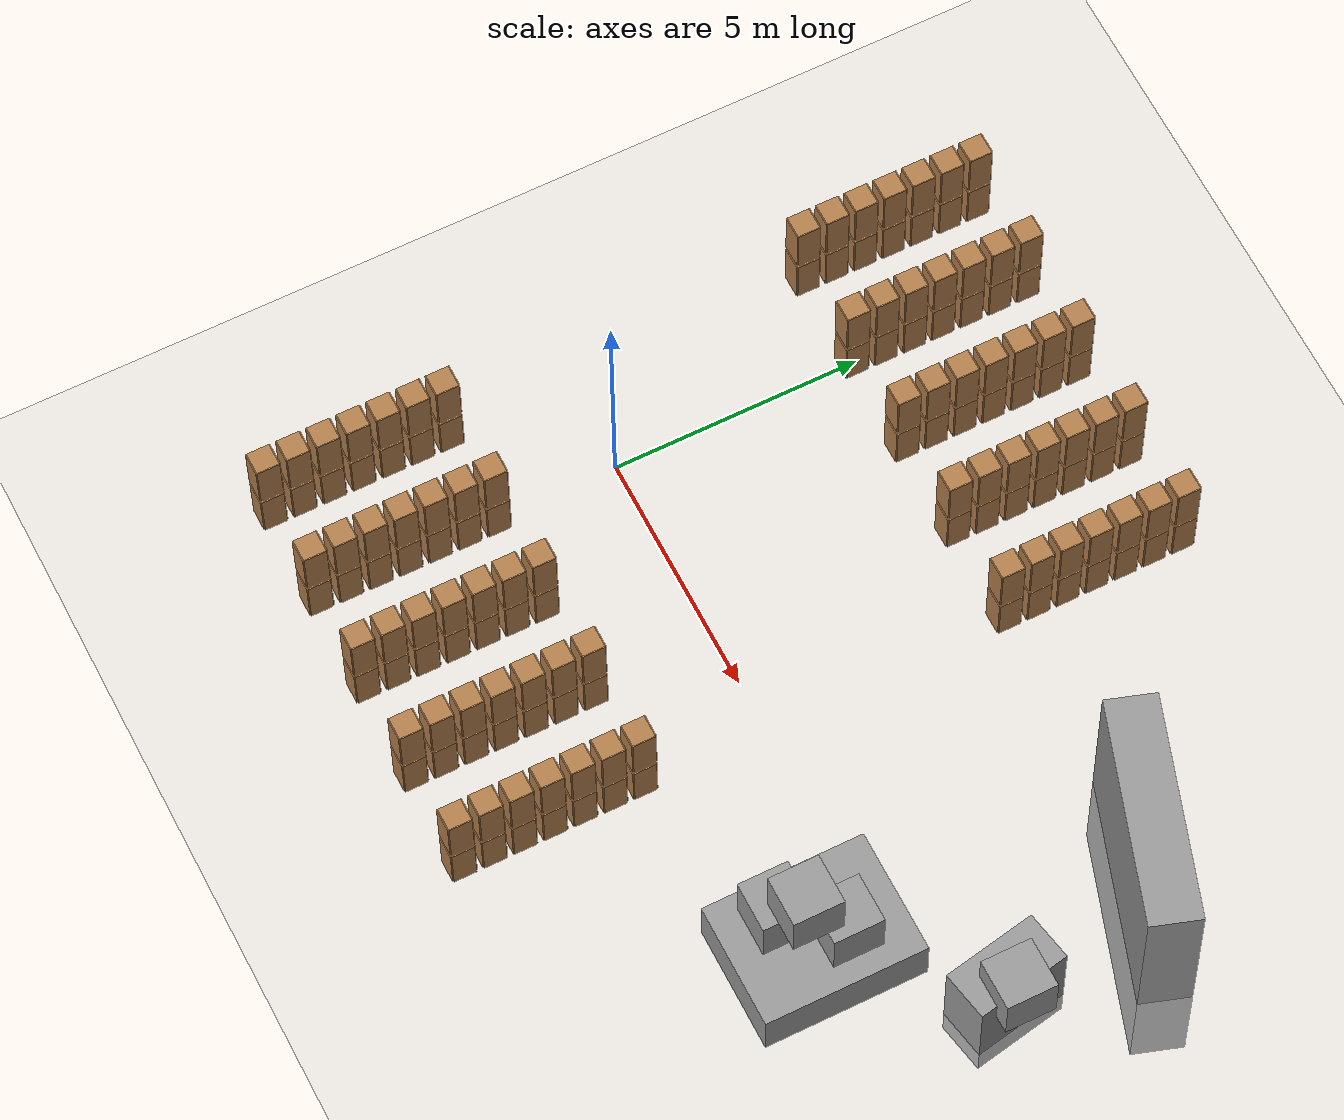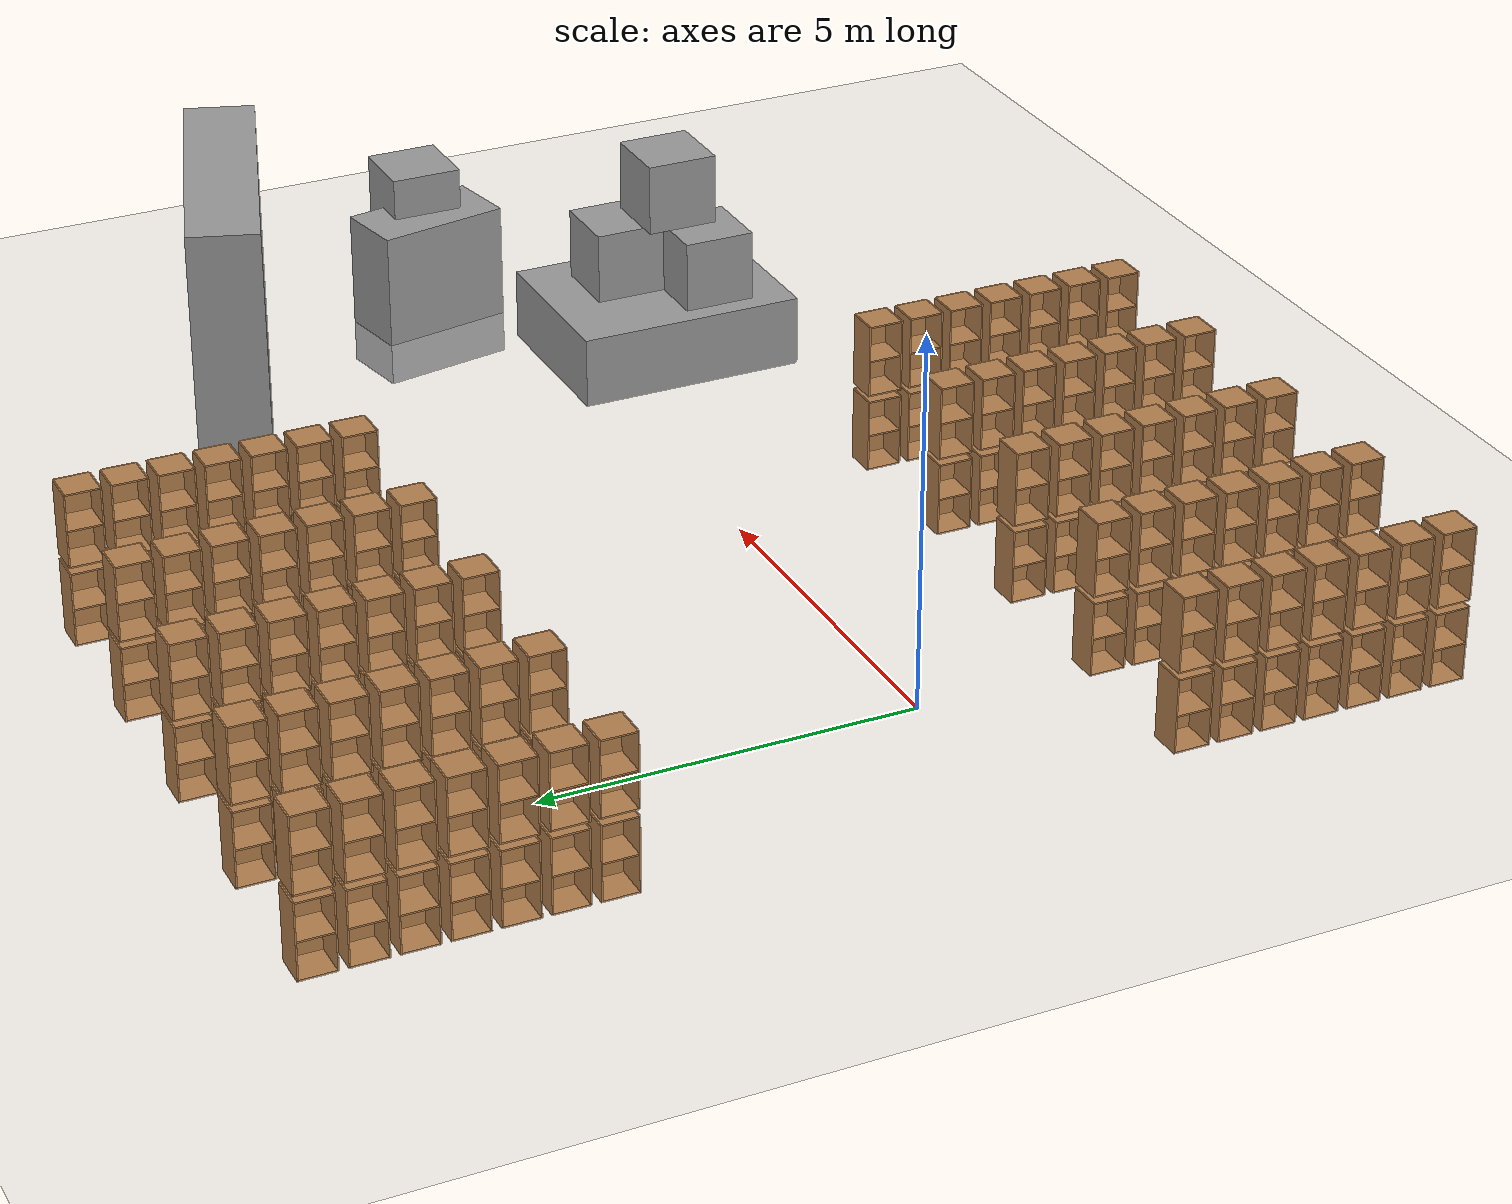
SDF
<sdf version="1.7">
 <world name="default">
  <light name="sun" type="directional">
   <pose>0 0 10 0 -0 0</pose>
   <diffuse>0.8 0.8 0.8 1</diffuse>
   <specular>0.2 0.2 0.2 1</specular>
   <attenuation>
    <range>1000</range>
    <constant>0.9</constant>
    <linear>0.01</linear>
    <quadratic>0.001</quadratic>
   </attenuation>
   <direction>-0.5 0.1 -0.9</direction>
   <spot><inner_angle>0</inner_angle><outer_angle>0</outer_angle><falloff>0</falloff></spot>
  </light>
  <model name="ground_plane">
   <static>1</static>
   <link name="link">
    <collision name="collision">
     <geometry><plane><normal>0 0 1</normal><size>100 100</size></plane></geometry>
     <surface><friction><ode><mu>100</mu><mu2>50</mu2></ode></friction></surface>
    </collision>
    <visual name="visual">
     <cast_shadows>0</cast_shadows>
     <geometry><plane><normal>0 0 1</normal><size>100 100</size></plane></geometry>
     <material>
      <script><uri>file://media/materials/scripts/gazebo.material</uri><name>Gazebo/Grey</name></script>
     </material>
    </visual>
   </link>
  </model>
  <gravity>0 0 -9.8</gravity>
  <magnetic_field>6e-06 2.3e-05 -4.2e-05</magnetic_field>
  <atmosphere type="adiabatic"/>
  <physics type="ode">
   <max_step_size>0.001</max_step_size>
   <real_time_factor>1</real_time_factor>
   <real_time_update_rate>1000</real_time_update_rate>
  </physics>
  <scene><ambient>0.4 0.4 0.4 1</ambient><background>0.7 0.7 0.7 1</background><shadows>1</shadows></scene>
  <spherical_coordinates>
   <surface_model>EARTH_WGS84</surface_model>
   <latitude_deg>0</latitude_deg>
   <longitude_deg>0</longitude_deg>
   <elevation>0</elevation>
   <heading_deg>0</heading_deg>
  </spherical_coordinates>
  <model name="cabinet">
   <static>1</static>
   <link name="cabinet_bottom_plate">
    <inertial>
     <pose>0 0 -1 0 -0 0</pose>
     <inertia><ixx>2.05</ixx><ixy>0</ixy><ixz>0</ixz><iyy>2.05</iyy><iyz>0</iyz><izz>2.05</izz></inertia>
     <mass>25</mass>
    </inertial>
    <collision name="cabinet_bottom_plate_geom">
     <pose>0 0 0.01 0 -0 0</pose>
     <geometry><box><size>0.45 0.45 0.02</size></box></geometry>
    </collision>
    <visual name="cabinet_bottom_plate_geom_visual">
     <pose>0 0 0.01 0 -0 0</pose>
     <geometry><box><size>0.45 0.45 0.02</size></box></geometry>
     <material>
      <script><uri>file://media/materials/scripts/gazebo.material</uri><name>Gazebo/Wood</name></script>
     </material>
    </visual>
    <collision name="cabinet_bottom_plate_geom_cabinet_back_plate">
     <pose>0.235 0 0.51 0 -0 0</pose>
     <geometry><box><size>0.02 0.45 1.02</size></box></geometry>
    </collision>
    <visual name="cabinet_bottom_plate_geom_cabinet_back_plate_visual">
     <pose>0.235 0 0.51 0 -0 0</pose>
     <geometry><box><size>0.02 0.45 1.02</size></box></geometry>
     <material>
      <script><uri>file://media/materials/scripts/gazebo.material</uri><name>Gazebo/Wood</name></script>
     </material>
    </visual>
    <collision name="cabinet_bottom_plate_geom_cabinet_left_plate">
     <pose>0 0.235 0.51 0 -0 0</pose>
     <geometry><box><size>0.45 0.02 1.02</size></box></geometry>
    </collision>
    <visual name="cabinet_bottom_plate_geom_cabinet_left_plate_visual">
     <pose>0 0.235 0.51 0 -0 0</pose>
     <geometry><box><size>0.45 0.02 1.02</size></box></geometry>
     <material>
      <script><uri>file://media/materials/scripts/gazebo.material</uri><name>Gazebo/Wood</name></script>
     </material>
    </visual>
    <collision name="cabinet_bottom_plate_geom_cabinet_middle_plate">
     <pose>0 0 0.51 0 -0 0</pose>
     <geometry><box><size>0.45 0.45 0.02</size></box></geometry>
    </collision>
    <visual name="cabinet_bottom_plate_geom_cabinet_middle_plate_visual">
     <pose>0 0 0.51 0 -0 0</pose>
     <geometry><box><size>0.45 0.45 0.02</size></box></geometry>
     <material>
      <script><uri>file://media/materials/scripts/gazebo.material</uri><name>Gazebo/Wood</name></script>
     </material>
    </visual>
    <collision name="cabinet_bottom_plate_geom_cabinet_right_plate">
     <pose>0 -0.235 0.51 0 -0 0</pose>
     <geometry><box><size>0.45 0.02 1.02</size></box></geometry>
    </collision>
    <visual name="cabinet_bottom_plate_geom_cabinet_right_plate_visual">
     <pose>0 -0.235 0.51 0 -0 0</pose>
     <geometry><box><size>0.45 0.02 1.02</size></box></geometry>
     <material>
      <script><uri>file://media/materials/scripts/gazebo.material</uri><name>Gazebo/Wood</name></script>
     </material>
    </visual>
    <collision name="cabinet_bottom_plate_geom_cabinet_top_plate">
     <pose>0 0 1.01 0 -0 0</pose>
     <geometry><box><size>0.45 0.45 0.02</size></box></geometry>
    </collision>
    <visual name="cabinet_bottom_plate_geom_cabinet_top_plate_visual">
     <pose>0 0 1.01 0 -0 0</pose>
     <geometry><box><size>0.45 0.45 0.02</size></box></geometry>
     <material>
      <script><uri>file://media/materials/scripts/gazebo.material</uri><name>Gazebo/Wood</name></script>
     </material>
    </visual>
   </link>
   <pose>4 4.9 0 0 -0 0</pose>
  </model>
  <model name="cabinet_0">
   <static>1</static>
   <link name="cabinet_bottom_plate">
    <inertial>
     <pose>0 0 -1 0 -0 0</pose>
     <inertia><ixx>2.05</ixx><ixy>0</ixy><ixz>0</ixz><iyy>2.05</iyy><iyz>0</iyz><izz>2.05</izz></inertia>
     <mass>25</mass>
    </inertial>
    <collision name="cabinet_bottom_plate_geom">
     <pose>0 0 0.01 0 -0 0</pose>
     <geometry><box><size>0.45 0.45 0.02</size></box></geometry>
    </collision>
    <visual name="cabinet_bottom_plate_geom_visual">
     <pose>0 0 0.01 0 -0 0</pose>
     <geometry><box><size>0.45 0.45 0.02</size></box></geometry>
     <material>
      <script><uri>file://media/materials/scripts/gazebo.material</uri><name>Gazebo/Wood</name></script>
     </material>
    </visual>
    <collision name="cabinet_bottom_plate_geom_cabinet_back_plate">
     <pose>0.235 0 0.51 0 -0 0</pose>
     <geometry><box><size>0.02 0.45 1.02</size></box></geometry>
    </collision>
    <visual name="cabinet_bottom_plate_geom_cabinet_back_plate_visual">
     <pose>0.235 0 0.51 0 -0 0</pose>
     <geometry><box><size>0.02 0.45 1.02</size></box></geometry>
     <material>
      <script><uri>file://media/materials/scripts/gazebo.material</uri><name>Gazebo/Wood</name></script>
     </material>
    </visual>
    <collision name="cabinet_bottom_plate_geom_cabinet_left_plate">
     <pose>0 0.235 0.51 0 -0 0</pose>
     <geometry><box><size>0.45 0.02 1.02</size></box></geometry>
    </collision>
    <visual name="cabinet_bottom_plate_geom_cabinet_left_plate_visual">
     <pose>0 0.235 0.51 0 -0 0</pose>
     <geometry><box><size>0.45 0.02 1.02</size></box></geometry>
     <material>
      <script><uri>file://media/materials/scripts/gazebo.material</uri><name>Gazebo/Wood</name></script>
     </material>
    </visual>
    <collision name="cabinet_bottom_plate_geom_cabinet_middle_plate">
     <pose>0 0 0.51 0 -0 0</pose>
     <geometry><box><size>0.45 0.45 0.02</size></box></geometry>
    </collision>
    <visual name="cabinet_bottom_plate_geom_cabinet_middle_plate_visual">
     <pose>0 0 0.51 0 -0 0</pose>
     <geometry><box><size>0.45 0.45 0.02</size></box></geometry>
     <material>
      <script><uri>file://media/materials/scripts/gazebo.material</uri><name>Gazebo/Wood</name></script>
     </material>
    </visual>
    <collision name="cabinet_bottom_plate_geom_cabinet_right_plate">
     <pose>0 -0.235 0.51 0 -0 0</pose>
     <geometry><box><size>0.45 0.02 1.02</size></box></geometry>
    </collision>
    <visual name="cabinet_bottom_plate_geom_cabinet_right_plate_visual">
     <pose>0 -0.235 0.51 0 -0 0</pose>
     <geometry><box><size>0.45 0.02 1.02</size></box></geometry>
     <material>
      <script><uri>file://media/materials/scripts/gazebo.material</uri><name>Gazebo/Wood</name></script>
     </material>
    </visual>
    <collision name="cabinet_bottom_plate_geom_cabinet_top_plate">
     <pose>0 0 1.01 0 -0 0</pose>
     <geometry><box><size>0.45 0.45 0.02</size></box></geometry>
    </collision>
    <visual name="cabinet_bottom_plate_geom_cabinet_top_plate_visual">
     <pose>0 0 1.01 0 -0 0</pose>
     <geometry><box><size>0.45 0.45 0.02</size></box></geometry>
     <material>
      <script><uri>file://media/materials/scripts/gazebo.material</uri><name>Gazebo/Wood</name></script>
     </material>
    </visual>
   </link>
   <pose>4 5.5 0 0 -0 0</pose>
  </model>
  <model name="cabinet_1">
   <static>1</static>
   <link name="cabinet_bottom_plate">
    <inertial>
     <pose>0 0 -1 0 -0 0</pose>
     <inertia><ixx>2.05</ixx><ixy>0</ixy><ixz>0</ixz><iyy>2.05</iyy><iyz>0</iyz><izz>2.05</izz></inertia>
     <mass>25</mass>
    </inertial>
    <collision name="cabinet_bottom_plate_geom">
     <pose>0 0 0.01 0 -0 0</pose>
     <geometry><box><size>0.45 0.45 0.02</size></box></geometry>
    </collision>
    <visual name="cabinet_bottom_plate_geom_visual">
     <pose>0 0 0.01 0 -0 0</pose>
     <geometry><box><size>0.45 0.45 0.02</size></box></geometry>
     <material>
      <script><uri>file://media/materials/scripts/gazebo.material</uri><name>Gazebo/Wood</name></script>
     </material>
    </visual>
    <collision name="cabinet_bottom_plate_geom_cabinet_back_plate">
     <pose>0.235 0 0.51 0 -0 0</pose>
     <geometry><box><size>0.02 0.45 1.02</size></box></geometry>
    </collision>
    <visual name="cabinet_bottom_plate_geom_cabinet_back_plate_visual">
     <pose>0.235 0 0.51 0 -0 0</pose>
     <geometry><box><size>0.02 0.45 1.02</size></box></geometry>
     <material>
      <script><uri>file://media/materials/scripts/gazebo.material</uri><name>Gazebo/Wood</name></script>
     </material>
    </visual>
    <collision name="cabinet_bottom_plate_geom_cabinet_left_plate">
     <pose>0 0.235 0.51 0 -0 0</pose>
     <geometry><box><size>0.45 0.02 1.02</size></box></geometry>
    </collision>
    <visual name="cabinet_bottom_plate_geom_cabinet_left_plate_visual">
     <pose>0 0.235 0.51 0 -0 0</pose>
     <geometry><box><size>0.45 0.02 1.02</size></box></geometry>
     <material>
      <script><uri>file://media/materials/scripts/gazebo.material</uri><name>Gazebo/Wood</name></script>
     </material>
    </visual>
    <collision name="cabinet_bottom_plate_geom_cabinet_middle_plate">
     <pose>0 0 0.51 0 -0 0</pose>
     <geometry><box><size>0.45 0.45 0.02</size></box></geometry>
    </collision>
    <visual name="cabinet_bottom_plate_geom_cabinet_middle_plate_visual">
     <pose>0 0 0.51 0 -0 0</pose>
     <geometry><box><size>0.45 0.45 0.02</size></box></geometry>
     <material>
      <script><uri>file://media/materials/scripts/gazebo.material</uri><name>Gazebo/Wood</name></script>
     </material>
    </visual>
    <collision name="cabinet_bottom_plate_geom_cabinet_right_plate">
     <pose>0 -0.235 0.51 0 -0 0</pose>
     <geometry><box><size>0.45 0.02 1.02</size></box></geometry>
    </collision>
    <visual name="cabinet_bottom_plate_geom_cabinet_right_plate_visual">
     <pose>0 -0.235 0.51 0 -0 0</pose>
     <geometry><box><size>0.45 0.02 1.02</size></box></geometry>
     <material>
      <script><uri>file://media/materials/scripts/gazebo.material</uri><name>Gazebo/Wood</name></script>
     </material>
    </visual>
    <collision name="cabinet_bottom_plate_geom_cabinet_top_plate">
     <pose>0 0 1.01 0 -0 0</pose>
     <geometry><box><size>0.45 0.45 0.02</size></box></geometry>
    </collision>
    <visual name="cabinet_bottom_plate_geom_cabinet_top_plate_visual">
     <pose>0 0 1.01 0 -0 0</pose>
     <geometry><box><size>0.45 0.45 0.02</size></box></geometry>
     <material>
      <script><uri>file://media/materials/scripts/gazebo.material</uri><name>Gazebo/Wood</name></script>
     </material>
    </visual>
   </link>
   <pose>4 6.1 0 0 -0 0</pose>
  </model>
  <model name="cabinet_2">
   <static>1</static>
   <link name="cabinet_bottom_plate">
    <inertial>
     <pose>0 0 -1 0 -0 0</pose>
     <inertia><ixx>2.05</ixx><ixy>0</ixy><ixz>0</ixz><iyy>2.05</iyy><iyz>0</iyz><izz>2.05</izz></inertia>
     <mass>25</mass>
    </inertial>
    <collision name="cabinet_bottom_plate_geom">
     <pose>0 0 0.01 0 -0 0</pose>
     <geometry><box><size>0.45 0.45 0.02</size></box></geometry>
    </collision>
    <visual name="cabinet_bottom_plate_geom_visual">
     <pose>0 0 0.01 0 -0 0</pose>
     <geometry><box><size>0.45 0.45 0.02</size></box></geometry>
     <material>
      <script><uri>file://media/materials/scripts/gazebo.material</uri><name>Gazebo/Wood</name></script>
     </material>
    </visual>
    <collision name="cabinet_bottom_plate_geom_cabinet_back_plate">
     <pose>0.235 0 0.51 0 -0 0</pose>
     <geometry><box><size>0.02 0.45 1.02</size></box></geometry>
    </collision>
    <visual name="cabinet_bottom_plate_geom_cabinet_back_plate_visual">
     <pose>0.235 0 0.51 0 -0 0</pose>
     <geometry><box><size>0.02 0.45 1.02</size></box></geometry>
     <material>
      <script><uri>file://media/materials/scripts/gazebo.material</uri><name>Gazebo/Wood</name></script>
     </material>
    </visual>
    <collision name="cabinet_bottom_plate_geom_cabinet_left_plate">
     <pose>0 0.235 0.51 0 -0 0</pose>
     <geometry><box><size>0.45 0.02 1.02</size></box></geometry>
    </collision>
    <visual name="cabinet_bottom_plate_geom_cabinet_left_plate_visual">
     <pose>0 0.235 0.51 0 -0 0</pose>
     <geometry><box><size>0.45 0.02 1.02</size></box></geometry>
     <material>
      <script><uri>file://media/materials/scripts/gazebo.material</uri><name>Gazebo/Wood</name></script>
     </material>
    </visual>
    <collision name="cabinet_bottom_plate_geom_cabinet_middle_plate">
     <pose>0 0 0.51 0 -0 0</pose>
     <geometry><box><size>0.45 0.45 0.02</size></box></geometry>
    </collision>
    <visual name="cabinet_bottom_plate_geom_cabinet_middle_plate_visual">
     <pose>0 0 0.51 0 -0 0</pose>
     <geometry><box><size>0.45 0.45 0.02</size></box></geometry>
     <material>
      <script><uri>file://media/materials/scripts/gazebo.material</uri><name>Gazebo/Wood</name></script>
     </material>
    </visual>
    <collision name="cabinet_bottom_plate_geom_cabinet_right_plate">
     <pose>0 -0.235 0.51 0 -0 0</pose>
     <geometry><box><size>0.45 0.02 1.02</size></box></geometry>
    </collision>
    <visual name="cabinet_bottom_plate_geom_cabinet_right_plate_visual">
     <pose>0 -0.235 0.51 0 -0 0</pose>
     <geometry><box><size>0.45 0.02 1.02</size></box></geometry>
     <material>
      <script><uri>file://media/materials/scripts/gazebo.material</uri><name>Gazebo/Wood</name></script>
     </material>
    </visual>
    <collision name="cabinet_bottom_plate_geom_cabinet_top_plate">
     <pose>0 0 1.01 0 -0 0</pose>
     <geometry><box><size>0.45 0.45 0.02</size></box></geometry>
    </collision>
    <visual name="cabinet_bottom_plate_geom_cabinet_top_plate_visual">
     <pose>0 0 1.01 0 -0 0</pose>
     <geometry><box><size>0.45 0.45 0.02</size></box></geometry>
     <material>
      <script><uri>file://media/materials/scripts/gazebo.material</uri><name>Gazebo/Wood</name></script>
     </material>
    </visual>
   </link>
   <pose>4 6.7 0 0 -0 0</pose>
  </model>
  <model name="cabinet_3">
   <static>1</static>
   <link name="cabinet_bottom_plate">
    <inertial>
     <pose>0 0 -1 0 -0 0</pose>
     <inertia><ixx>2.05</ixx><ixy>0</ixy><ixz>0</ixz><iyy>2.05</iyy><iyz>0</iyz><izz>2.05</izz></inertia>
     <mass>25</mass>
    </inertial>
    <collision name="cabinet_bottom_plate_geom">
     <pose>0 0 0.01 0 -0 0</pose>
     <geometry><box><size>0.45 0.45 0.02</size></box></geometry>
    </collision>
    <visual name="cabinet_bottom_plate_geom_visual">
     <pose>0 0 0.01 0 -0 0</pose>
     <geometry><box><size>0.45 0.45 0.02</size></box></geometry>
     <material>
      <script><uri>file://media/materials/scripts/gazebo.material</uri><name>Gazebo/Wood</name></script>
     </material>
    </visual>
    <collision name="cabinet_bottom_plate_geom_cabinet_back_plate">
     <pose>0.235 0 0.51 0 -0 0</pose>
     <geometry><box><size>0.02 0.45 1.02</size></box></geometry>
    </collision>
    <visual name="cabinet_bottom_plate_geom_cabinet_back_plate_visual">
     <pose>0.235 0 0.51 0 -0 0</pose>
     <geometry><box><size>0.02 0.45 1.02</size></box></geometry>
     <material>
      <script><uri>file://media/materials/scripts/gazebo.material</uri><name>Gazebo/Wood</name></script>
     </material>
    </visual>
    <collision name="cabinet_bottom_plate_geom_cabinet_left_plate">
     <pose>0 0.235 0.51 0 -0 0</pose>
     <geometry><box><size>0.45 0.02 1.02</size></box></geometry>
    </collision>
    <visual name="cabinet_bottom_plate_geom_cabinet_left_plate_visual">
     <pose>0 0.235 0.51 0 -0 0</pose>
     <geometry><box><size>0.45 0.02 1.02</size></box></geometry>
     <material>
      <script><uri>file://media/materials/scripts/gazebo.material</uri><name>Gazebo/Wood</name></script>
     </material>
    </visual>
    <collision name="cabinet_bottom_plate_geom_cabinet_middle_plate">
     <pose>0 0 0.51 0 -0 0</pose>
     <geometry><box><size>0.45 0.45 0.02</size></box></geometry>
    </collision>
    <visual name="cabinet_bottom_plate_geom_cabinet_middle_plate_visual">
     <pose>0 0 0.51 0 -0 0</pose>
     <geometry><box><size>0.45 0.45 0.02</size></box></geometry>
     <material>
      <script><uri>file://media/materials/scripts/gazebo.material</uri><name>Gazebo/Wood</name></script>
     </material>
    </visual>
    <collision name="cabinet_bottom_plate_geom_cabinet_right_plate">
     <pose>0 -0.235 0.51 0 -0 0</pose>
     <geometry><box><size>0.45 0.02 1.02</size></box></geometry>
    </collision>
    <visual name="cabinet_bottom_plate_geom_cabinet_right_plate_visual">
     <pose>0 -0.235 0.51 0 -0 0</pose>
     <geometry><box><size>0.45 0.02 1.02</size></box></geometry>
     <material>
      <script><uri>file://media/materials/scripts/gazebo.material</uri><name>Gazebo/Wood</name></script>
     </material>
    </visual>
    <collision name="cabinet_bottom_plate_geom_cabinet_top_plate">
     <pose>0 0 1.01 0 -0 0</pose>
     <geometry><box><size>0.45 0.45 0.02</size></box></geometry>
    </collision>
    <visual name="cabinet_bottom_plate_geom_cabinet_top_plate_visual">
     <pose>0 0 1.01 0 -0 0</pose>
     <geometry><box><size>0.45 0.45 0.02</size></box></geometry>
     <material>
      <script><uri>file://media/materials/scripts/gazebo.material</uri><name>Gazebo/Wood</name></script>
     </material>
    </visual>
   </link>
   <pose>4 7.3 0 0 -0 0</pose>
  </model>
  <model name="cabinet_4">
   <static>1</static>
   <link name="cabinet_bottom_plate">
    <inertial>
     <pose>0 0 -1 0 -0 0</pose>
     <inertia><ixx>2.05</ixx><ixy>0</ixy><ixz>0</ixz><iyy>2.05</iyy><iyz>0</iyz><izz>2.05</izz></inertia>
     <mass>25</mass>
    </inertial>
    <collision name="cabinet_bottom_plate_geom">
     <pose>0 0 0.01 0 -0 0</pose>
     <geometry><box><size>0.45 0.45 0.02</size></box></geometry>
    </collision>
    <visual name="cabinet_bottom_plate_geom_visual">
     <pose>0 0 0.01 0 -0 0</pose>
     <geometry><box><size>0.45 0.45 0.02</size></box></geometry>
     <material>
      <script><uri>file://media/materials/scripts/gazebo.material</uri><name>Gazebo/Wood</name></script>
     </material>
    </visual>
    <collision name="cabinet_bottom_plate_geom_cabinet_back_plate">
     <pose>0.235 0 0.51 0 -0 0</pose>
     <geometry><box><size>0.02 0.45 1.02</size></box></geometry>
    </collision>
    <visual name="cabinet_bottom_plate_geom_cabinet_back_plate_visual">
     <pose>0.235 0 0.51 0 -0 0</pose>
     <geometry><box><size>0.02 0.45 1.02</size></box></geometry>
     <material>
      <script><uri>file://media/materials/scripts/gazebo.material</uri><name>Gazebo/Wood</name></script>
     </material>
    </visual>
    <collision name="cabinet_bottom_plate_geom_cabinet_left_plate">
     <pose>0 0.235 0.51 0 -0 0</pose>
     <geometry><box><size>0.45 0.02 1.02</size></box></geometry>
    </collision>
    <visual name="cabinet_bottom_plate_geom_cabinet_left_plate_visual">
     <pose>0 0.235 0.51 0 -0 0</pose>
     <geometry><box><size>0.45 0.02 1.02</size></box></geometry>
     <material>
      <script><uri>file://media/materials/scripts/gazebo.material</uri><name>Gazebo/Wood</name></script>
     </material>
    </visual>
    <collision name="cabinet_bottom_plate_geom_cabinet_middle_plate">
     <pose>0 0 0.51 0 -0 0</pose>
     <geometry><box><size>0.45 0.45 0.02</size></box></geometry>
    </collision>
    <visual name="cabinet_bottom_plate_geom_cabinet_middle_plate_visual">
     <pose>0 0 0.51 0 -0 0</pose>
     <geometry><box><size>0.45 0.45 0.02</size></box></geometry>
     <material>
      <script><uri>file://media/materials/scripts/gazebo.material</uri><name>Gazebo/Wood</name></script>
     </material>
    </visual>
    <collision name="cabinet_bottom_plate_geom_cabinet_right_plate">
     <pose>0 -0.235 0.51 0 -0 0</pose>
     <geometry><box><size>0.45 0.02 1.02</size></box></geometry>
    </collision>
    <visual name="cabinet_bottom_plate_geom_cabinet_right_plate_visual">
     <pose>0 -0.235 0.51 0 -0 0</pose>
     <geometry><box><size>0.45 0.02 1.02</size></box></geometry>
     <material>
      <script><uri>file://media/materials/scripts/gazebo.material</uri><name>Gazebo/Wood</name></script>
     </material>
    </visual>
    <collision name="cabinet_bottom_plate_geom_cabinet_top_plate">
     <pose>0 0 1.01 0 -0 0</pose>
     <geometry><box><size>0.45 0.45 0.02</size></box></geometry>
    </collision>
    <visual name="cabinet_bottom_plate_geom_cabinet_top_plate_visual">
     <pose>0 0 1.01 0 -0 0</pose>
     <geometry><box><size>0.45 0.45 0.02</size></box></geometry>
     <material>
      <script><uri>file://media/materials/scripts/gazebo.material</uri><name>Gazebo/Wood</name></script>
     </material>
    </visual>
   </link>
   <pose>2 4.9 0 0 -0 0</pose>
  </model>
  <model name="cabinet_5">
   <static>1</static>
   <link name="cabinet_bottom_plate">
    <inertial>
     <pose>0 0 -1 0 -0 0</pose>
     <inertia><ixx>2.05</ixx><ixy>0</ixy><ixz>0</ixz><iyy>2.05</iyy><iyz>0</iyz><izz>2.05</izz></inertia>
     <mass>25</mass>
    </inertial>
    <collision name="cabinet_bottom_plate_geom">
     <pose>0 0 0.01 0 -0 0</pose>
     <geometry><box><size>0.45 0.45 0.02</size></box></geometry>
    </collision>
    <visual name="cabinet_bottom_plate_geom_visual">
     <pose>0 0 0.01 0 -0 0</pose>
     <geometry><box><size>0.45 0.45 0.02</size></box></geometry>
     <material>
      <script><uri>file://media/materials/scripts/gazebo.material</uri><name>Gazebo/Wood</name></script>
     </material>
    </visual>
    <collision name="cabinet_bottom_plate_geom_cabinet_back_plate">
     <pose>0.235 0 0.51 0 -0 0</pose>
     <geometry><box><size>0.02 0.45 1.02</size></box></geometry>
    </collision>
    <visual name="cabinet_bottom_plate_geom_cabinet_back_plate_visual">
     <pose>0.235 0 0.51 0 -0 0</pose>
     <geometry><box><size>0.02 0.45 1.02</size></box></geometry>
     <material>
      <script><uri>file://media/materials/scripts/gazebo.material</uri><name>Gazebo/Wood</name></script>
     </material>
    </visual>
    <collision name="cabinet_bottom_plate_geom_cabinet_left_plate">
     <pose>0 0.235 0.51 0 -0 0</pose>
     <geometry><box><size>0.45 0.02 1.02</size></box></geometry>
    </collision>
    <visual name="cabinet_bottom_plate_geom_cabinet_left_plate_visual">
     <pose>0 0.235 0.51 0 -0 0</pose>
     <geometry><box><size>0.45 0.02 1.02</size></box></geometry>
     <material>
      <script><uri>file://media/materials/scripts/gazebo.material</uri><name>Gazebo/Wood</name></script>
     </material>
    </visual>
    <collision name="cabinet_bottom_plate_geom_cabinet_middle_plate">
     <pose>0 0 0.51 0 -0 0</pose>
     <geometry><box><size>0.45 0.45 0.02</size></box></geometry>
    </collision>
    <visual name="cabinet_bottom_plate_geom_cabinet_middle_plate_visual">
     <pose>0 0 0.51 0 -0 0</pose>
     <geometry><box><size>0.45 0.45 0.02</size></box></geometry>
     <material>
      <script><uri>file://media/materials/scripts/gazebo.material</uri><name>Gazebo/Wood</name></script>
     </material>
    </visual>
    <collision name="cabinet_bottom_plate_geom_cabinet_right_plate">
     <pose>0 -0.235 0.51 0 -0 0</pose>
     <geometry><box><size>0.45 0.02 1.02</size></box></geometry>
    </collision>
    <visual name="cabinet_bottom_plate_geom_cabinet_right_plate_visual">
     <pose>0 -0.235 0.51 0 -0 0</pose>
     <geometry><box><size>0.45 0.02 1.02</size></box></geometry>
     <material>
      <script><uri>file://media/materials/scripts/gazebo.material</uri><name>Gazebo/Wood</name></script>
     </material>
    </visual>
    <collision name="cabinet_bottom_plate_geom_cabinet_top_plate">
     <pose>0 0 1.01 0 -0 0</pose>
     <geometry><box><size>0.45 0.45 0.02</size></box></geometry>
    </collision>
    <visual name="cabinet_bottom_plate_geom_cabinet_top_plate_visual">
     <pose>0 0 1.01 0 -0 0</pose>
     <geometry><box><size>0.45 0.45 0.02</size></box></geometry>
     <material>
      <script><uri>file://media/materials/scripts/gazebo.material</uri><name>Gazebo/Wood</name></script>
     </material>
    </visual>
   </link>
   <pose>2 5.5 0 0 -0 0</pose>
  </model>
  <model name="cabinet_6">
   <static>1</static>
   <link name="cabinet_bottom_plate">
    <inertial>
     <pose>0 0 -1 0 -0 0</pose>
     <inertia><ixx>2.05</ixx><ixy>0</ixy><ixz>0</ixz><iyy>2.05</iyy><iyz>0</iyz><izz>2.05</izz></inertia>
     <mass>25</mass>
    </inertial>
    <collision name="cabinet_bottom_plate_geom">
     <pose>0 0 0.01 0 -0 0</pose>
     <geometry><box><size>0.45 0.45 0.02</size></box></geometry>
    </collision>
    <visual name="cabinet_bottom_plate_geom_visual">
     <pose>0 0 0.01 0 -0 0</pose>
     <geometry><box><size>0.45 0.45 0.02</size></box></geometry>
     <material>
      <script><uri>file://media/materials/scripts/gazebo.material</uri><name>Gazebo/Wood</name></script>
     </material>
    </visual>
    <collision name="cabinet_bottom_plate_geom_cabinet_back_plate">
     <pose>0.235 0 0.51 0 -0 0</pose>
     <geometry><box><size>0.02 0.45 1.02</size></box></geometry>
    </collision>
    <visual name="cabinet_bottom_plate_geom_cabinet_back_plate_visual">
     <pose>0.235 0 0.51 0 -0 0</pose>
     <geometry><box><size>0.02 0.45 1.02</size></box></geometry>
     <material>
      <script><uri>file://media/materials/scripts/gazebo.material</uri><name>Gazebo/Wood</name></script>
     </material>
    </visual>
    <collision name="cabinet_bottom_plate_geom_cabinet_left_plate">
     <pose>0 0.235 0.51 0 -0 0</pose>
     <geometry><box><size>0.45 0.02 1.02</size></box></geometry>
    </collision>
    <visual name="cabinet_bottom_plate_geom_cabinet_left_plate_visual">
     <pose>0 0.235 0.51 0 -0 0</pose>
     <geometry><box><size>0.45 0.02 1.02</size></box></geometry>
     <material>
      <script><uri>file://media/materials/scripts/gazebo.material</uri><name>Gazebo/Wood</name></script>
     </material>
    </visual>
    <collision name="cabinet_bottom_plate_geom_cabinet_middle_plate">
     <pose>0 0 0.51 0 -0 0</pose>
     <geometry><box><size>0.45 0.45 0.02</size></box></geometry>
    </collision>
    <visual name="cabinet_bottom_plate_geom_cabinet_middle_plate_visual">
     <pose>0 0 0.51 0 -0 0</pose>
     <geometry><box><size>0.45 0.45 0.02</size></box></geometry>
     <material>
      <script><uri>file://media/materials/scripts/gazebo.material</uri><name>Gazebo/Wood</name></script>
     </material>
    </visual>
    <collision name="cabinet_bottom_plate_geom_cabinet_right_plate">
     <pose>0 -0.235 0.51 0 -0 0</pose>
     <geometry><box><size>0.45 0.02 1.02</size></box></geometry>
    </collision>
    <visual name="cabinet_bottom_plate_geom_cabinet_right_plate_visual">
     <pose>0 -0.235 0.51 0 -0 0</pose>
     <geometry><box><size>0.45 0.02 1.02</size></box></geometry>
     <material>
      <script><uri>file://media/materials/scripts/gazebo.material</uri><name>Gazebo/Wood</name></script>
     </material>
    </visual>
    <collision name="cabinet_bottom_plate_geom_cabinet_top_plate">
     <pose>0 0 1.01 0 -0 0</pose>
     <geometry><box><size>0.45 0.45 0.02</size></box></geometry>
    </collision>
    <visual name="cabinet_bottom_plate_geom_cabinet_top_plate_visual">
     <pose>0 0 1.01 0 -0 0</pose>
     <geometry><box><size>0.45 0.45 0.02</size></box></geometry>
     <material>
      <script><uri>file://media/materials/scripts/gazebo.material</uri><name>Gazebo/Wood</name></script>
     </material>
    </visual>
   </link>
   <pose>2 6.1 0 0 -0 0</pose>
  </model>
  <model name="cabinet_7">
   <static>1</static>
   <link name="cabinet_bottom_plate">
    <inertial>
     <pose>0 0 -1 0 -0 0</pose>
     <inertia><ixx>2.05</ixx><ixy>0</ixy><ixz>0</ixz><iyy>2.05</iyy><iyz>0</iyz><izz>2.05</izz></inertia>
     <mass>25</mass>
    </inertial>
    <collision name="cabinet_bottom_plate_geom">
     <pose>0 0 0.01 0 -0 0</pose>
     <geometry><box><size>0.45 0.45 0.02</size></box></geometry>
    </collision>
    <visual name="cabinet_bottom_plate_geom_visual">
     <pose>0 0 0.01 0 -0 0</pose>
     <geometry><box><size>0.45 0.45 0.02</size></box></geometry>
     <material>
      <script><uri>file://media/materials/scripts/gazebo.material</uri><name>Gazebo/Wood</name></script>
     </material>
    </visual>
    <collision name="cabinet_bottom_plate_geom_cabinet_back_plate">
     <pose>0.235 0 0.51 0 -0 0</pose>
     <geometry><box><size>0.02 0.45 1.02</size></box></geometry>
    </collision>
    <visual name="cabinet_bottom_plate_geom_cabinet_back_plate_visual">
     <pose>0.235 0 0.51 0 -0 0</pose>
     <geometry><box><size>0.02 0.45 1.02</size></box></geometry>
     <material>
      <script><uri>file://media/materials/scripts/gazebo.material</uri><name>Gazebo/Wood</name></script>
     </material>
    </visual>
    <collision name="cabinet_bottom_plate_geom_cabinet_left_plate">
     <pose>0 0.235 0.51 0 -0 0</pose>
     <geometry><box><size>0.45 0.02 1.02</size></box></geometry>
    </collision>
    <visual name="cabinet_bottom_plate_geom_cabinet_left_plate_visual">
     <pose>0 0.235 0.51 0 -0 0</pose>
     <geometry><box><size>0.45 0.02 1.02</size></box></geometry>
     <material>
      <script><uri>file://media/materials/scripts/gazebo.material</uri><name>Gazebo/Wood</name></script>
     </material>
    </visual>
    <collision name="cabinet_bottom_plate_geom_cabinet_middle_plate">
     <pose>0 0 0.51 0 -0 0</pose>
     <geometry><box><size>0.45 0.45 0.02</size></box></geometry>
    </collision>
    <visual name="cabinet_bottom_plate_geom_cabinet_middle_plate_visual">
     <pose>0 0 0.51 0 -0 0</pose>
     <geometry><box><size>0.45 0.45 0.02</size></box></geometry>
     <material>
      <script><uri>file://media/materials/scripts/gazebo.material</uri><name>Gazebo/Wood</name></script>
     </material>
    </visual>
    <collision name="cabinet_bottom_plate_geom_cabinet_right_plate">
     <pose>0 -0.235 0.51 0 -0 0</pose>
     <geometry><box><size>0.45 0.02 1.02</size></box></geometry>
    </collision>
    <visual name="cabinet_bottom_plate_geom_cabinet_right_plate_visual">
     <pose>0 -0.235 0.51 0 -0 0</pose>
     <geometry><box><size>0.45 0.02 1.02</size></box></geometry>
     <material>
      <script><uri>file://media/materials/scripts/gazebo.material</uri><name>Gazebo/Wood</name></script>
     </material>
    </visual>
    <collision name="cabinet_bottom_plate_geom_cabinet_top_plate">
     <pose>0 0 1.01 0 -0 0</pose>
     <geometry><box><size>0.45 0.45 0.02</size></box></geometry>
    </collision>
    <visual name="cabinet_bottom_plate_geom_cabinet_top_plate_visual">
     <pose>0 0 1.01 0 -0 0</pose>
     <geometry><box><size>0.45 0.45 0.02</size></box></geometry>
     <material>
      <script><uri>file://media/materials/scripts/gazebo.material</uri><name>Gazebo/Wood</name></script>
     </material>
    </visual>
   </link>
   <pose>2 6.7 0 0 -0 0</pose>
  </model>
  <model name="cabinet_8">
   <static>1</static>
   <link name="cabinet_bottom_plate">
    <inertial>
     <pose>0 0 -1 0 -0 0</pose>
     <inertia><ixx>2.05</ixx><ixy>0</ixy><ixz>0</ixz><iyy>2.05</iyy><iyz>0</iyz><izz>2.05</izz></inertia>
     <mass>25</mass>
    </inertial>
    <collision name="cabinet_bottom_plate_geom">
     <pose>0 0 0.01 0 -0 0</pose>
     <geometry><box><size>0.45 0.45 0.02</size></box></geometry>
    </collision>
    <visual name="cabinet_bottom_plate_geom_visual">
     <pose>0 0 0.01 0 -0 0</pose>
     <geometry><box><size>0.45 0.45 0.02</size></box></geometry>
     <material>
      <script><uri>file://media/materials/scripts/gazebo.material</uri><name>Gazebo/Wood</name></script>
     </material>
    </visual>
    <collision name="cabinet_bottom_plate_geom_cabinet_back_plate">
     <pose>0.235 0 0.51 0 -0 0</pose>
     <geometry><box><size>0.02 0.45 1.02</size></box></geometry>
    </collision>
    <visual name="cabinet_bottom_plate_geom_cabinet_back_plate_visual">
     <pose>0.235 0 0.51 0 -0 0</pose>
     <geometry><box><size>0.02 0.45 1.02</size></box></geometry>
     <material>
      <script><uri>file://media/materials/scripts/gazebo.material</uri><name>Gazebo/Wood</name></script>
     </material>
    </visual>
    <collision name="cabinet_bottom_plate_geom_cabinet_left_plate">
     <pose>0 0.235 0.51 0 -0 0</pose>
     <geometry><box><size>0.45 0.02 1.02</size></box></geometry>
    </collision>
    <visual name="cabinet_bottom_plate_geom_cabinet_left_plate_visual">
     <pose>0 0.235 0.51 0 -0 0</pose>
     <geometry><box><size>0.45 0.02 1.02</size></box></geometry>
     <material>
      <script><uri>file://media/materials/scripts/gazebo.material</uri><name>Gazebo/Wood</name></script>
     </material>
    </visual>
    <collision name="cabinet_bottom_plate_geom_cabinet_middle_plate">
     <pose>0 0 0.51 0 -0 0</pose>
     <geometry><box><size>0.45 0.45 0.02</size></box></geometry>
    </collision>
    <visual name="cabinet_bottom_plate_geom_cabinet_middle_plate_visual">
     <pose>0 0 0.51 0 -0 0</pose>
     <geometry><box><size>0.45 0.45 0.02</size></box></geometry>
     <material>
      <script><uri>file://media/materials/scripts/gazebo.material</uri><name>Gazebo/Wood</name></script>
     </material>
    </visual>
    <collision name="cabinet_bottom_plate_geom_cabinet_right_plate">
     <pose>0 -0.235 0.51 0 -0 0</pose>
     <geometry><box><size>0.45 0.02 1.02</size></box></geometry>
    </collision>
    <visual name="cabinet_bottom_plate_geom_cabinet_right_plate_visual">
     <pose>0 -0.235 0.51 0 -0 0</pose>
     <geometry><box><size>0.45 0.02 1.02</size></box></geometry>
     <material>
      <script><uri>file://media/materials/scripts/gazebo.material</uri><name>Gazebo/Wood</name></script>
     </material>
    </visual>
    <collision name="cabinet_bottom_plate_geom_cabinet_top_plate">
     <pose>0 0 1.01 0 -0 0</pose>
     <geometry><box><size>0.45 0.45 0.02</size></box></geometry>
    </collision>
    <visual name="cabinet_bottom_plate_geom_cabinet_top_plate_visual">
     <pose>0 0 1.01 0 -0 0</pose>
     <geometry><box><size>0.45 0.45 0.02</size></box></geometry>
     <material>
      <script><uri>file://media/materials/scripts/gazebo.material</uri><name>Gazebo/Wood</name></script>
     </material>
    </visual>
   </link>
   <pose>2 7.3 0 0 -0 0</pose>
  </model>
  <model name="cabinet_9">
   <static>1</static>
   <link name="cabinet_bottom_plate">
    <inertial>
     <pose>0 0 -1 0 -0 0</pose>
     <inertia><ixx>2.05</ixx><ixy>0</ixy><ixz>0</ixz><iyy>2.05</iyy><iyz>0</iyz><izz>2.05</izz></inertia>
     <mass>25</mass>
    </inertial>
    <collision name="cabinet_bottom_plate_geom">
     <pose>0 0 0.01 0 -0 0</pose>
     <geometry><box><size>0.45 0.45 0.02</size></box></geometry>
    </collision>
    <visual name="cabinet_bottom_plate_geom_visual">
     <pose>0 0 0.01 0 -0 0</pose>
     <geometry><box><size>0.45 0.45 0.02</size></box></geometry>
     <material>
      <script><uri>file://media/materials/scripts/gazebo.material</uri><name>Gazebo/Wood</name></script>
     </material>
    </visual>
    <collision name="cabinet_bottom_plate_geom_cabinet_back_plate">
     <pose>0.235 0 0.51 0 -0 0</pose>
     <geometry><box><size>0.02 0.45 1.02</size></box></geometry>
    </collision>
    <visual name="cabinet_bottom_plate_geom_cabinet_back_plate_visual">
     <pose>0.235 0 0.51 0 -0 0</pose>
     <geometry><box><size>0.02 0.45 1.02</size></box></geometry>
     <material>
      <script><uri>file://media/materials/scripts/gazebo.material</uri><name>Gazebo/Wood</name></script>
     </material>
    </visual>
    <collision name="cabinet_bottom_plate_geom_cabinet_left_plate">
     <pose>0 0.235 0.51 0 -0 0</pose>
     <geometry><box><size>0.45 0.02 1.02</size></box></geometry>
    </collision>
    <visual name="cabinet_bottom_plate_geom_cabinet_left_plate_visual">
     <pose>0 0.235 0.51 0 -0 0</pose>
     <geometry><box><size>0.45 0.02 1.02</size></box></geometry>
     <material>
      <script><uri>file://media/materials/scripts/gazebo.material</uri><name>Gazebo/Wood</name></script>
     </material>
    </visual>
    <collision name="cabinet_bottom_plate_geom_cabinet_middle_plate">
     <pose>0 0 0.51 0 -0 0</pose>
     <geometry><box><size>0.45 0.45 0.02</size></box></geometry>
    </collision>
    <visual name="cabinet_bottom_plate_geom_cabinet_middle_plate_visual">
     <pose>0 0 0.51 0 -0 0</pose>
     <geometry><box><size>0.45 0.45 0.02</size></box></geometry>
     <material>
      <script><uri>file://media/materials/scripts/gazebo.material</uri><name>Gazebo/Wood</name></script>
     </material>
    </visual>
    <collision name="cabinet_bottom_plate_geom_cabinet_right_plate">
     <pose>0 -0.235 0.51 0 -0 0</pose>
     <geometry><box><size>0.45 0.02 1.02</size></box></geometry>
    </collision>
    <visual name="cabinet_bottom_plate_geom_cabinet_right_plate_visual">
     <pose>0 -0.235 0.51 0 -0 0</pose>
     <geometry><box><size>0.45 0.02 1.02</size></box></geometry>
     <material>
      <script><uri>file://media/materials/scripts/gazebo.material</uri><name>Gazebo/Wood</name></script>
     </material>
    </visual>
    <collision name="cabinet_bottom_plate_geom_cabinet_top_plate">
     <pose>0 0 1.01 0 -0 0</pose>
     <geometry><box><size>0.45 0.45 0.02</size></box></geometry>
    </collision>
    <visual name="cabinet_bottom_plate_geom_cabinet_top_plate_visual">
     <pose>0 0 1.01 0 -0 0</pose>
     <geometry><box><size>0.45 0.45 0.02</size></box></geometry>
     <material>
      <script><uri>file://media/materials/scripts/gazebo.material</uri><name>Gazebo/Wood</name></script>
     </material>
    </visual>
   </link>
   <pose>0 7.3 0 0 -0 0</pose>
  </model>
  <model name="cabinet_10">
   <static>1</static>
   <link name="cabinet_bottom_plate">
    <inertial>
     <pose>0 0 -1 0 -0 0</pose>
     <inertia><ixx>2.05</ixx><ixy>0</ixy><ixz>0</ixz><iyy>2.05</iyy><iyz>0</iyz><izz>2.05</izz></inertia>
     <mass>25</mass>
    </inertial>
    <collision name="cabinet_bottom_plate_geom">
     <pose>0 0 0.01 0 -0 0</pose>
     <geometry><box><size>0.45 0.45 0.02</size></box></geometry>
    </collision>
    <visual name="cabinet_bottom_plate_geom_visual">
     <pose>0 0 0.01 0 -0 0</pose>
     <geometry><box><size>0.45 0.45 0.02</size></box></geometry>
     <material>
      <script><uri>file://media/materials/scripts/gazebo.material</uri><name>Gazebo/Wood</name></script>
     </material>
    </visual>
    <collision name="cabinet_bottom_plate_geom_cabinet_back_plate">
     <pose>0.235 0 0.51 0 -0 0</pose>
     <geometry><box><size>0.02 0.45 1.02</size></box></geometry>
    </collision>
    <visual name="cabinet_bottom_plate_geom_cabinet_back_plate_visual">
     <pose>0.235 0 0.51 0 -0 0</pose>
     <geometry><box><size>0.02 0.45 1.02</size></box></geometry>
     <material>
      <script><uri>file://media/materials/scripts/gazebo.material</uri><name>Gazebo/Wood</name></script>
     </material>
    </visual>
    <collision name="cabinet_bottom_plate_geom_cabinet_left_plate">
     <pose>0 0.235 0.51 0 -0 0</pose>
     <geometry><box><size>0.45 0.02 1.02</size></box></geometry>
    </collision>
    <visual name="cabinet_bottom_plate_geom_cabinet_left_plate_visual">
     <pose>0 0.235 0.51 0 -0 0</pose>
     <geometry><box><size>0.45 0.02 1.02</size></box></geometry>
     <material>
      <script><uri>file://media/materials/scripts/gazebo.material</uri><name>Gazebo/Wood</name></script>
     </material>
    </visual>
    <collision name="cabinet_bottom_plate_geom_cabinet_middle_plate">
     <pose>0 0 0.51 0 -0 0</pose>
     <geometry><box><size>0.45 0.45 0.02</size></box></geometry>
    </collision>
    <visual name="cabinet_bottom_plate_geom_cabinet_middle_plate_visual">
     <pose>0 0 0.51 0 -0 0</pose>
     <geometry><box><size>0.45 0.45 0.02</size></box></geometry>
     <material>
      <script><uri>file://media/materials/scripts/gazebo.material</uri><name>Gazebo/Wood</name></script>
     </material>
    </visual>
    <collision name="cabinet_bottom_plate_geom_cabinet_right_plate">
     <pose>0 -0.235 0.51 0 -0 0</pose>
     <geometry><box><size>0.45 0.02 1.02</size></box></geometry>
    </collision>
    <visual name="cabinet_bottom_plate_geom_cabinet_right_plate_visual">
     <pose>0 -0.235 0.51 0 -0 0</pose>
     <geometry><box><size>0.45 0.02 1.02</size></box></geometry>
     <material>
      <script><uri>file://media/materials/scripts/gazebo.material</uri><name>Gazebo/Wood</name></script>
     </material>
    </visual>
    <collision name="cabinet_bottom_plate_geom_cabinet_top_plate">
     <pose>0 0 1.01 0 -0 0</pose>
     <geometry><box><size>0.45 0.45 0.02</size></box></geometry>
    </collision>
    <visual name="cabinet_bottom_plate_geom_cabinet_top_plate_visual">
     <pose>0 0 1.01 0 -0 0</pose>
     <geometry><box><size>0.45 0.45 0.02</size></box></geometry>
     <material>
      <script><uri>file://media/materials/scripts/gazebo.material</uri><name>Gazebo/Wood</name></script>
     </material>
    </visual>
   </link>
   <pose>2 8.5 0 0 -0 0</pose>
  </model>
  <model name="cabinet_11">
   <static>1</static>
   <link name="cabinet_bottom_plate">
    <inertial>
     <pose>0 0 -1 0 -0 0</pose>
     <inertia><ixx>2.05</ixx><ixy>0</ixy><ixz>0</ixz><iyy>2.05</iyy><iyz>0</iyz><izz>2.05</izz></inertia>
     <mass>25</mass>
    </inertial>
    <collision name="cabinet_bottom_plate_geom">
     <pose>0 0 0.01 0 -0 0</pose>
     <geometry><box><size>0.45 0.45 0.02</size></box></geometry>
    </collision>
    <visual name="cabinet_bottom_plate_geom_visual">
     <pose>0 0 0.01 0 -0 0</pose>
     <geometry><box><size>0.45 0.45 0.02</size></box></geometry>
     <material>
      <script><uri>file://media/materials/scripts/gazebo.material</uri><name>Gazebo/Wood</name></script>
     </material>
    </visual>
    <collision name="cabinet_bottom_plate_geom_cabinet_back_plate">
     <pose>0.235 0 0.51 0 -0 0</pose>
     <geometry><box><size>0.02 0.45 1.02</size></box></geometry>
    </collision>
    <visual name="cabinet_bottom_plate_geom_cabinet_back_plate_visual">
     <pose>0.235 0 0.51 0 -0 0</pose>
     <geometry><box><size>0.02 0.45 1.02</size></box></geometry>
     <material>
      <script><uri>file://media/materials/scripts/gazebo.material</uri><name>Gazebo/Wood</name></script>
     </material>
    </visual>
    <collision name="cabinet_bottom_plate_geom_cabinet_left_plate">
     <pose>0 0.235 0.51 0 -0 0</pose>
     <geometry><box><size>0.45 0.02 1.02</size></box></geometry>
    </collision>
    <visual name="cabinet_bottom_plate_geom_cabinet_left_plate_visual">
     <pose>0 0.235 0.51 0 -0 0</pose>
     <geometry><box><size>0.45 0.02 1.02</size></box></geometry>
     <material>
      <script><uri>file://media/materials/scripts/gazebo.material</uri><name>Gazebo/Wood</name></script>
     </material>
    </visual>
    <collision name="cabinet_bottom_plate_geom_cabinet_middle_plate">
     <pose>0 0 0.51 0 -0 0</pose>
     <geometry><box><size>0.45 0.45 0.02</size></box></geometry>
    </collision>
    <visual name="cabinet_bottom_plate_geom_cabinet_middle_plate_visual">
     <pose>0 0 0.51 0 -0 0</pose>
     <geometry><box><size>0.45 0.45 0.02</size></box></geometry>
     <material>
      <script><uri>file://media/materials/scripts/gazebo.material</uri><name>Gazebo/Wood</name></script>
     </material>
    </visual>
    <collision name="cabinet_bottom_plate_geom_cabinet_right_plate">
     <pose>0 -0.235 0.51 0 -0 0</pose>
     <geometry><box><size>0.45 0.02 1.02</size></box></geometry>
    </collision>
    <visual name="cabinet_bottom_plate_geom_cabinet_right_plate_visual">
     <pose>0 -0.235 0.51 0 -0 0</pose>
     <geometry><box><size>0.45 0.02 1.02</size></box></geometry>
     <material>
      <script><uri>file://media/materials/scripts/gazebo.material</uri><name>Gazebo/Wood</name></script>
     </material>
    </visual>
    <collision name="cabinet_bottom_plate_geom_cabinet_top_plate">
     <pose>0 0 1.01 0 -0 0</pose>
     <geometry><box><size>0.45 0.45 0.02</size></box></geometry>
    </collision>
    <visual name="cabinet_bottom_plate_geom_cabinet_top_plate_visual">
     <pose>0 0 1.01 0 -0 0</pose>
     <geometry><box><size>0.45 0.45 0.02</size></box></geometry>
     <material>
      <script><uri>file://media/materials/scripts/gazebo.material</uri><name>Gazebo/Wood</name></script>
     </material>
    </visual>
   </link>
   <pose>4 8.5 0 0 -0 0</pose>
  </model>
  <model name="cabinet_12">
   <static>1</static>
   <link name="cabinet_bottom_plate">
    <inertial>
     <pose>0 0 -1 0 -0 0</pose>
     <inertia><ixx>2.05</ixx><ixy>0</ixy><ixz>0</ixz><iyy>2.05</iyy><iyz>0</iyz><izz>2.05</izz></inertia>
     <mass>25</mass>
    </inertial>
    <collision name="cabinet_bottom_plate_geom">
     <pose>0 0 0.01 0 -0 0</pose>
     <geometry><box><size>0.45 0.45 0.02</size></box></geometry>
    </collision>
    <visual name="cabinet_bottom_plate_geom_visual">
     <pose>0 0 0.01 0 -0 0</pose>
     <geometry><box><size>0.45 0.45 0.02</size></box></geometry>
     <material>
      <script><uri>file://media/materials/scripts/gazebo.material</uri><name>Gazebo/Wood</name></script>
     </material>
    </visual>
    <collision name="cabinet_bottom_plate_geom_cabinet_back_plate">
     <pose>0.235 0 0.51 0 -0 0</pose>
     <geometry><box><size>0.02 0.45 1.02</size></box></geometry>
    </collision>
    <visual name="cabinet_bottom_plate_geom_cabinet_back_plate_visual">
     <pose>0.235 0 0.51 0 -0 0</pose>
     <geometry><box><size>0.02 0.45 1.02</size></box></geometry>
     <material>
      <script><uri>file://media/materials/scripts/gazebo.material</uri><name>Gazebo/Wood</name></script>
     </material>
    </visual>
    <collision name="cabinet_bottom_plate_geom_cabinet_left_plate">
     <pose>0 0.235 0.51 0 -0 0</pose>
     <geometry><box><size>0.45 0.02 1.02</size></box></geometry>
    </collision>
    <visual name="cabinet_bottom_plate_geom_cabinet_left_plate_visual">
     <pose>0 0.235 0.51 0 -0 0</pose>
     <geometry><box><size>0.45 0.02 1.02</size></box></geometry>
     <material>
      <script><uri>file://media/materials/scripts/gazebo.material</uri><name>Gazebo/Wood</name></script>
     </material>
    </visual>
    <collision name="cabinet_bottom_plate_geom_cabinet_middle_plate">
     <pose>0 0 0.51 0 -0 0</pose>
     <geometry><box><size>0.45 0.45 0.02</size></box></geometry>
    </collision>
    <visual name="cabinet_bottom_plate_geom_cabinet_middle_plate_visual">
     <pose>0 0 0.51 0 -0 0</pose>
     <geometry><box><size>0.45 0.45 0.02</size></box></geometry>
     <material>
      <script><uri>file://media/materials/scripts/gazebo.material</uri><name>Gazebo/Wood</name></script>
     </material>
    </visual>
    <collision name="cabinet_bottom_plate_geom_cabinet_right_plate">
     <pose>0 -0.235 0.51 0 -0 0</pose>
     <geometry><box><size>0.45 0.02 1.02</size></box></geometry>
    </collision>
    <visual name="cabinet_bottom_plate_geom_cabinet_right_plate_visual">
     <pose>0 -0.235 0.51 0 -0 0</pose>
     <geometry><box><size>0.45 0.02 1.02</size></box></geometry>
     <material>
      <script><uri>file://media/materials/scripts/gazebo.material</uri><name>Gazebo/Wood</name></script>
     </material>
    </visual>
    <collision name="cabinet_bottom_plate_geom_cabinet_top_plate">
     <pose>0 0 1.01 0 -0 0</pose>
     <geometry><box><size>0.45 0.45 0.02</size></box></geometry>
    </collision>
    <visual name="cabinet_bottom_plate_geom_cabinet_top_plate_visual">
     <pose>0 0 1.01 0 -0 0</pose>
     <geometry><box><size>0.45 0.45 0.02</size></box></geometry>
     <material>
      <script><uri>file://media/materials/scripts/gazebo.material</uri><name>Gazebo/Wood</name></script>
     </material>
    </visual>
   </link>
   <pose>0 6.7 0 0 -0 0</pose>
  </model>
  <model name="cabinet_13">
   <static>1</static>
   <link name="cabinet_bottom_plate">
    <inertial>
     <pose>0 0 -1 0 -0 0</pose>
     <inertia><ixx>2.05</ixx><ixy>0</ixy><ixz>0</ixz><iyy>2.05</iyy><iyz>0</iyz><izz>2.05</izz></inertia>
     <mass>25</mass>
    </inertial>
    <collision name="cabinet_bottom_plate_geom">
     <pose>0 0 0.01 0 -0 0</pose>
     <geometry><box><size>0.45 0.45 0.02</size></box></geometry>
    </collision>
    <visual name="cabinet_bottom_plate_geom_visual">
     <pose>0 0 0.01 0 -0 0</pose>
     <geometry><box><size>0.45 0.45 0.02</size></box></geometry>
     <material>
      <script><uri>file://media/materials/scripts/gazebo.material</uri><name>Gazebo/Wood</name></script>
     </material>
    </visual>
    <collision name="cabinet_bottom_plate_geom_cabinet_back_plate">
     <pose>0.235 0 0.51 0 -0 0</pose>
     <geometry><box><size>0.02 0.45 1.02</size></box></geometry>
    </collision>
    <visual name="cabinet_bottom_plate_geom_cabinet_back_plate_visual">
     <pose>0.235 0 0.51 0 -0 0</pose>
     <geometry><box><size>0.02 0.45 1.02</size></box></geometry>
     <material>
      <script><uri>file://media/materials/scripts/gazebo.material</uri><name>Gazebo/Wood</name></script>
     </material>
    </visual>
    <collision name="cabinet_bottom_plate_geom_cabinet_left_plate">
     <pose>0 0.235 0.51 0 -0 0</pose>
     <geometry><box><size>0.45 0.02 1.02</size></box></geometry>
    </collision>
    <visual name="cabinet_bottom_plate_geom_cabinet_left_plate_visual">
     <pose>0 0.235 0.51 0 -0 0</pose>
     <geometry><box><size>0.45 0.02 1.02</size></box></geometry>
     <material>
      <script><uri>file://media/materials/scripts/gazebo.material</uri><name>Gazebo/Wood</name></script>
     </material>
    </visual>
    <collision name="cabinet_bottom_plate_geom_cabinet_middle_plate">
     <pose>0 0 0.51 0 -0 0</pose>
     <geometry><box><size>0.45 0.45 0.02</size></box></geometry>
    </collision>
    <visual name="cabinet_bottom_plate_geom_cabinet_middle_plate_visual">
     <pose>0 0 0.51 0 -0 0</pose>
     <geometry><box><size>0.45 0.45 0.02</size></box></geometry>
     <material>
      <script><uri>file://media/materials/scripts/gazebo.material</uri><name>Gazebo/Wood</name></script>
     </material>
    </visual>
    <collision name="cabinet_bottom_plate_geom_cabinet_right_plate">
     <pose>0 -0.235 0.51 0 -0 0</pose>
     <geometry><box><size>0.45 0.02 1.02</size></box></geometry>
    </collision>
    <visual name="cabinet_bottom_plate_geom_cabinet_right_plate_visual">
     <pose>0 -0.235 0.51 0 -0 0</pose>
     <geometry><box><size>0.45 0.02 1.02</size></box></geometry>
     <material>
      <script><uri>file://media/materials/scripts/gazebo.material</uri><name>Gazebo/Wood</name></script>
     </material>
    </visual>
    <collision name="cabinet_bottom_plate_geom_cabinet_top_plate">
     <pose>0 0 1.01 0 -0 0</pose>
     <geometry><box><size>0.45 0.45 0.02</size></box></geometry>
    </collision>
    <visual name="cabinet_bottom_plate_geom_cabinet_top_plate_visual">
     <pose>0 0 1.01 0 -0 0</pose>
     <geometry><box><size>0.45 0.45 0.02</size></box></geometry>
     <material>
      <script><uri>file://media/materials/scripts/gazebo.material</uri><name>Gazebo/Wood</name></script>
     </material>
    </visual>
   </link>
   <pose>0 6.1 0 0 -0 0</pose>
  </model>
  <model name="cabinet_14">
   <static>1</static>
   <link name="cabinet_bottom_plate">
    <inertial>
     <pose>0 0 -1 0 -0 0</pose>
     <inertia><ixx>2.05</ixx><ixy>0</ixy><ixz>0</ixz><iyy>2.05</iyy><iyz>0</iyz><izz>2.05</izz></inertia>
     <mass>25</mass>
    </inertial>
    <collision name="cabinet_bottom_plate_geom">
     <pose>0 0 0.01 0 -0 0</pose>
     <geometry><box><size>0.45 0.45 0.02</size></box></geometry>
    </collision>
    <visual name="cabinet_bottom_plate_geom_visual">
     <pose>0 0 0.01 0 -0 0</pose>
     <geometry><box><size>0.45 0.45 0.02</size></box></geometry>
     <material>
      <script><uri>file://media/materials/scripts/gazebo.material</uri><name>Gazebo/Wood</name></script>
     </material>
    </visual>
    <collision name="cabinet_bottom_plate_geom_cabinet_back_plate">
     <pose>0.235 0 0.51 0 -0 0</pose>
     <geometry><box><size>0.02 0.45 1.02</size></box></geometry>
    </collision>
    <visual name="cabinet_bottom_plate_geom_cabinet_back_plate_visual">
     <pose>0.235 0 0.51 0 -0 0</pose>
     <geometry><box><size>0.02 0.45 1.02</size></box></geometry>
     <material>
      <script><uri>file://media/materials/scripts/gazebo.material</uri><name>Gazebo/Wood</name></script>
     </material>
    </visual>
    <collision name="cabinet_bottom_plate_geom_cabinet_left_plate">
     <pose>0 0.235 0.51 0 -0 0</pose>
     <geometry><box><size>0.45 0.02 1.02</size></box></geometry>
    </collision>
    <visual name="cabinet_bottom_plate_geom_cabinet_left_plate_visual">
     <pose>0 0.235 0.51 0 -0 0</pose>
     <geometry><box><size>0.45 0.02 1.02</size></box></geometry>
     <material>
      <script><uri>file://media/materials/scripts/gazebo.material</uri><name>Gazebo/Wood</name></script>
     </material>
    </visual>
    <collision name="cabinet_bottom_plate_geom_cabinet_middle_plate">
     <pose>0 0 0.51 0 -0 0</pose>
     <geometry><box><size>0.45 0.45 0.02</size></box></geometry>
    </collision>
    <visual name="cabinet_bottom_plate_geom_cabinet_middle_plate_visual">
     <pose>0 0 0.51 0 -0 0</pose>
     <geometry><box><size>0.45 0.45 0.02</size></box></geometry>
     <material>
      <script><uri>file://media/materials/scripts/gazebo.material</uri><name>Gazebo/Wood</name></script>
     </material>
    </visual>
    <collision name="cabinet_bottom_plate_geom_cabinet_right_plate">
     <pose>0 -0.235 0.51 0 -0 0</pose>
     <geometry><box><size>0.45 0.02 1.02</size></box></geometry>
    </collision>
    <visual name="cabinet_bottom_plate_geom_cabinet_right_plate_visual">
     <pose>0 -0.235 0.51 0 -0 0</pose>
     <geometry><box><size>0.45 0.02 1.02</size></box></geometry>
     <material>
      <script><uri>file://media/materials/scripts/gazebo.material</uri><name>Gazebo/Wood</name></script>
     </material>
    </visual>
    <collision name="cabinet_bottom_plate_geom_cabinet_top_plate">
     <pose>0 0 1.01 0 -0 0</pose>
     <geometry><box><size>0.45 0.45 0.02</size></box></geometry>
    </collision>
    <visual name="cabinet_bottom_plate_geom_cabinet_top_plate_visual">
     <pose>0 0 1.01 0 -0 0</pose>
     <geometry><box><size>0.45 0.45 0.02</size></box></geometry>
     <material>
      <script><uri>file://media/materials/scripts/gazebo.material</uri><name>Gazebo/Wood</name></script>
     </material>
    </visual>
   </link>
   <pose>0 5.5 0 0 -0 0</pose>
  </model>
  <model name="cabinet_15">
   <static>1</static>
   <link name="cabinet_bottom_plate">
    <inertial>
     <pose>0 0 -1 0 -0 0</pose>
     <inertia><ixx>2.05</ixx><ixy>0</ixy><ixz>0</ixz><iyy>2.05</iyy><iyz>0</iyz><izz>2.05</izz></inertia>
     <mass>25</mass>
    </inertial>
    <collision name="cabinet_bottom_plate_geom">
     <pose>0 0 0.01 0 -0 0</pose>
     <geometry><box><size>0.45 0.45 0.02</size></box></geometry>
    </collision>
    <visual name="cabinet_bottom_plate_geom_visual">
     <pose>0 0 0.01 0 -0 0</pose>
     <geometry><box><size>0.45 0.45 0.02</size></box></geometry>
     <material>
      <script><uri>file://media/materials/scripts/gazebo.material</uri><name>Gazebo/Wood</name></script>
     </material>
    </visual>
    <collision name="cabinet_bottom_plate_geom_cabinet_back_plate">
     <pose>0.235 0 0.51 0 -0 0</pose>
     <geometry><box><size>0.02 0.45 1.02</size></box></geometry>
    </collision>
    <visual name="cabinet_bottom_plate_geom_cabinet_back_plate_visual">
     <pose>0.235 0 0.51 0 -0 0</pose>
     <geometry><box><size>0.02 0.45 1.02</size></box></geometry>
     <material>
      <script><uri>file://media/materials/scripts/gazebo.material</uri><name>Gazebo/Wood</name></script>
     </material>
    </visual>
    <collision name="cabinet_bottom_plate_geom_cabinet_left_plate">
     <pose>0 0.235 0.51 0 -0 0</pose>
     <geometry><box><size>0.45 0.02 1.02</size></box></geometry>
    </collision>
    <visual name="cabinet_bottom_plate_geom_cabinet_left_plate_visual">
     <pose>0 0.235 0.51 0 -0 0</pose>
     <geometry><box><size>0.45 0.02 1.02</size></box></geometry>
     <material>
      <script><uri>file://media/materials/scripts/gazebo.material</uri><name>Gazebo/Wood</name></script>
     </material>
    </visual>
    <collision name="cabinet_bottom_plate_geom_cabinet_middle_plate">
     <pose>0 0 0.51 0 -0 0</pose>
     <geometry><box><size>0.45 0.45 0.02</size></box></geometry>
    </collision>
    <visual name="cabinet_bottom_plate_geom_cabinet_middle_plate_visual">
     <pose>0 0 0.51 0 -0 0</pose>
     <geometry><box><size>0.45 0.45 0.02</size></box></geometry>
     <material>
      <script><uri>file://media/materials/scripts/gazebo.material</uri><name>Gazebo/Wood</name></script>
     </material>
    </visual>
    <collision name="cabinet_bottom_plate_geom_cabinet_right_plate">
     <pose>0 -0.235 0.51 0 -0 0</pose>
     <geometry><box><size>0.45 0.02 1.02</size></box></geometry>
    </collision>
    <visual name="cabinet_bottom_plate_geom_cabinet_right_plate_visual">
     <pose>0 -0.235 0.51 0 -0 0</pose>
     <geometry><box><size>0.45 0.02 1.02</size></box></geometry>
     <material>
      <script><uri>file://media/materials/scripts/gazebo.material</uri><name>Gazebo/Wood</name></script>
     </material>
    </visual>
    <collision name="cabinet_bottom_plate_geom_cabinet_top_plate">
     <pose>0 0 1.01 0 -0 0</pose>
     <geometry><box><size>0.45 0.45 0.02</size></box></geometry>
    </collision>
    <visual name="cabinet_bottom_plate_geom_cabinet_top_plate_visual">
     <pose>0 0 1.01 0 -0 0</pose>
     <geometry><box><size>0.45 0.45 0.02</size></box></geometry>
     <material>
      <script><uri>file://media/materials/scripts/gazebo.material</uri><name>Gazebo/Wood</name></script>
     </material>
    </visual>
   </link>
   <pose>0 4.9 0 0 -0 0</pose>
  </model>
  <model name="cabinet_16">
   <static>1</static>
   <link name="cabinet_bottom_plate">
    <inertial>
     <pose>0 0 -1 0 -0 0</pose>
     <inertia><ixx>2.05</ixx><ixy>0</ixy><ixz>0</ixz><iyy>2.05</iyy><iyz>0</iyz><izz>2.05</izz></inertia>
     <mass>25</mass>
    </inertial>
    <collision name="cabinet_bottom_plate_geom">
     <pose>0 0 0.01 0 -0 0</pose>
     <geometry><box><size>0.45 0.45 0.02</size></box></geometry>
    </collision>
    <visual name="cabinet_bottom_plate_geom_visual">
     <pose>0 0 0.01 0 -0 0</pose>
     <geometry><box><size>0.45 0.45 0.02</size></box></geometry>
     <material>
      <script><uri>file://media/materials/scripts/gazebo.material</uri><name>Gazebo/Wood</name></script>
     </material>
    </visual>
    <collision name="cabinet_bottom_plate_geom_cabinet_back_plate">
     <pose>0.235 0 0.51 0 -0 0</pose>
     <geometry><box><size>0.02 0.45 1.02</size></box></geometry>
    </collision>
    <visual name="cabinet_bottom_plate_geom_cabinet_back_plate_visual">
     <pose>0.235 0 0.51 0 -0 0</pose>
     <geometry><box><size>0.02 0.45 1.02</size></box></geometry>
     <material>
      <script><uri>file://media/materials/scripts/gazebo.material</uri><name>Gazebo/Wood</name></script>
     </material>
    </visual>
    <collision name="cabinet_bottom_plate_geom_cabinet_left_plate">
     <pose>0 0.235 0.51 0 -0 0</pose>
     <geometry><box><size>0.45 0.02 1.02</size></box></geometry>
    </collision>
    <visual name="cabinet_bottom_plate_geom_cabinet_left_plate_visual">
     <pose>0 0.235 0.51 0 -0 0</pose>
     <geometry><box><size>0.45 0.02 1.02</size></box></geometry>
     <material>
      <script><uri>file://media/materials/scripts/gazebo.material</uri><name>Gazebo/Wood</name></script>
     </material>
    </visual>
    <collision name="cabinet_bottom_plate_geom_cabinet_middle_plate">
     <pose>0 0 0.51 0 -0 0</pose>
     <geometry><box><size>0.45 0.45 0.02</size></box></geometry>
    </collision>
    <visual name="cabinet_bottom_plate_geom_cabinet_middle_plate_visual">
     <pose>0 0 0.51 0 -0 0</pose>
     <geometry><box><size>0.45 0.45 0.02</size></box></geometry>
     <material>
      <script><uri>file://media/materials/scripts/gazebo.material</uri><name>Gazebo/Wood</name></script>
     </material>
    </visual>
    <collision name="cabinet_bottom_plate_geom_cabinet_right_plate">
     <pose>0 -0.235 0.51 0 -0 0</pose>
     <geometry><box><size>0.45 0.02 1.02</size></box></geometry>
    </collision>
    <visual name="cabinet_bottom_plate_geom_cabinet_right_plate_visual">
     <pose>0 -0.235 0.51 0 -0 0</pose>
     <geometry><box><size>0.45 0.02 1.02</size></box></geometry>
     <material>
      <script><uri>file://media/materials/scripts/gazebo.material</uri><name>Gazebo/Wood</name></script>
     </material>
    </visual>
    <collision name="cabinet_bottom_plate_geom_cabinet_top_plate">
     <pose>0 0 1.01 0 -0 0</pose>
     <geometry><box><size>0.45 0.45 0.02</size></box></geometry>
    </collision>
    <visual name="cabinet_bottom_plate_geom_cabinet_top_plate_visual">
     <pose>0 0 1.01 0 -0 0</pose>
     <geometry><box><size>0.45 0.45 0.02</size></box></geometry>
     <material>
      <script><uri>file://media/materials/scripts/gazebo.material</uri><name>Gazebo/Wood</name></script>
     </material>
    </visual>
   </link>
   <pose>4 7.9 0 0 -0 0</pose>
  </model>
  <model name="cabinet_17">
   <static>1</static>
   <link name="cabinet_bottom_plate">
    <inertial>
     <pose>0 0 -1 0 -0 0</pose>
     <inertia><ixx>2.05</ixx><ixy>0</ixy><ixz>0</ixz><iyy>2.05</iyy><iyz>0</iyz><izz>2.05</izz></inertia>
     <mass>25</mass>
    </inertial>
    <collision name="cabinet_bottom_plate_geom">
     <pose>0 0 0.01 0 -0 0</pose>
     <geometry><box><size>0.45 0.45 0.02</size></box></geometry>
    </collision>
    <visual name="cabinet_bottom_plate_geom_visual">
     <pose>0 0 0.01 0 -0 0</pose>
     <geometry><box><size>0.45 0.45 0.02</size></box></geometry>
     <material>
      <script><uri>file://media/materials/scripts/gazebo.material</uri><name>Gazebo/Wood</name></script>
     </material>
    </visual>
    <collision name="cabinet_bottom_plate_geom_cabinet_back_plate">
     <pose>0.235 0 0.51 0 -0 0</pose>
     <geometry><box><size>0.02 0.45 1.02</size></box></geometry>
    </collision>
    <visual name="cabinet_bottom_plate_geom_cabinet_back_plate_visual">
     <pose>0.235 0 0.51 0 -0 0</pose>
     <geometry><box><size>0.02 0.45 1.02</size></box></geometry>
     <material>
      <script><uri>file://media/materials/scripts/gazebo.material</uri><name>Gazebo/Wood</name></script>
     </material>
    </visual>
    <collision name="cabinet_bottom_plate_geom_cabinet_left_plate">
     <pose>0 0.235 0.51 0 -0 0</pose>
     <geometry><box><size>0.45 0.02 1.02</size></box></geometry>
    </collision>
    <visual name="cabinet_bottom_plate_geom_cabinet_left_plate_visual">
     <pose>0 0.235 0.51 0 -0 0</pose>
     <geometry><box><size>0.45 0.02 1.02</size></box></geometry>
     <material>
      <script><uri>file://media/materials/scripts/gazebo.material</uri><name>Gazebo/Wood</name></script>
     </material>
    </visual>
    <collision name="cabinet_bottom_plate_geom_cabinet_middle_plate">
     <pose>0 0 0.51 0 -0 0</pose>
     <geometry><box><size>0.45 0.45 0.02</size></box></geometry>
    </collision>
    <visual name="cabinet_bottom_plate_geom_cabinet_middle_plate_visual">
     <pose>0 0 0.51 0 -0 0</pose>
     <geometry><box><size>0.45 0.45 0.02</size></box></geometry>
     <material>
      <script><uri>file://media/materials/scripts/gazebo.material</uri><name>Gazebo/Wood</name></script>
     </material>
    </visual>
    <collision name="cabinet_bottom_plate_geom_cabinet_right_plate">
     <pose>0 -0.235 0.51 0 -0 0</pose>
     <geometry><box><size>0.45 0.02 1.02</size></box></geometry>
    </collision>
    <visual name="cabinet_bottom_plate_geom_cabinet_right_plate_visual">
     <pose>0 -0.235 0.51 0 -0 0</pose>
     <geometry><box><size>0.45 0.02 1.02</size></box></geometry>
     <material>
      <script><uri>file://media/materials/scripts/gazebo.material</uri><name>Gazebo/Wood</name></script>
     </material>
    </visual>
    <collision name="cabinet_bottom_plate_geom_cabinet_top_plate">
     <pose>0 0 1.01 0 -0 0</pose>
     <geometry><box><size>0.45 0.45 0.02</size></box></geometry>
    </collision>
    <visual name="cabinet_bottom_plate_geom_cabinet_top_plate_visual">
     <pose>0 0 1.01 0 -0 0</pose>
     <geometry><box><size>0.45 0.45 0.02</size></box></geometry>
     <material>
      <script><uri>file://media/materials/scripts/gazebo.material</uri><name>Gazebo/Wood</name></script>
     </material>
    </visual>
   </link>
   <pose>2 7.9 0 0 -0 0</pose>
  </model>
  <model name="cabinet_18">
   <static>1</static>
   <link name="cabinet_bottom_plate">
    <inertial>
     <pose>0 0 -1 0 -0 0</pose>
     <inertia><ixx>2.05</ixx><ixy>0</ixy><ixz>0</ixz><iyy>2.05</iyy><iyz>0</iyz><izz>2.05</izz></inertia>
     <mass>25</mass>
    </inertial>
    <collision name="cabinet_bottom_plate_geom">
     <pose>0 0 0.01 0 -0 0</pose>
     <geometry><box><size>0.45 0.45 0.02</size></box></geometry>
    </collision>
    <visual name="cabinet_bottom_plate_geom_visual">
     <pose>0 0 0.01 0 -0 0</pose>
     <geometry><box><size>0.45 0.45 0.02</size></box></geometry>
     <material>
      <script><uri>file://media/materials/scripts/gazebo.material</uri><name>Gazebo/Wood</name></script>
     </material>
    </visual>
    <collision name="cabinet_bottom_plate_geom_cabinet_back_plate">
     <pose>0.235 0 0.51 0 -0 0</pose>
     <geometry><box><size>0.02 0.45 1.02</size></box></geometry>
    </collision>
    <visual name="cabinet_bottom_plate_geom_cabinet_back_plate_visual">
     <pose>0.235 0 0.51 0 -0 0</pose>
     <geometry><box><size>0.02 0.45 1.02</size></box></geometry>
     <material>
      <script><uri>file://media/materials/scripts/gazebo.material</uri><name>Gazebo/Wood</name></script>
     </material>
    </visual>
    <collision name="cabinet_bottom_plate_geom_cabinet_left_plate">
     <pose>0 0.235 0.51 0 -0 0</pose>
     <geometry><box><size>0.45 0.02 1.02</size></box></geometry>
    </collision>
    <visual name="cabinet_bottom_plate_geom_cabinet_left_plate_visual">
     <pose>0 0.235 0.51 0 -0 0</pose>
     <geometry><box><size>0.45 0.02 1.02</size></box></geometry>
     <material>
      <script><uri>file://media/materials/scripts/gazebo.material</uri><name>Gazebo/Wood</name></script>
     </material>
    </visual>
    <collision name="cabinet_bottom_plate_geom_cabinet_middle_plate">
     <pose>0 0 0.51 0 -0 0</pose>
     <geometry><box><size>0.45 0.45 0.02</size></box></geometry>
    </collision>
    <visual name="cabinet_bottom_plate_geom_cabinet_middle_plate_visual">
     <pose>0 0 0.51 0 -0 0</pose>
     <geometry><box><size>0.45 0.45 0.02</size></box></geometry>
     <material>
      <script><uri>file://media/materials/scripts/gazebo.material</uri><name>Gazebo/Wood</name></script>
     </material>
    </visual>
    <collision name="cabinet_bottom_plate_geom_cabinet_right_plate">
     <pose>0 -0.235 0.51 0 -0 0</pose>
     <geometry><box><size>0.45 0.02 1.02</size></box></geometry>
    </collision>
    <visual name="cabinet_bottom_plate_geom_cabinet_right_plate_visual">
     <pose>0 -0.235 0.51 0 -0 0</pose>
     <geometry><box><size>0.45 0.02 1.02</size></box></geometry>
     <material>
      <script><uri>file://media/materials/scripts/gazebo.material</uri><name>Gazebo/Wood</name></script>
     </material>
    </visual>
    <collision name="cabinet_bottom_plate_geom_cabinet_top_plate">
     <pose>0 0 1.01 0 -0 0</pose>
     <geometry><box><size>0.45 0.45 0.02</size></box></geometry>
    </collision>
    <visual name="cabinet_bottom_plate_geom_cabinet_top_plate_visual">
     <pose>0 0 1.01 0 -0 0</pose>
     <geometry><box><size>0.45 0.45 0.02</size></box></geometry>
     <material>
      <script><uri>file://media/materials/scripts/gazebo.material</uri><name>Gazebo/Wood</name></script>
     </material>
    </visual>
   </link>
   <pose>0 7.9 0 0 -0 0</pose>
  </model>
  <model name="cabinet_19">
   <static>1</static>
   <link name="cabinet_bottom_plate">
    <inertial>
     <pose>0 0 -1 0 -0 0</pose>
     <inertia><ixx>2.05</ixx><ixy>0</ixy><ixz>0</ixz><iyy>2.05</iyy><iyz>0</iyz><izz>2.05</izz></inertia>
     <mass>25</mass>
    </inertial>
    <collision name="cabinet_bottom_plate_geom">
     <pose>0 0 0.01 0 -0 0</pose>
     <geometry><box><size>0.45 0.45 0.02</size></box></geometry>
    </collision>
    <visual name="cabinet_bottom_plate_geom_visual">
     <pose>0 0 0.01 0 -0 0</pose>
     <geometry><box><size>0.45 0.45 0.02</size></box></geometry>
     <material>
      <script><uri>file://media/materials/scripts/gazebo.material</uri><name>Gazebo/Wood</name></script>
     </material>
    </visual>
    <collision name="cabinet_bottom_plate_geom_cabinet_back_plate">
     <pose>0.235 0 0.51 0 -0 0</pose>
     <geometry><box><size>0.02 0.45 1.02</size></box></geometry>
    </collision>
    <visual name="cabinet_bottom_plate_geom_cabinet_back_plate_visual">
     <pose>0.235 0 0.51 0 -0 0</pose>
     <geometry><box><size>0.02 0.45 1.02</size></box></geometry>
     <material>
      <script><uri>file://media/materials/scripts/gazebo.material</uri><name>Gazebo/Wood</name></script>
     </material>
    </visual>
    <collision name="cabinet_bottom_plate_geom_cabinet_left_plate">
     <pose>0 0.235 0.51 0 -0 0</pose>
     <geometry><box><size>0.45 0.02 1.02</size></box></geometry>
    </collision>
    <visual name="cabinet_bottom_plate_geom_cabinet_left_plate_visual">
     <pose>0 0.235 0.51 0 -0 0</pose>
     <geometry><box><size>0.45 0.02 1.02</size></box></geometry>
     <material>
      <script><uri>file://media/materials/scripts/gazebo.material</uri><name>Gazebo/Wood</name></script>
     </material>
    </visual>
    <collision name="cabinet_bottom_plate_geom_cabinet_middle_plate">
     <pose>0 0 0.51 0 -0 0</pose>
     <geometry><box><size>0.45 0.45 0.02</size></box></geometry>
    </collision>
    <visual name="cabinet_bottom_plate_geom_cabinet_middle_plate_visual">
     <pose>0 0 0.51 0 -0 0</pose>
     <geometry><box><size>0.45 0.45 0.02</size></box></geometry>
     <material>
      <script><uri>file://media/materials/scripts/gazebo.material</uri><name>Gazebo/Wood</name></script>
     </material>
    </visual>
    <collision name="cabinet_bottom_plate_geom_cabinet_right_plate">
     <pose>0 -0.235 0.51 0 -0 0</pose>
     <geometry><box><size>0.45 0.02 1.02</size></box></geometry>
    </collision>
    <visual name="cabinet_bottom_plate_geom_cabinet_right_plate_visual">
     <pose>0 -0.235 0.51 0 -0 0</pose>
     <geometry><box><size>0.45 0.02 1.02</size></box></geometry>
     <material>
      <script><uri>file://media/materials/scripts/gazebo.material</uri><name>Gazebo/Wood</name></script>
     </material>
    </visual>
    <collision name="cabinet_bottom_plate_geom_cabinet_top_plate">
     <pose>0 0 1.01 0 -0 0</pose>
     <geometry><box><size>0.45 0.45 0.02</size></box></geometry>
    </collision>
    <visual name="cabinet_bottom_plate_geom_cabinet_top_plate_visual">
     <pose>0 0 1.01 0 -0 0</pose>
     <geometry><box><size>0.45 0.45 0.02</size></box></geometry>
     <material>
      <script><uri>file://media/materials/scripts/gazebo.material</uri><name>Gazebo/Wood</name></script>
     </material>
    </visual>
   </link>
   <pose>0 8.5 0 0 -0 0</pose>
  </model>
  <model name="cabinet_16_clone">
   <static>1</static>
   <link name="cabinet_bottom_plate">
    <inertial>
     <pose>0 0 -1 0 -0 0</pose>
     <inertia><ixx>2.05</ixx><ixy>0</ixy><ixz>0</ixz><iyy>2.05</iyy><iyz>0</iyz><izz>2.05</izz></inertia>
     <mass>25</mass>
    </inertial>
    <collision name="cabinet_bottom_plate_geom">
     <pose>0 0 0.01 0 -0 0</pose>
     <geometry><box><size>0.45 0.45 0.02</size></box></geometry>
    </collision>
    <visual name="cabinet_bottom_plate_geom_visual">
     <pose>0 0 0.01 0 -0 0</pose>
     <geometry><box><size>0.45 0.45 0.02</size></box></geometry>
     <material>
      <script><uri>file://media/materials/scripts/gazebo.material</uri><name>Gazebo/Wood</name></script>
     </material>
    </visual>
    <collision name="cabinet_bottom_plate_geom_cabinet_back_plate">
     <pose>0.235 0 0.51 0 -0 0</pose>
     <geometry><box><size>0.02 0.45 1.02</size></box></geometry>
    </collision>
    <visual name="cabinet_bottom_plate_geom_cabinet_back_plate_visual">
     <pose>0.235 0 0.51 0 -0 0</pose>
     <geometry><box><size>0.02 0.45 1.02</size></box></geometry>
     <material>
      <script><uri>file://media/materials/scripts/gazebo.material</uri><name>Gazebo/Wood</name></script>
     </material>
    </visual>
    <collision name="cabinet_bottom_plate_geom_cabinet_left_plate">
     <pose>0 0.235 0.51 0 -0 0</pose>
     <geometry><box><size>0.45 0.02 1.02</size></box></geometry>
    </collision>
    <visual name="cabinet_bottom_plate_geom_cabinet_left_plate_visual">
     <pose>0 0.235 0.51 0 -0 0</pose>
     <geometry><box><size>0.45 0.02 1.02</size></box></geometry>
     <material>
      <script><uri>file://media/materials/scripts/gazebo.material</uri><name>Gazebo/Wood</name></script>
     </material>
    </visual>
    <collision name="cabinet_bottom_plate_geom_cabinet_middle_plate">
     <pose>0 0 0.51 0 -0 0</pose>
     <geometry><box><size>0.45 0.45 0.02</size></box></geometry>
    </collision>
    <visual name="cabinet_bottom_plate_geom_cabinet_middle_plate_visual">
     <pose>0 0 0.51 0 -0 0</pose>
     <geometry><box><size>0.45 0.45 0.02</size></box></geometry>
     <material>
      <script><uri>file://media/materials/scripts/gazebo.material</uri><name>Gazebo/Wood</name></script>
     </material>
    </visual>
    <collision name="cabinet_bottom_plate_geom_cabinet_right_plate">
     <pose>0 -0.235 0.51 0 -0 0</pose>
     <geometry><box><size>0.45 0.02 1.02</size></box></geometry>
    </collision>
    <visual name="cabinet_bottom_plate_geom_cabinet_right_plate_visual">
     <pose>0 -0.235 0.51 0 -0 0</pose>
     <geometry><box><size>0.45 0.02 1.02</size></box></geometry>
     <material>
      <script><uri>file://media/materials/scripts/gazebo.material</uri><name>Gazebo/Wood</name></script>
     </material>
    </visual>
    <collision name="cabinet_bottom_plate_geom_cabinet_top_plate">
     <pose>0 0 1.01 0 -0 0</pose>
     <geometry><box><size>0.45 0.45 0.02</size></box></geometry>
    </collision>
    <visual name="cabinet_bottom_plate_geom_cabinet_top_plate_visual">
     <pose>0 0 1.01 0 -0 0</pose>
     <geometry><box><size>0.45 0.45 0.02</size></box></geometry>
     <material>
      <script><uri>file://media/materials/scripts/gazebo.material</uri><name>Gazebo/Wood</name></script>
     </material>
    </visual>
   </link>
   <pose>-2 4.9 0 0 -0 0</pose>
  </model>
  <model name="cabinet_20">
   <static>1</static>
   <link name="cabinet_bottom_plate">
    <inertial>
     <pose>0 0 -1 0 -0 0</pose>
     <inertia><ixx>2.05</ixx><ixy>0</ixy><ixz>0</ixz><iyy>2.05</iyy><iyz>0</iyz><izz>2.05</izz></inertia>
     <mass>25</mass>
    </inertial>
    <collision name="cabinet_bottom_plate_geom">
     <pose>0 0 0.01 0 -0 0</pose>
     <geometry><box><size>0.45 0.45 0.02</size></box></geometry>
    </collision>
    <visual name="cabinet_bottom_plate_geom_visual">
     <pose>0 0 0.01 0 -0 0</pose>
     <geometry><box><size>0.45 0.45 0.02</size></box></geometry>
     <material>
      <script><uri>file://media/materials/scripts/gazebo.material</uri><name>Gazebo/Wood</name></script>
     </material>
    </visual>
    <collision name="cabinet_bottom_plate_geom_cabinet_back_plate">
     <pose>0.235 0 0.51 0 -0 0</pose>
     <geometry><box><size>0.02 0.45 1.02</size></box></geometry>
    </collision>
    <visual name="cabinet_bottom_plate_geom_cabinet_back_plate_visual">
     <pose>0.235 0 0.51 0 -0 0</pose>
     <geometry><box><size>0.02 0.45 1.02</size></box></geometry>
     <material>
      <script><uri>file://media/materials/scripts/gazebo.material</uri><name>Gazebo/Wood</name></script>
     </material>
    </visual>
    <collision name="cabinet_bottom_plate_geom_cabinet_left_plate">
     <pose>0 0.235 0.51 0 -0 0</pose>
     <geometry><box><size>0.45 0.02 1.02</size></box></geometry>
    </collision>
    <visual name="cabinet_bottom_plate_geom_cabinet_left_plate_visual">
     <pose>0 0.235 0.51 0 -0 0</pose>
     <geometry><box><size>0.45 0.02 1.02</size></box></geometry>
     <material>
      <script><uri>file://media/materials/scripts/gazebo.material</uri><name>Gazebo/Wood</name></script>
     </material>
    </visual>
    <collision name="cabinet_bottom_plate_geom_cabinet_middle_plate">
     <pose>0 0 0.51 0 -0 0</pose>
     <geometry><box><size>0.45 0.45 0.02</size></box></geometry>
    </collision>
    <visual name="cabinet_bottom_plate_geom_cabinet_middle_plate_visual">
     <pose>0 0 0.51 0 -0 0</pose>
     <geometry><box><size>0.45 0.45 0.02</size></box></geometry>
     <material>
      <script><uri>file://media/materials/scripts/gazebo.material</uri><name>Gazebo/Wood</name></script>
     </material>
    </visual>
    <collision name="cabinet_bottom_plate_geom_cabinet_right_plate">
     <pose>0 -0.235 0.51 0 -0 0</pose>
     <geometry><box><size>0.45 0.02 1.02</size></box></geometry>
    </collision>
    <visual name="cabinet_bottom_plate_geom_cabinet_right_plate_visual">
     <pose>0 -0.235 0.51 0 -0 0</pose>
     <geometry><box><size>0.45 0.02 1.02</size></box></geometry>
     <material>
      <script><uri>file://media/materials/scripts/gazebo.material</uri><name>Gazebo/Wood</name></script>
     </material>
    </visual>
    <collision name="cabinet_bottom_plate_geom_cabinet_top_plate">
     <pose>0 0 1.01 0 -0 0</pose>
     <geometry><box><size>0.45 0.45 0.02</size></box></geometry>
    </collision>
    <visual name="cabinet_bottom_plate_geom_cabinet_top_plate_visual">
     <pose>0 0 1.01 0 -0 0</pose>
     <geometry><box><size>0.45 0.45 0.02</size></box></geometry>
     <material>
      <script><uri>file://media/materials/scripts/gazebo.material</uri><name>Gazebo/Wood</name></script>
     </material>
    </visual>
   </link>
   <pose>-2 5.5 0 0 -0 0</pose>
  </model>
  <model name="cabinet_21">
   <static>1</static>
   <link name="cabinet_bottom_plate">
    <inertial>
     <pose>0 0 -1 0 -0 0</pose>
     <inertia><ixx>2.05</ixx><ixy>0</ixy><ixz>0</ixz><iyy>2.05</iyy><iyz>0</iyz><izz>2.05</izz></inertia>
     <mass>25</mass>
    </inertial>
    <collision name="cabinet_bottom_plate_geom">
     <pose>0 0 0.01 0 -0 0</pose>
     <geometry><box><size>0.45 0.45 0.02</size></box></geometry>
    </collision>
    <visual name="cabinet_bottom_plate_geom_visual">
     <pose>0 0 0.01 0 -0 0</pose>
     <geometry><box><size>0.45 0.45 0.02</size></box></geometry>
     <material>
      <script><uri>file://media/materials/scripts/gazebo.material</uri><name>Gazebo/Wood</name></script>
     </material>
    </visual>
    <collision name="cabinet_bottom_plate_geom_cabinet_back_plate">
     <pose>0.235 0 0.51 0 -0 0</pose>
     <geometry><box><size>0.02 0.45 1.02</size></box></geometry>
    </collision>
    <visual name="cabinet_bottom_plate_geom_cabinet_back_plate_visual">
     <pose>0.235 0 0.51 0 -0 0</pose>
     <geometry><box><size>0.02 0.45 1.02</size></box></geometry>
     <material>
      <script><uri>file://media/materials/scripts/gazebo.material</uri><name>Gazebo/Wood</name></script>
     </material>
    </visual>
    <collision name="cabinet_bottom_plate_geom_cabinet_left_plate">
     <pose>0 0.235 0.51 0 -0 0</pose>
     <geometry><box><size>0.45 0.02 1.02</size></box></geometry>
    </collision>
    <visual name="cabinet_bottom_plate_geom_cabinet_left_plate_visual">
     <pose>0 0.235 0.51 0 -0 0</pose>
     <geometry><box><size>0.45 0.02 1.02</size></box></geometry>
     <material>
      <script><uri>file://media/materials/scripts/gazebo.material</uri><name>Gazebo/Wood</name></script>
     </material>
    </visual>
    <collision name="cabinet_bottom_plate_geom_cabinet_middle_plate">
     <pose>0 0 0.51 0 -0 0</pose>
     <geometry><box><size>0.45 0.45 0.02</size></box></geometry>
    </collision>
    <visual name="cabinet_bottom_plate_geom_cabinet_middle_plate_visual">
     <pose>0 0 0.51 0 -0 0</pose>
     <geometry><box><size>0.45 0.45 0.02</size></box></geometry>
     <material>
      <script><uri>file://media/materials/scripts/gazebo.material</uri><name>Gazebo/Wood</name></script>
     </material>
    </visual>
    <collision name="cabinet_bottom_plate_geom_cabinet_right_plate">
     <pose>0 -0.235 0.51 0 -0 0</pose>
     <geometry><box><size>0.45 0.02 1.02</size></box></geometry>
    </collision>
    <visual name="cabinet_bottom_plate_geom_cabinet_right_plate_visual">
     <pose>0 -0.235 0.51 0 -0 0</pose>
     <geometry><box><size>0.45 0.02 1.02</size></box></geometry>
     <material>
      <script><uri>file://media/materials/scripts/gazebo.material</uri><name>Gazebo/Wood</name></script>
     </material>
    </visual>
    <collision name="cabinet_bottom_plate_geom_cabinet_top_plate">
     <pose>0 0 1.01 0 -0 0</pose>
     <geometry><box><size>0.45 0.45 0.02</size></box></geometry>
    </collision>
    <visual name="cabinet_bottom_plate_geom_cabinet_top_plate_visual">
     <pose>0 0 1.01 0 -0 0</pose>
     <geometry><box><size>0.45 0.45 0.02</size></box></geometry>
     <material>
      <script><uri>file://media/materials/scripts/gazebo.material</uri><name>Gazebo/Wood</name></script>
     </material>
    </visual>
   </link>
   <pose>-2 6.1 0 0 -0 0</pose>
  </model>
  <model name="cabinet_22">
   <static>1</static>
   <link name="cabinet_bottom_plate">
    <inertial>
     <pose>0 0 -1 0 -0 0</pose>
     <inertia><ixx>2.05</ixx><ixy>0</ixy><ixz>0</ixz><iyy>2.05</iyy><iyz>0</iyz><izz>2.05</izz></inertia>
     <mass>25</mass>
    </inertial>
    <collision name="cabinet_bottom_plate_geom">
     <pose>0 0 0.01 0 -0 0</pose>
     <geometry><box><size>0.45 0.45 0.02</size></box></geometry>
    </collision>
    <visual name="cabinet_bottom_plate_geom_visual">
     <pose>0 0 0.01 0 -0 0</pose>
     <geometry><box><size>0.45 0.45 0.02</size></box></geometry>
     <material>
      <script><uri>file://media/materials/scripts/gazebo.material</uri><name>Gazebo/Wood</name></script>
     </material>
    </visual>
    <collision name="cabinet_bottom_plate_geom_cabinet_back_plate">
     <pose>0.235 0 0.51 0 -0 0</pose>
     <geometry><box><size>0.02 0.45 1.02</size></box></geometry>
    </collision>
    <visual name="cabinet_bottom_plate_geom_cabinet_back_plate_visual">
     <pose>0.235 0 0.51 0 -0 0</pose>
     <geometry><box><size>0.02 0.45 1.02</size></box></geometry>
     <material>
      <script><uri>file://media/materials/scripts/gazebo.material</uri><name>Gazebo/Wood</name></script>
     </material>
    </visual>
    <collision name="cabinet_bottom_plate_geom_cabinet_left_plate">
     <pose>0 0.235 0.51 0 -0 0</pose>
     <geometry><box><size>0.45 0.02 1.02</size></box></geometry>
    </collision>
    <visual name="cabinet_bottom_plate_geom_cabinet_left_plate_visual">
     <pose>0 0.235 0.51 0 -0 0</pose>
     <geometry><box><size>0.45 0.02 1.02</size></box></geometry>
     <material>
      <script><uri>file://media/materials/scripts/gazebo.material</uri><name>Gazebo/Wood</name></script>
     </material>
    </visual>
    <collision name="cabinet_bottom_plate_geom_cabinet_middle_plate">
     <pose>0 0 0.51 0 -0 0</pose>
     <geometry><box><size>0.45 0.45 0.02</size></box></geometry>
    </collision>
    <visual name="cabinet_bottom_plate_geom_cabinet_middle_plate_visual">
     <pose>0 0 0.51 0 -0 0</pose>
     <geometry><box><size>0.45 0.45 0.02</size></box></geometry>
     <material>
      <script><uri>file://media/materials/scripts/gazebo.material</uri><name>Gazebo/Wood</name></script>
     </material>
    </visual>
    <collision name="cabinet_bottom_plate_geom_cabinet_right_plate">
     <pose>0 -0.235 0.51 0 -0 0</pose>
     <geometry><box><size>0.45 0.02 1.02</size></box></geometry>
    </collision>
    <visual name="cabinet_bottom_plate_geom_cabinet_right_plate_visual">
     <pose>0 -0.235 0.51 0 -0 0</pose>
     <geometry><box><size>0.45 0.02 1.02</size></box></geometry>
     <material>
      <script><uri>file://media/materials/scripts/gazebo.material</uri><name>Gazebo/Wood</name></script>
     </material>
    </visual>
    <collision name="cabinet_bottom_plate_geom_cabinet_top_plate">
     <pose>0 0 1.01 0 -0 0</pose>
     <geometry><box><size>0.45 0.45 0.02</size></box></geometry>
    </collision>
    <visual name="cabinet_bottom_plate_geom_cabinet_top_plate_visual">
     <pose>0 0 1.01 0 -0 0</pose>
     <geometry><box><size>0.45 0.45 0.02</size></box></geometry>
     <material>
      <script><uri>file://media/materials/scripts/gazebo.material</uri><name>Gazebo/Wood</name></script>
     </material>
    </visual>
   </link>
   <pose>-2 6.7 0 0 -0 0</pose>
  </model>
  <model name="cabinet_23">
   <static>1</static>
   <link name="cabinet_bottom_plate">
    <inertial>
     <pose>0 0 -1 0 -0 0</pose>
     <inertia><ixx>2.05</ixx><ixy>0</ixy><ixz>0</ixz><iyy>2.05</iyy><iyz>0</iyz><izz>2.05</izz></inertia>
     <mass>25</mass>
    </inertial>
    <collision name="cabinet_bottom_plate_geom">
     <pose>0 0 0.01 0 -0 0</pose>
     <geometry><box><size>0.45 0.45 0.02</size></box></geometry>
    </collision>
    <visual name="cabinet_bottom_plate_geom_visual">
     <pose>0 0 0.01 0 -0 0</pose>
     <geometry><box><size>0.45 0.45 0.02</size></box></geometry>
     <material>
      <script><uri>file://media/materials/scripts/gazebo.material</uri><name>Gazebo/Wood</name></script>
     </material>
    </visual>
    <collision name="cabinet_bottom_plate_geom_cabinet_back_plate">
     <pose>0.235 0 0.51 0 -0 0</pose>
     <geometry><box><size>0.02 0.45 1.02</size></box></geometry>
    </collision>
    <visual name="cabinet_bottom_plate_geom_cabinet_back_plate_visual">
     <pose>0.235 0 0.51 0 -0 0</pose>
     <geometry><box><size>0.02 0.45 1.02</size></box></geometry>
     <material>
      <script><uri>file://media/materials/scripts/gazebo.material</uri><name>Gazebo/Wood</name></script>
     </material>
    </visual>
    <collision name="cabinet_bottom_plate_geom_cabinet_left_plate">
     <pose>0 0.235 0.51 0 -0 0</pose>
     <geometry><box><size>0.45 0.02 1.02</size></box></geometry>
    </collision>
    <visual name="cabinet_bottom_plate_geom_cabinet_left_plate_visual">
     <pose>0 0.235 0.51 0 -0 0</pose>
     <geometry><box><size>0.45 0.02 1.02</size></box></geometry>
     <material>
      <script><uri>file://media/materials/scripts/gazebo.material</uri><name>Gazebo/Wood</name></script>
     </material>
    </visual>
    <collision name="cabinet_bottom_plate_geom_cabinet_middle_plate">
     <pose>0 0 0.51 0 -0 0</pose>
     <geometry><box><size>0.45 0.45 0.02</size></box></geometry>
    </collision>
    <visual name="cabinet_bottom_plate_geom_cabinet_middle_plate_visual">
     <pose>0 0 0.51 0 -0 0</pose>
     <geometry><box><size>0.45 0.45 0.02</size></box></geometry>
     <material>
      <script><uri>file://media/materials/scripts/gazebo.material</uri><name>Gazebo/Wood</name></script>
     </material>
    </visual>
    <collision name="cabinet_bottom_plate_geom_cabinet_right_plate">
     <pose>0 -0.235 0.51 0 -0 0</pose>
     <geometry><box><size>0.45 0.02 1.02</size></box></geometry>
    </collision>
    <visual name="cabinet_bottom_plate_geom_cabinet_right_plate_visual">
     <pose>0 -0.235 0.51 0 -0 0</pose>
     <geometry><box><size>0.45 0.02 1.02</size></box></geometry>
     <material>
      <script><uri>file://media/materials/scripts/gazebo.material</uri><name>Gazebo/Wood</name></script>
     </material>
    </visual>
    <collision name="cabinet_bottom_plate_geom_cabinet_top_plate">
     <pose>0 0 1.01 0 -0 0</pose>
     <geometry><box><size>0.45 0.45 0.02</size></box></geometry>
    </collision>
    <visual name="cabinet_bottom_plate_geom_cabinet_top_plate_visual">
     <pose>0 0 1.01 0 -0 0</pose>
     <geometry><box><size>0.45 0.45 0.02</size></box></geometry>
     <material>
      <script><uri>file://media/materials/scripts/gazebo.material</uri><name>Gazebo/Wood</name></script>
     </material>
    </visual>
   </link>
   <pose>-2 7.3 0 0 -0 0</pose>
  </model>
  <model name="cabinet_24">
   <static>1</static>
   <link name="cabinet_bottom_plate">
    <inertial>
     <pose>0 0 -1 0 -0 0</pose>
     <inertia><ixx>2.05</ixx><ixy>0</ixy><ixz>0</ixz><iyy>2.05</iyy><iyz>0</iyz><izz>2.05</izz></inertia>
     <mass>25</mass>
    </inertial>
    <collision name="cabinet_bottom_plate_geom">
     <pose>0 0 0.01 0 -0 0</pose>
     <geometry><box><size>0.45 0.45 0.02</size></box></geometry>
    </collision>
    <visual name="cabinet_bottom_plate_geom_visual">
     <pose>0 0 0.01 0 -0 0</pose>
     <geometry><box><size>0.45 0.45 0.02</size></box></geometry>
     <material>
      <script><uri>file://media/materials/scripts/gazebo.material</uri><name>Gazebo/Wood</name></script>
     </material>
    </visual>
    <collision name="cabinet_bottom_plate_geom_cabinet_back_plate">
     <pose>0.235 0 0.51 0 -0 0</pose>
     <geometry><box><size>0.02 0.45 1.02</size></box></geometry>
    </collision>
    <visual name="cabinet_bottom_plate_geom_cabinet_back_plate_visual">
     <pose>0.235 0 0.51 0 -0 0</pose>
     <geometry><box><size>0.02 0.45 1.02</size></box></geometry>
     <material>
      <script><uri>file://media/materials/scripts/gazebo.material</uri><name>Gazebo/Wood</name></script>
     </material>
    </visual>
    <collision name="cabinet_bottom_plate_geom_cabinet_left_plate">
     <pose>0 0.235 0.51 0 -0 0</pose>
     <geometry><box><size>0.45 0.02 1.02</size></box></geometry>
    </collision>
    <visual name="cabinet_bottom_plate_geom_cabinet_left_plate_visual">
     <pose>0 0.235 0.51 0 -0 0</pose>
     <geometry><box><size>0.45 0.02 1.02</size></box></geometry>
     <material>
      <script><uri>file://media/materials/scripts/gazebo.material</uri><name>Gazebo/Wood</name></script>
     </material>
    </visual>
    <collision name="cabinet_bottom_plate_geom_cabinet_middle_plate">
     <pose>0 0 0.51 0 -0 0</pose>
     <geometry><box><size>0.45 0.45 0.02</size></box></geometry>
    </collision>
    <visual name="cabinet_bottom_plate_geom_cabinet_middle_plate_visual">
     <pose>0 0 0.51 0 -0 0</pose>
     <geometry><box><size>0.45 0.45 0.02</size></box></geometry>
     <material>
      <script><uri>file://media/materials/scripts/gazebo.material</uri><name>Gazebo/Wood</name></script>
     </material>
    </visual>
    <collision name="cabinet_bottom_plate_geom_cabinet_right_plate">
     <pose>0 -0.235 0.51 0 -0 0</pose>
     <geometry><box><size>0.45 0.02 1.02</size></box></geometry>
    </collision>
    <visual name="cabinet_bottom_plate_geom_cabinet_right_plate_visual">
     <pose>0 -0.235 0.51 0 -0 0</pose>
     <geometry><box><size>0.45 0.02 1.02</size></box></geometry>
     <material>
      <script><uri>file://media/materials/scripts/gazebo.material</uri><name>Gazebo/Wood</name></script>
     </material>
    </visual>
    <collision name="cabinet_bottom_plate_geom_cabinet_top_plate">
     <pose>0 0 1.01 0 -0 0</pose>
     <geometry><box><size>0.45 0.45 0.02</size></box></geometry>
    </collision>
    <visual name="cabinet_bottom_plate_geom_cabinet_top_plate_visual">
     <pose>0 0 1.01 0 -0 0</pose>
     <geometry><box><size>0.45 0.45 0.02</size></box></geometry>
     <material>
      <script><uri>file://media/materials/scripts/gazebo.material</uri><name>Gazebo/Wood</name></script>
     </material>
    </visual>
   </link>
   <pose>-2 7.9 0 0 -0 0</pose>
  </model>
  <model name="cabinet_25">
   <static>1</static>
   <link name="cabinet_bottom_plate">
    <inertial>
     <pose>0 0 -1 0 -0 0</pose>
     <inertia><ixx>2.05</ixx><ixy>0</ixy><ixz>0</ixz><iyy>2.05</iyy><iyz>0</iyz><izz>2.05</izz></inertia>
     <mass>25</mass>
    </inertial>
    <collision name="cabinet_bottom_plate_geom">
     <pose>0 0 0.01 0 -0 0</pose>
     <geometry><box><size>0.45 0.45 0.02</size></box></geometry>
    </collision>
    <visual name="cabinet_bottom_plate_geom_visual">
     <pose>0 0 0.01 0 -0 0</pose>
     <geometry><box><size>0.45 0.45 0.02</size></box></geometry>
     <material>
      <script><uri>file://media/materials/scripts/gazebo.material</uri><name>Gazebo/Wood</name></script>
     </material>
    </visual>
    <collision name="cabinet_bottom_plate_geom_cabinet_back_plate">
     <pose>0.235 0 0.51 0 -0 0</pose>
     <geometry><box><size>0.02 0.45 1.02</size></box></geometry>
    </collision>
    <visual name="cabinet_bottom_plate_geom_cabinet_back_plate_visual">
     <pose>0.235 0 0.51 0 -0 0</pose>
     <geometry><box><size>0.02 0.45 1.02</size></box></geometry>
     <material>
      <script><uri>file://media/materials/scripts/gazebo.material</uri><name>Gazebo/Wood</name></script>
     </material>
    </visual>
    <collision name="cabinet_bottom_plate_geom_cabinet_left_plate">
     <pose>0 0.235 0.51 0 -0 0</pose>
     <geometry><box><size>0.45 0.02 1.02</size></box></geometry>
    </collision>
    <visual name="cabinet_bottom_plate_geom_cabinet_left_plate_visual">
     <pose>0 0.235 0.51 0 -0 0</pose>
     <geometry><box><size>0.45 0.02 1.02</size></box></geometry>
     <material>
      <script><uri>file://media/materials/scripts/gazebo.material</uri><name>Gazebo/Wood</name></script>
     </material>
    </visual>
    <collision name="cabinet_bottom_plate_geom_cabinet_middle_plate">
     <pose>0 0 0.51 0 -0 0</pose>
     <geometry><box><size>0.45 0.45 0.02</size></box></geometry>
    </collision>
    <visual name="cabinet_bottom_plate_geom_cabinet_middle_plate_visual">
     <pose>0 0 0.51 0 -0 0</pose>
     <geometry><box><size>0.45 0.45 0.02</size></box></geometry>
     <material>
      <script><uri>file://media/materials/scripts/gazebo.material</uri><name>Gazebo/Wood</name></script>
     </material>
    </visual>
    <collision name="cabinet_bottom_plate_geom_cabinet_right_plate">
     <pose>0 -0.235 0.51 0 -0 0</pose>
     <geometry><box><size>0.45 0.02 1.02</size></box></geometry>
    </collision>
    <visual name="cabinet_bottom_plate_geom_cabinet_right_plate_visual">
     <pose>0 -0.235 0.51 0 -0 0</pose>
     <geometry><box><size>0.45 0.02 1.02</size></box></geometry>
     <material>
      <script><uri>file://media/materials/scripts/gazebo.material</uri><name>Gazebo/Wood</name></script>
     </material>
    </visual>
    <collision name="cabinet_bottom_plate_geom_cabinet_top_plate">
     <pose>0 0 1.01 0 -0 0</pose>
     <geometry><box><size>0.45 0.45 0.02</size></box></geometry>
    </collision>
    <visual name="cabinet_bottom_plate_geom_cabinet_top_plate_visual">
     <pose>0 0 1.01 0 -0 0</pose>
     <geometry><box><size>0.45 0.45 0.02</size></box></geometry>
     <material>
      <script><uri>file://media/materials/scripts/gazebo.material</uri><name>Gazebo/Wood</name></script>
     </material>
    </visual>
   </link>
   <pose>-2 8.5 0 0 -0 0</pose>
  </model>
  <model name="cabinet_26">
   <static>1</static>
   <link name="cabinet_bottom_plate">
    <inertial>
     <pose>0 0 -1 0 -0 0</pose>
     <inertia><ixx>2.05</ixx><ixy>0</ixy><ixz>0</ixz><iyy>2.05</iyy><iyz>0</iyz><izz>2.05</izz></inertia>
     <mass>25</mass>
    </inertial>
    <collision name="cabinet_bottom_plate_geom">
     <pose>0 0 0.01 0 -0 0</pose>
     <geometry><box><size>0.45 0.45 0.02</size></box></geometry>
    </collision>
    <visual name="cabinet_bottom_plate_geom_visual">
     <pose>0 0 0.01 0 -0 0</pose>
     <geometry><box><size>0.45 0.45 0.02</size></box></geometry>
     <material>
      <script><uri>file://media/materials/scripts/gazebo.material</uri><name>Gazebo/Wood</name></script>
     </material>
    </visual>
    <collision name="cabinet_bottom_plate_geom_cabinet_back_plate">
     <pose>0.235 0 0.51 0 -0 0</pose>
     <geometry><box><size>0.02 0.45 1.02</size></box></geometry>
    </collision>
    <visual name="cabinet_bottom_plate_geom_cabinet_back_plate_visual">
     <pose>0.235 0 0.51 0 -0 0</pose>
     <geometry><box><size>0.02 0.45 1.02</size></box></geometry>
     <material>
      <script><uri>file://media/materials/scripts/gazebo.material</uri><name>Gazebo/Wood</name></script>
     </material>
    </visual>
    <collision name="cabinet_bottom_plate_geom_cabinet_left_plate">
     <pose>0 0.235 0.51 0 -0 0</pose>
     <geometry><box><size>0.45 0.02 1.02</size></box></geometry>
    </collision>
    <visual name="cabinet_bottom_plate_geom_cabinet_left_plate_visual">
     <pose>0 0.235 0.51 0 -0 0</pose>
     <geometry><box><size>0.45 0.02 1.02</size></box></geometry>
     <material>
      <script><uri>file://media/materials/scripts/gazebo.material</uri><name>Gazebo/Wood</name></script>
     </material>
    </visual>
    <collision name="cabinet_bottom_plate_geom_cabinet_middle_plate">
     <pose>0 0 0.51 0 -0 0</pose>
     <geometry><box><size>0.45 0.45 0.02</size></box></geometry>
    </collision>
    <visual name="cabinet_bottom_plate_geom_cabinet_middle_plate_visual">
     <pose>0 0 0.51 0 -0 0</pose>
     <geometry><box><size>0.45 0.45 0.02</size></box></geometry>
     <material>
      <script><uri>file://media/materials/scripts/gazebo.material</uri><name>Gazebo/Wood</name></script>
     </material>
    </visual>
    <collision name="cabinet_bottom_plate_geom_cabinet_right_plate">
     <pose>0 -0.235 0.51 0 -0 0</pose>
     <geometry><box><size>0.45 0.02 1.02</size></box></geometry>
    </collision>
    <visual name="cabinet_bottom_plate_geom_cabinet_right_plate_visual">
     <pose>0 -0.235 0.51 0 -0 0</pose>
     <geometry><box><size>0.45 0.02 1.02</size></box></geometry>
     <material>
      <script><uri>file://media/materials/scripts/gazebo.material</uri><name>Gazebo/Wood</name></script>
     </material>
    </visual>
    <collision name="cabinet_bottom_plate_geom_cabinet_top_plate">
     <pose>0 0 1.01 0 -0 0</pose>
     <geometry><box><size>0.45 0.45 0.02</size></box></geometry>
    </collision>
    <visual name="cabinet_bottom_plate_geom_cabinet_top_plate_visual">
     <pose>0 0 1.01 0 -0 0</pose>
     <geometry><box><size>0.45 0.45 0.02</size></box></geometry>
     <material>
      <script><uri>file://media/materials/scripts/gazebo.material</uri><name>Gazebo/Wood</name></script>
     </material>
    </visual>
   </link>
   <pose>4 -2.5 0 0 -0 0</pose>
  </model>
  <model name="cabinet_27">
   <static>1</static>
   <link name="cabinet_bottom_plate">
    <inertial>
     <pose>0 0 -1 0 -0 0</pose>
     <inertia><ixx>2.05</ixx><ixy>0</ixy><ixz>0</ixz><iyy>2.05</iyy><iyz>0</iyz><izz>2.05</izz></inertia>
     <mass>25</mass>
    </inertial>
    <collision name="cabinet_bottom_plate_geom">
     <pose>0 0 0.01 0 -0 0</pose>
     <geometry><box><size>0.45 0.45 0.02</size></box></geometry>
    </collision>
    <visual name="cabinet_bottom_plate_geom_visual">
     <pose>0 0 0.01 0 -0 0</pose>
     <geometry><box><size>0.45 0.45 0.02</size></box></geometry>
     <material>
      <script><uri>file://media/materials/scripts/gazebo.material</uri><name>Gazebo/Wood</name></script>
     </material>
    </visual>
    <collision name="cabinet_bottom_plate_geom_cabinet_back_plate">
     <pose>0.235 0 0.51 0 -0 0</pose>
     <geometry><box><size>0.02 0.45 1.02</size></box></geometry>
    </collision>
    <visual name="cabinet_bottom_plate_geom_cabinet_back_plate_visual">
     <pose>0.235 0 0.51 0 -0 0</pose>
     <geometry><box><size>0.02 0.45 1.02</size></box></geometry>
     <material>
      <script><uri>file://media/materials/scripts/gazebo.material</uri><name>Gazebo/Wood</name></script>
     </material>
    </visual>
    <collision name="cabinet_bottom_plate_geom_cabinet_left_plate">
     <pose>0 0.235 0.51 0 -0 0</pose>
     <geometry><box><size>0.45 0.02 1.02</size></box></geometry>
    </collision>
    <visual name="cabinet_bottom_plate_geom_cabinet_left_plate_visual">
     <pose>0 0.235 0.51 0 -0 0</pose>
     <geometry><box><size>0.45 0.02 1.02</size></box></geometry>
     <material>
      <script><uri>file://media/materials/scripts/gazebo.material</uri><name>Gazebo/Wood</name></script>
     </material>
    </visual>
    <collision name="cabinet_bottom_plate_geom_cabinet_middle_plate">
     <pose>0 0 0.51 0 -0 0</pose>
     <geometry><box><size>0.45 0.45 0.02</size></box></geometry>
    </collision>
    <visual name="cabinet_bottom_plate_geom_cabinet_middle_plate_visual">
     <pose>0 0 0.51 0 -0 0</pose>
     <geometry><box><size>0.45 0.45 0.02</size></box></geometry>
     <material>
      <script><uri>file://media/materials/scripts/gazebo.material</uri><name>Gazebo/Wood</name></script>
     </material>
    </visual>
    <collision name="cabinet_bottom_plate_geom_cabinet_right_plate">
     <pose>0 -0.235 0.51 0 -0 0</pose>
     <geometry><box><size>0.45 0.02 1.02</size></box></geometry>
    </collision>
    <visual name="cabinet_bottom_plate_geom_cabinet_right_plate_visual">
     <pose>0 -0.235 0.51 0 -0 0</pose>
     <geometry><box><size>0.45 0.02 1.02</size></box></geometry>
     <material>
      <script><uri>file://media/materials/scripts/gazebo.material</uri><name>Gazebo/Wood</name></script>
     </material>
    </visual>
    <collision name="cabinet_bottom_plate_geom_cabinet_top_plate">
     <pose>0 0 1.01 0 -0 0</pose>
     <geometry><box><size>0.45 0.45 0.02</size></box></geometry>
    </collision>
    <visual name="cabinet_bottom_plate_geom_cabinet_top_plate_visual">
     <pose>0 0 1.01 0 -0 0</pose>
     <geometry><box><size>0.45 0.45 0.02</size></box></geometry>
     <material>
      <script><uri>file://media/materials/scripts/gazebo.material</uri><name>Gazebo/Wood</name></script>
     </material>
    </visual>
   </link>
   <pose>4 -3.1 0 0 -0 0</pose>
  </model>
  <model name="cabinet_28">
   <static>1</static>
   <link name="cabinet_bottom_plate">
    <inertial>
     <pose>0 0 -1 0 -0 0</pose>
     <inertia><ixx>2.05</ixx><ixy>0</ixy><ixz>0</ixz><iyy>2.05</iyy><iyz>0</iyz><izz>2.05</izz></inertia>
     <mass>25</mass>
    </inertial>
    <collision name="cabinet_bottom_plate_geom">
     <pose>0 0 0.01 0 -0 0</pose>
     <geometry><box><size>0.45 0.45 0.02</size></box></geometry>
    </collision>
    <visual name="cabinet_bottom_plate_geom_visual">
     <pose>0 0 0.01 0 -0 0</pose>
     <geometry><box><size>0.45 0.45 0.02</size></box></geometry>
     <material>
      <script><uri>file://media/materials/scripts/gazebo.material</uri><name>Gazebo/Wood</name></script>
     </material>
    </visual>
    <collision name="cabinet_bottom_plate_geom_cabinet_back_plate">
     <pose>0.235 0 0.51 0 -0 0</pose>
     <geometry><box><size>0.02 0.45 1.02</size></box></geometry>
    </collision>
    <visual name="cabinet_bottom_plate_geom_cabinet_back_plate_visual">
     <pose>0.235 0 0.51 0 -0 0</pose>
     <geometry><box><size>0.02 0.45 1.02</size></box></geometry>
     <material>
      <script><uri>file://media/materials/scripts/gazebo.material</uri><name>Gazebo/Wood</name></script>
     </material>
    </visual>
    <collision name="cabinet_bottom_plate_geom_cabinet_left_plate">
     <pose>0 0.235 0.51 0 -0 0</pose>
     <geometry><box><size>0.45 0.02 1.02</size></box></geometry>
    </collision>
    <visual name="cabinet_bottom_plate_geom_cabinet_left_plate_visual">
     <pose>0 0.235 0.51 0 -0 0</pose>
     <geometry><box><size>0.45 0.02 1.02</size></box></geometry>
     <material>
      <script><uri>file://media/materials/scripts/gazebo.material</uri><name>Gazebo/Wood</name></script>
     </material>
    </visual>
    <collision name="cabinet_bottom_plate_geom_cabinet_middle_plate">
     <pose>0 0 0.51 0 -0 0</pose>
     <geometry><box><size>0.45 0.45 0.02</size></box></geometry>
    </collision>
    <visual name="cabinet_bottom_plate_geom_cabinet_middle_plate_visual">
     <pose>0 0 0.51 0 -0 0</pose>
     <geometry><box><size>0.45 0.45 0.02</size></box></geometry>
     <material>
      <script><uri>file://media/materials/scripts/gazebo.material</uri><name>Gazebo/Wood</name></script>
     </material>
    </visual>
    <collision name="cabinet_bottom_plate_geom_cabinet_right_plate">
     <pose>0 -0.235 0.51 0 -0 0</pose>
     <geometry><box><size>0.45 0.02 1.02</size></box></geometry>
    </collision>
    <visual name="cabinet_bottom_plate_geom_cabinet_right_plate_visual">
     <pose>0 -0.235 0.51 0 -0 0</pose>
     <geometry><box><size>0.45 0.02 1.02</size></box></geometry>
     <material>
      <script><uri>file://media/materials/scripts/gazebo.material</uri><name>Gazebo/Wood</name></script>
     </material>
    </visual>
    <collision name="cabinet_bottom_plate_geom_cabinet_top_plate">
     <pose>0 0 1.01 0 -0 0</pose>
     <geometry><box><size>0.45 0.45 0.02</size></box></geometry>
    </collision>
    <visual name="cabinet_bottom_plate_geom_cabinet_top_plate_visual">
     <pose>0 0 1.01 0 -0 0</pose>
     <geometry><box><size>0.45 0.45 0.02</size></box></geometry>
     <material>
      <script><uri>file://media/materials/scripts/gazebo.material</uri><name>Gazebo/Wood</name></script>
     </material>
    </visual>
   </link>
   <pose>4 -3.7 0 0 -0 0</pose>
  </model>
  <model name="cabinet_29">
   <static>1</static>
   <link name="cabinet_bottom_plate">
    <inertial>
     <pose>0 0 -1 0 -0 0</pose>
     <inertia><ixx>2.05</ixx><ixy>0</ixy><ixz>0</ixz><iyy>2.05</iyy><iyz>0</iyz><izz>2.05</izz></inertia>
     <mass>25</mass>
    </inertial>
    <collision name="cabinet_bottom_plate_geom">
     <pose>0 0 0.01 0 -0 0</pose>
     <geometry><box><size>0.45 0.45 0.02</size></box></geometry>
    </collision>
    <visual name="cabinet_bottom_plate_geom_visual">
     <pose>0 0 0.01 0 -0 0</pose>
     <geometry><box><size>0.45 0.45 0.02</size></box></geometry>
     <material>
      <script><uri>file://media/materials/scripts/gazebo.material</uri><name>Gazebo/Wood</name></script>
     </material>
    </visual>
    <collision name="cabinet_bottom_plate_geom_cabinet_back_plate">
     <pose>0.235 0 0.51 0 -0 0</pose>
     <geometry><box><size>0.02 0.45 1.02</size></box></geometry>
    </collision>
    <visual name="cabinet_bottom_plate_geom_cabinet_back_plate_visual">
     <pose>0.235 0 0.51 0 -0 0</pose>
     <geometry><box><size>0.02 0.45 1.02</size></box></geometry>
     <material>
      <script><uri>file://media/materials/scripts/gazebo.material</uri><name>Gazebo/Wood</name></script>
     </material>
    </visual>
    <collision name="cabinet_bottom_plate_geom_cabinet_left_plate">
     <pose>0 0.235 0.51 0 -0 0</pose>
     <geometry><box><size>0.45 0.02 1.02</size></box></geometry>
    </collision>
    <visual name="cabinet_bottom_plate_geom_cabinet_left_plate_visual">
     <pose>0 0.235 0.51 0 -0 0</pose>
     <geometry><box><size>0.45 0.02 1.02</size></box></geometry>
     <material>
      <script><uri>file://media/materials/scripts/gazebo.material</uri><name>Gazebo/Wood</name></script>
     </material>
    </visual>
    <collision name="cabinet_bottom_plate_geom_cabinet_middle_plate">
     <pose>0 0 0.51 0 -0 0</pose>
     <geometry><box><size>0.45 0.45 0.02</size></box></geometry>
    </collision>
    <visual name="cabinet_bottom_plate_geom_cabinet_middle_plate_visual">
     <pose>0 0 0.51 0 -0 0</pose>
     <geometry><box><size>0.45 0.45 0.02</size></box></geometry>
     <material>
      <script><uri>file://media/materials/scripts/gazebo.material</uri><name>Gazebo/Wood</name></script>
     </material>
    </visual>
    <collision name="cabinet_bottom_plate_geom_cabinet_right_plate">
     <pose>0 -0.235 0.51 0 -0 0</pose>
     <geometry><box><size>0.45 0.02 1.02</size></box></geometry>
    </collision>
    <visual name="cabinet_bottom_plate_geom_cabinet_right_plate_visual">
     <pose>0 -0.235 0.51 0 -0 0</pose>
     <geometry><box><size>0.45 0.02 1.02</size></box></geometry>
     <material>
      <script><uri>file://media/materials/scripts/gazebo.material</uri><name>Gazebo/Wood</name></script>
     </material>
    </visual>
    <collision name="cabinet_bottom_plate_geom_cabinet_top_plate">
     <pose>0 0 1.01 0 -0 0</pose>
     <geometry><box><size>0.45 0.45 0.02</size></box></geometry>
    </collision>
    <visual name="cabinet_bottom_plate_geom_cabinet_top_plate_visual">
     <pose>0 0 1.01 0 -0 0</pose>
     <geometry><box><size>0.45 0.45 0.02</size></box></geometry>
     <material>
      <script><uri>file://media/materials/scripts/gazebo.material</uri><name>Gazebo/Wood</name></script>
     </material>
    </visual>
   </link>
   <pose>4 -4.9 0 0 -0 0</pose>
  </model>
  <model name="cabinet_30">
   <static>1</static>
   <link name="cabinet_bottom_plate">
    <inertial>
     <pose>0 0 -1 0 -0 0</pose>
     <inertia><ixx>2.05</ixx><ixy>0</ixy><ixz>0</ixz><iyy>2.05</iyy><iyz>0</iyz><izz>2.05</izz></inertia>
     <mass>25</mass>
    </inertial>
    <collision name="cabinet_bottom_plate_geom">
     <pose>0 0 0.01 0 -0 0</pose>
     <geometry><box><size>0.45 0.45 0.02</size></box></geometry>
    </collision>
    <visual name="cabinet_bottom_plate_geom_visual">
     <pose>0 0 0.01 0 -0 0</pose>
     <geometry><box><size>0.45 0.45 0.02</size></box></geometry>
     <material>
      <script><uri>file://media/materials/scripts/gazebo.material</uri><name>Gazebo/Wood</name></script>
     </material>
    </visual>
    <collision name="cabinet_bottom_plate_geom_cabinet_back_plate">
     <pose>0.235 0 0.51 0 -0 0</pose>
     <geometry><box><size>0.02 0.45 1.02</size></box></geometry>
    </collision>
    <visual name="cabinet_bottom_plate_geom_cabinet_back_plate_visual">
     <pose>0.235 0 0.51 0 -0 0</pose>
     <geometry><box><size>0.02 0.45 1.02</size></box></geometry>
     <material>
      <script><uri>file://media/materials/scripts/gazebo.material</uri><name>Gazebo/Wood</name></script>
     </material>
    </visual>
    <collision name="cabinet_bottom_plate_geom_cabinet_left_plate">
     <pose>0 0.235 0.51 0 -0 0</pose>
     <geometry><box><size>0.45 0.02 1.02</size></box></geometry>
    </collision>
    <visual name="cabinet_bottom_plate_geom_cabinet_left_plate_visual">
     <pose>0 0.235 0.51 0 -0 0</pose>
     <geometry><box><size>0.45 0.02 1.02</size></box></geometry>
     <material>
      <script><uri>file://media/materials/scripts/gazebo.material</uri><name>Gazebo/Wood</name></script>
     </material>
    </visual>
    <collision name="cabinet_bottom_plate_geom_cabinet_middle_plate">
     <pose>0 0 0.51 0 -0 0</pose>
     <geometry><box><size>0.45 0.45 0.02</size></box></geometry>
    </collision>
    <visual name="cabinet_bottom_plate_geom_cabinet_middle_plate_visual">
     <pose>0 0 0.51 0 -0 0</pose>
     <geometry><box><size>0.45 0.45 0.02</size></box></geometry>
     <material>
      <script><uri>file://media/materials/scripts/gazebo.material</uri><name>Gazebo/Wood</name></script>
     </material>
    </visual>
    <collision name="cabinet_bottom_plate_geom_cabinet_right_plate">
     <pose>0 -0.235 0.51 0 -0 0</pose>
     <geometry><box><size>0.45 0.02 1.02</size></box></geometry>
    </collision>
    <visual name="cabinet_bottom_plate_geom_cabinet_right_plate_visual">
     <pose>0 -0.235 0.51 0 -0 0</pose>
     <geometry><box><size>0.45 0.02 1.02</size></box></geometry>
     <material>
      <script><uri>file://media/materials/scripts/gazebo.material</uri><name>Gazebo/Wood</name></script>
     </material>
    </visual>
    <collision name="cabinet_bottom_plate_geom_cabinet_top_plate">
     <pose>0 0 1.01 0 -0 0</pose>
     <geometry><box><size>0.45 0.45 0.02</size></box></geometry>
    </collision>
    <visual name="cabinet_bottom_plate_geom_cabinet_top_plate_visual">
     <pose>0 0 1.01 0 -0 0</pose>
     <geometry><box><size>0.45 0.45 0.02</size></box></geometry>
     <material>
      <script><uri>file://media/materials/scripts/gazebo.material</uri><name>Gazebo/Wood</name></script>
     </material>
    </visual>
   </link>
   <pose>4 -4.3 0 0 -0 0</pose>
  </model>
  <model name="cabinet_31">
   <static>1</static>
   <link name="cabinet_bottom_plate">
    <inertial>
     <pose>0 0 -1 0 -0 0</pose>
     <inertia><ixx>2.05</ixx><ixy>0</ixy><ixz>0</ixz><iyy>2.05</iyy><iyz>0</iyz><izz>2.05</izz></inertia>
     <mass>25</mass>
    </inertial>
    <collision name="cabinet_bottom_plate_geom">
     <pose>0 0 0.01 0 -0 0</pose>
     <geometry><box><size>0.45 0.45 0.02</size></box></geometry>
    </collision>
    <visual name="cabinet_bottom_plate_geom_visual">
     <pose>0 0 0.01 0 -0 0</pose>
     <geometry><box><size>0.45 0.45 0.02</size></box></geometry>
     <material>
      <script><uri>file://media/materials/scripts/gazebo.material</uri><name>Gazebo/Wood</name></script>
     </material>
    </visual>
    <collision name="cabinet_bottom_plate_geom_cabinet_back_plate">
     <pose>0.235 0 0.51 0 -0 0</pose>
     <geometry><box><size>0.02 0.45 1.02</size></box></geometry>
    </collision>
    <visual name="cabinet_bottom_plate_geom_cabinet_back_plate_visual">
     <pose>0.235 0 0.51 0 -0 0</pose>
     <geometry><box><size>0.02 0.45 1.02</size></box></geometry>
     <material>
      <script><uri>file://media/materials/scripts/gazebo.material</uri><name>Gazebo/Wood</name></script>
     </material>
    </visual>
    <collision name="cabinet_bottom_plate_geom_cabinet_left_plate">
     <pose>0 0.235 0.51 0 -0 0</pose>
     <geometry><box><size>0.45 0.02 1.02</size></box></geometry>
    </collision>
    <visual name="cabinet_bottom_plate_geom_cabinet_left_plate_visual">
     <pose>0 0.235 0.51 0 -0 0</pose>
     <geometry><box><size>0.45 0.02 1.02</size></box></geometry>
     <material>
      <script><uri>file://media/materials/scripts/gazebo.material</uri><name>Gazebo/Wood</name></script>
     </material>
    </visual>
    <collision name="cabinet_bottom_plate_geom_cabinet_middle_plate">
     <pose>0 0 0.51 0 -0 0</pose>
     <geometry><box><size>0.45 0.45 0.02</size></box></geometry>
    </collision>
    <visual name="cabinet_bottom_plate_geom_cabinet_middle_plate_visual">
     <pose>0 0 0.51 0 -0 0</pose>
     <geometry><box><size>0.45 0.45 0.02</size></box></geometry>
     <material>
      <script><uri>file://media/materials/scripts/gazebo.material</uri><name>Gazebo/Wood</name></script>
     </material>
    </visual>
    <collision name="cabinet_bottom_plate_geom_cabinet_right_plate">
     <pose>0 -0.235 0.51 0 -0 0</pose>
     <geometry><box><size>0.45 0.02 1.02</size></box></geometry>
    </collision>
    <visual name="cabinet_bottom_plate_geom_cabinet_right_plate_visual">
     <pose>0 -0.235 0.51 0 -0 0</pose>
     <geometry><box><size>0.45 0.02 1.02</size></box></geometry>
     <material>
      <script><uri>file://media/materials/scripts/gazebo.material</uri><name>Gazebo/Wood</name></script>
     </material>
    </visual>
    <collision name="cabinet_bottom_plate_geom_cabinet_top_plate">
     <pose>0 0 1.01 0 -0 0</pose>
     <geometry><box><size>0.45 0.45 0.02</size></box></geometry>
    </collision>
    <visual name="cabinet_bottom_plate_geom_cabinet_top_plate_visual">
     <pose>0 0 1.01 0 -0 0</pose>
     <geometry><box><size>0.45 0.45 0.02</size></box></geometry>
     <material>
      <script><uri>file://media/materials/scripts/gazebo.material</uri><name>Gazebo/Wood</name></script>
     </material>
    </visual>
   </link>
   <pose>4 -6.1 0 0 -0 0</pose>
  </model>
  <model name="cabinet_32">
   <static>1</static>
   <link name="cabinet_bottom_plate">
    <inertial>
     <pose>0 0 -1 0 -0 0</pose>
     <inertia><ixx>2.05</ixx><ixy>0</ixy><ixz>0</ixz><iyy>2.05</iyy><iyz>0</iyz><izz>2.05</izz></inertia>
     <mass>25</mass>
    </inertial>
    <collision name="cabinet_bottom_plate_geom">
     <pose>0 0 0.01 0 -0 0</pose>
     <geometry><box><size>0.45 0.45 0.02</size></box></geometry>
    </collision>
    <visual name="cabinet_bottom_plate_geom_visual">
     <pose>0 0 0.01 0 -0 0</pose>
     <geometry><box><size>0.45 0.45 0.02</size></box></geometry>
     <material>
      <script><uri>file://media/materials/scripts/gazebo.material</uri><name>Gazebo/Wood</name></script>
     </material>
    </visual>
    <collision name="cabinet_bottom_plate_geom_cabinet_back_plate">
     <pose>0.235 0 0.51 0 -0 0</pose>
     <geometry><box><size>0.02 0.45 1.02</size></box></geometry>
    </collision>
    <visual name="cabinet_bottom_plate_geom_cabinet_back_plate_visual">
     <pose>0.235 0 0.51 0 -0 0</pose>
     <geometry><box><size>0.02 0.45 1.02</size></box></geometry>
     <material>
      <script><uri>file://media/materials/scripts/gazebo.material</uri><name>Gazebo/Wood</name></script>
     </material>
    </visual>
    <collision name="cabinet_bottom_plate_geom_cabinet_left_plate">
     <pose>0 0.235 0.51 0 -0 0</pose>
     <geometry><box><size>0.45 0.02 1.02</size></box></geometry>
    </collision>
    <visual name="cabinet_bottom_plate_geom_cabinet_left_plate_visual">
     <pose>0 0.235 0.51 0 -0 0</pose>
     <geometry><box><size>0.45 0.02 1.02</size></box></geometry>
     <material>
      <script><uri>file://media/materials/scripts/gazebo.material</uri><name>Gazebo/Wood</name></script>
     </material>
    </visual>
    <collision name="cabinet_bottom_plate_geom_cabinet_middle_plate">
     <pose>0 0 0.51 0 -0 0</pose>
     <geometry><box><size>0.45 0.45 0.02</size></box></geometry>
    </collision>
    <visual name="cabinet_bottom_plate_geom_cabinet_middle_plate_visual">
     <pose>0 0 0.51 0 -0 0</pose>
     <geometry><box><size>0.45 0.45 0.02</size></box></geometry>
     <material>
      <script><uri>file://media/materials/scripts/gazebo.material</uri><name>Gazebo/Wood</name></script>
     </material>
    </visual>
    <collision name="cabinet_bottom_plate_geom_cabinet_right_plate">
     <pose>0 -0.235 0.51 0 -0 0</pose>
     <geometry><box><size>0.45 0.02 1.02</size></box></geometry>
    </collision>
    <visual name="cabinet_bottom_plate_geom_cabinet_right_plate_visual">
     <pose>0 -0.235 0.51 0 -0 0</pose>
     <geometry><box><size>0.45 0.02 1.02</size></box></geometry>
     <material>
      <script><uri>file://media/materials/scripts/gazebo.material</uri><name>Gazebo/Wood</name></script>
     </material>
    </visual>
    <collision name="cabinet_bottom_plate_geom_cabinet_top_plate">
     <pose>0 0 1.01 0 -0 0</pose>
     <geometry><box><size>0.45 0.45 0.02</size></box></geometry>
    </collision>
    <visual name="cabinet_bottom_plate_geom_cabinet_top_plate_visual">
     <pose>0 0 1.01 0 -0 0</pose>
     <geometry><box><size>0.45 0.45 0.02</size></box></geometry>
     <material>
      <script><uri>file://media/materials/scripts/gazebo.material</uri><name>Gazebo/Wood</name></script>
     </material>
    </visual>
   </link>
   <pose>4 -5.5 0 0 -0 0</pose>
  </model>
  <model name="cabinet_33">
   <static>1</static>
   <link name="cabinet_bottom_plate">
    <inertial>
     <pose>0 0 -1 0 -0 0</pose>
     <inertia><ixx>2.05</ixx><ixy>0</ixy><ixz>0</ixz><iyy>2.05</iyy><iyz>0</iyz><izz>2.05</izz></inertia>
     <mass>25</mass>
    </inertial>
    <collision name="cabinet_bottom_plate_geom">
     <pose>0 0 0.01 0 -0 0</pose>
     <geometry><box><size>0.45 0.45 0.02</size></box></geometry>
    </collision>
    <visual name="cabinet_bottom_plate_geom_visual">
     <pose>0 0 0.01 0 -0 0</pose>
     <geometry><box><size>0.45 0.45 0.02</size></box></geometry>
     <material>
      <script><uri>file://media/materials/scripts/gazebo.material</uri><name>Gazebo/Wood</name></script>
     </material>
    </visual>
    <collision name="cabinet_bottom_plate_geom_cabinet_back_plate">
     <pose>0.235 0 0.51 0 -0 0</pose>
     <geometry><box><size>0.02 0.45 1.02</size></box></geometry>
    </collision>
    <visual name="cabinet_bottom_plate_geom_cabinet_back_plate_visual">
     <pose>0.235 0 0.51 0 -0 0</pose>
     <geometry><box><size>0.02 0.45 1.02</size></box></geometry>
     <material>
      <script><uri>file://media/materials/scripts/gazebo.material</uri><name>Gazebo/Wood</name></script>
     </material>
    </visual>
    <collision name="cabinet_bottom_plate_geom_cabinet_left_plate">
     <pose>0 0.235 0.51 0 -0 0</pose>
     <geometry><box><size>0.45 0.02 1.02</size></box></geometry>
    </collision>
    <visual name="cabinet_bottom_plate_geom_cabinet_left_plate_visual">
     <pose>0 0.235 0.51 0 -0 0</pose>
     <geometry><box><size>0.45 0.02 1.02</size></box></geometry>
     <material>
      <script><uri>file://media/materials/scripts/gazebo.material</uri><name>Gazebo/Wood</name></script>
     </material>
    </visual>
    <collision name="cabinet_bottom_plate_geom_cabinet_middle_plate">
     <pose>0 0 0.51 0 -0 0</pose>
     <geometry><box><size>0.45 0.45 0.02</size></box></geometry>
    </collision>
    <visual name="cabinet_bottom_plate_geom_cabinet_middle_plate_visual">
     <pose>0 0 0.51 0 -0 0</pose>
     <geometry><box><size>0.45 0.45 0.02</size></box></geometry>
     <material>
      <script><uri>file://media/materials/scripts/gazebo.material</uri><name>Gazebo/Wood</name></script>
     </material>
    </visual>
    <collision name="cabinet_bottom_plate_geom_cabinet_right_plate">
     <pose>0 -0.235 0.51 0 -0 0</pose>
     <geometry><box><size>0.45 0.02 1.02</size></box></geometry>
    </collision>
    <visual name="cabinet_bottom_plate_geom_cabinet_right_plate_visual">
     <pose>0 -0.235 0.51 0 -0 0</pose>
     <geometry><box><size>0.45 0.02 1.02</size></box></geometry>
     <material>
      <script><uri>file://media/materials/scripts/gazebo.material</uri><name>Gazebo/Wood</name></script>
     </material>
    </visual>
    <collision name="cabinet_bottom_plate_geom_cabinet_top_plate">
     <pose>0 0 1.01 0 -0 0</pose>
     <geometry><box><size>0.45 0.45 0.02</size></box></geometry>
    </collision>
    <visual name="cabinet_bottom_plate_geom_cabinet_top_plate_visual">
     <pose>0 0 1.01 0 -0 0</pose>
     <geometry><box><size>0.45 0.45 0.02</size></box></geometry>
     <material>
      <script><uri>file://media/materials/scripts/gazebo.material</uri><name>Gazebo/Wood</name></script>
     </material>
    </visual>
   </link>
   <pose>2 -2.5 0 0 -0 0</pose>
  </model>
  <model name="cabinet_34">
   <static>1</static>
   <link name="cabinet_bottom_plate">
    <inertial>
     <pose>0 0 -1 0 -0 0</pose>
     <inertia><ixx>2.05</ixx><ixy>0</ixy><ixz>0</ixz><iyy>2.05</iyy><iyz>0</iyz><izz>2.05</izz></inertia>
     <mass>25</mass>
    </inertial>
    <collision name="cabinet_bottom_plate_geom">
     <pose>0 0 0.01 0 -0 0</pose>
     <geometry><box><size>0.45 0.45 0.02</size></box></geometry>
    </collision>
    <visual name="cabinet_bottom_plate_geom_visual">
     <pose>0 0 0.01 0 -0 0</pose>
     <geometry><box><size>0.45 0.45 0.02</size></box></geometry>
     <material>
      <script><uri>file://media/materials/scripts/gazebo.material</uri><name>Gazebo/Wood</name></script>
     </material>
    </visual>
    <collision name="cabinet_bottom_plate_geom_cabinet_back_plate">
     <pose>0.235 0 0.51 0 -0 0</pose>
     <geometry><box><size>0.02 0.45 1.02</size></box></geometry>
    </collision>
    <visual name="cabinet_bottom_plate_geom_cabinet_back_plate_visual">
     <pose>0.235 0 0.51 0 -0 0</pose>
     <geometry><box><size>0.02 0.45 1.02</size></box></geometry>
     <material>
      <script><uri>file://media/materials/scripts/gazebo.material</uri><name>Gazebo/Wood</name></script>
     </material>
    </visual>
    <collision name="cabinet_bottom_plate_geom_cabinet_left_plate">
     <pose>0 0.235 0.51 0 -0 0</pose>
     <geometry><box><size>0.45 0.02 1.02</size></box></geometry>
    </collision>
    <visual name="cabinet_bottom_plate_geom_cabinet_left_plate_visual">
     <pose>0 0.235 0.51 0 -0 0</pose>
     <geometry><box><size>0.45 0.02 1.02</size></box></geometry>
     <material>
      <script><uri>file://media/materials/scripts/gazebo.material</uri><name>Gazebo/Wood</name></script>
     </material>
    </visual>
    <collision name="cabinet_bottom_plate_geom_cabinet_middle_plate">
     <pose>0 0 0.51 0 -0 0</pose>
     <geometry><box><size>0.45 0.45 0.02</size></box></geometry>
    </collision>
    <visual name="cabinet_bottom_plate_geom_cabinet_middle_plate_visual">
     <pose>0 0 0.51 0 -0 0</pose>
     <geometry><box><size>0.45 0.45 0.02</size></box></geometry>
     <material>
      <script><uri>file://media/materials/scripts/gazebo.material</uri><name>Gazebo/Wood</name></script>
     </material>
    </visual>
    <collision name="cabinet_bottom_plate_geom_cabinet_right_plate">
     <pose>0 -0.235 0.51 0 -0 0</pose>
     <geometry><box><size>0.45 0.02 1.02</size></box></geometry>
    </collision>
    <visual name="cabinet_bottom_plate_geom_cabinet_right_plate_visual">
     <pose>0 -0.235 0.51 0 -0 0</pose>
     <geometry><box><size>0.45 0.02 1.02</size></box></geometry>
     <material>
      <script><uri>file://media/materials/scripts/gazebo.material</uri><name>Gazebo/Wood</name></script>
     </material>
    </visual>
    <collision name="cabinet_bottom_plate_geom_cabinet_top_plate">
     <pose>0 0 1.01 0 -0 0</pose>
     <geometry><box><size>0.45 0.45 0.02</size></box></geometry>
    </collision>
    <visual name="cabinet_bottom_plate_geom_cabinet_top_plate_visual">
     <pose>0 0 1.01 0 -0 0</pose>
     <geometry><box><size>0.45 0.45 0.02</size></box></geometry>
     <material>
      <script><uri>file://media/materials/scripts/gazebo.material</uri><name>Gazebo/Wood</name></script>
     </material>
    </visual>
   </link>
   <pose>2 -3.1 0 0 -0 0</pose>
  </model>
  <model name="cabinet_35">
   <static>1</static>
   <link name="cabinet_bottom_plate">
    <inertial>
     <pose>0 0 -1 0 -0 0</pose>
     <inertia><ixx>2.05</ixx><ixy>0</ixy><ixz>0</ixz><iyy>2.05</iyy><iyz>0</iyz><izz>2.05</izz></inertia>
     <mass>25</mass>
    </inertial>
    <collision name="cabinet_bottom_plate_geom">
     <pose>0 0 0.01 0 -0 0</pose>
     <geometry><box><size>0.45 0.45 0.02</size></box></geometry>
    </collision>
    <visual name="cabinet_bottom_plate_geom_visual">
     <pose>0 0 0.01 0 -0 0</pose>
     <geometry><box><size>0.45 0.45 0.02</size></box></geometry>
     <material>
      <script><uri>file://media/materials/scripts/gazebo.material</uri><name>Gazebo/Wood</name></script>
     </material>
    </visual>
    <collision name="cabinet_bottom_plate_geom_cabinet_back_plate">
     <pose>0.235 0 0.51 0 -0 0</pose>
     <geometry><box><size>0.02 0.45 1.02</size></box></geometry>
    </collision>
    <visual name="cabinet_bottom_plate_geom_cabinet_back_plate_visual">
     <pose>0.235 0 0.51 0 -0 0</pose>
     <geometry><box><size>0.02 0.45 1.02</size></box></geometry>
     <material>
      <script><uri>file://media/materials/scripts/gazebo.material</uri><name>Gazebo/Wood</name></script>
     </material>
    </visual>
    <collision name="cabinet_bottom_plate_geom_cabinet_left_plate">
     <pose>0 0.235 0.51 0 -0 0</pose>
     <geometry><box><size>0.45 0.02 1.02</size></box></geometry>
    </collision>
    <visual name="cabinet_bottom_plate_geom_cabinet_left_plate_visual">
     <pose>0 0.235 0.51 0 -0 0</pose>
     <geometry><box><size>0.45 0.02 1.02</size></box></geometry>
     <material>
      <script><uri>file://media/materials/scripts/gazebo.material</uri><name>Gazebo/Wood</name></script>
     </material>
    </visual>
    <collision name="cabinet_bottom_plate_geom_cabinet_middle_plate">
     <pose>0 0 0.51 0 -0 0</pose>
     <geometry><box><size>0.45 0.45 0.02</size></box></geometry>
    </collision>
    <visual name="cabinet_bottom_plate_geom_cabinet_middle_plate_visual">
     <pose>0 0 0.51 0 -0 0</pose>
     <geometry><box><size>0.45 0.45 0.02</size></box></geometry>
     <material>
      <script><uri>file://media/materials/scripts/gazebo.material</uri><name>Gazebo/Wood</name></script>
     </material>
    </visual>
    <collision name="cabinet_bottom_plate_geom_cabinet_right_plate">
     <pose>0 -0.235 0.51 0 -0 0</pose>
     <geometry><box><size>0.45 0.02 1.02</size></box></geometry>
    </collision>
    <visual name="cabinet_bottom_plate_geom_cabinet_right_plate_visual">
     <pose>0 -0.235 0.51 0 -0 0</pose>
     <geometry><box><size>0.45 0.02 1.02</size></box></geometry>
     <material>
      <script><uri>file://media/materials/scripts/gazebo.material</uri><name>Gazebo/Wood</name></script>
     </material>
    </visual>
    <collision name="cabinet_bottom_plate_geom_cabinet_top_plate">
     <pose>0 0 1.01 0 -0 0</pose>
     <geometry><box><size>0.45 0.45 0.02</size></box></geometry>
    </collision>
    <visual name="cabinet_bottom_plate_geom_cabinet_top_plate_visual">
     <pose>0 0 1.01 0 -0 0</pose>
     <geometry><box><size>0.45 0.45 0.02</size></box></geometry>
     <material>
      <script><uri>file://media/materials/scripts/gazebo.material</uri><name>Gazebo/Wood</name></script>
     </material>
    </visual>
   </link>
   <pose>2 -3.7 0 0 -0 0</pose>
  </model>
  <model name="cabinet_36">
   <static>1</static>
   <link name="cabinet_bottom_plate">
    <inertial>
     <pose>0 0 -1 0 -0 0</pose>
     <inertia><ixx>2.05</ixx><ixy>0</ixy><ixz>0</ixz><iyy>2.05</iyy><iyz>0</iyz><izz>2.05</izz></inertia>
     <mass>25</mass>
    </inertial>
    <collision name="cabinet_bottom_plate_geom">
     <pose>0 0 0.01 0 -0 0</pose>
     <geometry><box><size>0.45 0.45 0.02</size></box></geometry>
    </collision>
    <visual name="cabinet_bottom_plate_geom_visual">
     <pose>0 0 0.01 0 -0 0</pose>
     <geometry><box><size>0.45 0.45 0.02</size></box></geometry>
     <material>
      <script><uri>file://media/materials/scripts/gazebo.material</uri><name>Gazebo/Wood</name></script>
     </material>
    </visual>
    <collision name="cabinet_bottom_plate_geom_cabinet_back_plate">
     <pose>0.235 0 0.51 0 -0 0</pose>
     <geometry><box><size>0.02 0.45 1.02</size></box></geometry>
    </collision>
    <visual name="cabinet_bottom_plate_geom_cabinet_back_plate_visual">
     <pose>0.235 0 0.51 0 -0 0</pose>
     <geometry><box><size>0.02 0.45 1.02</size></box></geometry>
     <material>
      <script><uri>file://media/materials/scripts/gazebo.material</uri><name>Gazebo/Wood</name></script>
     </material>
    </visual>
    <collision name="cabinet_bottom_plate_geom_cabinet_left_plate">
     <pose>0 0.235 0.51 0 -0 0</pose>
     <geometry><box><size>0.45 0.02 1.02</size></box></geometry>
    </collision>
    <visual name="cabinet_bottom_plate_geom_cabinet_left_plate_visual">
     <pose>0 0.235 0.51 0 -0 0</pose>
     <geometry><box><size>0.45 0.02 1.02</size></box></geometry>
     <material>
      <script><uri>file://media/materials/scripts/gazebo.material</uri><name>Gazebo/Wood</name></script>
     </material>
    </visual>
    <collision name="cabinet_bottom_plate_geom_cabinet_middle_plate">
     <pose>0 0 0.51 0 -0 0</pose>
     <geometry><box><size>0.45 0.45 0.02</size></box></geometry>
    </collision>
    <visual name="cabinet_bottom_plate_geom_cabinet_middle_plate_visual">
     <pose>0 0 0.51 0 -0 0</pose>
     <geometry><box><size>0.45 0.45 0.02</size></box></geometry>
     <material>
      <script><uri>file://media/materials/scripts/gazebo.material</uri><name>Gazebo/Wood</name></script>
     </material>
    </visual>
    <collision name="cabinet_bottom_plate_geom_cabinet_right_plate">
     <pose>0 -0.235 0.51 0 -0 0</pose>
     <geometry><box><size>0.45 0.02 1.02</size></box></geometry>
    </collision>
    <visual name="cabinet_bottom_plate_geom_cabinet_right_plate_visual">
     <pose>0 -0.235 0.51 0 -0 0</pose>
     <geometry><box><size>0.45 0.02 1.02</size></box></geometry>
     <material>
      <script><uri>file://media/materials/scripts/gazebo.material</uri><name>Gazebo/Wood</name></script>
     </material>
    </visual>
    <collision name="cabinet_bottom_plate_geom_cabinet_top_plate">
     <pose>0 0 1.01 0 -0 0</pose>
     <geometry><box><size>0.45 0.45 0.02</size></box></geometry>
    </collision>
    <visual name="cabinet_bottom_plate_geom_cabinet_top_plate_visual">
     <pose>0 0 1.01 0 -0 0</pose>
     <geometry><box><size>0.45 0.45 0.02</size></box></geometry>
     <material>
      <script><uri>file://media/materials/scripts/gazebo.material</uri><name>Gazebo/Wood</name></script>
     </material>
    </visual>
   </link>
   <pose>2 -4.3 0 0 -0 0</pose>
  </model>
  <model name="cabinet_37">
   <static>1</static>
   <link name="cabinet_bottom_plate">
    <inertial>
     <pose>0 0 -1 0 -0 0</pose>
     <inertia><ixx>2.05</ixx><ixy>0</ixy><ixz>0</ixz><iyy>2.05</iyy><iyz>0</iyz><izz>2.05</izz></inertia>
     <mass>25</mass>
    </inertial>
    <collision name="cabinet_bottom_plate_geom">
     <pose>0 0 0.01 0 -0 0</pose>
     <geometry><box><size>0.45 0.45 0.02</size></box></geometry>
    </collision>
    <visual name="cabinet_bottom_plate_geom_visual">
     <pose>0 0 0.01 0 -0 0</pose>
     <geometry><box><size>0.45 0.45 0.02</size></box></geometry>
     <material>
      <script><uri>file://media/materials/scripts/gazebo.material</uri><name>Gazebo/Wood</name></script>
     </material>
    </visual>
    <collision name="cabinet_bottom_plate_geom_cabinet_back_plate">
     <pose>0.235 0 0.51 0 -0 0</pose>
     <geometry><box><size>0.02 0.45 1.02</size></box></geometry>
    </collision>
    <visual name="cabinet_bottom_plate_geom_cabinet_back_plate_visual">
     <pose>0.235 0 0.51 0 -0 0</pose>
     <geometry><box><size>0.02 0.45 1.02</size></box></geometry>
     <material>
      <script><uri>file://media/materials/scripts/gazebo.material</uri><name>Gazebo/Wood</name></script>
     </material>
    </visual>
    <collision name="cabinet_bottom_plate_geom_cabinet_left_plate">
     <pose>0 0.235 0.51 0 -0 0</pose>
     <geometry><box><size>0.45 0.02 1.02</size></box></geometry>
    </collision>
    <visual name="cabinet_bottom_plate_geom_cabinet_left_plate_visual">
     <pose>0 0.235 0.51 0 -0 0</pose>
     <geometry><box><size>0.45 0.02 1.02</size></box></geometry>
     <material>
      <script><uri>file://media/materials/scripts/gazebo.material</uri><name>Gazebo/Wood</name></script>
     </material>
    </visual>
    <collision name="cabinet_bottom_plate_geom_cabinet_middle_plate">
     <pose>0 0 0.51 0 -0 0</pose>
     <geometry><box><size>0.45 0.45 0.02</size></box></geometry>
    </collision>
    <visual name="cabinet_bottom_plate_geom_cabinet_middle_plate_visual">
     <pose>0 0 0.51 0 -0 0</pose>
     <geometry><box><size>0.45 0.45 0.02</size></box></geometry>
     <material>
      <script><uri>file://media/materials/scripts/gazebo.material</uri><name>Gazebo/Wood</name></script>
     </material>
    </visual>
    <collision name="cabinet_bottom_plate_geom_cabinet_right_plate">
     <pose>0 -0.235 0.51 0 -0 0</pose>
     <geometry><box><size>0.45 0.02 1.02</size></box></geometry>
    </collision>
    <visual name="cabinet_bottom_plate_geom_cabinet_right_plate_visual">
     <pose>0 -0.235 0.51 0 -0 0</pose>
     <geometry><box><size>0.45 0.02 1.02</size></box></geometry>
     <material>
      <script><uri>file://media/materials/scripts/gazebo.material</uri><name>Gazebo/Wood</name></script>
     </material>
    </visual>
    <collision name="cabinet_bottom_plate_geom_cabinet_top_plate">
     <pose>0 0 1.01 0 -0 0</pose>
     <geometry><box><size>0.45 0.45 0.02</size></box></geometry>
    </collision>
    <visual name="cabinet_bottom_plate_geom_cabinet_top_plate_visual">
     <pose>0 0 1.01 0 -0 0</pose>
     <geometry><box><size>0.45 0.45 0.02</size></box></geometry>
     <material>
      <script><uri>file://media/materials/scripts/gazebo.material</uri><name>Gazebo/Wood</name></script>
     </material>
    </visual>
   </link>
   <pose>2 -4.9 0 0 -0 0</pose>
  </model>
  <model name="cabinet_38">
   <static>1</static>
   <link name="cabinet_bottom_plate">
    <inertial>
     <pose>0 0 -1 0 -0 0</pose>
     <inertia><ixx>2.05</ixx><ixy>0</ixy><ixz>0</ixz><iyy>2.05</iyy><iyz>0</iyz><izz>2.05</izz></inertia>
     <mass>25</mass>
    </inertial>
    <collision name="cabinet_bottom_plate_geom">
     <pose>0 0 0.01 0 -0 0</pose>
     <geometry><box><size>0.45 0.45 0.02</size></box></geometry>
    </collision>
    <visual name="cabinet_bottom_plate_geom_visual">
     <pose>0 0 0.01 0 -0 0</pose>
     <geometry><box><size>0.45 0.45 0.02</size></box></geometry>
     <material>
      <script><uri>file://media/materials/scripts/gazebo.material</uri><name>Gazebo/Wood</name></script>
     </material>
    </visual>
    <collision name="cabinet_bottom_plate_geom_cabinet_back_plate">
     <pose>0.235 0 0.51 0 -0 0</pose>
     <geometry><box><size>0.02 0.45 1.02</size></box></geometry>
    </collision>
    <visual name="cabinet_bottom_plate_geom_cabinet_back_plate_visual">
     <pose>0.235 0 0.51 0 -0 0</pose>
     <geometry><box><size>0.02 0.45 1.02</size></box></geometry>
     <material>
      <script><uri>file://media/materials/scripts/gazebo.material</uri><name>Gazebo/Wood</name></script>
     </material>
    </visual>
    <collision name="cabinet_bottom_plate_geom_cabinet_left_plate">
     <pose>0 0.235 0.51 0 -0 0</pose>
     <geometry><box><size>0.45 0.02 1.02</size></box></geometry>
    </collision>
    <visual name="cabinet_bottom_plate_geom_cabinet_left_plate_visual">
     <pose>0 0.235 0.51 0 -0 0</pose>
     <geometry><box><size>0.45 0.02 1.02</size></box></geometry>
     <material>
      <script><uri>file://media/materials/scripts/gazebo.material</uri><name>Gazebo/Wood</name></script>
     </material>
    </visual>
    <collision name="cabinet_bottom_plate_geom_cabinet_middle_plate">
     <pose>0 0 0.51 0 -0 0</pose>
     <geometry><box><size>0.45 0.45 0.02</size></box></geometry>
    </collision>
    <visual name="cabinet_bottom_plate_geom_cabinet_middle_plate_visual">
     <pose>0 0 0.51 0 -0 0</pose>
     <geometry><box><size>0.45 0.45 0.02</size></box></geometry>
     <material>
      <script><uri>file://media/materials/scripts/gazebo.material</uri><name>Gazebo/Wood</name></script>
     </material>
    </visual>
    <collision name="cabinet_bottom_plate_geom_cabinet_right_plate">
     <pose>0 -0.235 0.51 0 -0 0</pose>
     <geometry><box><size>0.45 0.02 1.02</size></box></geometry>
    </collision>
    <visual name="cabinet_bottom_plate_geom_cabinet_right_plate_visual">
     <pose>0 -0.235 0.51 0 -0 0</pose>
     <geometry><box><size>0.45 0.02 1.02</size></box></geometry>
     <material>
      <script><uri>file://media/materials/scripts/gazebo.material</uri><name>Gazebo/Wood</name></script>
     </material>
    </visual>
    <collision name="cabinet_bottom_plate_geom_cabinet_top_plate">
     <pose>0 0 1.01 0 -0 0</pose>
     <geometry><box><size>0.45 0.45 0.02</size></box></geometry>
    </collision>
    <visual name="cabinet_bottom_plate_geom_cabinet_top_plate_visual">
     <pose>0 0 1.01 0 -0 0</pose>
     <geometry><box><size>0.45 0.45 0.02</size></box></geometry>
     <material>
      <script><uri>file://media/materials/scripts/gazebo.material</uri><name>Gazebo/Wood</name></script>
     </material>
    </visual>
   </link>
   <pose>2 -5.5 0 0 -0 0</pose>
  </model>
  <model name="cabinet_39">
   <static>1</static>
   <link name="cabinet_bottom_plate">
    <inertial>
     <pose>0 0 -1 0 -0 0</pose>
     <inertia><ixx>2.05</ixx><ixy>0</ixy><ixz>0</ixz><iyy>2.05</iyy><iyz>0</iyz><izz>2.05</izz></inertia>
     <mass>25</mass>
    </inertial>
    <collision name="cabinet_bottom_plate_geom">
     <pose>0 0 0.01 0 -0 0</pose>
     <geometry><box><size>0.45 0.45 0.02</size></box></geometry>
    </collision>
    <visual name="cabinet_bottom_plate_geom_visual">
     <pose>0 0 0.01 0 -0 0</pose>
     <geometry><box><size>0.45 0.45 0.02</size></box></geometry>
     <material>
      <script><uri>file://media/materials/scripts/gazebo.material</uri><name>Gazebo/Wood</name></script>
     </material>
    </visual>
    <collision name="cabinet_bottom_plate_geom_cabinet_back_plate">
     <pose>0.235 0 0.51 0 -0 0</pose>
     <geometry><box><size>0.02 0.45 1.02</size></box></geometry>
    </collision>
    <visual name="cabinet_bottom_plate_geom_cabinet_back_plate_visual">
     <pose>0.235 0 0.51 0 -0 0</pose>
     <geometry><box><size>0.02 0.45 1.02</size></box></geometry>
     <material>
      <script><uri>file://media/materials/scripts/gazebo.material</uri><name>Gazebo/Wood</name></script>
     </material>
    </visual>
    <collision name="cabinet_bottom_plate_geom_cabinet_left_plate">
     <pose>0 0.235 0.51 0 -0 0</pose>
     <geometry><box><size>0.45 0.02 1.02</size></box></geometry>
    </collision>
    <visual name="cabinet_bottom_plate_geom_cabinet_left_plate_visual">
     <pose>0 0.235 0.51 0 -0 0</pose>
     <geometry><box><size>0.45 0.02 1.02</size></box></geometry>
     <material>
      <script><uri>file://media/materials/scripts/gazebo.material</uri><name>Gazebo/Wood</name></script>
     </material>
    </visual>
    <collision name="cabinet_bottom_plate_geom_cabinet_middle_plate">
     <pose>0 0 0.51 0 -0 0</pose>
     <geometry><box><size>0.45 0.45 0.02</size></box></geometry>
    </collision>
    <visual name="cabinet_bottom_plate_geom_cabinet_middle_plate_visual">
     <pose>0 0 0.51 0 -0 0</pose>
     <geometry><box><size>0.45 0.45 0.02</size></box></geometry>
     <material>
      <script><uri>file://media/materials/scripts/gazebo.material</uri><name>Gazebo/Wood</name></script>
     </material>
    </visual>
    <collision name="cabinet_bottom_plate_geom_cabinet_right_plate">
     <pose>0 -0.235 0.51 0 -0 0</pose>
     <geometry><box><size>0.45 0.02 1.02</size></box></geometry>
    </collision>
    <visual name="cabinet_bottom_plate_geom_cabinet_right_plate_visual">
     <pose>0 -0.235 0.51 0 -0 0</pose>
     <geometry><box><size>0.45 0.02 1.02</size></box></geometry>
     <material>
      <script><uri>file://media/materials/scripts/gazebo.material</uri><name>Gazebo/Wood</name></script>
     </material>
    </visual>
    <collision name="cabinet_bottom_plate_geom_cabinet_top_plate">
     <pose>0 0 1.01 0 -0 0</pose>
     <geometry><box><size>0.45 0.45 0.02</size></box></geometry>
    </collision>
    <visual name="cabinet_bottom_plate_geom_cabinet_top_plate_visual">
     <pose>0 0 1.01 0 -0 0</pose>
     <geometry><box><size>0.45 0.45 0.02</size></box></geometry>
     <material>
      <script><uri>file://media/materials/scripts/gazebo.material</uri><name>Gazebo/Wood</name></script>
     </material>
    </visual>
   </link>
   <pose>2 -6.1 0 0 -0 0</pose>
  </model>
  <model name="cabinet_40">
   <static>1</static>
   <link name="cabinet_bottom_plate">
    <inertial>
     <pose>0 0 -1 0 -0 0</pose>
     <inertia><ixx>2.05</ixx><ixy>0</ixy><ixz>0</ixz><iyy>2.05</iyy><iyz>0</iyz><izz>2.05</izz></inertia>
     <mass>25</mass>
    </inertial>
    <collision name="cabinet_bottom_plate_geom">
     <pose>0 0 0.01 0 -0 0</pose>
     <geometry><box><size>0.45 0.45 0.02</size></box></geometry>
    </collision>
    <visual name="cabinet_bottom_plate_geom_visual">
     <pose>0 0 0.01 0 -0 0</pose>
     <geometry><box><size>0.45 0.45 0.02</size></box></geometry>
     <material>
      <script><uri>file://media/materials/scripts/gazebo.material</uri><name>Gazebo/Wood</name></script>
     </material>
    </visual>
    <collision name="cabinet_bottom_plate_geom_cabinet_back_plate">
     <pose>0.235 0 0.51 0 -0 0</pose>
     <geometry><box><size>0.02 0.45 1.02</size></box></geometry>
    </collision>
    <visual name="cabinet_bottom_plate_geom_cabinet_back_plate_visual">
     <pose>0.235 0 0.51 0 -0 0</pose>
     <geometry><box><size>0.02 0.45 1.02</size></box></geometry>
     <material>
      <script><uri>file://media/materials/scripts/gazebo.material</uri><name>Gazebo/Wood</name></script>
     </material>
    </visual>
    <collision name="cabinet_bottom_plate_geom_cabinet_left_plate">
     <pose>0 0.235 0.51 0 -0 0</pose>
     <geometry><box><size>0.45 0.02 1.02</size></box></geometry>
    </collision>
    <visual name="cabinet_bottom_plate_geom_cabinet_left_plate_visual">
     <pose>0 0.235 0.51 0 -0 0</pose>
     <geometry><box><size>0.45 0.02 1.02</size></box></geometry>
     <material>
      <script><uri>file://media/materials/scripts/gazebo.material</uri><name>Gazebo/Wood</name></script>
     </material>
    </visual>
    <collision name="cabinet_bottom_plate_geom_cabinet_middle_plate">
     <pose>0 0 0.51 0 -0 0</pose>
     <geometry><box><size>0.45 0.45 0.02</size></box></geometry>
    </collision>
    <visual name="cabinet_bottom_plate_geom_cabinet_middle_plate_visual">
     <pose>0 0 0.51 0 -0 0</pose>
     <geometry><box><size>0.45 0.45 0.02</size></box></geometry>
     <material>
      <script><uri>file://media/materials/scripts/gazebo.material</uri><name>Gazebo/Wood</name></script>
     </material>
    </visual>
    <collision name="cabinet_bottom_plate_geom_cabinet_right_plate">
     <pose>0 -0.235 0.51 0 -0 0</pose>
     <geometry><box><size>0.45 0.02 1.02</size></box></geometry>
    </collision>
    <visual name="cabinet_bottom_plate_geom_cabinet_right_plate_visual">
     <pose>0 -0.235 0.51 0 -0 0</pose>
     <geometry><box><size>0.45 0.02 1.02</size></box></geometry>
     <material>
      <script><uri>file://media/materials/scripts/gazebo.material</uri><name>Gazebo/Wood</name></script>
     </material>
    </visual>
    <collision name="cabinet_bottom_plate_geom_cabinet_top_plate">
     <pose>0 0 1.01 0 -0 0</pose>
     <geometry><box><size>0.45 0.45 0.02</size></box></geometry>
    </collision>
    <visual name="cabinet_bottom_plate_geom_cabinet_top_plate_visual">
     <pose>0 0 1.01 0 -0 0</pose>
     <geometry><box><size>0.45 0.45 0.02</size></box></geometry>
     <material>
      <script><uri>file://media/materials/scripts/gazebo.material</uri><name>Gazebo/Wood</name></script>
     </material>
    </visual>
   </link>
   <pose>6 -2.5 0 0 -0 0</pose>
  </model>
  <model name="cabinet_41">
   <static>1</static>
   <link name="cabinet_bottom_plate">
    <inertial>
     <pose>0 0 -1 0 -0 0</pose>
     <inertia><ixx>2.05</ixx><ixy>0</ixy><ixz>0</ixz><iyy>2.05</iyy><iyz>0</iyz><izz>2.05</izz></inertia>
     <mass>25</mass>
    </inertial>
    <collision name="cabinet_bottom_plate_geom">
     <pose>0 0 0.01 0 -0 0</pose>
     <geometry><box><size>0.45 0.45 0.02</size></box></geometry>
    </collision>
    <visual name="cabinet_bottom_plate_geom_visual">
     <pose>0 0 0.01 0 -0 0</pose>
     <geometry><box><size>0.45 0.45 0.02</size></box></geometry>
     <material>
      <script><uri>file://media/materials/scripts/gazebo.material</uri><name>Gazebo/Wood</name></script>
     </material>
    </visual>
    <collision name="cabinet_bottom_plate_geom_cabinet_back_plate">
     <pose>0.235 0 0.51 0 -0 0</pose>
     <geometry><box><size>0.02 0.45 1.02</size></box></geometry>
    </collision>
    <visual name="cabinet_bottom_plate_geom_cabinet_back_plate_visual">
     <pose>0.235 0 0.51 0 -0 0</pose>
     <geometry><box><size>0.02 0.45 1.02</size></box></geometry>
     <material>
      <script><uri>file://media/materials/scripts/gazebo.material</uri><name>Gazebo/Wood</name></script>
     </material>
    </visual>
    <collision name="cabinet_bottom_plate_geom_cabinet_left_plate">
     <pose>0 0.235 0.51 0 -0 0</pose>
     <geometry><box><size>0.45 0.02 1.02</size></box></geometry>
    </collision>
    <visual name="cabinet_bottom_plate_geom_cabinet_left_plate_visual">
     <pose>0 0.235 0.51 0 -0 0</pose>
     <geometry><box><size>0.45 0.02 1.02</size></box></geometry>
     <material>
      <script><uri>file://media/materials/scripts/gazebo.material</uri><name>Gazebo/Wood</name></script>
     </material>
    </visual>
    <collision name="cabinet_bottom_plate_geom_cabinet_middle_plate">
     <pose>0 0 0.51 0 -0 0</pose>
     <geometry><box><size>0.45 0.45 0.02</size></box></geometry>
    </collision>
    <visual name="cabinet_bottom_plate_geom_cabinet_middle_plate_visual">
     <pose>0 0 0.51 0 -0 0</pose>
     <geometry><box><size>0.45 0.45 0.02</size></box></geometry>
     <material>
      <script><uri>file://media/materials/scripts/gazebo.material</uri><name>Gazebo/Wood</name></script>
     </material>
    </visual>
    <collision name="cabinet_bottom_plate_geom_cabinet_right_plate">
     <pose>0 -0.235 0.51 0 -0 0</pose>
     <geometry><box><size>0.45 0.02 1.02</size></box></geometry>
    </collision>
    <visual name="cabinet_bottom_plate_geom_cabinet_right_plate_visual">
     <pose>0 -0.235 0.51 0 -0 0</pose>
     <geometry><box><size>0.45 0.02 1.02</size></box></geometry>
     <material>
      <script><uri>file://media/materials/scripts/gazebo.material</uri><name>Gazebo/Wood</name></script>
     </material>
    </visual>
    <collision name="cabinet_bottom_plate_geom_cabinet_top_plate">
     <pose>0 0 1.01 0 -0 0</pose>
     <geometry><box><size>0.45 0.45 0.02</size></box></geometry>
    </collision>
    <visual name="cabinet_bottom_plate_geom_cabinet_top_plate_visual">
     <pose>0 0 1.01 0 -0 0</pose>
     <geometry><box><size>0.45 0.45 0.02</size></box></geometry>
     <material>
      <script><uri>file://media/materials/scripts/gazebo.material</uri><name>Gazebo/Wood</name></script>
     </material>
    </visual>
   </link>
   <pose>6 -3.1 0 0 -0 0</pose>
  </model>
  <model name="cabinet_42">
   <static>1</static>
   <link name="cabinet_bottom_plate">
    <inertial>
     <pose>0 0 -1 0 -0 0</pose>
     <inertia><ixx>2.05</ixx><ixy>0</ixy><ixz>0</ixz><iyy>2.05</iyy><iyz>0</iyz><izz>2.05</izz></inertia>
     <mass>25</mass>
    </inertial>
    <collision name="cabinet_bottom_plate_geom">
     <pose>0 0 0.01 0 -0 0</pose>
     <geometry><box><size>0.45 0.45 0.02</size></box></geometry>
    </collision>
    <visual name="cabinet_bottom_plate_geom_visual">
     <pose>0 0 0.01 0 -0 0</pose>
     <geometry><box><size>0.45 0.45 0.02</size></box></geometry>
     <material>
      <script><uri>file://media/materials/scripts/gazebo.material</uri><name>Gazebo/Wood</name></script>
     </material>
    </visual>
    <collision name="cabinet_bottom_plate_geom_cabinet_back_plate">
     <pose>0.235 0 0.51 0 -0 0</pose>
     <geometry><box><size>0.02 0.45 1.02</size></box></geometry>
    </collision>
    <visual name="cabinet_bottom_plate_geom_cabinet_back_plate_visual">
     <pose>0.235 0 0.51 0 -0 0</pose>
     <geometry><box><size>0.02 0.45 1.02</size></box></geometry>
     <material>
      <script><uri>file://media/materials/scripts/gazebo.material</uri><name>Gazebo/Wood</name></script>
     </material>
    </visual>
    <collision name="cabinet_bottom_plate_geom_cabinet_left_plate">
     <pose>0 0.235 0.51 0 -0 0</pose>
     <geometry><box><size>0.45 0.02 1.02</size></box></geometry>
    </collision>
    <visual name="cabinet_bottom_plate_geom_cabinet_left_plate_visual">
     <pose>0 0.235 0.51 0 -0 0</pose>
     <geometry><box><size>0.45 0.02 1.02</size></box></geometry>
     <material>
      <script><uri>file://media/materials/scripts/gazebo.material</uri><name>Gazebo/Wood</name></script>
     </material>
    </visual>
    <collision name="cabinet_bottom_plate_geom_cabinet_middle_plate">
     <pose>0 0 0.51 0 -0 0</pose>
     <geometry><box><size>0.45 0.45 0.02</size></box></geometry>
    </collision>
    <visual name="cabinet_bottom_plate_geom_cabinet_middle_plate_visual">
     <pose>0 0 0.51 0 -0 0</pose>
     <geometry><box><size>0.45 0.45 0.02</size></box></geometry>
     <material>
      <script><uri>file://media/materials/scripts/gazebo.material</uri><name>Gazebo/Wood</name></script>
     </material>
    </visual>
    <collision name="cabinet_bottom_plate_geom_cabinet_right_plate">
     <pose>0 -0.235 0.51 0 -0 0</pose>
     <geometry><box><size>0.45 0.02 1.02</size></box></geometry>
    </collision>
    <visual name="cabinet_bottom_plate_geom_cabinet_right_plate_visual">
     <pose>0 -0.235 0.51 0 -0 0</pose>
     <geometry><box><size>0.45 0.02 1.02</size></box></geometry>
     <material>
      <script><uri>file://media/materials/scripts/gazebo.material</uri><name>Gazebo/Wood</name></script>
     </material>
    </visual>
    <collision name="cabinet_bottom_plate_geom_cabinet_top_plate">
     <pose>0 0 1.01 0 -0 0</pose>
     <geometry><box><size>0.45 0.45 0.02</size></box></geometry>
    </collision>
    <visual name="cabinet_bottom_plate_geom_cabinet_top_plate_visual">
     <pose>0 0 1.01 0 -0 0</pose>
     <geometry><box><size>0.45 0.45 0.02</size></box></geometry>
     <material>
      <script><uri>file://media/materials/scripts/gazebo.material</uri><name>Gazebo/Wood</name></script>
     </material>
    </visual>
   </link>
   <pose>6 -3.7 0 0 -0 0</pose>
  </model>
  <model name="cabinet_43">
   <static>1</static>
   <link name="cabinet_bottom_plate">
    <inertial>
     <pose>0 0 -1 0 -0 0</pose>
     <inertia><ixx>2.05</ixx><ixy>0</ixy><ixz>0</ixz><iyy>2.05</iyy><iyz>0</iyz><izz>2.05</izz></inertia>
     <mass>25</mass>
    </inertial>
    <collision name="cabinet_bottom_plate_geom">
     <pose>0 0 0.01 0 -0 0</pose>
     <geometry><box><size>0.45 0.45 0.02</size></box></geometry>
    </collision>
    <visual name="cabinet_bottom_plate_geom_visual">
     <pose>0 0 0.01 0 -0 0</pose>
     <geometry><box><size>0.45 0.45 0.02</size></box></geometry>
     <material>
      <script><uri>file://media/materials/scripts/gazebo.material</uri><name>Gazebo/Wood</name></script>
     </material>
    </visual>
    <collision name="cabinet_bottom_plate_geom_cabinet_back_plate">
     <pose>0.235 0 0.51 0 -0 0</pose>
     <geometry><box><size>0.02 0.45 1.02</size></box></geometry>
    </collision>
    <visual name="cabinet_bottom_plate_geom_cabinet_back_plate_visual">
     <pose>0.235 0 0.51 0 -0 0</pose>
     <geometry><box><size>0.02 0.45 1.02</size></box></geometry>
     <material>
      <script><uri>file://media/materials/scripts/gazebo.material</uri><name>Gazebo/Wood</name></script>
     </material>
    </visual>
    <collision name="cabinet_bottom_plate_geom_cabinet_left_plate">
     <pose>0 0.235 0.51 0 -0 0</pose>
     <geometry><box><size>0.45 0.02 1.02</size></box></geometry>
    </collision>
    <visual name="cabinet_bottom_plate_geom_cabinet_left_plate_visual">
     <pose>0 0.235 0.51 0 -0 0</pose>
     <geometry><box><size>0.45 0.02 1.02</size></box></geometry>
     <material>
      <script><uri>file://media/materials/scripts/gazebo.material</uri><name>Gazebo/Wood</name></script>
     </material>
    </visual>
    <collision name="cabinet_bottom_plate_geom_cabinet_middle_plate">
     <pose>0 0 0.51 0 -0 0</pose>
     <geometry><box><size>0.45 0.45 0.02</size></box></geometry>
    </collision>
    <visual name="cabinet_bottom_plate_geom_cabinet_middle_plate_visual">
     <pose>0 0 0.51 0 -0 0</pose>
     <geometry><box><size>0.45 0.45 0.02</size></box></geometry>
     <material>
      <script><uri>file://media/materials/scripts/gazebo.material</uri><name>Gazebo/Wood</name></script>
     </material>
    </visual>
    <collision name="cabinet_bottom_plate_geom_cabinet_right_plate">
     <pose>0 -0.235 0.51 0 -0 0</pose>
     <geometry><box><size>0.45 0.02 1.02</size></box></geometry>
    </collision>
    <visual name="cabinet_bottom_plate_geom_cabinet_right_plate_visual">
     <pose>0 -0.235 0.51 0 -0 0</pose>
     <geometry><box><size>0.45 0.02 1.02</size></box></geometry>
     <material>
      <script><uri>file://media/materials/scripts/gazebo.material</uri><name>Gazebo/Wood</name></script>
     </material>
    </visual>
    <collision name="cabinet_bottom_plate_geom_cabinet_top_plate">
     <pose>0 0 1.01 0 -0 0</pose>
     <geometry><box><size>0.45 0.45 0.02</size></box></geometry>
    </collision>
    <visual name="cabinet_bottom_plate_geom_cabinet_top_plate_visual">
     <pose>0 0 1.01 0 -0 0</pose>
     <geometry><box><size>0.45 0.45 0.02</size></box></geometry>
     <material>
      <script><uri>file://media/materials/scripts/gazebo.material</uri><name>Gazebo/Wood</name></script>
     </material>
    </visual>
   </link>
   <pose>6 -4.3 0 0 -0 0</pose>
  </model>
  <model name="cabinet_44">
   <static>1</static>
   <link name="cabinet_bottom_plate">
    <inertial>
     <pose>0 0 -1 0 -0 0</pose>
     <inertia><ixx>2.05</ixx><ixy>0</ixy><ixz>0</ixz><iyy>2.05</iyy><iyz>0</iyz><izz>2.05</izz></inertia>
     <mass>25</mass>
    </inertial>
    <collision name="cabinet_bottom_plate_geom">
     <pose>0 0 0.01 0 -0 0</pose>
     <geometry><box><size>0.45 0.45 0.02</size></box></geometry>
    </collision>
    <visual name="cabinet_bottom_plate_geom_visual">
     <pose>0 0 0.01 0 -0 0</pose>
     <geometry><box><size>0.45 0.45 0.02</size></box></geometry>
     <material>
      <script><uri>file://media/materials/scripts/gazebo.material</uri><name>Gazebo/Wood</name></script>
     </material>
    </visual>
    <collision name="cabinet_bottom_plate_geom_cabinet_back_plate">
     <pose>0.235 0 0.51 0 -0 0</pose>
     <geometry><box><size>0.02 0.45 1.02</size></box></geometry>
    </collision>
    <visual name="cabinet_bottom_plate_geom_cabinet_back_plate_visual">
     <pose>0.235 0 0.51 0 -0 0</pose>
     <geometry><box><size>0.02 0.45 1.02</size></box></geometry>
     <material>
      <script><uri>file://media/materials/scripts/gazebo.material</uri><name>Gazebo/Wood</name></script>
     </material>
    </visual>
    <collision name="cabinet_bottom_plate_geom_cabinet_left_plate">
     <pose>0 0.235 0.51 0 -0 0</pose>
     <geometry><box><size>0.45 0.02 1.02</size></box></geometry>
    </collision>
    <visual name="cabinet_bottom_plate_geom_cabinet_left_plate_visual">
     <pose>0 0.235 0.51 0 -0 0</pose>
     <geometry><box><size>0.45 0.02 1.02</size></box></geometry>
     <material>
      <script><uri>file://media/materials/scripts/gazebo.material</uri><name>Gazebo/Wood</name></script>
     </material>
    </visual>
    <collision name="cabinet_bottom_plate_geom_cabinet_middle_plate">
     <pose>0 0 0.51 0 -0 0</pose>
     <geometry><box><size>0.45 0.45 0.02</size></box></geometry>
    </collision>
    <visual name="cabinet_bottom_plate_geom_cabinet_middle_plate_visual">
     <pose>0 0 0.51 0 -0 0</pose>
     <geometry><box><size>0.45 0.45 0.02</size></box></geometry>
     <material>
      <script><uri>file://media/materials/scripts/gazebo.material</uri><name>Gazebo/Wood</name></script>
     </material>
    </visual>
    <collision name="cabinet_bottom_plate_geom_cabinet_right_plate">
     <pose>0 -0.235 0.51 0 -0 0</pose>
     <geometry><box><size>0.45 0.02 1.02</size></box></geometry>
    </collision>
    <visual name="cabinet_bottom_plate_geom_cabinet_right_plate_visual">
     <pose>0 -0.235 0.51 0 -0 0</pose>
     <geometry><box><size>0.45 0.02 1.02</size></box></geometry>
     <material>
      <script><uri>file://media/materials/scripts/gazebo.material</uri><name>Gazebo/Wood</name></script>
     </material>
    </visual>
    <collision name="cabinet_bottom_plate_geom_cabinet_top_plate">
     <pose>0 0 1.01 0 -0 0</pose>
     <geometry><box><size>0.45 0.45 0.02</size></box></geometry>
    </collision>
    <visual name="cabinet_bottom_plate_geom_cabinet_top_plate_visual">
     <pose>0 0 1.01 0 -0 0</pose>
     <geometry><box><size>0.45 0.45 0.02</size></box></geometry>
     <material>
      <script><uri>file://media/materials/scripts/gazebo.material</uri><name>Gazebo/Wood</name></script>
     </material>
    </visual>
   </link>
   <pose>6 -4.9 0 0 -0 0</pose>
  </model>
  <model name="cabinet_45">
   <static>1</static>
   <link name="cabinet_bottom_plate">
    <inertial>
     <pose>0 0 -1 0 -0 0</pose>
     <inertia><ixx>2.05</ixx><ixy>0</ixy><ixz>0</ixz><iyy>2.05</iyy><iyz>0</iyz><izz>2.05</izz></inertia>
     <mass>25</mass>
    </inertial>
    <collision name="cabinet_bottom_plate_geom">
     <pose>0 0 0.01 0 -0 0</pose>
     <geometry><box><size>0.45 0.45 0.02</size></box></geometry>
    </collision>
    <visual name="cabinet_bottom_plate_geom_visual">
     <pose>0 0 0.01 0 -0 0</pose>
     <geometry><box><size>0.45 0.45 0.02</size></box></geometry>
     <material>
      <script><uri>file://media/materials/scripts/gazebo.material</uri><name>Gazebo/Wood</name></script>
     </material>
    </visual>
    <collision name="cabinet_bottom_plate_geom_cabinet_back_plate">
     <pose>0.235 0 0.51 0 -0 0</pose>
     <geometry><box><size>0.02 0.45 1.02</size></box></geometry>
    </collision>
    <visual name="cabinet_bottom_plate_geom_cabinet_back_plate_visual">
     <pose>0.235 0 0.51 0 -0 0</pose>
     <geometry><box><size>0.02 0.45 1.02</size></box></geometry>
     <material>
      <script><uri>file://media/materials/scripts/gazebo.material</uri><name>Gazebo/Wood</name></script>
     </material>
    </visual>
    <collision name="cabinet_bottom_plate_geom_cabinet_left_plate">
     <pose>0 0.235 0.51 0 -0 0</pose>
     <geometry><box><size>0.45 0.02 1.02</size></box></geometry>
    </collision>
    <visual name="cabinet_bottom_plate_geom_cabinet_left_plate_visual">
     <pose>0 0.235 0.51 0 -0 0</pose>
     <geometry><box><size>0.45 0.02 1.02</size></box></geometry>
     <material>
      <script><uri>file://media/materials/scripts/gazebo.material</uri><name>Gazebo/Wood</name></script>
     </material>
    </visual>
    <collision name="cabinet_bottom_plate_geom_cabinet_middle_plate">
     <pose>0 0 0.51 0 -0 0</pose>
     <geometry><box><size>0.45 0.45 0.02</size></box></geometry>
    </collision>
    <visual name="cabinet_bottom_plate_geom_cabinet_middle_plate_visual">
     <pose>0 0 0.51 0 -0 0</pose>
     <geometry><box><size>0.45 0.45 0.02</size></box></geometry>
     <material>
      <script><uri>file://media/materials/scripts/gazebo.material</uri><name>Gazebo/Wood</name></script>
     </material>
    </visual>
    <collision name="cabinet_bottom_plate_geom_cabinet_right_plate">
     <pose>0 -0.235 0.51 0 -0 0</pose>
     <geometry><box><size>0.45 0.02 1.02</size></box></geometry>
    </collision>
    <visual name="cabinet_bottom_plate_geom_cabinet_right_plate_visual">
     <pose>0 -0.235 0.51 0 -0 0</pose>
     <geometry><box><size>0.45 0.02 1.02</size></box></geometry>
     <material>
      <script><uri>file://media/materials/scripts/gazebo.material</uri><name>Gazebo/Wood</name></script>
     </material>
    </visual>
    <collision name="cabinet_bottom_plate_geom_cabinet_top_plate">
     <pose>0 0 1.01 0 -0 0</pose>
     <geometry><box><size>0.45 0.45 0.02</size></box></geometry>
    </collision>
    <visual name="cabinet_bottom_plate_geom_cabinet_top_plate_visual">
     <pose>0 0 1.01 0 -0 0</pose>
     <geometry><box><size>0.45 0.45 0.02</size></box></geometry>
     <material>
      <script><uri>file://media/materials/scripts/gazebo.material</uri><name>Gazebo/Wood</name></script>
     </material>
    </visual>
   </link>
   <pose>6 -5.5 0 0 -0 0</pose>
  </model>
  <model name="cabinet_46">
   <static>1</static>
   <link name="cabinet_bottom_plate">
    <inertial>
     <pose>0 0 -1 0 -0 0</pose>
     <inertia><ixx>2.05</ixx><ixy>0</ixy><ixz>0</ixz><iyy>2.05</iyy><iyz>0</iyz><izz>2.05</izz></inertia>
     <mass>25</mass>
    </inertial>
    <collision name="cabinet_bottom_plate_geom">
     <pose>0 0 0.01 0 -0 0</pose>
     <geometry><box><size>0.45 0.45 0.02</size></box></geometry>
    </collision>
    <visual name="cabinet_bottom_plate_geom_visual">
     <pose>0 0 0.01 0 -0 0</pose>
     <geometry><box><size>0.45 0.45 0.02</size></box></geometry>
     <material>
      <script><uri>file://media/materials/scripts/gazebo.material</uri><name>Gazebo/Wood</name></script>
     </material>
    </visual>
    <collision name="cabinet_bottom_plate_geom_cabinet_back_plate">
     <pose>0.235 0 0.51 0 -0 0</pose>
     <geometry><box><size>0.02 0.45 1.02</size></box></geometry>
    </collision>
    <visual name="cabinet_bottom_plate_geom_cabinet_back_plate_visual">
     <pose>0.235 0 0.51 0 -0 0</pose>
     <geometry><box><size>0.02 0.45 1.02</size></box></geometry>
     <material>
      <script><uri>file://media/materials/scripts/gazebo.material</uri><name>Gazebo/Wood</name></script>
     </material>
    </visual>
    <collision name="cabinet_bottom_plate_geom_cabinet_left_plate">
     <pose>0 0.235 0.51 0 -0 0</pose>
     <geometry><box><size>0.45 0.02 1.02</size></box></geometry>
    </collision>
    <visual name="cabinet_bottom_plate_geom_cabinet_left_plate_visual">
     <pose>0 0.235 0.51 0 -0 0</pose>
     <geometry><box><size>0.45 0.02 1.02</size></box></geometry>
     <material>
      <script><uri>file://media/materials/scripts/gazebo.material</uri><name>Gazebo/Wood</name></script>
     </material>
    </visual>
    <collision name="cabinet_bottom_plate_geom_cabinet_middle_plate">
     <pose>0 0 0.51 0 -0 0</pose>
     <geometry><box><size>0.45 0.45 0.02</size></box></geometry>
    </collision>
    <visual name="cabinet_bottom_plate_geom_cabinet_middle_plate_visual">
     <pose>0 0 0.51 0 -0 0</pose>
     <geometry><box><size>0.45 0.45 0.02</size></box></geometry>
     <material>
      <script><uri>file://media/materials/scripts/gazebo.material</uri><name>Gazebo/Wood</name></script>
     </material>
    </visual>
    <collision name="cabinet_bottom_plate_geom_cabinet_right_plate">
     <pose>0 -0.235 0.51 0 -0 0</pose>
     <geometry><box><size>0.45 0.02 1.02</size></box></geometry>
    </collision>
    <visual name="cabinet_bottom_plate_geom_cabinet_right_plate_visual">
     <pose>0 -0.235 0.51 0 -0 0</pose>
     <geometry><box><size>0.45 0.02 1.02</size></box></geometry>
     <material>
      <script><uri>file://media/materials/scripts/gazebo.material</uri><name>Gazebo/Wood</name></script>
     </material>
    </visual>
    <collision name="cabinet_bottom_plate_geom_cabinet_top_plate">
     <pose>0 0 1.01 0 -0 0</pose>
     <geometry><box><size>0.45 0.45 0.02</size></box></geometry>
    </collision>
    <visual name="cabinet_bottom_plate_geom_cabinet_top_plate_visual">
     <pose>0 0 1.01 0 -0 0</pose>
     <geometry><box><size>0.45 0.45 0.02</size></box></geometry>
     <material>
      <script><uri>file://media/materials/scripts/gazebo.material</uri><name>Gazebo/Wood</name></script>
     </material>
    </visual>
   </link>
   <pose>6 -6.1 0 0 -0 0</pose>
  </model>
  <model name="cabinet_47">
   <static>1</static>
   <link name="cabinet_bottom_plate">
    <inertial>
     <pose>0 0 -1 0 -0 0</pose>
     <inertia><ixx>2.05</ixx><ixy>0</ixy><ixz>0</ixz><iyy>2.05</iyy><iyz>0</iyz><izz>2.05</izz></inertia>
     <mass>25</mass>
    </inertial>
    <collision name="cabinet_bottom_plate_geom">
     <pose>0 0 0.01 0 -0 0</pose>
     <geometry><box><size>0.45 0.45 0.02</size></box></geometry>
    </collision>
    <visual name="cabinet_bottom_plate_geom_visual">
     <pose>0 0 0.01 0 -0 0</pose>
     <geometry><box><size>0.45 0.45 0.02</size></box></geometry>
     <material>
      <script><uri>file://media/materials/scripts/gazebo.material</uri><name>Gazebo/Wood</name></script>
     </material>
    </visual>
    <collision name="cabinet_bottom_plate_geom_cabinet_back_plate">
     <pose>0.235 0 0.51 0 -0 0</pose>
     <geometry><box><size>0.02 0.45 1.02</size></box></geometry>
    </collision>
    <visual name="cabinet_bottom_plate_geom_cabinet_back_plate_visual">
     <pose>0.235 0 0.51 0 -0 0</pose>
     <geometry><box><size>0.02 0.45 1.02</size></box></geometry>
     <material>
      <script><uri>file://media/materials/scripts/gazebo.material</uri><name>Gazebo/Wood</name></script>
     </material>
    </visual>
    <collision name="cabinet_bottom_plate_geom_cabinet_left_plate">
     <pose>0 0.235 0.51 0 -0 0</pose>
     <geometry><box><size>0.45 0.02 1.02</size></box></geometry>
    </collision>
    <visual name="cabinet_bottom_plate_geom_cabinet_left_plate_visual">
     <pose>0 0.235 0.51 0 -0 0</pose>
     <geometry><box><size>0.45 0.02 1.02</size></box></geometry>
     <material>
      <script><uri>file://media/materials/scripts/gazebo.material</uri><name>Gazebo/Wood</name></script>
     </material>
    </visual>
    <collision name="cabinet_bottom_plate_geom_cabinet_middle_plate">
     <pose>0 0 0.51 0 -0 0</pose>
     <geometry><box><size>0.45 0.45 0.02</size></box></geometry>
    </collision>
    <visual name="cabinet_bottom_plate_geom_cabinet_middle_plate_visual">
     <pose>0 0 0.51 0 -0 0</pose>
     <geometry><box><size>0.45 0.45 0.02</size></box></geometry>
     <material>
      <script><uri>file://media/materials/scripts/gazebo.material</uri><name>Gazebo/Wood</name></script>
     </material>
    </visual>
    <collision name="cabinet_bottom_plate_geom_cabinet_right_plate">
     <pose>0 -0.235 0.51 0 -0 0</pose>
     <geometry><box><size>0.45 0.02 1.02</size></box></geometry>
    </collision>
    <visual name="cabinet_bottom_plate_geom_cabinet_right_plate_visual">
     <pose>0 -0.235 0.51 0 -0 0</pose>
     <geometry><box><size>0.45 0.02 1.02</size></box></geometry>
     <material>
      <script><uri>file://media/materials/scripts/gazebo.material</uri><name>Gazebo/Wood</name></script>
     </material>
    </visual>
    <collision name="cabinet_bottom_plate_geom_cabinet_top_plate">
     <pose>0 0 1.01 0 -0 0</pose>
     <geometry><box><size>0.45 0.45 0.02</size></box></geometry>
    </collision>
    <visual name="cabinet_bottom_plate_geom_cabinet_top_plate_visual">
     <pose>0 0 1.01 0 -0 0</pose>
     <geometry><box><size>0.45 0.45 0.02</size></box></geometry>
     <material>
      <script><uri>file://media/materials/scripts/gazebo.material</uri><name>Gazebo/Wood</name></script>
     </material>
    </visual>
   </link>
   <pose>0 -3.1 0 0 -0 0</pose>
  </model>
  <model name="cabinet_48">
   <static>1</static>
   <link name="cabinet_bottom_plate">
    <inertial>
     <pose>0 0 -1 0 -0 0</pose>
     <inertia><ixx>2.05</ixx><ixy>0</ixy><ixz>0</ixz><iyy>2.05</iyy><iyz>0</iyz><izz>2.05</izz></inertia>
     <mass>25</mass>
    </inertial>
    <collision name="cabinet_bottom_plate_geom">
     <pose>0 0 0.01 0 -0 0</pose>
     <geometry><box><size>0.45 0.45 0.02</size></box></geometry>
    </collision>
    <visual name="cabinet_bottom_plate_geom_visual">
     <pose>0 0 0.01 0 -0 0</pose>
     <geometry><box><size>0.45 0.45 0.02</size></box></geometry>
     <material>
      <script><uri>file://media/materials/scripts/gazebo.material</uri><name>Gazebo/Wood</name></script>
     </material>
    </visual>
    <collision name="cabinet_bottom_plate_geom_cabinet_back_plate">
     <pose>0.235 0 0.51 0 -0 0</pose>
     <geometry><box><size>0.02 0.45 1.02</size></box></geometry>
    </collision>
    <visual name="cabinet_bottom_plate_geom_cabinet_back_plate_visual">
     <pose>0.235 0 0.51 0 -0 0</pose>
     <geometry><box><size>0.02 0.45 1.02</size></box></geometry>
     <material>
      <script><uri>file://media/materials/scripts/gazebo.material</uri><name>Gazebo/Wood</name></script>
     </material>
    </visual>
    <collision name="cabinet_bottom_plate_geom_cabinet_left_plate">
     <pose>0 0.235 0.51 0 -0 0</pose>
     <geometry><box><size>0.45 0.02 1.02</size></box></geometry>
    </collision>
    <visual name="cabinet_bottom_plate_geom_cabinet_left_plate_visual">
     <pose>0 0.235 0.51 0 -0 0</pose>
     <geometry><box><size>0.45 0.02 1.02</size></box></geometry>
     <material>
      <script><uri>file://media/materials/scripts/gazebo.material</uri><name>Gazebo/Wood</name></script>
     </material>
    </visual>
    <collision name="cabinet_bottom_plate_geom_cabinet_middle_plate">
     <pose>0 0 0.51 0 -0 0</pose>
     <geometry><box><size>0.45 0.45 0.02</size></box></geometry>
    </collision>
    <visual name="cabinet_bottom_plate_geom_cabinet_middle_plate_visual">
     <pose>0 0 0.51 0 -0 0</pose>
     <geometry><box><size>0.45 0.45 0.02</size></box></geometry>
     <material>
      <script><uri>file://media/materials/scripts/gazebo.material</uri><name>Gazebo/Wood</name></script>
     </material>
    </visual>
    <collision name="cabinet_bottom_plate_geom_cabinet_right_plate">
     <pose>0 -0.235 0.51 0 -0 0</pose>
     <geometry><box><size>0.45 0.02 1.02</size></box></geometry>
    </collision>
    <visual name="cabinet_bottom_plate_geom_cabinet_right_plate_visual">
     <pose>0 -0.235 0.51 0 -0 0</pose>
     <geometry><box><size>0.45 0.02 1.02</size></box></geometry>
     <material>
      <script><uri>file://media/materials/scripts/gazebo.material</uri><name>Gazebo/Wood</name></script>
     </material>
    </visual>
    <collision name="cabinet_bottom_plate_geom_cabinet_top_plate">
     <pose>0 0 1.01 0 -0 0</pose>
     <geometry><box><size>0.45 0.45 0.02</size></box></geometry>
    </collision>
    <visual name="cabinet_bottom_plate_geom_cabinet_top_plate_visual">
     <pose>0 0 1.01 0 -0 0</pose>
     <geometry><box><size>0.45 0.45 0.02</size></box></geometry>
     <material>
      <script><uri>file://media/materials/scripts/gazebo.material</uri><name>Gazebo/Wood</name></script>
     </material>
    </visual>
   </link>
   <pose>0 -2.5 0 0 -0 0</pose>
  </model>
  <model name="cabinet_49">
   <static>1</static>
   <link name="cabinet_bottom_plate">
    <inertial>
     <pose>0 0 -1 0 -0 0</pose>
     <inertia><ixx>2.05</ixx><ixy>0</ixy><ixz>0</ixz><iyy>2.05</iyy><iyz>0</iyz><izz>2.05</izz></inertia>
     <mass>25</mass>
    </inertial>
    <collision name="cabinet_bottom_plate_geom">
     <pose>0 0 0.01 0 -0 0</pose>
     <geometry><box><size>0.45 0.45 0.02</size></box></geometry>
    </collision>
    <visual name="cabinet_bottom_plate_geom_visual">
     <pose>0 0 0.01 0 -0 0</pose>
     <geometry><box><size>0.45 0.45 0.02</size></box></geometry>
     <material>
      <script><uri>file://media/materials/scripts/gazebo.material</uri><name>Gazebo/Wood</name></script>
     </material>
    </visual>
    <collision name="cabinet_bottom_plate_geom_cabinet_back_plate">
     <pose>0.235 0 0.51 0 -0 0</pose>
     <geometry><box><size>0.02 0.45 1.02</size></box></geometry>
    </collision>
    <visual name="cabinet_bottom_plate_geom_cabinet_back_plate_visual">
     <pose>0.235 0 0.51 0 -0 0</pose>
     <geometry><box><size>0.02 0.45 1.02</size></box></geometry>
     <material>
      <script><uri>file://media/materials/scripts/gazebo.material</uri><name>Gazebo/Wood</name></script>
     </material>
    </visual>
    <collision name="cabinet_bottom_plate_geom_cabinet_left_plate">
     <pose>0 0.235 0.51 0 -0 0</pose>
     <geometry><box><size>0.45 0.02 1.02</size></box></geometry>
    </collision>
    <visual name="cabinet_bottom_plate_geom_cabinet_left_plate_visual">
     <pose>0 0.235 0.51 0 -0 0</pose>
     <geometry><box><size>0.45 0.02 1.02</size></box></geometry>
     <material>
      <script><uri>file://media/materials/scripts/gazebo.material</uri><name>Gazebo/Wood</name></script>
     </material>
    </visual>
    <collision name="cabinet_bottom_plate_geom_cabinet_middle_plate">
     <pose>0 0 0.51 0 -0 0</pose>
     <geometry><box><size>0.45 0.45 0.02</size></box></geometry>
    </collision>
    <visual name="cabinet_bottom_plate_geom_cabinet_middle_plate_visual">
     <pose>0 0 0.51 0 -0 0</pose>
     <geometry><box><size>0.45 0.45 0.02</size></box></geometry>
     <material>
      <script><uri>file://media/materials/scripts/gazebo.material</uri><name>Gazebo/Wood</name></script>
     </material>
    </visual>
    <collision name="cabinet_bottom_plate_geom_cabinet_right_plate">
     <pose>0 -0.235 0.51 0 -0 0</pose>
     <geometry><box><size>0.45 0.02 1.02</size></box></geometry>
    </collision>
    <visual name="cabinet_bottom_plate_geom_cabinet_right_plate_visual">
     <pose>0 -0.235 0.51 0 -0 0</pose>
     <geometry><box><size>0.45 0.02 1.02</size></box></geometry>
     <material>
      <script><uri>file://media/materials/scripts/gazebo.material</uri><name>Gazebo/Wood</name></script>
     </material>
    </visual>
    <collision name="cabinet_bottom_plate_geom_cabinet_top_plate">
     <pose>0 0 1.01 0 -0 0</pose>
     <geometry><box><size>0.45 0.45 0.02</size></box></geometry>
    </collision>
    <visual name="cabinet_bottom_plate_geom_cabinet_top_plate_visual">
     <pose>0 0 1.01 0 -0 0</pose>
     <geometry><box><size>0.45 0.45 0.02</size></box></geometry>
     <material>
      <script><uri>file://media/materials/scripts/gazebo.material</uri><name>Gazebo/Wood</name></script>
     </material>
    </visual>
   </link>
   <pose>0 -3.7 0 0 -0 0</pose>
  </model>
  <model name="cabinet_50">
   <static>1</static>
   <link name="cabinet_bottom_plate">
    <inertial>
     <pose>0 0 -1 0 -0 0</pose>
     <inertia><ixx>2.05</ixx><ixy>0</ixy><ixz>0</ixz><iyy>2.05</iyy><iyz>0</iyz><izz>2.05</izz></inertia>
     <mass>25</mass>
    </inertial>
    <collision name="cabinet_bottom_plate_geom">
     <pose>0 0 0.01 0 -0 0</pose>
     <geometry><box><size>0.45 0.45 0.02</size></box></geometry>
    </collision>
    <visual name="cabinet_bottom_plate_geom_visual">
     <pose>0 0 0.01 0 -0 0</pose>
     <geometry><box><size>0.45 0.45 0.02</size></box></geometry>
     <material>
      <script><uri>file://media/materials/scripts/gazebo.material</uri><name>Gazebo/Wood</name></script>
     </material>
    </visual>
    <collision name="cabinet_bottom_plate_geom_cabinet_back_plate">
     <pose>0.235 0 0.51 0 -0 0</pose>
     <geometry><box><size>0.02 0.45 1.02</size></box></geometry>
    </collision>
    <visual name="cabinet_bottom_plate_geom_cabinet_back_plate_visual">
     <pose>0.235 0 0.51 0 -0 0</pose>
     <geometry><box><size>0.02 0.45 1.02</size></box></geometry>
     <material>
      <script><uri>file://media/materials/scripts/gazebo.material</uri><name>Gazebo/Wood</name></script>
     </material>
    </visual>
    <collision name="cabinet_bottom_plate_geom_cabinet_left_plate">
     <pose>0 0.235 0.51 0 -0 0</pose>
     <geometry><box><size>0.45 0.02 1.02</size></box></geometry>
    </collision>
    <visual name="cabinet_bottom_plate_geom_cabinet_left_plate_visual">
     <pose>0 0.235 0.51 0 -0 0</pose>
     <geometry><box><size>0.45 0.02 1.02</size></box></geometry>
     <material>
      <script><uri>file://media/materials/scripts/gazebo.material</uri><name>Gazebo/Wood</name></script>
     </material>
    </visual>
    <collision name="cabinet_bottom_plate_geom_cabinet_middle_plate">
     <pose>0 0 0.51 0 -0 0</pose>
     <geometry><box><size>0.45 0.45 0.02</size></box></geometry>
    </collision>
    <visual name="cabinet_bottom_plate_geom_cabinet_middle_plate_visual">
     <pose>0 0 0.51 0 -0 0</pose>
     <geometry><box><size>0.45 0.45 0.02</size></box></geometry>
     <material>
      <script><uri>file://media/materials/scripts/gazebo.material</uri><name>Gazebo/Wood</name></script>
     </material>
    </visual>
    <collision name="cabinet_bottom_plate_geom_cabinet_right_plate">
     <pose>0 -0.235 0.51 0 -0 0</pose>
     <geometry><box><size>0.45 0.02 1.02</size></box></geometry>
    </collision>
    <visual name="cabinet_bottom_plate_geom_cabinet_right_plate_visual">
     <pose>0 -0.235 0.51 0 -0 0</pose>
     <geometry><box><size>0.45 0.02 1.02</size></box></geometry>
     <material>
      <script><uri>file://media/materials/scripts/gazebo.material</uri><name>Gazebo/Wood</name></script>
     </material>
    </visual>
    <collision name="cabinet_bottom_plate_geom_cabinet_top_plate">
     <pose>0 0 1.01 0 -0 0</pose>
     <geometry><box><size>0.45 0.45 0.02</size></box></geometry>
    </collision>
    <visual name="cabinet_bottom_plate_geom_cabinet_top_plate_visual">
     <pose>0 0 1.01 0 -0 0</pose>
     <geometry><box><size>0.45 0.45 0.02</size></box></geometry>
     <material>
      <script><uri>file://media/materials/scripts/gazebo.material</uri><name>Gazebo/Wood</name></script>
     </material>
    </visual>
   </link>
   <pose>0 -4.3 0 0 -0 0</pose>
  </model>
  <model name="cabinet_51">
   <static>1</static>
   <link name="cabinet_bottom_plate">
    <inertial>
     <pose>0 0 -1 0 -0 0</pose>
     <inertia><ixx>2.05</ixx><ixy>0</ixy><ixz>0</ixz><iyy>2.05</iyy><iyz>0</iyz><izz>2.05</izz></inertia>
     <mass>25</mass>
    </inertial>
    <collision name="cabinet_bottom_plate_geom">
     <pose>0 0 0.01 0 -0 0</pose>
     <geometry><box><size>0.45 0.45 0.02</size></box></geometry>
    </collision>
    <visual name="cabinet_bottom_plate_geom_visual">
     <pose>0 0 0.01 0 -0 0</pose>
     <geometry><box><size>0.45 0.45 0.02</size></box></geometry>
     <material>
      <script><uri>file://media/materials/scripts/gazebo.material</uri><name>Gazebo/Wood</name></script>
     </material>
    </visual>
    <collision name="cabinet_bottom_plate_geom_cabinet_back_plate">
     <pose>0.235 0 0.51 0 -0 0</pose>
     <geometry><box><size>0.02 0.45 1.02</size></box></geometry>
    </collision>
    <visual name="cabinet_bottom_plate_geom_cabinet_back_plate_visual">
     <pose>0.235 0 0.51 0 -0 0</pose>
     <geometry><box><size>0.02 0.45 1.02</size></box></geometry>
     <material>
      <script><uri>file://media/materials/scripts/gazebo.material</uri><name>Gazebo/Wood</name></script>
     </material>
    </visual>
    <collision name="cabinet_bottom_plate_geom_cabinet_left_plate">
     <pose>0 0.235 0.51 0 -0 0</pose>
     <geometry><box><size>0.45 0.02 1.02</size></box></geometry>
    </collision>
    <visual name="cabinet_bottom_plate_geom_cabinet_left_plate_visual">
     <pose>0 0.235 0.51 0 -0 0</pose>
     <geometry><box><size>0.45 0.02 1.02</size></box></geometry>
     <material>
      <script><uri>file://media/materials/scripts/gazebo.material</uri><name>Gazebo/Wood</name></script>
     </material>
    </visual>
    <collision name="cabinet_bottom_plate_geom_cabinet_middle_plate">
     <pose>0 0 0.51 0 -0 0</pose>
     <geometry><box><size>0.45 0.45 0.02</size></box></geometry>
    </collision>
    <visual name="cabinet_bottom_plate_geom_cabinet_middle_plate_visual">
     <pose>0 0 0.51 0 -0 0</pose>
     <geometry><box><size>0.45 0.45 0.02</size></box></geometry>
     <material>
      <script><uri>file://media/materials/scripts/gazebo.material</uri><name>Gazebo/Wood</name></script>
     </material>
    </visual>
    <collision name="cabinet_bottom_plate_geom_cabinet_right_plate">
     <pose>0 -0.235 0.51 0 -0 0</pose>
     <geometry><box><size>0.45 0.02 1.02</size></box></geometry>
    </collision>
    <visual name="cabinet_bottom_plate_geom_cabinet_right_plate_visual">
     <pose>0 -0.235 0.51 0 -0 0</pose>
     <geometry><box><size>0.45 0.02 1.02</size></box></geometry>
     <material>
      <script><uri>file://media/materials/scripts/gazebo.material</uri><name>Gazebo/Wood</name></script>
     </material>
    </visual>
    <collision name="cabinet_bottom_plate_geom_cabinet_top_plate">
     <pose>0 0 1.01 0 -0 0</pose>
     <geometry><box><size>0.45 0.45 0.02</size></box></geometry>
    </collision>
    <visual name="cabinet_bottom_plate_geom_cabinet_top_plate_visual">
     <pose>0 0 1.01 0 -0 0</pose>
     <geometry><box><size>0.45 0.45 0.02</size></box></geometry>
     <material>
      <script><uri>file://media/materials/scripts/gazebo.material</uri><name>Gazebo/Wood</name></script>
     </material>
    </visual>
   </link>
   <pose>0 -4.9 0 0 -0 0</pose>
  </model>
  <model name="cabinet_52">
   <static>1</static>
   <link name="cabinet_bottom_plate">
    <inertial>
     <pose>0 0 -1 0 -0 0</pose>
     <inertia><ixx>2.05</ixx><ixy>0</ixy><ixz>0</ixz><iyy>2.05</iyy><iyz>0</iyz><izz>2.05</izz></inertia>
     <mass>25</mass>
    </inertial>
    <collision name="cabinet_bottom_plate_geom">
     <pose>0 0 0.01 0 -0 0</pose>
     <geometry><box><size>0.45 0.45 0.02</size></box></geometry>
    </collision>
    <visual name="cabinet_bottom_plate_geom_visual">
     <pose>0 0 0.01 0 -0 0</pose>
     <geometry><box><size>0.45 0.45 0.02</size></box></geometry>
     <material>
      <script><uri>file://media/materials/scripts/gazebo.material</uri><name>Gazebo/Wood</name></script>
     </material>
    </visual>
    <collision name="cabinet_bottom_plate_geom_cabinet_back_plate">
     <pose>0.235 0 0.51 0 -0 0</pose>
     <geometry><box><size>0.02 0.45 1.02</size></box></geometry>
    </collision>
    <visual name="cabinet_bottom_plate_geom_cabinet_back_plate_visual">
     <pose>0.235 0 0.51 0 -0 0</pose>
     <geometry><box><size>0.02 0.45 1.02</size></box></geometry>
     <material>
      <script><uri>file://media/materials/scripts/gazebo.material</uri><name>Gazebo/Wood</name></script>
     </material>
    </visual>
    <collision name="cabinet_bottom_plate_geom_cabinet_left_plate">
     <pose>0 0.235 0.51 0 -0 0</pose>
     <geometry><box><size>0.45 0.02 1.02</size></box></geometry>
    </collision>
    <visual name="cabinet_bottom_plate_geom_cabinet_left_plate_visual">
     <pose>0 0.235 0.51 0 -0 0</pose>
     <geometry><box><size>0.45 0.02 1.02</size></box></geometry>
     <material>
      <script><uri>file://media/materials/scripts/gazebo.material</uri><name>Gazebo/Wood</name></script>
     </material>
    </visual>
    <collision name="cabinet_bottom_plate_geom_cabinet_middle_plate">
     <pose>0 0 0.51 0 -0 0</pose>
     <geometry><box><size>0.45 0.45 0.02</size></box></geometry>
    </collision>
    <visual name="cabinet_bottom_plate_geom_cabinet_middle_plate_visual">
     <pose>0 0 0.51 0 -0 0</pose>
     <geometry><box><size>0.45 0.45 0.02</size></box></geometry>
     <material>
      <script><uri>file://media/materials/scripts/gazebo.material</uri><name>Gazebo/Wood</name></script>
     </material>
    </visual>
    <collision name="cabinet_bottom_plate_geom_cabinet_right_plate">
     <pose>0 -0.235 0.51 0 -0 0</pose>
     <geometry><box><size>0.45 0.02 1.02</size></box></geometry>
    </collision>
    <visual name="cabinet_bottom_plate_geom_cabinet_right_plate_visual">
     <pose>0 -0.235 0.51 0 -0 0</pose>
     <geometry><box><size>0.45 0.02 1.02</size></box></geometry>
     <material>
      <script><uri>file://media/materials/scripts/gazebo.material</uri><name>Gazebo/Wood</name></script>
     </material>
    </visual>
    <collision name="cabinet_bottom_plate_geom_cabinet_top_plate">
     <pose>0 0 1.01 0 -0 0</pose>
     <geometry><box><size>0.45 0.45 0.02</size></box></geometry>
    </collision>
    <visual name="cabinet_bottom_plate_geom_cabinet_top_plate_visual">
     <pose>0 0 1.01 0 -0 0</pose>
     <geometry><box><size>0.45 0.45 0.02</size></box></geometry>
     <material>
      <script><uri>file://media/materials/scripts/gazebo.material</uri><name>Gazebo/Wood</name></script>
     </material>
    </visual>
   </link>
   <pose>0 -5.5 0 0 -0 0</pose>
  </model>
  <model name="cabinet_53">
   <static>1</static>
   <link name="cabinet_bottom_plate">
    <inertial>
     <pose>0 0 -1 0 -0 0</pose>
     <inertia><ixx>2.05</ixx><ixy>0</ixy><ixz>0</ixz><iyy>2.05</iyy><iyz>0</iyz><izz>2.05</izz></inertia>
     <mass>25</mass>
    </inertial>
    <collision name="cabinet_bottom_plate_geom">
     <pose>0 0 0.01 0 -0 0</pose>
     <geometry><box><size>0.45 0.45 0.02</size></box></geometry>
    </collision>
    <visual name="cabinet_bottom_plate_geom_visual">
     <pose>0 0 0.01 0 -0 0</pose>
     <geometry><box><size>0.45 0.45 0.02</size></box></geometry>
     <material>
      <script><uri>file://media/materials/scripts/gazebo.material</uri><name>Gazebo/Wood</name></script>
     </material>
    </visual>
    <collision name="cabinet_bottom_plate_geom_cabinet_back_plate">
     <pose>0.235 0 0.51 0 -0 0</pose>
     <geometry><box><size>0.02 0.45 1.02</size></box></geometry>
    </collision>
    <visual name="cabinet_bottom_plate_geom_cabinet_back_plate_visual">
     <pose>0.235 0 0.51 0 -0 0</pose>
     <geometry><box><size>0.02 0.45 1.02</size></box></geometry>
     <material>
      <script><uri>file://media/materials/scripts/gazebo.material</uri><name>Gazebo/Wood</name></script>
     </material>
    </visual>
    <collision name="cabinet_bottom_plate_geom_cabinet_left_plate">
     <pose>0 0.235 0.51 0 -0 0</pose>
     <geometry><box><size>0.45 0.02 1.02</size></box></geometry>
    </collision>
    <visual name="cabinet_bottom_plate_geom_cabinet_left_plate_visual">
     <pose>0 0.235 0.51 0 -0 0</pose>
     <geometry><box><size>0.45 0.02 1.02</size></box></geometry>
     <material>
      <script><uri>file://media/materials/scripts/gazebo.material</uri><name>Gazebo/Wood</name></script>
     </material>
    </visual>
    <collision name="cabinet_bottom_plate_geom_cabinet_middle_plate">
     <pose>0 0 0.51 0 -0 0</pose>
     <geometry><box><size>0.45 0.45 0.02</size></box></geometry>
    </collision>
    <visual name="cabinet_bottom_plate_geom_cabinet_middle_plate_visual">
     <pose>0 0 0.51 0 -0 0</pose>
     <geometry><box><size>0.45 0.45 0.02</size></box></geometry>
     <material>
      <script><uri>file://media/materials/scripts/gazebo.material</uri><name>Gazebo/Wood</name></script>
     </material>
    </visual>
    <collision name="cabinet_bottom_plate_geom_cabinet_right_plate">
     <pose>0 -0.235 0.51 0 -0 0</pose>
     <geometry><box><size>0.45 0.02 1.02</size></box></geometry>
    </collision>
    <visual name="cabinet_bottom_plate_geom_cabinet_right_plate_visual">
     <pose>0 -0.235 0.51 0 -0 0</pose>
     <geometry><box><size>0.45 0.02 1.02</size></box></geometry>
     <material>
      <script><uri>file://media/materials/scripts/gazebo.material</uri><name>Gazebo/Wood</name></script>
     </material>
    </visual>
    <collision name="cabinet_bottom_plate_geom_cabinet_top_plate">
     <pose>0 0 1.01 0 -0 0</pose>
     <geometry><box><size>0.45 0.45 0.02</size></box></geometry>
    </collision>
    <visual name="cabinet_bottom_plate_geom_cabinet_top_plate_visual">
     <pose>0 0 1.01 0 -0 0</pose>
     <geometry><box><size>0.45 0.45 0.02</size></box></geometry>
     <material>
      <script><uri>file://media/materials/scripts/gazebo.material</uri><name>Gazebo/Wood</name></script>
     </material>
    </visual>
   </link>
   <pose>0 -6.1 0 0 -0 0</pose>
  </model>
  <model name="cabinet_54">
   <static>1</static>
   <link name="cabinet_bottom_plate">
    <inertial>
     <pose>0 0 -1 0 -0 0</pose>
     <inertia><ixx>2.05</ixx><ixy>0</ixy><ixz>0</ixz><iyy>2.05</iyy><iyz>0</iyz><izz>2.05</izz></inertia>
     <mass>25</mass>
    </inertial>
    <collision name="cabinet_bottom_plate_geom">
     <pose>0 0 0.01 0 -0 0</pose>
     <geometry><box><size>0.45 0.45 0.02</size></box></geometry>
    </collision>
    <visual name="cabinet_bottom_plate_geom_visual">
     <pose>0 0 0.01 0 -0 0</pose>
     <geometry><box><size>0.45 0.45 0.02</size></box></geometry>
     <material>
      <script><uri>file://media/materials/scripts/gazebo.material</uri><name>Gazebo/Wood</name></script>
     </material>
    </visual>
    <collision name="cabinet_bottom_plate_geom_cabinet_back_plate">
     <pose>0.235 0 0.51 0 -0 0</pose>
     <geometry><box><size>0.02 0.45 1.02</size></box></geometry>
    </collision>
    <visual name="cabinet_bottom_plate_geom_cabinet_back_plate_visual">
     <pose>0.235 0 0.51 0 -0 0</pose>
     <geometry><box><size>0.02 0.45 1.02</size></box></geometry>
     <material>
      <script><uri>file://media/materials/scripts/gazebo.material</uri><name>Gazebo/Wood</name></script>
     </material>
    </visual>
    <collision name="cabinet_bottom_plate_geom_cabinet_left_plate">
     <pose>0 0.235 0.51 0 -0 0</pose>
     <geometry><box><size>0.45 0.02 1.02</size></box></geometry>
    </collision>
    <visual name="cabinet_bottom_plate_geom_cabinet_left_plate_visual">
     <pose>0 0.235 0.51 0 -0 0</pose>
     <geometry><box><size>0.45 0.02 1.02</size></box></geometry>
     <material>
      <script><uri>file://media/materials/scripts/gazebo.material</uri><name>Gazebo/Wood</name></script>
     </material>
    </visual>
    <collision name="cabinet_bottom_plate_geom_cabinet_middle_plate">
     <pose>0 0 0.51 0 -0 0</pose>
     <geometry><box><size>0.45 0.45 0.02</size></box></geometry>
    </collision>
    <visual name="cabinet_bottom_plate_geom_cabinet_middle_plate_visual">
     <pose>0 0 0.51 0 -0 0</pose>
     <geometry><box><size>0.45 0.45 0.02</size></box></geometry>
     <material>
      <script><uri>file://media/materials/scripts/gazebo.material</uri><name>Gazebo/Wood</name></script>
     </material>
    </visual>
    <collision name="cabinet_bottom_plate_geom_cabinet_right_plate">
     <pose>0 -0.235 0.51 0 -0 0</pose>
     <geometry><box><size>0.45 0.02 1.02</size></box></geometry>
    </collision>
    <visual name="cabinet_bottom_plate_geom_cabinet_right_plate_visual">
     <pose>0 -0.235 0.51 0 -0 0</pose>
     <geometry><box><size>0.45 0.02 1.02</size></box></geometry>
     <material>
      <script><uri>file://media/materials/scripts/gazebo.material</uri><name>Gazebo/Wood</name></script>
     </material>
    </visual>
    <collision name="cabinet_bottom_plate_geom_cabinet_top_plate">
     <pose>0 0 1.01 0 -0 0</pose>
     <geometry><box><size>0.45 0.45 0.02</size></box></geometry>
    </collision>
    <visual name="cabinet_bottom_plate_geom_cabinet_top_plate_visual">
     <pose>0 0 1.01 0 -0 0</pose>
     <geometry><box><size>0.45 0.45 0.02</size></box></geometry>
     <material>
      <script><uri>file://media/materials/scripts/gazebo.material</uri><name>Gazebo/Wood</name></script>
     </material>
    </visual>
   </link>
   <pose>-2 -2.5 0 0 -0 0</pose>
  </model>
  <model name="cabinet_55">
   <static>1</static>
   <link name="cabinet_bottom_plate">
    <inertial>
     <pose>0 0 -1 0 -0 0</pose>
     <inertia><ixx>2.05</ixx><ixy>0</ixy><ixz>0</ixz><iyy>2.05</iyy><iyz>0</iyz><izz>2.05</izz></inertia>
     <mass>25</mass>
    </inertial>
    <collision name="cabinet_bottom_plate_geom">
     <pose>0 0 0.01 0 -0 0</pose>
     <geometry><box><size>0.45 0.45 0.02</size></box></geometry>
    </collision>
    <visual name="cabinet_bottom_plate_geom_visual">
     <pose>0 0 0.01 0 -0 0</pose>
     <geometry><box><size>0.45 0.45 0.02</size></box></geometry>
     <material>
      <script><uri>file://media/materials/scripts/gazebo.material</uri><name>Gazebo/Wood</name></script>
     </material>
    </visual>
    <collision name="cabinet_bottom_plate_geom_cabinet_back_plate">
     <pose>0.235 0 0.51 0 -0 0</pose>
     <geometry><box><size>0.02 0.45 1.02</size></box></geometry>
    </collision>
    <visual name="cabinet_bottom_plate_geom_cabinet_back_plate_visual">
     <pose>0.235 0 0.51 0 -0 0</pose>
     <geometry><box><size>0.02 0.45 1.02</size></box></geometry>
     <material>
      <script><uri>file://media/materials/scripts/gazebo.material</uri><name>Gazebo/Wood</name></script>
     </material>
    </visual>
    <collision name="cabinet_bottom_plate_geom_cabinet_left_plate">
     <pose>0 0.235 0.51 0 -0 0</pose>
     <geometry><box><size>0.45 0.02 1.02</size></box></geometry>
    </collision>
    <visual name="cabinet_bottom_plate_geom_cabinet_left_plate_visual">
     <pose>0 0.235 0.51 0 -0 0</pose>
     <geometry><box><size>0.45 0.02 1.02</size></box></geometry>
     <material>
      <script><uri>file://media/materials/scripts/gazebo.material</uri><name>Gazebo/Wood</name></script>
     </material>
    </visual>
    <collision name="cabinet_bottom_plate_geom_cabinet_middle_plate">
     <pose>0 0 0.51 0 -0 0</pose>
     <geometry><box><size>0.45 0.45 0.02</size></box></geometry>
    </collision>
    <visual name="cabinet_bottom_plate_geom_cabinet_middle_plate_visual">
     <pose>0 0 0.51 0 -0 0</pose>
     <geometry><box><size>0.45 0.45 0.02</size></box></geometry>
     <material>
      <script><uri>file://media/materials/scripts/gazebo.material</uri><name>Gazebo/Wood</name></script>
     </material>
    </visual>
    <collision name="cabinet_bottom_plate_geom_cabinet_right_plate">
     <pose>0 -0.235 0.51 0 -0 0</pose>
     <geometry><box><size>0.45 0.02 1.02</size></box></geometry>
    </collision>
    <visual name="cabinet_bottom_plate_geom_cabinet_right_plate_visual">
     <pose>0 -0.235 0.51 0 -0 0</pose>
     <geometry><box><size>0.45 0.02 1.02</size></box></geometry>
     <material>
      <script><uri>file://media/materials/scripts/gazebo.material</uri><name>Gazebo/Wood</name></script>
     </material>
    </visual>
    <collision name="cabinet_bottom_plate_geom_cabinet_top_plate">
     <pose>0 0 1.01 0 -0 0</pose>
     <geometry><box><size>0.45 0.45 0.02</size></box></geometry>
    </collision>
    <visual name="cabinet_bottom_plate_geom_cabinet_top_plate_visual">
     <pose>0 0 1.01 0 -0 0</pose>
     <geometry><box><size>0.45 0.45 0.02</size></box></geometry>
     <material>
      <script><uri>file://media/materials/scripts/gazebo.material</uri><name>Gazebo/Wood</name></script>
     </material>
    </visual>
   </link>
   <pose>-2 -3.7 0 0 -0 0</pose>
  </model>
  <model name="cabinet_56">
   <static>1</static>
   <link name="cabinet_bottom_plate">
    <inertial>
     <pose>0 0 -1 0 -0 0</pose>
     <inertia><ixx>2.05</ixx><ixy>0</ixy><ixz>0</ixz><iyy>2.05</iyy><iyz>0</iyz><izz>2.05</izz></inertia>
     <mass>25</mass>
    </inertial>
    <collision name="cabinet_bottom_plate_geom">
     <pose>0 0 0.01 0 -0 0</pose>
     <geometry><box><size>0.45 0.45 0.02</size></box></geometry>
    </collision>
    <visual name="cabinet_bottom_plate_geom_visual">
     <pose>0 0 0.01 0 -0 0</pose>
     <geometry><box><size>0.45 0.45 0.02</size></box></geometry>
     <material>
      <script><uri>file://media/materials/scripts/gazebo.material</uri><name>Gazebo/Wood</name></script>
     </material>
    </visual>
    <collision name="cabinet_bottom_plate_geom_cabinet_back_plate">
     <pose>0.235 0 0.51 0 -0 0</pose>
     <geometry><box><size>0.02 0.45 1.02</size></box></geometry>
    </collision>
    <visual name="cabinet_bottom_plate_geom_cabinet_back_plate_visual">
     <pose>0.235 0 0.51 0 -0 0</pose>
     <geometry><box><size>0.02 0.45 1.02</size></box></geometry>
     <material>
      <script><uri>file://media/materials/scripts/gazebo.material</uri><name>Gazebo/Wood</name></script>
     </material>
    </visual>
    <collision name="cabinet_bottom_plate_geom_cabinet_left_plate">
     <pose>0 0.235 0.51 0 -0 0</pose>
     <geometry><box><size>0.45 0.02 1.02</size></box></geometry>
    </collision>
    <visual name="cabinet_bottom_plate_geom_cabinet_left_plate_visual">
     <pose>0 0.235 0.51 0 -0 0</pose>
     <geometry><box><size>0.45 0.02 1.02</size></box></geometry>
     <material>
      <script><uri>file://media/materials/scripts/gazebo.material</uri><name>Gazebo/Wood</name></script>
     </material>
    </visual>
    <collision name="cabinet_bottom_plate_geom_cabinet_middle_plate">
     <pose>0 0 0.51 0 -0 0</pose>
     <geometry><box><size>0.45 0.45 0.02</size></box></geometry>
    </collision>
    <visual name="cabinet_bottom_plate_geom_cabinet_middle_plate_visual">
     <pose>0 0 0.51 0 -0 0</pose>
     <geometry><box><size>0.45 0.45 0.02</size></box></geometry>
     <material>
      <script><uri>file://media/materials/scripts/gazebo.material</uri><name>Gazebo/Wood</name></script>
     </material>
    </visual>
    <collision name="cabinet_bottom_plate_geom_cabinet_right_plate">
     <pose>0 -0.235 0.51 0 -0 0</pose>
     <geometry><box><size>0.45 0.02 1.02</size></box></geometry>
    </collision>
    <visual name="cabinet_bottom_plate_geom_cabinet_right_plate_visual">
     <pose>0 -0.235 0.51 0 -0 0</pose>
     <geometry><box><size>0.45 0.02 1.02</size></box></geometry>
     <material>
      <script><uri>file://media/materials/scripts/gazebo.material</uri><name>Gazebo/Wood</name></script>
     </material>
    </visual>
    <collision name="cabinet_bottom_plate_geom_cabinet_top_plate">
     <pose>0 0 1.01 0 -0 0</pose>
     <geometry><box><size>0.45 0.45 0.02</size></box></geometry>
    </collision>
    <visual name="cabinet_bottom_plate_geom_cabinet_top_plate_visual">
     <pose>0 0 1.01 0 -0 0</pose>
     <geometry><box><size>0.45 0.45 0.02</size></box></geometry>
     <material>
      <script><uri>file://media/materials/scripts/gazebo.material</uri><name>Gazebo/Wood</name></script>
     </material>
    </visual>
   </link>
   <pose>-2 -4.3 0 0 -0 0</pose>
  </model>
  <model name="cabinet_57">
   <static>1</static>
   <link name="cabinet_bottom_plate">
    <inertial>
     <pose>0 0 -1 0 -0 0</pose>
     <inertia><ixx>2.05</ixx><ixy>0</ixy><ixz>0</ixz><iyy>2.05</iyy><iyz>0</iyz><izz>2.05</izz></inertia>
     <mass>25</mass>
    </inertial>
    <collision name="cabinet_bottom_plate_geom">
     <pose>0 0 0.01 0 -0 0</pose>
     <geometry><box><size>0.45 0.45 0.02</size></box></geometry>
    </collision>
    <visual name="cabinet_bottom_plate_geom_visual">
     <pose>0 0 0.01 0 -0 0</pose>
     <geometry><box><size>0.45 0.45 0.02</size></box></geometry>
     <material>
      <script><uri>file://media/materials/scripts/gazebo.material</uri><name>Gazebo/Wood</name></script>
     </material>
    </visual>
    <collision name="cabinet_bottom_plate_geom_cabinet_back_plate">
     <pose>0.235 0 0.51 0 -0 0</pose>
     <geometry><box><size>0.02 0.45 1.02</size></box></geometry>
    </collision>
    <visual name="cabinet_bottom_plate_geom_cabinet_back_plate_visual">
     <pose>0.235 0 0.51 0 -0 0</pose>
     <geometry><box><size>0.02 0.45 1.02</size></box></geometry>
     <material>
      <script><uri>file://media/materials/scripts/gazebo.material</uri><name>Gazebo/Wood</name></script>
     </material>
    </visual>
    <collision name="cabinet_bottom_plate_geom_cabinet_left_plate">
     <pose>0 0.235 0.51 0 -0 0</pose>
     <geometry><box><size>0.45 0.02 1.02</size></box></geometry>
    </collision>
    <visual name="cabinet_bottom_plate_geom_cabinet_left_plate_visual">
     <pose>0 0.235 0.51 0 -0 0</pose>
     <geometry><box><size>0.45 0.02 1.02</size></box></geometry>
     <material>
      <script><uri>file://media/materials/scripts/gazebo.material</uri><name>Gazebo/Wood</name></script>
     </material>
    </visual>
    <collision name="cabinet_bottom_plate_geom_cabinet_middle_plate">
     <pose>0 0 0.51 0 -0 0</pose>
     <geometry><box><size>0.45 0.45 0.02</size></box></geometry>
    </collision>
    <visual name="cabinet_bottom_plate_geom_cabinet_middle_plate_visual">
     <pose>0 0 0.51 0 -0 0</pose>
     <geometry><box><size>0.45 0.45 0.02</size></box></geometry>
     <material>
      <script><uri>file://media/materials/scripts/gazebo.material</uri><name>Gazebo/Wood</name></script>
     </material>
    </visual>
    <collision name="cabinet_bottom_plate_geom_cabinet_right_plate">
     <pose>0 -0.235 0.51 0 -0 0</pose>
     <geometry><box><size>0.45 0.02 1.02</size></box></geometry>
    </collision>
    <visual name="cabinet_bottom_plate_geom_cabinet_right_plate_visual">
     <pose>0 -0.235 0.51 0 -0 0</pose>
     <geometry><box><size>0.45 0.02 1.02</size></box></geometry>
     <material>
      <script><uri>file://media/materials/scripts/gazebo.material</uri><name>Gazebo/Wood</name></script>
     </material>
    </visual>
    <collision name="cabinet_bottom_plate_geom_cabinet_top_plate">
     <pose>0 0 1.01 0 -0 0</pose>
     <geometry><box><size>0.45 0.45 0.02</size></box></geometry>
    </collision>
    <visual name="cabinet_bottom_plate_geom_cabinet_top_plate_visual">
     <pose>0 0 1.01 0 -0 0</pose>
     <geometry><box><size>0.45 0.45 0.02</size></box></geometry>
     <material>
      <script><uri>file://media/materials/scripts/gazebo.material</uri><name>Gazebo/Wood</name></script>
     </material>
    </visual>
   </link>
   <pose>-2 -3.1 0 0 -0 0</pose>
  </model>
  <model name="cabinet_58">
   <static>1</static>
   <link name="cabinet_bottom_plate">
    <inertial>
     <pose>0 0 -1 0 -0 0</pose>
     <inertia><ixx>2.05</ixx><ixy>0</ixy><ixz>0</ixz><iyy>2.05</iyy><iyz>0</iyz><izz>2.05</izz></inertia>
     <mass>25</mass>
    </inertial>
    <collision name="cabinet_bottom_plate_geom">
     <pose>0 0 0.01 0 -0 0</pose>
     <geometry><box><size>0.45 0.45 0.02</size></box></geometry>
    </collision>
    <visual name="cabinet_bottom_plate_geom_visual">
     <pose>0 0 0.01 0 -0 0</pose>
     <geometry><box><size>0.45 0.45 0.02</size></box></geometry>
     <material>
      <script><uri>file://media/materials/scripts/gazebo.material</uri><name>Gazebo/Wood</name></script>
     </material>
    </visual>
    <collision name="cabinet_bottom_plate_geom_cabinet_back_plate">
     <pose>0.235 0 0.51 0 -0 0</pose>
     <geometry><box><size>0.02 0.45 1.02</size></box></geometry>
    </collision>
    <visual name="cabinet_bottom_plate_geom_cabinet_back_plate_visual">
     <pose>0.235 0 0.51 0 -0 0</pose>
     <geometry><box><size>0.02 0.45 1.02</size></box></geometry>
     <material>
      <script><uri>file://media/materials/scripts/gazebo.material</uri><name>Gazebo/Wood</name></script>
     </material>
    </visual>
    <collision name="cabinet_bottom_plate_geom_cabinet_left_plate">
     <pose>0 0.235 0.51 0 -0 0</pose>
     <geometry><box><size>0.45 0.02 1.02</size></box></geometry>
    </collision>
    <visual name="cabinet_bottom_plate_geom_cabinet_left_plate_visual">
     <pose>0 0.235 0.51 0 -0 0</pose>
     <geometry><box><size>0.45 0.02 1.02</size></box></geometry>
     <material>
      <script><uri>file://media/materials/scripts/gazebo.material</uri><name>Gazebo/Wood</name></script>
     </material>
    </visual>
    <collision name="cabinet_bottom_plate_geom_cabinet_middle_plate">
     <pose>0 0 0.51 0 -0 0</pose>
     <geometry><box><size>0.45 0.45 0.02</size></box></geometry>
    </collision>
    <visual name="cabinet_bottom_plate_geom_cabinet_middle_plate_visual">
     <pose>0 0 0.51 0 -0 0</pose>
     <geometry><box><size>0.45 0.45 0.02</size></box></geometry>
     <material>
      <script><uri>file://media/materials/scripts/gazebo.material</uri><name>Gazebo/Wood</name></script>
     </material>
    </visual>
    <collision name="cabinet_bottom_plate_geom_cabinet_right_plate">
     <pose>0 -0.235 0.51 0 -0 0</pose>
     <geometry><box><size>0.45 0.02 1.02</size></box></geometry>
    </collision>
    <visual name="cabinet_bottom_plate_geom_cabinet_right_plate_visual">
     <pose>0 -0.235 0.51 0 -0 0</pose>
     <geometry><box><size>0.45 0.02 1.02</size></box></geometry>
     <material>
      <script><uri>file://media/materials/scripts/gazebo.material</uri><name>Gazebo/Wood</name></script>
     </material>
    </visual>
    <collision name="cabinet_bottom_plate_geom_cabinet_top_plate">
     <pose>0 0 1.01 0 -0 0</pose>
     <geometry><box><size>0.45 0.45 0.02</size></box></geometry>
    </collision>
    <visual name="cabinet_bottom_plate_geom_cabinet_top_plate_visual">
     <pose>0 0 1.01 0 -0 0</pose>
     <geometry><box><size>0.45 0.45 0.02</size></box></geometry>
     <material>
      <script><uri>file://media/materials/scripts/gazebo.material</uri><name>Gazebo/Wood</name></script>
     </material>
    </visual>
   </link>
   <pose>-2 -4.9 0 0 -0 0</pose>
  </model>
  <model name="cabinet_59">
   <static>1</static>
   <link name="cabinet_bottom_plate">
    <inertial>
     <pose>0 0 -1 0 -0 0</pose>
     <inertia><ixx>2.05</ixx><ixy>0</ixy><ixz>0</ixz><iyy>2.05</iyy><iyz>0</iyz><izz>2.05</izz></inertia>
     <mass>25</mass>
    </inertial>
    <collision name="cabinet_bottom_plate_geom">
     <pose>0 0 0.01 0 -0 0</pose>
     <geometry><box><size>0.45 0.45 0.02</size></box></geometry>
    </collision>
    <visual name="cabinet_bottom_plate_geom_visual">
     <pose>0 0 0.01 0 -0 0</pose>
     <geometry><box><size>0.45 0.45 0.02</size></box></geometry>
     <material>
      <script><uri>file://media/materials/scripts/gazebo.material</uri><name>Gazebo/Wood</name></script>
     </material>
    </visual>
    <collision name="cabinet_bottom_plate_geom_cabinet_back_plate">
     <pose>0.235 0 0.51 0 -0 0</pose>
     <geometry><box><size>0.02 0.45 1.02</size></box></geometry>
    </collision>
    <visual name="cabinet_bottom_plate_geom_cabinet_back_plate_visual">
     <pose>0.235 0 0.51 0 -0 0</pose>
     <geometry><box><size>0.02 0.45 1.02</size></box></geometry>
     <material>
      <script><uri>file://media/materials/scripts/gazebo.material</uri><name>Gazebo/Wood</name></script>
     </material>
    </visual>
    <collision name="cabinet_bottom_plate_geom_cabinet_left_plate">
     <pose>0 0.235 0.51 0 -0 0</pose>
     <geometry><box><size>0.45 0.02 1.02</size></box></geometry>
    </collision>
    <visual name="cabinet_bottom_plate_geom_cabinet_left_plate_visual">
     <pose>0 0.235 0.51 0 -0 0</pose>
     <geometry><box><size>0.45 0.02 1.02</size></box></geometry>
     <material>
      <script><uri>file://media/materials/scripts/gazebo.material</uri><name>Gazebo/Wood</name></script>
     </material>
    </visual>
    <collision name="cabinet_bottom_plate_geom_cabinet_middle_plate">
     <pose>0 0 0.51 0 -0 0</pose>
     <geometry><box><size>0.45 0.45 0.02</size></box></geometry>
    </collision>
    <visual name="cabinet_bottom_plate_geom_cabinet_middle_plate_visual">
     <pose>0 0 0.51 0 -0 0</pose>
     <geometry><box><size>0.45 0.45 0.02</size></box></geometry>
     <material>
      <script><uri>file://media/materials/scripts/gazebo.material</uri><name>Gazebo/Wood</name></script>
     </material>
    </visual>
    <collision name="cabinet_bottom_plate_geom_cabinet_right_plate">
     <pose>0 -0.235 0.51 0 -0 0</pose>
     <geometry><box><size>0.45 0.02 1.02</size></box></geometry>
    </collision>
    <visual name="cabinet_bottom_plate_geom_cabinet_right_plate_visual">
     <pose>0 -0.235 0.51 0 -0 0</pose>
     <geometry><box><size>0.45 0.02 1.02</size></box></geometry>
     <material>
      <script><uri>file://media/materials/scripts/gazebo.material</uri><name>Gazebo/Wood</name></script>
     </material>
    </visual>
    <collision name="cabinet_bottom_plate_geom_cabinet_top_plate">
     <pose>0 0 1.01 0 -0 0</pose>
     <geometry><box><size>0.45 0.45 0.02</size></box></geometry>
    </collision>
    <visual name="cabinet_bottom_plate_geom_cabinet_top_plate_visual">
     <pose>0 0 1.01 0 -0 0</pose>
     <geometry><box><size>0.45 0.45 0.02</size></box></geometry>
     <material>
      <script><uri>file://media/materials/scripts/gazebo.material</uri><name>Gazebo/Wood</name></script>
     </material>
    </visual>
   </link>
   <pose>-2 -5.5 0 0 -0 0</pose>
  </model>
  <model name="cabinet_60">
   <static>1</static>
   <link name="cabinet_bottom_plate">
    <inertial>
     <pose>0 0 -1 0 -0 0</pose>
     <inertia><ixx>2.05</ixx><ixy>0</ixy><ixz>0</ixz><iyy>2.05</iyy><iyz>0</iyz><izz>2.05</izz></inertia>
     <mass>25</mass>
    </inertial>
    <collision name="cabinet_bottom_plate_geom">
     <pose>0 0 0.01 0 -0 0</pose>
     <geometry><box><size>0.45 0.45 0.02</size></box></geometry>
    </collision>
    <visual name="cabinet_bottom_plate_geom_visual">
     <pose>0 0 0.01 0 -0 0</pose>
     <geometry><box><size>0.45 0.45 0.02</size></box></geometry>
     <material>
      <script><uri>file://media/materials/scripts/gazebo.material</uri><name>Gazebo/Wood</name></script>
     </material>
    </visual>
    <collision name="cabinet_bottom_plate_geom_cabinet_back_plate">
     <pose>0.235 0 0.51 0 -0 0</pose>
     <geometry><box><size>0.02 0.45 1.02</size></box></geometry>
    </collision>
    <visual name="cabinet_bottom_plate_geom_cabinet_back_plate_visual">
     <pose>0.235 0 0.51 0 -0 0</pose>
     <geometry><box><size>0.02 0.45 1.02</size></box></geometry>
     <material>
      <script><uri>file://media/materials/scripts/gazebo.material</uri><name>Gazebo/Wood</name></script>
     </material>
    </visual>
    <collision name="cabinet_bottom_plate_geom_cabinet_left_plate">
     <pose>0 0.235 0.51 0 -0 0</pose>
     <geometry><box><size>0.45 0.02 1.02</size></box></geometry>
    </collision>
    <visual name="cabinet_bottom_plate_geom_cabinet_left_plate_visual">
     <pose>0 0.235 0.51 0 -0 0</pose>
     <geometry><box><size>0.45 0.02 1.02</size></box></geometry>
     <material>
      <script><uri>file://media/materials/scripts/gazebo.material</uri><name>Gazebo/Wood</name></script>
     </material>
    </visual>
    <collision name="cabinet_bottom_plate_geom_cabinet_middle_plate">
     <pose>0 0 0.51 0 -0 0</pose>
     <geometry><box><size>0.45 0.45 0.02</size></box></geometry>
    </collision>
    <visual name="cabinet_bottom_plate_geom_cabinet_middle_plate_visual">
     <pose>0 0 0.51 0 -0 0</pose>
     <geometry><box><size>0.45 0.45 0.02</size></box></geometry>
     <material>
      <script><uri>file://media/materials/scripts/gazebo.material</uri><name>Gazebo/Wood</name></script>
     </material>
    </visual>
    <collision name="cabinet_bottom_plate_geom_cabinet_right_plate">
     <pose>0 -0.235 0.51 0 -0 0</pose>
     <geometry><box><size>0.45 0.02 1.02</size></box></geometry>
    </collision>
    <visual name="cabinet_bottom_plate_geom_cabinet_right_plate_visual">
     <pose>0 -0.235 0.51 0 -0 0</pose>
     <geometry><box><size>0.45 0.02 1.02</size></box></geometry>
     <material>
      <script><uri>file://media/materials/scripts/gazebo.material</uri><name>Gazebo/Wood</name></script>
     </material>
    </visual>
    <collision name="cabinet_bottom_plate_geom_cabinet_top_plate">
     <pose>0 0 1.01 0 -0 0</pose>
     <geometry><box><size>0.45 0.45 0.02</size></box></geometry>
    </collision>
    <visual name="cabinet_bottom_plate_geom_cabinet_top_plate_visual">
     <pose>0 0 1.01 0 -0 0</pose>
     <geometry><box><size>0.45 0.45 0.02</size></box></geometry>
     <material>
      <script><uri>file://media/materials/scripts/gazebo.material</uri><name>Gazebo/Wood</name></script>
     </material>
    </visual>
   </link>
   <pose>-2 -6.1 0 0 -0 0</pose>
  </model>
  <model name="cabinet_61">
   <static>1</static>
   <link name="cabinet_bottom_plate">
    <inertial>
     <pose>0 0 -1 0 -0 0</pose>
     <inertia><ixx>2.05</ixx><ixy>0</ixy><ixz>0</ixz><iyy>2.05</iyy><iyz>0</iyz><izz>2.05</izz></inertia>
     <mass>25</mass>
    </inertial>
    <collision name="cabinet_bottom_plate_geom">
     <pose>0 0 0.01 0 -0 0</pose>
     <geometry><box><size>0.45 0.45 0.02</size></box></geometry>
    </collision>
    <visual name="cabinet_bottom_plate_geom_visual">
     <pose>0 0 0.01 0 -0 0</pose>
     <geometry><box><size>0.45 0.45 0.02</size></box></geometry>
     <material>
      <script><uri>file://media/materials/scripts/gazebo.material</uri><name>Gazebo/Wood</name></script>
     </material>
    </visual>
    <collision name="cabinet_bottom_plate_geom_cabinet_back_plate">
     <pose>0.235 0 0.51 0 -0 0</pose>
     <geometry><box><size>0.02 0.45 1.02</size></box></geometry>
    </collision>
    <visual name="cabinet_bottom_plate_geom_cabinet_back_plate_visual">
     <pose>0.235 0 0.51 0 -0 0</pose>
     <geometry><box><size>0.02 0.45 1.02</size></box></geometry>
     <material>
      <script><uri>file://media/materials/scripts/gazebo.material</uri><name>Gazebo/Wood</name></script>
     </material>
    </visual>
    <collision name="cabinet_bottom_plate_geom_cabinet_left_plate">
     <pose>0 0.235 0.51 0 -0 0</pose>
     <geometry><box><size>0.45 0.02 1.02</size></box></geometry>
    </collision>
    <visual name="cabinet_bottom_plate_geom_cabinet_left_plate_visual">
     <pose>0 0.235 0.51 0 -0 0</pose>
     <geometry><box><size>0.45 0.02 1.02</size></box></geometry>
     <material>
      <script><uri>file://media/materials/scripts/gazebo.material</uri><name>Gazebo/Wood</name></script>
     </material>
    </visual>
    <collision name="cabinet_bottom_plate_geom_cabinet_middle_plate">
     <pose>0 0 0.51 0 -0 0</pose>
     <geometry><box><size>0.45 0.45 0.02</size></box></geometry>
    </collision>
    <visual name="cabinet_bottom_plate_geom_cabinet_middle_plate_visual">
     <pose>0 0 0.51 0 -0 0</pose>
     <geometry><box><size>0.45 0.45 0.02</size></box></geometry>
     <material>
      <script><uri>file://media/materials/scripts/gazebo.material</uri><name>Gazebo/Wood</name></script>
     </material>
    </visual>
    <collision name="cabinet_bottom_plate_geom_cabinet_right_plate">
     <pose>0 -0.235 0.51 0 -0 0</pose>
     <geometry><box><size>0.45 0.02 1.02</size></box></geometry>
    </collision>
    <visual name="cabinet_bottom_plate_geom_cabinet_right_plate_visual">
     <pose>0 -0.235 0.51 0 -0 0</pose>
     <geometry><box><size>0.45 0.02 1.02</size></box></geometry>
     <material>
      <script><uri>file://media/materials/scripts/gazebo.material</uri><name>Gazebo/Wood</name></script>
     </material>
    </visual>
    <collision name="cabinet_bottom_plate_geom_cabinet_top_plate">
     <pose>0 0 1.01 0 -0 0</pose>
     <geometry><box><size>0.45 0.45 0.02</size></box></geometry>
    </collision>
    <visual name="cabinet_bottom_plate_geom_cabinet_top_plate_visual">
     <pose>0 0 1.01 0 -0 0</pose>
     <geometry><box><size>0.45 0.45 0.02</size></box></geometry>
     <material>
      <script><uri>file://media/materials/scripts/gazebo.material</uri><name>Gazebo/Wood</name></script>
     </material>
    </visual>
   </link>
   <pose>6 4.9 0 0 -0 0</pose>
  </model>
  <model name="cabinet_62">
   <static>1</static>
   <link name="cabinet_bottom_plate">
    <inertial>
     <pose>0 0 -1 0 -0 0</pose>
     <inertia><ixx>2.05</ixx><ixy>0</ixy><ixz>0</ixz><iyy>2.05</iyy><iyz>0</iyz><izz>2.05</izz></inertia>
     <mass>25</mass>
    </inertial>
    <collision name="cabinet_bottom_plate_geom">
     <pose>0 0 0.01 0 -0 0</pose>
     <geometry><box><size>0.45 0.45 0.02</size></box></geometry>
    </collision>
    <visual name="cabinet_bottom_plate_geom_visual">
     <pose>0 0 0.01 0 -0 0</pose>
     <geometry><box><size>0.45 0.45 0.02</size></box></geometry>
     <material>
      <script><uri>file://media/materials/scripts/gazebo.material</uri><name>Gazebo/Wood</name></script>
     </material>
    </visual>
    <collision name="cabinet_bottom_plate_geom_cabinet_back_plate">
     <pose>0.235 0 0.51 0 -0 0</pose>
     <geometry><box><size>0.02 0.45 1.02</size></box></geometry>
    </collision>
    <visual name="cabinet_bottom_plate_geom_cabinet_back_plate_visual">
     <pose>0.235 0 0.51 0 -0 0</pose>
     <geometry><box><size>0.02 0.45 1.02</size></box></geometry>
     <material>
      <script><uri>file://media/materials/scripts/gazebo.material</uri><name>Gazebo/Wood</name></script>
     </material>
    </visual>
    <collision name="cabinet_bottom_plate_geom_cabinet_left_plate">
     <pose>0 0.235 0.51 0 -0 0</pose>
     <geometry><box><size>0.45 0.02 1.02</size></box></geometry>
    </collision>
    <visual name="cabinet_bottom_plate_geom_cabinet_left_plate_visual">
     <pose>0 0.235 0.51 0 -0 0</pose>
     <geometry><box><size>0.45 0.02 1.02</size></box></geometry>
     <material>
      <script><uri>file://media/materials/scripts/gazebo.material</uri><name>Gazebo/Wood</name></script>
     </material>
    </visual>
    <collision name="cabinet_bottom_plate_geom_cabinet_middle_plate">
     <pose>0 0 0.51 0 -0 0</pose>
     <geometry><box><size>0.45 0.45 0.02</size></box></geometry>
    </collision>
    <visual name="cabinet_bottom_plate_geom_cabinet_middle_plate_visual">
     <pose>0 0 0.51 0 -0 0</pose>
     <geometry><box><size>0.45 0.45 0.02</size></box></geometry>
     <material>
      <script><uri>file://media/materials/scripts/gazebo.material</uri><name>Gazebo/Wood</name></script>
     </material>
    </visual>
    <collision name="cabinet_bottom_plate_geom_cabinet_right_plate">
     <pose>0 -0.235 0.51 0 -0 0</pose>
     <geometry><box><size>0.45 0.02 1.02</size></box></geometry>
    </collision>
    <visual name="cabinet_bottom_plate_geom_cabinet_right_plate_visual">
     <pose>0 -0.235 0.51 0 -0 0</pose>
     <geometry><box><size>0.45 0.02 1.02</size></box></geometry>
     <material>
      <script><uri>file://media/materials/scripts/gazebo.material</uri><name>Gazebo/Wood</name></script>
     </material>
    </visual>
    <collision name="cabinet_bottom_plate_geom_cabinet_top_plate">
     <pose>0 0 1.01 0 -0 0</pose>
     <geometry><box><size>0.45 0.45 0.02</size></box></geometry>
    </collision>
    <visual name="cabinet_bottom_plate_geom_cabinet_top_plate_visual">
     <pose>0 0 1.01 0 -0 0</pose>
     <geometry><box><size>0.45 0.45 0.02</size></box></geometry>
     <material>
      <script><uri>file://media/materials/scripts/gazebo.material</uri><name>Gazebo/Wood</name></script>
     </material>
    </visual>
   </link>
   <pose>6 5.5 0 0 -0 0</pose>
  </model>
  <model name="cabinet_63">
   <static>1</static>
   <link name="cabinet_bottom_plate">
    <inertial>
     <pose>0 0 -1 0 -0 0</pose>
     <inertia><ixx>2.05</ixx><ixy>0</ixy><ixz>0</ixz><iyy>2.05</iyy><iyz>0</iyz><izz>2.05</izz></inertia>
     <mass>25</mass>
    </inertial>
    <collision name="cabinet_bottom_plate_geom">
     <pose>0 0 0.01 0 -0 0</pose>
     <geometry><box><size>0.45 0.45 0.02</size></box></geometry>
    </collision>
    <visual name="cabinet_bottom_plate_geom_visual">
     <pose>0 0 0.01 0 -0 0</pose>
     <geometry><box><size>0.45 0.45 0.02</size></box></geometry>
     <material>
      <script><uri>file://media/materials/scripts/gazebo.material</uri><name>Gazebo/Wood</name></script>
     </material>
    </visual>
    <collision name="cabinet_bottom_plate_geom_cabinet_back_plate">
     <pose>0.235 0 0.51 0 -0 0</pose>
     <geometry><box><size>0.02 0.45 1.02</size></box></geometry>
    </collision>
    <visual name="cabinet_bottom_plate_geom_cabinet_back_plate_visual">
     <pose>0.235 0 0.51 0 -0 0</pose>
     <geometry><box><size>0.02 0.45 1.02</size></box></geometry>
     <material>
      <script><uri>file://media/materials/scripts/gazebo.material</uri><name>Gazebo/Wood</name></script>
     </material>
    </visual>
    <collision name="cabinet_bottom_plate_geom_cabinet_left_plate">
     <pose>0 0.235 0.51 0 -0 0</pose>
     <geometry><box><size>0.45 0.02 1.02</size></box></geometry>
    </collision>
    <visual name="cabinet_bottom_plate_geom_cabinet_left_plate_visual">
     <pose>0 0.235 0.51 0 -0 0</pose>
     <geometry><box><size>0.45 0.02 1.02</size></box></geometry>
     <material>
      <script><uri>file://media/materials/scripts/gazebo.material</uri><name>Gazebo/Wood</name></script>
     </material>
    </visual>
    <collision name="cabinet_bottom_plate_geom_cabinet_middle_plate">
     <pose>0 0 0.51 0 -0 0</pose>
     <geometry><box><size>0.45 0.45 0.02</size></box></geometry>
    </collision>
    <visual name="cabinet_bottom_plate_geom_cabinet_middle_plate_visual">
     <pose>0 0 0.51 0 -0 0</pose>
     <geometry><box><size>0.45 0.45 0.02</size></box></geometry>
     <material>
      <script><uri>file://media/materials/scripts/gazebo.material</uri><name>Gazebo/Wood</name></script>
     </material>
    </visual>
    <collision name="cabinet_bottom_plate_geom_cabinet_right_plate">
     <pose>0 -0.235 0.51 0 -0 0</pose>
     <geometry><box><size>0.45 0.02 1.02</size></box></geometry>
    </collision>
    <visual name="cabinet_bottom_plate_geom_cabinet_right_plate_visual">
     <pose>0 -0.235 0.51 0 -0 0</pose>
     <geometry><box><size>0.45 0.02 1.02</size></box></geometry>
     <material>
      <script><uri>file://media/materials/scripts/gazebo.material</uri><name>Gazebo/Wood</name></script>
     </material>
    </visual>
    <collision name="cabinet_bottom_plate_geom_cabinet_top_plate">
     <pose>0 0 1.01 0 -0 0</pose>
     <geometry><box><size>0.45 0.45 0.02</size></box></geometry>
    </collision>
    <visual name="cabinet_bottom_plate_geom_cabinet_top_plate_visual">
     <pose>0 0 1.01 0 -0 0</pose>
     <geometry><box><size>0.45 0.45 0.02</size></box></geometry>
     <material>
      <script><uri>file://media/materials/scripts/gazebo.material</uri><name>Gazebo/Wood</name></script>
     </material>
    </visual>
   </link>
   <pose>6 6.1 0 0 -0 0</pose>
  </model>
  <model name="cabinet_64">
   <static>1</static>
   <link name="cabinet_bottom_plate">
    <inertial>
     <pose>0 0 -1 0 -0 0</pose>
     <inertia><ixx>2.05</ixx><ixy>0</ixy><ixz>0</ixz><iyy>2.05</iyy><iyz>0</iyz><izz>2.05</izz></inertia>
     <mass>25</mass>
    </inertial>
    <collision name="cabinet_bottom_plate_geom">
     <pose>0 0 0.01 0 -0 0</pose>
     <geometry><box><size>0.45 0.45 0.02</size></box></geometry>
    </collision>
    <visual name="cabinet_bottom_plate_geom_visual">
     <pose>0 0 0.01 0 -0 0</pose>
     <geometry><box><size>0.45 0.45 0.02</size></box></geometry>
     <material>
      <script><uri>file://media/materials/scripts/gazebo.material</uri><name>Gazebo/Wood</name></script>
     </material>
    </visual>
    <collision name="cabinet_bottom_plate_geom_cabinet_back_plate">
     <pose>0.235 0 0.51 0 -0 0</pose>
     <geometry><box><size>0.02 0.45 1.02</size></box></geometry>
    </collision>
    <visual name="cabinet_bottom_plate_geom_cabinet_back_plate_visual">
     <pose>0.235 0 0.51 0 -0 0</pose>
     <geometry><box><size>0.02 0.45 1.02</size></box></geometry>
     <material>
      <script><uri>file://media/materials/scripts/gazebo.material</uri><name>Gazebo/Wood</name></script>
     </material>
    </visual>
    <collision name="cabinet_bottom_plate_geom_cabinet_left_plate">
     <pose>0 0.235 0.51 0 -0 0</pose>
     <geometry><box><size>0.45 0.02 1.02</size></box></geometry>
    </collision>
    <visual name="cabinet_bottom_plate_geom_cabinet_left_plate_visual">
     <pose>0 0.235 0.51 0 -0 0</pose>
     <geometry><box><size>0.45 0.02 1.02</size></box></geometry>
     <material>
      <script><uri>file://media/materials/scripts/gazebo.material</uri><name>Gazebo/Wood</name></script>
     </material>
    </visual>
    <collision name="cabinet_bottom_plate_geom_cabinet_middle_plate">
     <pose>0 0 0.51 0 -0 0</pose>
     <geometry><box><size>0.45 0.45 0.02</size></box></geometry>
    </collision>
    <visual name="cabinet_bottom_plate_geom_cabinet_middle_plate_visual">
     <pose>0 0 0.51 0 -0 0</pose>
     <geometry><box><size>0.45 0.45 0.02</size></box></geometry>
     <material>
      <script><uri>file://media/materials/scripts/gazebo.material</uri><name>Gazebo/Wood</name></script>
     </material>
    </visual>
    <collision name="cabinet_bottom_plate_geom_cabinet_right_plate">
     <pose>0 -0.235 0.51 0 -0 0</pose>
     <geometry><box><size>0.45 0.02 1.02</size></box></geometry>
    </collision>
    <visual name="cabinet_bottom_plate_geom_cabinet_right_plate_visual">
     <pose>0 -0.235 0.51 0 -0 0</pose>
     <geometry><box><size>0.45 0.02 1.02</size></box></geometry>
     <material>
      <script><uri>file://media/materials/scripts/gazebo.material</uri><name>Gazebo/Wood</name></script>
     </material>
    </visual>
    <collision name="cabinet_bottom_plate_geom_cabinet_top_plate">
     <pose>0 0 1.01 0 -0 0</pose>
     <geometry><box><size>0.45 0.45 0.02</size></box></geometry>
    </collision>
    <visual name="cabinet_bottom_plate_geom_cabinet_top_plate_visual">
     <pose>0 0 1.01 0 -0 0</pose>
     <geometry><box><size>0.45 0.45 0.02</size></box></geometry>
     <material>
      <script><uri>file://media/materials/scripts/gazebo.material</uri><name>Gazebo/Wood</name></script>
     </material>
    </visual>
   </link>
   <pose>6 6.7 0 0 -0 0</pose>
  </model>
  <model name="cabinet_65">
   <static>1</static>
   <link name="cabinet_bottom_plate">
    <inertial>
     <pose>0 0 -1 0 -0 0</pose>
     <inertia><ixx>2.05</ixx><ixy>0</ixy><ixz>0</ixz><iyy>2.05</iyy><iyz>0</iyz><izz>2.05</izz></inertia>
     <mass>25</mass>
    </inertial>
    <collision name="cabinet_bottom_plate_geom">
     <pose>0 0 0.01 0 -0 0</pose>
     <geometry><box><size>0.45 0.45 0.02</size></box></geometry>
    </collision>
    <visual name="cabinet_bottom_plate_geom_visual">
     <pose>0 0 0.01 0 -0 0</pose>
     <geometry><box><size>0.45 0.45 0.02</size></box></geometry>
     <material>
      <script><uri>file://media/materials/scripts/gazebo.material</uri><name>Gazebo/Wood</name></script>
     </material>
    </visual>
    <collision name="cabinet_bottom_plate_geom_cabinet_back_plate">
     <pose>0.235 0 0.51 0 -0 0</pose>
     <geometry><box><size>0.02 0.45 1.02</size></box></geometry>
    </collision>
    <visual name="cabinet_bottom_plate_geom_cabinet_back_plate_visual">
     <pose>0.235 0 0.51 0 -0 0</pose>
     <geometry><box><size>0.02 0.45 1.02</size></box></geometry>
     <material>
      <script><uri>file://media/materials/scripts/gazebo.material</uri><name>Gazebo/Wood</name></script>
     </material>
    </visual>
    <collision name="cabinet_bottom_plate_geom_cabinet_left_plate">
     <pose>0 0.235 0.51 0 -0 0</pose>
     <geometry><box><size>0.45 0.02 1.02</size></box></geometry>
    </collision>
    <visual name="cabinet_bottom_plate_geom_cabinet_left_plate_visual">
     <pose>0 0.235 0.51 0 -0 0</pose>
     <geometry><box><size>0.45 0.02 1.02</size></box></geometry>
     <material>
      <script><uri>file://media/materials/scripts/gazebo.material</uri><name>Gazebo/Wood</name></script>
     </material>
    </visual>
    <collision name="cabinet_bottom_plate_geom_cabinet_middle_plate">
     <pose>0 0 0.51 0 -0 0</pose>
     <geometry><box><size>0.45 0.45 0.02</size></box></geometry>
    </collision>
    <visual name="cabinet_bottom_plate_geom_cabinet_middle_plate_visual">
     <pose>0 0 0.51 0 -0 0</pose>
     <geometry><box><size>0.45 0.45 0.02</size></box></geometry>
     <material>
      <script><uri>file://media/materials/scripts/gazebo.material</uri><name>Gazebo/Wood</name></script>
     </material>
    </visual>
    <collision name="cabinet_bottom_plate_geom_cabinet_right_plate">
     <pose>0 -0.235 0.51 0 -0 0</pose>
     <geometry><box><size>0.45 0.02 1.02</size></box></geometry>
    </collision>
    <visual name="cabinet_bottom_plate_geom_cabinet_right_plate_visual">
     <pose>0 -0.235 0.51 0 -0 0</pose>
     <geometry><box><size>0.45 0.02 1.02</size></box></geometry>
     <material>
      <script><uri>file://media/materials/scripts/gazebo.material</uri><name>Gazebo/Wood</name></script>
     </material>
    </visual>
    <collision name="cabinet_bottom_plate_geom_cabinet_top_plate">
     <pose>0 0 1.01 0 -0 0</pose>
     <geometry><box><size>0.45 0.45 0.02</size></box></geometry>
    </collision>
    <visual name="cabinet_bottom_plate_geom_cabinet_top_plate_visual">
     <pose>0 0 1.01 0 -0 0</pose>
     <geometry><box><size>0.45 0.45 0.02</size></box></geometry>
     <material>
      <script><uri>file://media/materials/scripts/gazebo.material</uri><name>Gazebo/Wood</name></script>
     </material>
    </visual>
   </link>
   <pose>6 7.3 0 0 -0 0</pose>
  </model>
  <model name="cabinet_66">
   <static>1</static>
   <link name="cabinet_bottom_plate">
    <inertial>
     <pose>0 0 -1 0 -0 0</pose>
     <inertia><ixx>2.05</ixx><ixy>0</ixy><ixz>0</ixz><iyy>2.05</iyy><iyz>0</iyz><izz>2.05</izz></inertia>
     <mass>25</mass>
    </inertial>
    <collision name="cabinet_bottom_plate_geom">
     <pose>0 0 0.01 0 -0 0</pose>
     <geometry><box><size>0.45 0.45 0.02</size></box></geometry>
    </collision>
    <visual name="cabinet_bottom_plate_geom_visual">
     <pose>0 0 0.01 0 -0 0</pose>
     <geometry><box><size>0.45 0.45 0.02</size></box></geometry>
     <material>
      <script><uri>file://media/materials/scripts/gazebo.material</uri><name>Gazebo/Wood</name></script>
     </material>
    </visual>
    <collision name="cabinet_bottom_plate_geom_cabinet_back_plate">
     <pose>0.235 0 0.51 0 -0 0</pose>
     <geometry><box><size>0.02 0.45 1.02</size></box></geometry>
    </collision>
    <visual name="cabinet_bottom_plate_geom_cabinet_back_plate_visual">
     <pose>0.235 0 0.51 0 -0 0</pose>
     <geometry><box><size>0.02 0.45 1.02</size></box></geometry>
     <material>
      <script><uri>file://media/materials/scripts/gazebo.material</uri><name>Gazebo/Wood</name></script>
     </material>
    </visual>
    <collision name="cabinet_bottom_plate_geom_cabinet_left_plate">
     <pose>0 0.235 0.51 0 -0 0</pose>
     <geometry><box><size>0.45 0.02 1.02</size></box></geometry>
    </collision>
    <visual name="cabinet_bottom_plate_geom_cabinet_left_plate_visual">
     <pose>0 0.235 0.51 0 -0 0</pose>
     <geometry><box><size>0.45 0.02 1.02</size></box></geometry>
     <material>
      <script><uri>file://media/materials/scripts/gazebo.material</uri><name>Gazebo/Wood</name></script>
     </material>
    </visual>
    <collision name="cabinet_bottom_plate_geom_cabinet_middle_plate">
     <pose>0 0 0.51 0 -0 0</pose>
     <geometry><box><size>0.45 0.45 0.02</size></box></geometry>
    </collision>
    <visual name="cabinet_bottom_plate_geom_cabinet_middle_plate_visual">
     <pose>0 0 0.51 0 -0 0</pose>
     <geometry><box><size>0.45 0.45 0.02</size></box></geometry>
     <material>
      <script><uri>file://media/materials/scripts/gazebo.material</uri><name>Gazebo/Wood</name></script>
     </material>
    </visual>
    <collision name="cabinet_bottom_plate_geom_cabinet_right_plate">
     <pose>0 -0.235 0.51 0 -0 0</pose>
     <geometry><box><size>0.45 0.02 1.02</size></box></geometry>
    </collision>
    <visual name="cabinet_bottom_plate_geom_cabinet_right_plate_visual">
     <pose>0 -0.235 0.51 0 -0 0</pose>
     <geometry><box><size>0.45 0.02 1.02</size></box></geometry>
     <material>
      <script><uri>file://media/materials/scripts/gazebo.material</uri><name>Gazebo/Wood</name></script>
     </material>
    </visual>
    <collision name="cabinet_bottom_plate_geom_cabinet_top_plate">
     <pose>0 0 1.01 0 -0 0</pose>
     <geometry><box><size>0.45 0.45 0.02</size></box></geometry>
    </collision>
    <visual name="cabinet_bottom_plate_geom_cabinet_top_plate_visual">
     <pose>0 0 1.01 0 -0 0</pose>
     <geometry><box><size>0.45 0.45 0.02</size></box></geometry>
     <material>
      <script><uri>file://media/materials/scripts/gazebo.material</uri><name>Gazebo/Wood</name></script>
     </material>
    </visual>
   </link>
   <pose>6 7.9 0 0 -0 0</pose>
  </model>
  <model name="cabinet_67">
   <static>1</static>
   <link name="cabinet_bottom_plate">
    <inertial>
     <pose>0 0 -1 0 -0 0</pose>
     <inertia><ixx>2.05</ixx><ixy>0</ixy><ixz>0</ixz><iyy>2.05</iyy><iyz>0</iyz><izz>2.05</izz></inertia>
     <mass>25</mass>
    </inertial>
    <collision name="cabinet_bottom_plate_geom">
     <pose>0 0 0.01 0 -0 0</pose>
     <geometry><box><size>0.45 0.45 0.02</size></box></geometry>
    </collision>
    <visual name="cabinet_bottom_plate_geom_visual">
     <pose>0 0 0.01 0 -0 0</pose>
     <geometry><box><size>0.45 0.45 0.02</size></box></geometry>
     <material>
      <script><uri>file://media/materials/scripts/gazebo.material</uri><name>Gazebo/Wood</name></script>
     </material>
    </visual>
    <collision name="cabinet_bottom_plate_geom_cabinet_back_plate">
     <pose>0.235 0 0.51 0 -0 0</pose>
     <geometry><box><size>0.02 0.45 1.02</size></box></geometry>
    </collision>
    <visual name="cabinet_bottom_plate_geom_cabinet_back_plate_visual">
     <pose>0.235 0 0.51 0 -0 0</pose>
     <geometry><box><size>0.02 0.45 1.02</size></box></geometry>
     <material>
      <script><uri>file://media/materials/scripts/gazebo.material</uri><name>Gazebo/Wood</name></script>
     </material>
    </visual>
    <collision name="cabinet_bottom_plate_geom_cabinet_left_plate">
     <pose>0 0.235 0.51 0 -0 0</pose>
     <geometry><box><size>0.45 0.02 1.02</size></box></geometry>
    </collision>
    <visual name="cabinet_bottom_plate_geom_cabinet_left_plate_visual">
     <pose>0 0.235 0.51 0 -0 0</pose>
     <geometry><box><size>0.45 0.02 1.02</size></box></geometry>
     <material>
      <script><uri>file://media/materials/scripts/gazebo.material</uri><name>Gazebo/Wood</name></script>
     </material>
    </visual>
    <collision name="cabinet_bottom_plate_geom_cabinet_middle_plate">
     <pose>0 0 0.51 0 -0 0</pose>
     <geometry><box><size>0.45 0.45 0.02</size></box></geometry>
    </collision>
    <visual name="cabinet_bottom_plate_geom_cabinet_middle_plate_visual">
     <pose>0 0 0.51 0 -0 0</pose>
     <geometry><box><size>0.45 0.45 0.02</size></box></geometry>
     <material>
      <script><uri>file://media/materials/scripts/gazebo.material</uri><name>Gazebo/Wood</name></script>
     </material>
    </visual>
    <collision name="cabinet_bottom_plate_geom_cabinet_right_plate">
     <pose>0 -0.235 0.51 0 -0 0</pose>
     <geometry><box><size>0.45 0.02 1.02</size></box></geometry>
    </collision>
    <visual name="cabinet_bottom_plate_geom_cabinet_right_plate_visual">
     <pose>0 -0.235 0.51 0 -0 0</pose>
     <geometry><box><size>0.45 0.02 1.02</size></box></geometry>
     <material>
      <script><uri>file://media/materials/scripts/gazebo.material</uri><name>Gazebo/Wood</name></script>
     </material>
    </visual>
    <collision name="cabinet_bottom_plate_geom_cabinet_top_plate">
     <pose>0 0 1.01 0 -0 0</pose>
     <geometry><box><size>0.45 0.45 0.02</size></box></geometry>
    </collision>
    <visual name="cabinet_bottom_plate_geom_cabinet_top_plate_visual">
     <pose>0 0 1.01 0 -0 0</pose>
     <geometry><box><size>0.45 0.45 0.02</size></box></geometry>
     <material>
      <script><uri>file://media/materials/scripts/gazebo.material</uri><name>Gazebo/Wood</name></script>
     </material>
    </visual>
   </link>
   <pose>6 8.5 0 0 -0 0</pose>
  </model>
  <model name="cabinet_16_clone_0">
   <static>1</static>
   <link name="cabinet_bottom_plate">
    <inertial>
     <pose>0 0 -1 0 -0 0</pose>
     <inertia><ixx>2.05</ixx><ixy>0</ixy><ixz>0</ixz><iyy>2.05</iyy><iyz>0</iyz><izz>2.05</izz></inertia>
     <mass>25</mass>
    </inertial>
    <collision name="cabinet_bottom_plate_geom">
     <pose>0 0 0.01 0 -0 0</pose>
     <geometry><box><size>0.45 0.45 0.02</size></box></geometry>
    </collision>
    <visual name="cabinet_bottom_plate_geom_visual">
     <pose>0 0 0.01 0 -0 0</pose>
     <geometry><box><size>0.45 0.45 0.02</size></box></geometry>
     <material>
      <script><uri>file://media/materials/scripts/gazebo.material</uri><name>Gazebo/Wood</name></script>
     </material>
    </visual>
    <collision name="cabinet_bottom_plate_geom_cabinet_back_plate">
     <pose>0.235 0 0.51 0 -0 0</pose>
     <geometry><box><size>0.02 0.45 1.02</size></box></geometry>
    </collision>
    <visual name="cabinet_bottom_plate_geom_cabinet_back_plate_visual">
     <pose>0.235 0 0.51 0 -0 0</pose>
     <geometry><box><size>0.02 0.45 1.02</size></box></geometry>
     <material>
      <script><uri>file://media/materials/scripts/gazebo.material</uri><name>Gazebo/Wood</name></script>
     </material>
    </visual>
    <collision name="cabinet_bottom_plate_geom_cabinet_left_plate">
     <pose>0 0.235 0.51 0 -0 0</pose>
     <geometry><box><size>0.45 0.02 1.02</size></box></geometry>
    </collision>
    <visual name="cabinet_bottom_plate_geom_cabinet_left_plate_visual">
     <pose>0 0.235 0.51 0 -0 0</pose>
     <geometry><box><size>0.45 0.02 1.02</size></box></geometry>
     <material>
      <script><uri>file://media/materials/scripts/gazebo.material</uri><name>Gazebo/Wood</name></script>
     </material>
    </visual>
    <collision name="cabinet_bottom_plate_geom_cabinet_middle_plate">
     <pose>0 0 0.51 0 -0 0</pose>
     <geometry><box><size>0.45 0.45 0.02</size></box></geometry>
    </collision>
    <visual name="cabinet_bottom_plate_geom_cabinet_middle_plate_visual">
     <pose>0 0 0.51 0 -0 0</pose>
     <geometry><box><size>0.45 0.45 0.02</size></box></geometry>
     <material>
      <script><uri>file://media/materials/scripts/gazebo.material</uri><name>Gazebo/Wood</name></script>
     </material>
    </visual>
    <collision name="cabinet_bottom_plate_geom_cabinet_right_plate">
     <pose>0 -0.235 0.51 0 -0 0</pose>
     <geometry><box><size>0.45 0.02 1.02</size></box></geometry>
    </collision>
    <visual name="cabinet_bottom_plate_geom_cabinet_right_plate_visual">
     <pose>0 -0.235 0.51 0 -0 0</pose>
     <geometry><box><size>0.45 0.02 1.02</size></box></geometry>
     <material>
      <script><uri>file://media/materials/scripts/gazebo.material</uri><name>Gazebo/Wood</name></script>
     </material>
    </visual>
    <collision name="cabinet_bottom_plate_geom_cabinet_top_plate">
     <pose>0 0 1.01 0 -0 0</pose>
     <geometry><box><size>0.45 0.45 0.02</size></box></geometry>
    </collision>
    <visual name="cabinet_bottom_plate_geom_cabinet_top_plate_visual">
     <pose>0 0 1.01 0 -0 0</pose>
     <geometry><box><size>0.45 0.45 0.02</size></box></geometry>
     <material>
      <script><uri>file://media/materials/scripts/gazebo.material</uri><name>Gazebo/Wood</name></script>
     </material>
    </visual>
   </link>
   <pose>6 4.9 1.1 0 -0 0</pose>
  </model>
  <model name="cabinet_68">
   <static>1</static>
   <link name="cabinet_bottom_plate">
    <inertial>
     <pose>0 0 -1 0 -0 0</pose>
     <inertia><ixx>2.05</ixx><ixy>0</ixy><ixz>0</ixz><iyy>2.05</iyy><iyz>0</iyz><izz>2.05</izz></inertia>
     <mass>25</mass>
    </inertial>
    <collision name="cabinet_bottom_plate_geom">
     <pose>0 0 0.01 0 -0 0</pose>
     <geometry><box><size>0.45 0.45 0.02</size></box></geometry>
    </collision>
    <visual name="cabinet_bottom_plate_geom_visual">
     <pose>0 0 0.01 0 -0 0</pose>
     <geometry><box><size>0.45 0.45 0.02</size></box></geometry>
     <material>
      <script><uri>file://media/materials/scripts/gazebo.material</uri><name>Gazebo/Wood</name></script>
     </material>
    </visual>
    <collision name="cabinet_bottom_plate_geom_cabinet_back_plate">
     <pose>0.235 0 0.51 0 -0 0</pose>
     <geometry><box><size>0.02 0.45 1.02</size></box></geometry>
    </collision>
    <visual name="cabinet_bottom_plate_geom_cabinet_back_plate_visual">
     <pose>0.235 0 0.51 0 -0 0</pose>
     <geometry><box><size>0.02 0.45 1.02</size></box></geometry>
     <material>
      <script><uri>file://media/materials/scripts/gazebo.material</uri><name>Gazebo/Wood</name></script>
     </material>
    </visual>
    <collision name="cabinet_bottom_plate_geom_cabinet_left_plate">
     <pose>0 0.235 0.51 0 -0 0</pose>
     <geometry><box><size>0.45 0.02 1.02</size></box></geometry>
    </collision>
    <visual name="cabinet_bottom_plate_geom_cabinet_left_plate_visual">
     <pose>0 0.235 0.51 0 -0 0</pose>
     <geometry><box><size>0.45 0.02 1.02</size></box></geometry>
     <material>
      <script><uri>file://media/materials/scripts/gazebo.material</uri><name>Gazebo/Wood</name></script>
     </material>
    </visual>
    <collision name="cabinet_bottom_plate_geom_cabinet_middle_plate">
     <pose>0 0 0.51 0 -0 0</pose>
     <geometry><box><size>0.45 0.45 0.02</size></box></geometry>
    </collision>
    <visual name="cabinet_bottom_plate_geom_cabinet_middle_plate_visual">
     <pose>0 0 0.51 0 -0 0</pose>
     <geometry><box><size>0.45 0.45 0.02</size></box></geometry>
     <material>
      <script><uri>file://media/materials/scripts/gazebo.material</uri><name>Gazebo/Wood</name></script>
     </material>
    </visual>
    <collision name="cabinet_bottom_plate_geom_cabinet_right_plate">
     <pose>0 -0.235 0.51 0 -0 0</pose>
     <geometry><box><size>0.45 0.02 1.02</size></box></geometry>
    </collision>
    <visual name="cabinet_bottom_plate_geom_cabinet_right_plate_visual">
     <pose>0 -0.235 0.51 0 -0 0</pose>
     <geometry><box><size>0.45 0.02 1.02</size></box></geometry>
     <material>
      <script><uri>file://media/materials/scripts/gazebo.material</uri><name>Gazebo/Wood</name></script>
     </material>
    </visual>
    <collision name="cabinet_bottom_plate_geom_cabinet_top_plate">
     <pose>0 0 1.01 0 -0 0</pose>
     <geometry><box><size>0.45 0.45 0.02</size></box></geometry>
    </collision>
    <visual name="cabinet_bottom_plate_geom_cabinet_top_plate_visual">
     <pose>0 0 1.01 0 -0 0</pose>
     <geometry><box><size>0.45 0.45 0.02</size></box></geometry>
     <material>
      <script><uri>file://media/materials/scripts/gazebo.material</uri><name>Gazebo/Wood</name></script>
     </material>
    </visual>
   </link>
   <pose>6 8.5 1.1 0 -0 0</pose>
  </model>
  <model name="cabinet_69">
   <static>1</static>
   <link name="cabinet_bottom_plate">
    <inertial>
     <pose>0 0 -1 0 -0 0</pose>
     <inertia><ixx>2.05</ixx><ixy>0</ixy><ixz>0</ixz><iyy>2.05</iyy><iyz>0</iyz><izz>2.05</izz></inertia>
     <mass>25</mass>
    </inertial>
    <collision name="cabinet_bottom_plate_geom">
     <pose>0 0 0.01 0 -0 0</pose>
     <geometry><box><size>0.45 0.45 0.02</size></box></geometry>
    </collision>
    <visual name="cabinet_bottom_plate_geom_visual">
     <pose>0 0 0.01 0 -0 0</pose>
     <geometry><box><size>0.45 0.45 0.02</size></box></geometry>
     <material>
      <script><uri>file://media/materials/scripts/gazebo.material</uri><name>Gazebo/Wood</name></script>
     </material>
    </visual>
    <collision name="cabinet_bottom_plate_geom_cabinet_back_plate">
     <pose>0.235 0 0.51 0 -0 0</pose>
     <geometry><box><size>0.02 0.45 1.02</size></box></geometry>
    </collision>
    <visual name="cabinet_bottom_plate_geom_cabinet_back_plate_visual">
     <pose>0.235 0 0.51 0 -0 0</pose>
     <geometry><box><size>0.02 0.45 1.02</size></box></geometry>
     <material>
      <script><uri>file://media/materials/scripts/gazebo.material</uri><name>Gazebo/Wood</name></script>
     </material>
    </visual>
    <collision name="cabinet_bottom_plate_geom_cabinet_left_plate">
     <pose>0 0.235 0.51 0 -0 0</pose>
     <geometry><box><size>0.45 0.02 1.02</size></box></geometry>
    </collision>
    <visual name="cabinet_bottom_plate_geom_cabinet_left_plate_visual">
     <pose>0 0.235 0.51 0 -0 0</pose>
     <geometry><box><size>0.45 0.02 1.02</size></box></geometry>
     <material>
      <script><uri>file://media/materials/scripts/gazebo.material</uri><name>Gazebo/Wood</name></script>
     </material>
    </visual>
    <collision name="cabinet_bottom_plate_geom_cabinet_middle_plate">
     <pose>0 0 0.51 0 -0 0</pose>
     <geometry><box><size>0.45 0.45 0.02</size></box></geometry>
    </collision>
    <visual name="cabinet_bottom_plate_geom_cabinet_middle_plate_visual">
     <pose>0 0 0.51 0 -0 0</pose>
     <geometry><box><size>0.45 0.45 0.02</size></box></geometry>
     <material>
      <script><uri>file://media/materials/scripts/gazebo.material</uri><name>Gazebo/Wood</name></script>
     </material>
    </visual>
    <collision name="cabinet_bottom_plate_geom_cabinet_right_plate">
     <pose>0 -0.235 0.51 0 -0 0</pose>
     <geometry><box><size>0.45 0.02 1.02</size></box></geometry>
    </collision>
    <visual name="cabinet_bottom_plate_geom_cabinet_right_plate_visual">
     <pose>0 -0.235 0.51 0 -0 0</pose>
     <geometry><box><size>0.45 0.02 1.02</size></box></geometry>
     <material>
      <script><uri>file://media/materials/scripts/gazebo.material</uri><name>Gazebo/Wood</name></script>
     </material>
    </visual>
    <collision name="cabinet_bottom_plate_geom_cabinet_top_plate">
     <pose>0 0 1.01 0 -0 0</pose>
     <geometry><box><size>0.45 0.45 0.02</size></box></geometry>
    </collision>
    <visual name="cabinet_bottom_plate_geom_cabinet_top_plate_visual">
     <pose>0 0 1.01 0 -0 0</pose>
     <geometry><box><size>0.45 0.45 0.02</size></box></geometry>
     <material>
      <script><uri>file://media/materials/scripts/gazebo.material</uri><name>Gazebo/Wood</name></script>
     </material>
    </visual>
   </link>
   <pose>4 6.1 1.1 0 -0 0</pose>
  </model>
  <model name="cabinet_70">
   <static>1</static>
   <link name="cabinet_bottom_plate">
    <inertial>
     <pose>0 0 -1 0 -0 0</pose>
     <inertia><ixx>2.05</ixx><ixy>0</ixy><ixz>0</ixz><iyy>2.05</iyy><iyz>0</iyz><izz>2.05</izz></inertia>
     <mass>25</mass>
    </inertial>
    <collision name="cabinet_bottom_plate_geom">
     <pose>0 0 0.01 0 -0 0</pose>
     <geometry><box><size>0.45 0.45 0.02</size></box></geometry>
    </collision>
    <visual name="cabinet_bottom_plate_geom_visual">
     <pose>0 0 0.01 0 -0 0</pose>
     <geometry><box><size>0.45 0.45 0.02</size></box></geometry>
     <material>
      <script><uri>file://media/materials/scripts/gazebo.material</uri><name>Gazebo/Wood</name></script>
     </material>
    </visual>
    <collision name="cabinet_bottom_plate_geom_cabinet_back_plate">
     <pose>0.235 0 0.51 0 -0 0</pose>
     <geometry><box><size>0.02 0.45 1.02</size></box></geometry>
    </collision>
    <visual name="cabinet_bottom_plate_geom_cabinet_back_plate_visual">
     <pose>0.235 0 0.51 0 -0 0</pose>
     <geometry><box><size>0.02 0.45 1.02</size></box></geometry>
     <material>
      <script><uri>file://media/materials/scripts/gazebo.material</uri><name>Gazebo/Wood</name></script>
     </material>
    </visual>
    <collision name="cabinet_bottom_plate_geom_cabinet_left_plate">
     <pose>0 0.235 0.51 0 -0 0</pose>
     <geometry><box><size>0.45 0.02 1.02</size></box></geometry>
    </collision>
    <visual name="cabinet_bottom_plate_geom_cabinet_left_plate_visual">
     <pose>0 0.235 0.51 0 -0 0</pose>
     <geometry><box><size>0.45 0.02 1.02</size></box></geometry>
     <material>
      <script><uri>file://media/materials/scripts/gazebo.material</uri><name>Gazebo/Wood</name></script>
     </material>
    </visual>
    <collision name="cabinet_bottom_plate_geom_cabinet_middle_plate">
     <pose>0 0 0.51 0 -0 0</pose>
     <geometry><box><size>0.45 0.45 0.02</size></box></geometry>
    </collision>
    <visual name="cabinet_bottom_plate_geom_cabinet_middle_plate_visual">
     <pose>0 0 0.51 0 -0 0</pose>
     <geometry><box><size>0.45 0.45 0.02</size></box></geometry>
     <material>
      <script><uri>file://media/materials/scripts/gazebo.material</uri><name>Gazebo/Wood</name></script>
     </material>
    </visual>
    <collision name="cabinet_bottom_plate_geom_cabinet_right_plate">
     <pose>0 -0.235 0.51 0 -0 0</pose>
     <geometry><box><size>0.45 0.02 1.02</size></box></geometry>
    </collision>
    <visual name="cabinet_bottom_plate_geom_cabinet_right_plate_visual">
     <pose>0 -0.235 0.51 0 -0 0</pose>
     <geometry><box><size>0.45 0.02 1.02</size></box></geometry>
     <material>
      <script><uri>file://media/materials/scripts/gazebo.material</uri><name>Gazebo/Wood</name></script>
     </material>
    </visual>
    <collision name="cabinet_bottom_plate_geom_cabinet_top_plate">
     <pose>0 0 1.01 0 -0 0</pose>
     <geometry><box><size>0.45 0.45 0.02</size></box></geometry>
    </collision>
    <visual name="cabinet_bottom_plate_geom_cabinet_top_plate_visual">
     <pose>0 0 1.01 0 -0 0</pose>
     <geometry><box><size>0.45 0.45 0.02</size></box></geometry>
     <material>
      <script><uri>file://media/materials/scripts/gazebo.material</uri><name>Gazebo/Wood</name></script>
     </material>
    </visual>
   </link>
   <pose>6 5.5 1.1 0 -0 0</pose>
  </model>
  <model name="cabinet_71">
   <static>1</static>
   <link name="cabinet_bottom_plate">
    <inertial>
     <pose>0 0 -1 0 -0 0</pose>
     <inertia><ixx>2.05</ixx><ixy>0</ixy><ixz>0</ixz><iyy>2.05</iyy><iyz>0</iyz><izz>2.05</izz></inertia>
     <mass>25</mass>
    </inertial>
    <collision name="cabinet_bottom_plate_geom">
     <pose>0 0 0.01 0 -0 0</pose>
     <geometry><box><size>0.45 0.45 0.02</size></box></geometry>
    </collision>
    <visual name="cabinet_bottom_plate_geom_visual">
     <pose>0 0 0.01 0 -0 0</pose>
     <geometry><box><size>0.45 0.45 0.02</size></box></geometry>
     <material>
      <script><uri>file://media/materials/scripts/gazebo.material</uri><name>Gazebo/Wood</name></script>
     </material>
    </visual>
    <collision name="cabinet_bottom_plate_geom_cabinet_back_plate">
     <pose>0.235 0 0.51 0 -0 0</pose>
     <geometry><box><size>0.02 0.45 1.02</size></box></geometry>
    </collision>
    <visual name="cabinet_bottom_plate_geom_cabinet_back_plate_visual">
     <pose>0.235 0 0.51 0 -0 0</pose>
     <geometry><box><size>0.02 0.45 1.02</size></box></geometry>
     <material>
      <script><uri>file://media/materials/scripts/gazebo.material</uri><name>Gazebo/Wood</name></script>
     </material>
    </visual>
    <collision name="cabinet_bottom_plate_geom_cabinet_left_plate">
     <pose>0 0.235 0.51 0 -0 0</pose>
     <geometry><box><size>0.45 0.02 1.02</size></box></geometry>
    </collision>
    <visual name="cabinet_bottom_plate_geom_cabinet_left_plate_visual">
     <pose>0 0.235 0.51 0 -0 0</pose>
     <geometry><box><size>0.45 0.02 1.02</size></box></geometry>
     <material>
      <script><uri>file://media/materials/scripts/gazebo.material</uri><name>Gazebo/Wood</name></script>
     </material>
    </visual>
    <collision name="cabinet_bottom_plate_geom_cabinet_middle_plate">
     <pose>0 0 0.51 0 -0 0</pose>
     <geometry><box><size>0.45 0.45 0.02</size></box></geometry>
    </collision>
    <visual name="cabinet_bottom_plate_geom_cabinet_middle_plate_visual">
     <pose>0 0 0.51 0 -0 0</pose>
     <geometry><box><size>0.45 0.45 0.02</size></box></geometry>
     <material>
      <script><uri>file://media/materials/scripts/gazebo.material</uri><name>Gazebo/Wood</name></script>
     </material>
    </visual>
    <collision name="cabinet_bottom_plate_geom_cabinet_right_plate">
     <pose>0 -0.235 0.51 0 -0 0</pose>
     <geometry><box><size>0.45 0.02 1.02</size></box></geometry>
    </collision>
    <visual name="cabinet_bottom_plate_geom_cabinet_right_plate_visual">
     <pose>0 -0.235 0.51 0 -0 0</pose>
     <geometry><box><size>0.45 0.02 1.02</size></box></geometry>
     <material>
      <script><uri>file://media/materials/scripts/gazebo.material</uri><name>Gazebo/Wood</name></script>
     </material>
    </visual>
    <collision name="cabinet_bottom_plate_geom_cabinet_top_plate">
     <pose>0 0 1.01 0 -0 0</pose>
     <geometry><box><size>0.45 0.45 0.02</size></box></geometry>
    </collision>
    <visual name="cabinet_bottom_plate_geom_cabinet_top_plate_visual">
     <pose>0 0 1.01 0 -0 0</pose>
     <geometry><box><size>0.45 0.45 0.02</size></box></geometry>
     <material>
      <script><uri>file://media/materials/scripts/gazebo.material</uri><name>Gazebo/Wood</name></script>
     </material>
    </visual>
   </link>
   <pose>6 7.9 1.1 0 -0 0</pose>
  </model>
  <model name="cabinet_72">
   <static>1</static>
   <link name="cabinet_bottom_plate">
    <inertial>
     <pose>0 0 -1 0 -0 0</pose>
     <inertia><ixx>2.05</ixx><ixy>0</ixy><ixz>0</ixz><iyy>2.05</iyy><iyz>0</iyz><izz>2.05</izz></inertia>
     <mass>25</mass>
    </inertial>
    <collision name="cabinet_bottom_plate_geom">
     <pose>0 0 0.01 0 -0 0</pose>
     <geometry><box><size>0.45 0.45 0.02</size></box></geometry>
    </collision>
    <visual name="cabinet_bottom_plate_geom_visual">
     <pose>0 0 0.01 0 -0 0</pose>
     <geometry><box><size>0.45 0.45 0.02</size></box></geometry>
     <material>
      <script><uri>file://media/materials/scripts/gazebo.material</uri><name>Gazebo/Wood</name></script>
     </material>
    </visual>
    <collision name="cabinet_bottom_plate_geom_cabinet_back_plate">
     <pose>0.235 0 0.51 0 -0 0</pose>
     <geometry><box><size>0.02 0.45 1.02</size></box></geometry>
    </collision>
    <visual name="cabinet_bottom_plate_geom_cabinet_back_plate_visual">
     <pose>0.235 0 0.51 0 -0 0</pose>
     <geometry><box><size>0.02 0.45 1.02</size></box></geometry>
     <material>
      <script><uri>file://media/materials/scripts/gazebo.material</uri><name>Gazebo/Wood</name></script>
     </material>
    </visual>
    <collision name="cabinet_bottom_plate_geom_cabinet_left_plate">
     <pose>0 0.235 0.51 0 -0 0</pose>
     <geometry><box><size>0.45 0.02 1.02</size></box></geometry>
    </collision>
    <visual name="cabinet_bottom_plate_geom_cabinet_left_plate_visual">
     <pose>0 0.235 0.51 0 -0 0</pose>
     <geometry><box><size>0.45 0.02 1.02</size></box></geometry>
     <material>
      <script><uri>file://media/materials/scripts/gazebo.material</uri><name>Gazebo/Wood</name></script>
     </material>
    </visual>
    <collision name="cabinet_bottom_plate_geom_cabinet_middle_plate">
     <pose>0 0 0.51 0 -0 0</pose>
     <geometry><box><size>0.45 0.45 0.02</size></box></geometry>
    </collision>
    <visual name="cabinet_bottom_plate_geom_cabinet_middle_plate_visual">
     <pose>0 0 0.51 0 -0 0</pose>
     <geometry><box><size>0.45 0.45 0.02</size></box></geometry>
     <material>
      <script><uri>file://media/materials/scripts/gazebo.material</uri><name>Gazebo/Wood</name></script>
     </material>
    </visual>
    <collision name="cabinet_bottom_plate_geom_cabinet_right_plate">
     <pose>0 -0.235 0.51 0 -0 0</pose>
     <geometry><box><size>0.45 0.02 1.02</size></box></geometry>
    </collision>
    <visual name="cabinet_bottom_plate_geom_cabinet_right_plate_visual">
     <pose>0 -0.235 0.51 0 -0 0</pose>
     <geometry><box><size>0.45 0.02 1.02</size></box></geometry>
     <material>
      <script><uri>file://media/materials/scripts/gazebo.material</uri><name>Gazebo/Wood</name></script>
     </material>
    </visual>
    <collision name="cabinet_bottom_plate_geom_cabinet_top_plate">
     <pose>0 0 1.01 0 -0 0</pose>
     <geometry><box><size>0.45 0.45 0.02</size></box></geometry>
    </collision>
    <visual name="cabinet_bottom_plate_geom_cabinet_top_plate_visual">
     <pose>0 0 1.01 0 -0 0</pose>
     <geometry><box><size>0.45 0.45 0.02</size></box></geometry>
     <material>
      <script><uri>file://media/materials/scripts/gazebo.material</uri><name>Gazebo/Wood</name></script>
     </material>
    </visual>
   </link>
   <pose>6 7.3 1.1 0 -0 0</pose>
  </model>
  <model name="cabinet_73">
   <static>1</static>
   <link name="cabinet_bottom_plate">
    <inertial>
     <pose>0 0 -1 0 -0 0</pose>
     <inertia><ixx>2.05</ixx><ixy>0</ixy><ixz>0</ixz><iyy>2.05</iyy><iyz>0</iyz><izz>2.05</izz></inertia>
     <mass>25</mass>
    </inertial>
    <collision name="cabinet_bottom_plate_geom">
     <pose>0 0 0.01 0 -0 0</pose>
     <geometry><box><size>0.45 0.45 0.02</size></box></geometry>
    </collision>
    <visual name="cabinet_bottom_plate_geom_visual">
     <pose>0 0 0.01 0 -0 0</pose>
     <geometry><box><size>0.45 0.45 0.02</size></box></geometry>
     <material>
      <script><uri>file://media/materials/scripts/gazebo.material</uri><name>Gazebo/Wood</name></script>
     </material>
    </visual>
    <collision name="cabinet_bottom_plate_geom_cabinet_back_plate">
     <pose>0.235 0 0.51 0 -0 0</pose>
     <geometry><box><size>0.02 0.45 1.02</size></box></geometry>
    </collision>
    <visual name="cabinet_bottom_plate_geom_cabinet_back_plate_visual">
     <pose>0.235 0 0.51 0 -0 0</pose>
     <geometry><box><size>0.02 0.45 1.02</size></box></geometry>
     <material>
      <script><uri>file://media/materials/scripts/gazebo.material</uri><name>Gazebo/Wood</name></script>
     </material>
    </visual>
    <collision name="cabinet_bottom_plate_geom_cabinet_left_plate">
     <pose>0 0.235 0.51 0 -0 0</pose>
     <geometry><box><size>0.45 0.02 1.02</size></box></geometry>
    </collision>
    <visual name="cabinet_bottom_plate_geom_cabinet_left_plate_visual">
     <pose>0 0.235 0.51 0 -0 0</pose>
     <geometry><box><size>0.45 0.02 1.02</size></box></geometry>
     <material>
      <script><uri>file://media/materials/scripts/gazebo.material</uri><name>Gazebo/Wood</name></script>
     </material>
    </visual>
    <collision name="cabinet_bottom_plate_geom_cabinet_middle_plate">
     <pose>0 0 0.51 0 -0 0</pose>
     <geometry><box><size>0.45 0.45 0.02</size></box></geometry>
    </collision>
    <visual name="cabinet_bottom_plate_geom_cabinet_middle_plate_visual">
     <pose>0 0 0.51 0 -0 0</pose>
     <geometry><box><size>0.45 0.45 0.02</size></box></geometry>
     <material>
      <script><uri>file://media/materials/scripts/gazebo.material</uri><name>Gazebo/Wood</name></script>
     </material>
    </visual>
    <collision name="cabinet_bottom_plate_geom_cabinet_right_plate">
     <pose>0 -0.235 0.51 0 -0 0</pose>
     <geometry><box><size>0.45 0.02 1.02</size></box></geometry>
    </collision>
    <visual name="cabinet_bottom_plate_geom_cabinet_right_plate_visual">
     <pose>0 -0.235 0.51 0 -0 0</pose>
     <geometry><box><size>0.45 0.02 1.02</size></box></geometry>
     <material>
      <script><uri>file://media/materials/scripts/gazebo.material</uri><name>Gazebo/Wood</name></script>
     </material>
    </visual>
    <collision name="cabinet_bottom_plate_geom_cabinet_top_plate">
     <pose>0 0 1.01 0 -0 0</pose>
     <geometry><box><size>0.45 0.45 0.02</size></box></geometry>
    </collision>
    <visual name="cabinet_bottom_plate_geom_cabinet_top_plate_visual">
     <pose>0 0 1.01 0 -0 0</pose>
     <geometry><box><size>0.45 0.45 0.02</size></box></geometry>
     <material>
      <script><uri>file://media/materials/scripts/gazebo.material</uri><name>Gazebo/Wood</name></script>
     </material>
    </visual>
   </link>
   <pose>6 6.7 1.1 0 -0 0</pose>
  </model>
  <model name="cabinet_74">
   <static>1</static>
   <link name="cabinet_bottom_plate">
    <inertial>
     <pose>0 0 -1 0 -0 0</pose>
     <inertia><ixx>2.05</ixx><ixy>0</ixy><ixz>0</ixz><iyy>2.05</iyy><iyz>0</iyz><izz>2.05</izz></inertia>
     <mass>25</mass>
    </inertial>
    <collision name="cabinet_bottom_plate_geom">
     <pose>0 0 0.01 0 -0 0</pose>
     <geometry><box><size>0.45 0.45 0.02</size></box></geometry>
    </collision>
    <visual name="cabinet_bottom_plate_geom_visual">
     <pose>0 0 0.01 0 -0 0</pose>
     <geometry><box><size>0.45 0.45 0.02</size></box></geometry>
     <material>
      <script><uri>file://media/materials/scripts/gazebo.material</uri><name>Gazebo/Wood</name></script>
     </material>
    </visual>
    <collision name="cabinet_bottom_plate_geom_cabinet_back_plate">
     <pose>0.235 0 0.51 0 -0 0</pose>
     <geometry><box><size>0.02 0.45 1.02</size></box></geometry>
    </collision>
    <visual name="cabinet_bottom_plate_geom_cabinet_back_plate_visual">
     <pose>0.235 0 0.51 0 -0 0</pose>
     <geometry><box><size>0.02 0.45 1.02</size></box></geometry>
     <material>
      <script><uri>file://media/materials/scripts/gazebo.material</uri><name>Gazebo/Wood</name></script>
     </material>
    </visual>
    <collision name="cabinet_bottom_plate_geom_cabinet_left_plate">
     <pose>0 0.235 0.51 0 -0 0</pose>
     <geometry><box><size>0.45 0.02 1.02</size></box></geometry>
    </collision>
    <visual name="cabinet_bottom_plate_geom_cabinet_left_plate_visual">
     <pose>0 0.235 0.51 0 -0 0</pose>
     <geometry><box><size>0.45 0.02 1.02</size></box></geometry>
     <material>
      <script><uri>file://media/materials/scripts/gazebo.material</uri><name>Gazebo/Wood</name></script>
     </material>
    </visual>
    <collision name="cabinet_bottom_plate_geom_cabinet_middle_plate">
     <pose>0 0 0.51 0 -0 0</pose>
     <geometry><box><size>0.45 0.45 0.02</size></box></geometry>
    </collision>
    <visual name="cabinet_bottom_plate_geom_cabinet_middle_plate_visual">
     <pose>0 0 0.51 0 -0 0</pose>
     <geometry><box><size>0.45 0.45 0.02</size></box></geometry>
     <material>
      <script><uri>file://media/materials/scripts/gazebo.material</uri><name>Gazebo/Wood</name></script>
     </material>
    </visual>
    <collision name="cabinet_bottom_plate_geom_cabinet_right_plate">
     <pose>0 -0.235 0.51 0 -0 0</pose>
     <geometry><box><size>0.45 0.02 1.02</size></box></geometry>
    </collision>
    <visual name="cabinet_bottom_plate_geom_cabinet_right_plate_visual">
     <pose>0 -0.235 0.51 0 -0 0</pose>
     <geometry><box><size>0.45 0.02 1.02</size></box></geometry>
     <material>
      <script><uri>file://media/materials/scripts/gazebo.material</uri><name>Gazebo/Wood</name></script>
     </material>
    </visual>
    <collision name="cabinet_bottom_plate_geom_cabinet_top_plate">
     <pose>0 0 1.01 0 -0 0</pose>
     <geometry><box><size>0.45 0.45 0.02</size></box></geometry>
    </collision>
    <visual name="cabinet_bottom_plate_geom_cabinet_top_plate_visual">
     <pose>0 0 1.01 0 -0 0</pose>
     <geometry><box><size>0.45 0.45 0.02</size></box></geometry>
     <material>
      <script><uri>file://media/materials/scripts/gazebo.material</uri><name>Gazebo/Wood</name></script>
     </material>
    </visual>
   </link>
   <pose>4 4.9 1.1 0 -0 0</pose>
  </model>
  <model name="cabinet_75">
   <static>1</static>
   <link name="cabinet_bottom_plate">
    <inertial>
     <pose>0 0 -1 0 -0 0</pose>
     <inertia><ixx>2.05</ixx><ixy>0</ixy><ixz>0</ixz><iyy>2.05</iyy><iyz>0</iyz><izz>2.05</izz></inertia>
     <mass>25</mass>
    </inertial>
    <collision name="cabinet_bottom_plate_geom">
     <pose>0 0 0.01 0 -0 0</pose>
     <geometry><box><size>0.45 0.45 0.02</size></box></geometry>
    </collision>
    <visual name="cabinet_bottom_plate_geom_visual">
     <pose>0 0 0.01 0 -0 0</pose>
     <geometry><box><size>0.45 0.45 0.02</size></box></geometry>
     <material>
      <script><uri>file://media/materials/scripts/gazebo.material</uri><name>Gazebo/Wood</name></script>
     </material>
    </visual>
    <collision name="cabinet_bottom_plate_geom_cabinet_back_plate">
     <pose>0.235 0 0.51 0 -0 0</pose>
     <geometry><box><size>0.02 0.45 1.02</size></box></geometry>
    </collision>
    <visual name="cabinet_bottom_plate_geom_cabinet_back_plate_visual">
     <pose>0.235 0 0.51 0 -0 0</pose>
     <geometry><box><size>0.02 0.45 1.02</size></box></geometry>
     <material>
      <script><uri>file://media/materials/scripts/gazebo.material</uri><name>Gazebo/Wood</name></script>
     </material>
    </visual>
    <collision name="cabinet_bottom_plate_geom_cabinet_left_plate">
     <pose>0 0.235 0.51 0 -0 0</pose>
     <geometry><box><size>0.45 0.02 1.02</size></box></geometry>
    </collision>
    <visual name="cabinet_bottom_plate_geom_cabinet_left_plate_visual">
     <pose>0 0.235 0.51 0 -0 0</pose>
     <geometry><box><size>0.45 0.02 1.02</size></box></geometry>
     <material>
      <script><uri>file://media/materials/scripts/gazebo.material</uri><name>Gazebo/Wood</name></script>
     </material>
    </visual>
    <collision name="cabinet_bottom_plate_geom_cabinet_middle_plate">
     <pose>0 0 0.51 0 -0 0</pose>
     <geometry><box><size>0.45 0.45 0.02</size></box></geometry>
    </collision>
    <visual name="cabinet_bottom_plate_geom_cabinet_middle_plate_visual">
     <pose>0 0 0.51 0 -0 0</pose>
     <geometry><box><size>0.45 0.45 0.02</size></box></geometry>
     <material>
      <script><uri>file://media/materials/scripts/gazebo.material</uri><name>Gazebo/Wood</name></script>
     </material>
    </visual>
    <collision name="cabinet_bottom_plate_geom_cabinet_right_plate">
     <pose>0 -0.235 0.51 0 -0 0</pose>
     <geometry><box><size>0.45 0.02 1.02</size></box></geometry>
    </collision>
    <visual name="cabinet_bottom_plate_geom_cabinet_right_plate_visual">
     <pose>0 -0.235 0.51 0 -0 0</pose>
     <geometry><box><size>0.45 0.02 1.02</size></box></geometry>
     <material>
      <script><uri>file://media/materials/scripts/gazebo.material</uri><name>Gazebo/Wood</name></script>
     </material>
    </visual>
    <collision name="cabinet_bottom_plate_geom_cabinet_top_plate">
     <pose>0 0 1.01 0 -0 0</pose>
     <geometry><box><size>0.45 0.45 0.02</size></box></geometry>
    </collision>
    <visual name="cabinet_bottom_plate_geom_cabinet_top_plate_visual">
     <pose>0 0 1.01 0 -0 0</pose>
     <geometry><box><size>0.45 0.45 0.02</size></box></geometry>
     <material>
      <script><uri>file://media/materials/scripts/gazebo.material</uri><name>Gazebo/Wood</name></script>
     </material>
    </visual>
   </link>
   <pose>2 4.9 1.1 0 -0 0</pose>
  </model>
  <model name="cabinet_76">
   <static>1</static>
   <link name="cabinet_bottom_plate">
    <inertial>
     <pose>0 0 -1 0 -0 0</pose>
     <inertia><ixx>2.05</ixx><ixy>0</ixy><ixz>0</ixz><iyy>2.05</iyy><iyz>0</iyz><izz>2.05</izz></inertia>
     <mass>25</mass>
    </inertial>
    <collision name="cabinet_bottom_plate_geom">
     <pose>0 0 0.01 0 -0 0</pose>
     <geometry><box><size>0.45 0.45 0.02</size></box></geometry>
    </collision>
    <visual name="cabinet_bottom_plate_geom_visual">
     <pose>0 0 0.01 0 -0 0</pose>
     <geometry><box><size>0.45 0.45 0.02</size></box></geometry>
     <material>
      <script><uri>file://media/materials/scripts/gazebo.material</uri><name>Gazebo/Wood</name></script>
     </material>
    </visual>
    <collision name="cabinet_bottom_plate_geom_cabinet_back_plate">
     <pose>0.235 0 0.51 0 -0 0</pose>
     <geometry><box><size>0.02 0.45 1.02</size></box></geometry>
    </collision>
    <visual name="cabinet_bottom_plate_geom_cabinet_back_plate_visual">
     <pose>0.235 0 0.51 0 -0 0</pose>
     <geometry><box><size>0.02 0.45 1.02</size></box></geometry>
     <material>
      <script><uri>file://media/materials/scripts/gazebo.material</uri><name>Gazebo/Wood</name></script>
     </material>
    </visual>
    <collision name="cabinet_bottom_plate_geom_cabinet_left_plate">
     <pose>0 0.235 0.51 0 -0 0</pose>
     <geometry><box><size>0.45 0.02 1.02</size></box></geometry>
    </collision>
    <visual name="cabinet_bottom_plate_geom_cabinet_left_plate_visual">
     <pose>0 0.235 0.51 0 -0 0</pose>
     <geometry><box><size>0.45 0.02 1.02</size></box></geometry>
     <material>
      <script><uri>file://media/materials/scripts/gazebo.material</uri><name>Gazebo/Wood</name></script>
     </material>
    </visual>
    <collision name="cabinet_bottom_plate_geom_cabinet_middle_plate">
     <pose>0 0 0.51 0 -0 0</pose>
     <geometry><box><size>0.45 0.45 0.02</size></box></geometry>
    </collision>
    <visual name="cabinet_bottom_plate_geom_cabinet_middle_plate_visual">
     <pose>0 0 0.51 0 -0 0</pose>
     <geometry><box><size>0.45 0.45 0.02</size></box></geometry>
     <material>
      <script><uri>file://media/materials/scripts/gazebo.material</uri><name>Gazebo/Wood</name></script>
     </material>
    </visual>
    <collision name="cabinet_bottom_plate_geom_cabinet_right_plate">
     <pose>0 -0.235 0.51 0 -0 0</pose>
     <geometry><box><size>0.45 0.02 1.02</size></box></geometry>
    </collision>
    <visual name="cabinet_bottom_plate_geom_cabinet_right_plate_visual">
     <pose>0 -0.235 0.51 0 -0 0</pose>
     <geometry><box><size>0.45 0.02 1.02</size></box></geometry>
     <material>
      <script><uri>file://media/materials/scripts/gazebo.material</uri><name>Gazebo/Wood</name></script>
     </material>
    </visual>
    <collision name="cabinet_bottom_plate_geom_cabinet_top_plate">
     <pose>0 0 1.01 0 -0 0</pose>
     <geometry><box><size>0.45 0.45 0.02</size></box></geometry>
    </collision>
    <visual name="cabinet_bottom_plate_geom_cabinet_top_plate_visual">
     <pose>0 0 1.01 0 -0 0</pose>
     <geometry><box><size>0.45 0.45 0.02</size></box></geometry>
     <material>
      <script><uri>file://media/materials/scripts/gazebo.material</uri><name>Gazebo/Wood</name></script>
     </material>
    </visual>
   </link>
   <pose>0 4.9 1.1 0 -0 0</pose>
  </model>
  <model name="cabinet_77">
   <static>1</static>
   <link name="cabinet_bottom_plate">
    <inertial>
     <pose>0 0 -1 0 -0 0</pose>
     <inertia><ixx>2.05</ixx><ixy>0</ixy><ixz>0</ixz><iyy>2.05</iyy><iyz>0</iyz><izz>2.05</izz></inertia>
     <mass>25</mass>
    </inertial>
    <collision name="cabinet_bottom_plate_geom">
     <pose>0 0 0.01 0 -0 0</pose>
     <geometry><box><size>0.45 0.45 0.02</size></box></geometry>
    </collision>
    <visual name="cabinet_bottom_plate_geom_visual">
     <pose>0 0 0.01 0 -0 0</pose>
     <geometry><box><size>0.45 0.45 0.02</size></box></geometry>
     <material>
      <script><uri>file://media/materials/scripts/gazebo.material</uri><name>Gazebo/Wood</name></script>
     </material>
    </visual>
    <collision name="cabinet_bottom_plate_geom_cabinet_back_plate">
     <pose>0.235 0 0.51 0 -0 0</pose>
     <geometry><box><size>0.02 0.45 1.02</size></box></geometry>
    </collision>
    <visual name="cabinet_bottom_plate_geom_cabinet_back_plate_visual">
     <pose>0.235 0 0.51 0 -0 0</pose>
     <geometry><box><size>0.02 0.45 1.02</size></box></geometry>
     <material>
      <script><uri>file://media/materials/scripts/gazebo.material</uri><name>Gazebo/Wood</name></script>
     </material>
    </visual>
    <collision name="cabinet_bottom_plate_geom_cabinet_left_plate">
     <pose>0 0.235 0.51 0 -0 0</pose>
     <geometry><box><size>0.45 0.02 1.02</size></box></geometry>
    </collision>
    <visual name="cabinet_bottom_plate_geom_cabinet_left_plate_visual">
     <pose>0 0.235 0.51 0 -0 0</pose>
     <geometry><box><size>0.45 0.02 1.02</size></box></geometry>
     <material>
      <script><uri>file://media/materials/scripts/gazebo.material</uri><name>Gazebo/Wood</name></script>
     </material>
    </visual>
    <collision name="cabinet_bottom_plate_geom_cabinet_middle_plate">
     <pose>0 0 0.51 0 -0 0</pose>
     <geometry><box><size>0.45 0.45 0.02</size></box></geometry>
    </collision>
    <visual name="cabinet_bottom_plate_geom_cabinet_middle_plate_visual">
     <pose>0 0 0.51 0 -0 0</pose>
     <geometry><box><size>0.45 0.45 0.02</size></box></geometry>
     <material>
      <script><uri>file://media/materials/scripts/gazebo.material</uri><name>Gazebo/Wood</name></script>
     </material>
    </visual>
    <collision name="cabinet_bottom_plate_geom_cabinet_right_plate">
     <pose>0 -0.235 0.51 0 -0 0</pose>
     <geometry><box><size>0.45 0.02 1.02</size></box></geometry>
    </collision>
    <visual name="cabinet_bottom_plate_geom_cabinet_right_plate_visual">
     <pose>0 -0.235 0.51 0 -0 0</pose>
     <geometry><box><size>0.45 0.02 1.02</size></box></geometry>
     <material>
      <script><uri>file://media/materials/scripts/gazebo.material</uri><name>Gazebo/Wood</name></script>
     </material>
    </visual>
    <collision name="cabinet_bottom_plate_geom_cabinet_top_plate">
     <pose>0 0 1.01 0 -0 0</pose>
     <geometry><box><size>0.45 0.45 0.02</size></box></geometry>
    </collision>
    <visual name="cabinet_bottom_plate_geom_cabinet_top_plate_visual">
     <pose>0 0 1.01 0 -0 0</pose>
     <geometry><box><size>0.45 0.45 0.02</size></box></geometry>
     <material>
      <script><uri>file://media/materials/scripts/gazebo.material</uri><name>Gazebo/Wood</name></script>
     </material>
    </visual>
   </link>
   <pose>-2 4.9 1.1 0 -0 0</pose>
  </model>
  <model name="cabinet_78">
   <static>1</static>
   <link name="cabinet_bottom_plate">
    <inertial>
     <pose>0 0 -1 0 -0 0</pose>
     <inertia><ixx>2.05</ixx><ixy>0</ixy><ixz>0</ixz><iyy>2.05</iyy><iyz>0</iyz><izz>2.05</izz></inertia>
     <mass>25</mass>
    </inertial>
    <collision name="cabinet_bottom_plate_geom">
     <pose>0 0 0.01 0 -0 0</pose>
     <geometry><box><size>0.45 0.45 0.02</size></box></geometry>
    </collision>
    <visual name="cabinet_bottom_plate_geom_visual">
     <pose>0 0 0.01 0 -0 0</pose>
     <geometry><box><size>0.45 0.45 0.02</size></box></geometry>
     <material>
      <script><uri>file://media/materials/scripts/gazebo.material</uri><name>Gazebo/Wood</name></script>
     </material>
    </visual>
    <collision name="cabinet_bottom_plate_geom_cabinet_back_plate">
     <pose>0.235 0 0.51 0 -0 0</pose>
     <geometry><box><size>0.02 0.45 1.02</size></box></geometry>
    </collision>
    <visual name="cabinet_bottom_plate_geom_cabinet_back_plate_visual">
     <pose>0.235 0 0.51 0 -0 0</pose>
     <geometry><box><size>0.02 0.45 1.02</size></box></geometry>
     <material>
      <script><uri>file://media/materials/scripts/gazebo.material</uri><name>Gazebo/Wood</name></script>
     </material>
    </visual>
    <collision name="cabinet_bottom_plate_geom_cabinet_left_plate">
     <pose>0 0.235 0.51 0 -0 0</pose>
     <geometry><box><size>0.45 0.02 1.02</size></box></geometry>
    </collision>
    <visual name="cabinet_bottom_plate_geom_cabinet_left_plate_visual">
     <pose>0 0.235 0.51 0 -0 0</pose>
     <geometry><box><size>0.45 0.02 1.02</size></box></geometry>
     <material>
      <script><uri>file://media/materials/scripts/gazebo.material</uri><name>Gazebo/Wood</name></script>
     </material>
    </visual>
    <collision name="cabinet_bottom_plate_geom_cabinet_middle_plate">
     <pose>0 0 0.51 0 -0 0</pose>
     <geometry><box><size>0.45 0.45 0.02</size></box></geometry>
    </collision>
    <visual name="cabinet_bottom_plate_geom_cabinet_middle_plate_visual">
     <pose>0 0 0.51 0 -0 0</pose>
     <geometry><box><size>0.45 0.45 0.02</size></box></geometry>
     <material>
      <script><uri>file://media/materials/scripts/gazebo.material</uri><name>Gazebo/Wood</name></script>
     </material>
    </visual>
    <collision name="cabinet_bottom_plate_geom_cabinet_right_plate">
     <pose>0 -0.235 0.51 0 -0 0</pose>
     <geometry><box><size>0.45 0.02 1.02</size></box></geometry>
    </collision>
    <visual name="cabinet_bottom_plate_geom_cabinet_right_plate_visual">
     <pose>0 -0.235 0.51 0 -0 0</pose>
     <geometry><box><size>0.45 0.02 1.02</size></box></geometry>
     <material>
      <script><uri>file://media/materials/scripts/gazebo.material</uri><name>Gazebo/Wood</name></script>
     </material>
    </visual>
    <collision name="cabinet_bottom_plate_geom_cabinet_top_plate">
     <pose>0 0 1.01 0 -0 0</pose>
     <geometry><box><size>0.45 0.45 0.02</size></box></geometry>
    </collision>
    <visual name="cabinet_bottom_plate_geom_cabinet_top_plate_visual">
     <pose>0 0 1.01 0 -0 0</pose>
     <geometry><box><size>0.45 0.45 0.02</size></box></geometry>
     <material>
      <script><uri>file://media/materials/scripts/gazebo.material</uri><name>Gazebo/Wood</name></script>
     </material>
    </visual>
   </link>
   <pose>6 -2.5 1.1 0 -0 0</pose>
  </model>
  <model name="cabinet_79">
   <static>1</static>
   <link name="cabinet_bottom_plate">
    <inertial>
     <pose>0 0 -1 0 -0 0</pose>
     <inertia><ixx>2.05</ixx><ixy>0</ixy><ixz>0</ixz><iyy>2.05</iyy><iyz>0</iyz><izz>2.05</izz></inertia>
     <mass>25</mass>
    </inertial>
    <collision name="cabinet_bottom_plate_geom">
     <pose>0 0 0.01 0 -0 0</pose>
     <geometry><box><size>0.45 0.45 0.02</size></box></geometry>
    </collision>
    <visual name="cabinet_bottom_plate_geom_visual">
     <pose>0 0 0.01 0 -0 0</pose>
     <geometry><box><size>0.45 0.45 0.02</size></box></geometry>
     <material>
      <script><uri>file://media/materials/scripts/gazebo.material</uri><name>Gazebo/Wood</name></script>
     </material>
    </visual>
    <collision name="cabinet_bottom_plate_geom_cabinet_back_plate">
     <pose>0.235 0 0.51 0 -0 0</pose>
     <geometry><box><size>0.02 0.45 1.02</size></box></geometry>
    </collision>
    <visual name="cabinet_bottom_plate_geom_cabinet_back_plate_visual">
     <pose>0.235 0 0.51 0 -0 0</pose>
     <geometry><box><size>0.02 0.45 1.02</size></box></geometry>
     <material>
      <script><uri>file://media/materials/scripts/gazebo.material</uri><name>Gazebo/Wood</name></script>
     </material>
    </visual>
    <collision name="cabinet_bottom_plate_geom_cabinet_left_plate">
     <pose>0 0.235 0.51 0 -0 0</pose>
     <geometry><box><size>0.45 0.02 1.02</size></box></geometry>
    </collision>
    <visual name="cabinet_bottom_plate_geom_cabinet_left_plate_visual">
     <pose>0 0.235 0.51 0 -0 0</pose>
     <geometry><box><size>0.45 0.02 1.02</size></box></geometry>
     <material>
      <script><uri>file://media/materials/scripts/gazebo.material</uri><name>Gazebo/Wood</name></script>
     </material>
    </visual>
    <collision name="cabinet_bottom_plate_geom_cabinet_middle_plate">
     <pose>0 0 0.51 0 -0 0</pose>
     <geometry><box><size>0.45 0.45 0.02</size></box></geometry>
    </collision>
    <visual name="cabinet_bottom_plate_geom_cabinet_middle_plate_visual">
     <pose>0 0 0.51 0 -0 0</pose>
     <geometry><box><size>0.45 0.45 0.02</size></box></geometry>
     <material>
      <script><uri>file://media/materials/scripts/gazebo.material</uri><name>Gazebo/Wood</name></script>
     </material>
    </visual>
    <collision name="cabinet_bottom_plate_geom_cabinet_right_plate">
     <pose>0 -0.235 0.51 0 -0 0</pose>
     <geometry><box><size>0.45 0.02 1.02</size></box></geometry>
    </collision>
    <visual name="cabinet_bottom_plate_geom_cabinet_right_plate_visual">
     <pose>0 -0.235 0.51 0 -0 0</pose>
     <geometry><box><size>0.45 0.02 1.02</size></box></geometry>
     <material>
      <script><uri>file://media/materials/scripts/gazebo.material</uri><name>Gazebo/Wood</name></script>
     </material>
    </visual>
    <collision name="cabinet_bottom_plate_geom_cabinet_top_plate">
     <pose>0 0 1.01 0 -0 0</pose>
     <geometry><box><size>0.45 0.45 0.02</size></box></geometry>
    </collision>
    <visual name="cabinet_bottom_plate_geom_cabinet_top_plate_visual">
     <pose>0 0 1.01 0 -0 0</pose>
     <geometry><box><size>0.45 0.45 0.02</size></box></geometry>
     <material>
      <script><uri>file://media/materials/scripts/gazebo.material</uri><name>Gazebo/Wood</name></script>
     </material>
    </visual>
   </link>
   <pose>6 -3.1 1.1 0 -0 0</pose>
  </model>
  <model name="cabinet_80">
   <static>1</static>
   <link name="cabinet_bottom_plate">
    <inertial>
     <pose>0 0 -1 0 -0 0</pose>
     <inertia><ixx>2.05</ixx><ixy>0</ixy><ixz>0</ixz><iyy>2.05</iyy><iyz>0</iyz><izz>2.05</izz></inertia>
     <mass>25</mass>
    </inertial>
    <collision name="cabinet_bottom_plate_geom">
     <pose>0 0 0.01 0 -0 0</pose>
     <geometry><box><size>0.45 0.45 0.02</size></box></geometry>
    </collision>
    <visual name="cabinet_bottom_plate_geom_visual">
     <pose>0 0 0.01 0 -0 0</pose>
     <geometry><box><size>0.45 0.45 0.02</size></box></geometry>
     <material>
      <script><uri>file://media/materials/scripts/gazebo.material</uri><name>Gazebo/Wood</name></script>
     </material>
    </visual>
    <collision name="cabinet_bottom_plate_geom_cabinet_back_plate">
     <pose>0.235 0 0.51 0 -0 0</pose>
     <geometry><box><size>0.02 0.45 1.02</size></box></geometry>
    </collision>
    <visual name="cabinet_bottom_plate_geom_cabinet_back_plate_visual">
     <pose>0.235 0 0.51 0 -0 0</pose>
     <geometry><box><size>0.02 0.45 1.02</size></box></geometry>
     <material>
      <script><uri>file://media/materials/scripts/gazebo.material</uri><name>Gazebo/Wood</name></script>
     </material>
    </visual>
    <collision name="cabinet_bottom_plate_geom_cabinet_left_plate">
     <pose>0 0.235 0.51 0 -0 0</pose>
     <geometry><box><size>0.45 0.02 1.02</size></box></geometry>
    </collision>
    <visual name="cabinet_bottom_plate_geom_cabinet_left_plate_visual">
     <pose>0 0.235 0.51 0 -0 0</pose>
     <geometry><box><size>0.45 0.02 1.02</size></box></geometry>
     <material>
      <script><uri>file://media/materials/scripts/gazebo.material</uri><name>Gazebo/Wood</name></script>
     </material>
    </visual>
    <collision name="cabinet_bottom_plate_geom_cabinet_middle_plate">
     <pose>0 0 0.51 0 -0 0</pose>
     <geometry><box><size>0.45 0.45 0.02</size></box></geometry>
    </collision>
    <visual name="cabinet_bottom_plate_geom_cabinet_middle_plate_visual">
     <pose>0 0 0.51 0 -0 0</pose>
     <geometry><box><size>0.45 0.45 0.02</size></box></geometry>
     <material>
      <script><uri>file://media/materials/scripts/gazebo.material</uri><name>Gazebo/Wood</name></script>
     </material>
    </visual>
    <collision name="cabinet_bottom_plate_geom_cabinet_right_plate">
     <pose>0 -0.235 0.51 0 -0 0</pose>
     <geometry><box><size>0.45 0.02 1.02</size></box></geometry>
    </collision>
    <visual name="cabinet_bottom_plate_geom_cabinet_right_plate_visual">
     <pose>0 -0.235 0.51 0 -0 0</pose>
     <geometry><box><size>0.45 0.02 1.02</size></box></geometry>
     <material>
      <script><uri>file://media/materials/scripts/gazebo.material</uri><name>Gazebo/Wood</name></script>
     </material>
    </visual>
    <collision name="cabinet_bottom_plate_geom_cabinet_top_plate">
     <pose>0 0 1.01 0 -0 0</pose>
     <geometry><box><size>0.45 0.45 0.02</size></box></geometry>
    </collision>
    <visual name="cabinet_bottom_plate_geom_cabinet_top_plate_visual">
     <pose>0 0 1.01 0 -0 0</pose>
     <geometry><box><size>0.45 0.45 0.02</size></box></geometry>
     <material>
      <script><uri>file://media/materials/scripts/gazebo.material</uri><name>Gazebo/Wood</name></script>
     </material>
    </visual>
   </link>
   <pose>6 -3.7 1.1 0 -0 0</pose>
  </model>
  <model name="cabinet_81">
   <static>1</static>
   <link name="cabinet_bottom_plate">
    <inertial>
     <pose>0 0 -1 0 -0 0</pose>
     <inertia><ixx>2.05</ixx><ixy>0</ixy><ixz>0</ixz><iyy>2.05</iyy><iyz>0</iyz><izz>2.05</izz></inertia>
     <mass>25</mass>
    </inertial>
    <collision name="cabinet_bottom_plate_geom">
     <pose>0 0 0.01 0 -0 0</pose>
     <geometry><box><size>0.45 0.45 0.02</size></box></geometry>
    </collision>
    <visual name="cabinet_bottom_plate_geom_visual">
     <pose>0 0 0.01 0 -0 0</pose>
     <geometry><box><size>0.45 0.45 0.02</size></box></geometry>
     <material>
      <script><uri>file://media/materials/scripts/gazebo.material</uri><name>Gazebo/Wood</name></script>
     </material>
    </visual>
    <collision name="cabinet_bottom_plate_geom_cabinet_back_plate">
     <pose>0.235 0 0.51 0 -0 0</pose>
     <geometry><box><size>0.02 0.45 1.02</size></box></geometry>
    </collision>
    <visual name="cabinet_bottom_plate_geom_cabinet_back_plate_visual">
     <pose>0.235 0 0.51 0 -0 0</pose>
     <geometry><box><size>0.02 0.45 1.02</size></box></geometry>
     <material>
      <script><uri>file://media/materials/scripts/gazebo.material</uri><name>Gazebo/Wood</name></script>
     </material>
    </visual>
    <collision name="cabinet_bottom_plate_geom_cabinet_left_plate">
     <pose>0 0.235 0.51 0 -0 0</pose>
     <geometry><box><size>0.45 0.02 1.02</size></box></geometry>
    </collision>
    <visual name="cabinet_bottom_plate_geom_cabinet_left_plate_visual">
     <pose>0 0.235 0.51 0 -0 0</pose>
     <geometry><box><size>0.45 0.02 1.02</size></box></geometry>
     <material>
      <script><uri>file://media/materials/scripts/gazebo.material</uri><name>Gazebo/Wood</name></script>
     </material>
    </visual>
    <collision name="cabinet_bottom_plate_geom_cabinet_middle_plate">
     <pose>0 0 0.51 0 -0 0</pose>
     <geometry><box><size>0.45 0.45 0.02</size></box></geometry>
    </collision>
    <visual name="cabinet_bottom_plate_geom_cabinet_middle_plate_visual">
     <pose>0 0 0.51 0 -0 0</pose>
     <geometry><box><size>0.45 0.45 0.02</size></box></geometry>
     <material>
      <script><uri>file://media/materials/scripts/gazebo.material</uri><name>Gazebo/Wood</name></script>
     </material>
    </visual>
    <collision name="cabinet_bottom_plate_geom_cabinet_right_plate">
     <pose>0 -0.235 0.51 0 -0 0</pose>
     <geometry><box><size>0.45 0.02 1.02</size></box></geometry>
    </collision>
    <visual name="cabinet_bottom_plate_geom_cabinet_right_plate_visual">
     <pose>0 -0.235 0.51 0 -0 0</pose>
     <geometry><box><size>0.45 0.02 1.02</size></box></geometry>
     <material>
      <script><uri>file://media/materials/scripts/gazebo.material</uri><name>Gazebo/Wood</name></script>
     </material>
    </visual>
    <collision name="cabinet_bottom_plate_geom_cabinet_top_plate">
     <pose>0 0 1.01 0 -0 0</pose>
     <geometry><box><size>0.45 0.45 0.02</size></box></geometry>
    </collision>
    <visual name="cabinet_bottom_plate_geom_cabinet_top_plate_visual">
     <pose>0 0 1.01 0 -0 0</pose>
     <geometry><box><size>0.45 0.45 0.02</size></box></geometry>
     <material>
      <script><uri>file://media/materials/scripts/gazebo.material</uri><name>Gazebo/Wood</name></script>
     </material>
    </visual>
   </link>
   <pose>6 -4.3 1.1 0 -0 0</pose>
  </model>
  <model name="cabinet_82">
   <static>1</static>
   <link name="cabinet_bottom_plate">
    <inertial>
     <pose>0 0 -1 0 -0 0</pose>
     <inertia><ixx>2.05</ixx><ixy>0</ixy><ixz>0</ixz><iyy>2.05</iyy><iyz>0</iyz><izz>2.05</izz></inertia>
     <mass>25</mass>
    </inertial>
    <collision name="cabinet_bottom_plate_geom">
     <pose>0 0 0.01 0 -0 0</pose>
     <geometry><box><size>0.45 0.45 0.02</size></box></geometry>
    </collision>
    <visual name="cabinet_bottom_plate_geom_visual">
     <pose>0 0 0.01 0 -0 0</pose>
     <geometry><box><size>0.45 0.45 0.02</size></box></geometry>
     <material>
      <script><uri>file://media/materials/scripts/gazebo.material</uri><name>Gazebo/Wood</name></script>
     </material>
    </visual>
    <collision name="cabinet_bottom_plate_geom_cabinet_back_plate">
     <pose>0.235 0 0.51 0 -0 0</pose>
     <geometry><box><size>0.02 0.45 1.02</size></box></geometry>
    </collision>
    <visual name="cabinet_bottom_plate_geom_cabinet_back_plate_visual">
     <pose>0.235 0 0.51 0 -0 0</pose>
     <geometry><box><size>0.02 0.45 1.02</size></box></geometry>
     <material>
      <script><uri>file://media/materials/scripts/gazebo.material</uri><name>Gazebo/Wood</name></script>
     </material>
    </visual>
    <collision name="cabinet_bottom_plate_geom_cabinet_left_plate">
     <pose>0 0.235 0.51 0 -0 0</pose>
     <geometry><box><size>0.45 0.02 1.02</size></box></geometry>
    </collision>
    <visual name="cabinet_bottom_plate_geom_cabinet_left_plate_visual">
     <pose>0 0.235 0.51 0 -0 0</pose>
     <geometry><box><size>0.45 0.02 1.02</size></box></geometry>
     <material>
      <script><uri>file://media/materials/scripts/gazebo.material</uri><name>Gazebo/Wood</name></script>
     </material>
    </visual>
    <collision name="cabinet_bottom_plate_geom_cabinet_middle_plate">
     <pose>0 0 0.51 0 -0 0</pose>
     <geometry><box><size>0.45 0.45 0.02</size></box></geometry>
    </collision>
    <visual name="cabinet_bottom_plate_geom_cabinet_middle_plate_visual">
     <pose>0 0 0.51 0 -0 0</pose>
     <geometry><box><size>0.45 0.45 0.02</size></box></geometry>
     <material>
      <script><uri>file://media/materials/scripts/gazebo.material</uri><name>Gazebo/Wood</name></script>
     </material>
    </visual>
    <collision name="cabinet_bottom_plate_geom_cabinet_right_plate">
     <pose>0 -0.235 0.51 0 -0 0</pose>
     <geometry><box><size>0.45 0.02 1.02</size></box></geometry>
    </collision>
    <visual name="cabinet_bottom_plate_geom_cabinet_right_plate_visual">
     <pose>0 -0.235 0.51 0 -0 0</pose>
     <geometry><box><size>0.45 0.02 1.02</size></box></geometry>
     <material>
      <script><uri>file://media/materials/scripts/gazebo.material</uri><name>Gazebo/Wood</name></script>
     </material>
    </visual>
    <collision name="cabinet_bottom_plate_geom_cabinet_top_plate">
     <pose>0 0 1.01 0 -0 0</pose>
     <geometry><box><size>0.45 0.45 0.02</size></box></geometry>
    </collision>
    <visual name="cabinet_bottom_plate_geom_cabinet_top_plate_visual">
     <pose>0 0 1.01 0 -0 0</pose>
     <geometry><box><size>0.45 0.45 0.02</size></box></geometry>
     <material>
      <script><uri>file://media/materials/scripts/gazebo.material</uri><name>Gazebo/Wood</name></script>
     </material>
    </visual>
   </link>
   <pose>6 -4.9 1.1 0 -0 0</pose>
  </model>
  <model name="cabinet_83">
   <static>1</static>
   <link name="cabinet_bottom_plate">
    <inertial>
     <pose>0 0 -1 0 -0 0</pose>
     <inertia><ixx>2.05</ixx><ixy>0</ixy><ixz>0</ixz><iyy>2.05</iyy><iyz>0</iyz><izz>2.05</izz></inertia>
     <mass>25</mass>
    </inertial>
    <collision name="cabinet_bottom_plate_geom">
     <pose>0 0 0.01 0 -0 0</pose>
     <geometry><box><size>0.45 0.45 0.02</size></box></geometry>
    </collision>
    <visual name="cabinet_bottom_plate_geom_visual">
     <pose>0 0 0.01 0 -0 0</pose>
     <geometry><box><size>0.45 0.45 0.02</size></box></geometry>
     <material>
      <script><uri>file://media/materials/scripts/gazebo.material</uri><name>Gazebo/Wood</name></script>
     </material>
    </visual>
    <collision name="cabinet_bottom_plate_geom_cabinet_back_plate">
     <pose>0.235 0 0.51 0 -0 0</pose>
     <geometry><box><size>0.02 0.45 1.02</size></box></geometry>
    </collision>
    <visual name="cabinet_bottom_plate_geom_cabinet_back_plate_visual">
     <pose>0.235 0 0.51 0 -0 0</pose>
     <geometry><box><size>0.02 0.45 1.02</size></box></geometry>
     <material>
      <script><uri>file://media/materials/scripts/gazebo.material</uri><name>Gazebo/Wood</name></script>
     </material>
    </visual>
    <collision name="cabinet_bottom_plate_geom_cabinet_left_plate">
     <pose>0 0.235 0.51 0 -0 0</pose>
     <geometry><box><size>0.45 0.02 1.02</size></box></geometry>
    </collision>
    <visual name="cabinet_bottom_plate_geom_cabinet_left_plate_visual">
     <pose>0 0.235 0.51 0 -0 0</pose>
     <geometry><box><size>0.45 0.02 1.02</size></box></geometry>
     <material>
      <script><uri>file://media/materials/scripts/gazebo.material</uri><name>Gazebo/Wood</name></script>
     </material>
    </visual>
    <collision name="cabinet_bottom_plate_geom_cabinet_middle_plate">
     <pose>0 0 0.51 0 -0 0</pose>
     <geometry><box><size>0.45 0.45 0.02</size></box></geometry>
    </collision>
    <visual name="cabinet_bottom_plate_geom_cabinet_middle_plate_visual">
     <pose>0 0 0.51 0 -0 0</pose>
     <geometry><box><size>0.45 0.45 0.02</size></box></geometry>
     <material>
      <script><uri>file://media/materials/scripts/gazebo.material</uri><name>Gazebo/Wood</name></script>
     </material>
    </visual>
    <collision name="cabinet_bottom_plate_geom_cabinet_right_plate">
     <pose>0 -0.235 0.51 0 -0 0</pose>
     <geometry><box><size>0.45 0.02 1.02</size></box></geometry>
    </collision>
    <visual name="cabinet_bottom_plate_geom_cabinet_right_plate_visual">
     <pose>0 -0.235 0.51 0 -0 0</pose>
     <geometry><box><size>0.45 0.02 1.02</size></box></geometry>
     <material>
      <script><uri>file://media/materials/scripts/gazebo.material</uri><name>Gazebo/Wood</name></script>
     </material>
    </visual>
    <collision name="cabinet_bottom_plate_geom_cabinet_top_plate">
     <pose>0 0 1.01 0 -0 0</pose>
     <geometry><box><size>0.45 0.45 0.02</size></box></geometry>
    </collision>
    <visual name="cabinet_bottom_plate_geom_cabinet_top_plate_visual">
     <pose>0 0 1.01 0 -0 0</pose>
     <geometry><box><size>0.45 0.45 0.02</size></box></geometry>
     <material>
      <script><uri>file://media/materials/scripts/gazebo.material</uri><name>Gazebo/Wood</name></script>
     </material>
    </visual>
   </link>
   <pose>6 -5.5 1.1 0 -0 0</pose>
  </model>
  <model name="cabinet_84">
   <static>1</static>
   <link name="cabinet_bottom_plate">
    <inertial>
     <pose>0 0 -1 0 -0 0</pose>
     <inertia><ixx>2.05</ixx><ixy>0</ixy><ixz>0</ixz><iyy>2.05</iyy><iyz>0</iyz><izz>2.05</izz></inertia>
     <mass>25</mass>
    </inertial>
    <collision name="cabinet_bottom_plate_geom">
     <pose>0 0 0.01 0 -0 0</pose>
     <geometry><box><size>0.45 0.45 0.02</size></box></geometry>
    </collision>
    <visual name="cabinet_bottom_plate_geom_visual">
     <pose>0 0 0.01 0 -0 0</pose>
     <geometry><box><size>0.45 0.45 0.02</size></box></geometry>
     <material>
      <script><uri>file://media/materials/scripts/gazebo.material</uri><name>Gazebo/Wood</name></script>
     </material>
    </visual>
    <collision name="cabinet_bottom_plate_geom_cabinet_back_plate">
     <pose>0.235 0 0.51 0 -0 0</pose>
     <geometry><box><size>0.02 0.45 1.02</size></box></geometry>
    </collision>
    <visual name="cabinet_bottom_plate_geom_cabinet_back_plate_visual">
     <pose>0.235 0 0.51 0 -0 0</pose>
     <geometry><box><size>0.02 0.45 1.02</size></box></geometry>
     <material>
      <script><uri>file://media/materials/scripts/gazebo.material</uri><name>Gazebo/Wood</name></script>
     </material>
    </visual>
    <collision name="cabinet_bottom_plate_geom_cabinet_left_plate">
     <pose>0 0.235 0.51 0 -0 0</pose>
     <geometry><box><size>0.45 0.02 1.02</size></box></geometry>
    </collision>
    <visual name="cabinet_bottom_plate_geom_cabinet_left_plate_visual">
     <pose>0 0.235 0.51 0 -0 0</pose>
     <geometry><box><size>0.45 0.02 1.02</size></box></geometry>
     <material>
      <script><uri>file://media/materials/scripts/gazebo.material</uri><name>Gazebo/Wood</name></script>
     </material>
    </visual>
    <collision name="cabinet_bottom_plate_geom_cabinet_middle_plate">
     <pose>0 0 0.51 0 -0 0</pose>
     <geometry><box><size>0.45 0.45 0.02</size></box></geometry>
    </collision>
    <visual name="cabinet_bottom_plate_geom_cabinet_middle_plate_visual">
     <pose>0 0 0.51 0 -0 0</pose>
     <geometry><box><size>0.45 0.45 0.02</size></box></geometry>
     <material>
      <script><uri>file://media/materials/scripts/gazebo.material</uri><name>Gazebo/Wood</name></script>
     </material>
    </visual>
    <collision name="cabinet_bottom_plate_geom_cabinet_right_plate">
     <pose>0 -0.235 0.51 0 -0 0</pose>
     <geometry><box><size>0.45 0.02 1.02</size></box></geometry>
    </collision>
    <visual name="cabinet_bottom_plate_geom_cabinet_right_plate_visual">
     <pose>0 -0.235 0.51 0 -0 0</pose>
     <geometry><box><size>0.45 0.02 1.02</size></box></geometry>
     <material>
      <script><uri>file://media/materials/scripts/gazebo.material</uri><name>Gazebo/Wood</name></script>
     </material>
    </visual>
    <collision name="cabinet_bottom_plate_geom_cabinet_top_plate">
     <pose>0 0 1.01 0 -0 0</pose>
     <geometry><box><size>0.45 0.45 0.02</size></box></geometry>
    </collision>
    <visual name="cabinet_bottom_plate_geom_cabinet_top_plate_visual">
     <pose>0 0 1.01 0 -0 0</pose>
     <geometry><box><size>0.45 0.45 0.02</size></box></geometry>
     <material>
      <script><uri>file://media/materials/scripts/gazebo.material</uri><name>Gazebo/Wood</name></script>
     </material>
    </visual>
   </link>
   <pose>6 -6.1 1.1 0 -0 0</pose>
  </model>
  <model name="cabinet_85">
   <static>1</static>
   <link name="cabinet_bottom_plate">
    <inertial>
     <pose>0 0 -1 0 -0 0</pose>
     <inertia><ixx>2.05</ixx><ixy>0</ixy><ixz>0</ixz><iyy>2.05</iyy><iyz>0</iyz><izz>2.05</izz></inertia>
     <mass>25</mass>
    </inertial>
    <collision name="cabinet_bottom_plate_geom">
     <pose>0 0 0.01 0 -0 0</pose>
     <geometry><box><size>0.45 0.45 0.02</size></box></geometry>
    </collision>
    <visual name="cabinet_bottom_plate_geom_visual">
     <pose>0 0 0.01 0 -0 0</pose>
     <geometry><box><size>0.45 0.45 0.02</size></box></geometry>
     <material>
      <script><uri>file://media/materials/scripts/gazebo.material</uri><name>Gazebo/Wood</name></script>
     </material>
    </visual>
    <collision name="cabinet_bottom_plate_geom_cabinet_back_plate">
     <pose>0.235 0 0.51 0 -0 0</pose>
     <geometry><box><size>0.02 0.45 1.02</size></box></geometry>
    </collision>
    <visual name="cabinet_bottom_plate_geom_cabinet_back_plate_visual">
     <pose>0.235 0 0.51 0 -0 0</pose>
     <geometry><box><size>0.02 0.45 1.02</size></box></geometry>
     <material>
      <script><uri>file://media/materials/scripts/gazebo.material</uri><name>Gazebo/Wood</name></script>
     </material>
    </visual>
    <collision name="cabinet_bottom_plate_geom_cabinet_left_plate">
     <pose>0 0.235 0.51 0 -0 0</pose>
     <geometry><box><size>0.45 0.02 1.02</size></box></geometry>
    </collision>
    <visual name="cabinet_bottom_plate_geom_cabinet_left_plate_visual">
     <pose>0 0.235 0.51 0 -0 0</pose>
     <geometry><box><size>0.45 0.02 1.02</size></box></geometry>
     <material>
      <script><uri>file://media/materials/scripts/gazebo.material</uri><name>Gazebo/Wood</name></script>
     </material>
    </visual>
    <collision name="cabinet_bottom_plate_geom_cabinet_middle_plate">
     <pose>0 0 0.51 0 -0 0</pose>
     <geometry><box><size>0.45 0.45 0.02</size></box></geometry>
    </collision>
    <visual name="cabinet_bottom_plate_geom_cabinet_middle_plate_visual">
     <pose>0 0 0.51 0 -0 0</pose>
     <geometry><box><size>0.45 0.45 0.02</size></box></geometry>
     <material>
      <script><uri>file://media/materials/scripts/gazebo.material</uri><name>Gazebo/Wood</name></script>
     </material>
    </visual>
    <collision name="cabinet_bottom_plate_geom_cabinet_right_plate">
     <pose>0 -0.235 0.51 0 -0 0</pose>
     <geometry><box><size>0.45 0.02 1.02</size></box></geometry>
    </collision>
    <visual name="cabinet_bottom_plate_geom_cabinet_right_plate_visual">
     <pose>0 -0.235 0.51 0 -0 0</pose>
     <geometry><box><size>0.45 0.02 1.02</size></box></geometry>
     <material>
      <script><uri>file://media/materials/scripts/gazebo.material</uri><name>Gazebo/Wood</name></script>
     </material>
    </visual>
    <collision name="cabinet_bottom_plate_geom_cabinet_top_plate">
     <pose>0 0 1.01 0 -0 0</pose>
     <geometry><box><size>0.45 0.45 0.02</size></box></geometry>
    </collision>
    <visual name="cabinet_bottom_plate_geom_cabinet_top_plate_visual">
     <pose>0 0 1.01 0 -0 0</pose>
     <geometry><box><size>0.45 0.45 0.02</size></box></geometry>
     <material>
      <script><uri>file://media/materials/scripts/gazebo.material</uri><name>Gazebo/Wood</name></script>
     </material>
    </visual>
   </link>
   <pose>4 5.5 1.1 0 -0 0</pose>
  </model>
  <model name="cabinet_86">
   <static>1</static>
   <link name="cabinet_bottom_plate">
    <inertial>
     <pose>0 0 -1 0 -0 0</pose>
     <inertia><ixx>2.05</ixx><ixy>0</ixy><ixz>0</ixz><iyy>2.05</iyy><iyz>0</iyz><izz>2.05</izz></inertia>
     <mass>25</mass>
    </inertial>
    <collision name="cabinet_bottom_plate_geom">
     <pose>0 0 0.01 0 -0 0</pose>
     <geometry><box><size>0.45 0.45 0.02</size></box></geometry>
    </collision>
    <visual name="cabinet_bottom_plate_geom_visual">
     <pose>0 0 0.01 0 -0 0</pose>
     <geometry><box><size>0.45 0.45 0.02</size></box></geometry>
     <material>
      <script><uri>file://media/materials/scripts/gazebo.material</uri><name>Gazebo/Wood</name></script>
     </material>
    </visual>
    <collision name="cabinet_bottom_plate_geom_cabinet_back_plate">
     <pose>0.235 0 0.51 0 -0 0</pose>
     <geometry><box><size>0.02 0.45 1.02</size></box></geometry>
    </collision>
    <visual name="cabinet_bottom_plate_geom_cabinet_back_plate_visual">
     <pose>0.235 0 0.51 0 -0 0</pose>
     <geometry><box><size>0.02 0.45 1.02</size></box></geometry>
     <material>
      <script><uri>file://media/materials/scripts/gazebo.material</uri><name>Gazebo/Wood</name></script>
     </material>
    </visual>
    <collision name="cabinet_bottom_plate_geom_cabinet_left_plate">
     <pose>0 0.235 0.51 0 -0 0</pose>
     <geometry><box><size>0.45 0.02 1.02</size></box></geometry>
    </collision>
    <visual name="cabinet_bottom_plate_geom_cabinet_left_plate_visual">
     <pose>0 0.235 0.51 0 -0 0</pose>
     <geometry><box><size>0.45 0.02 1.02</size></box></geometry>
     <material>
      <script><uri>file://media/materials/scripts/gazebo.material</uri><name>Gazebo/Wood</name></script>
     </material>
    </visual>
    <collision name="cabinet_bottom_plate_geom_cabinet_middle_plate">
     <pose>0 0 0.51 0 -0 0</pose>
     <geometry><box><size>0.45 0.45 0.02</size></box></geometry>
    </collision>
    <visual name="cabinet_bottom_plate_geom_cabinet_middle_plate_visual">
     <pose>0 0 0.51 0 -0 0</pose>
     <geometry><box><size>0.45 0.45 0.02</size></box></geometry>
     <material>
      <script><uri>file://media/materials/scripts/gazebo.material</uri><name>Gazebo/Wood</name></script>
     </material>
    </visual>
    <collision name="cabinet_bottom_plate_geom_cabinet_right_plate">
     <pose>0 -0.235 0.51 0 -0 0</pose>
     <geometry><box><size>0.45 0.02 1.02</size></box></geometry>
    </collision>
    <visual name="cabinet_bottom_plate_geom_cabinet_right_plate_visual">
     <pose>0 -0.235 0.51 0 -0 0</pose>
     <geometry><box><size>0.45 0.02 1.02</size></box></geometry>
     <material>
      <script><uri>file://media/materials/scripts/gazebo.material</uri><name>Gazebo/Wood</name></script>
     </material>
    </visual>
    <collision name="cabinet_bottom_plate_geom_cabinet_top_plate">
     <pose>0 0 1.01 0 -0 0</pose>
     <geometry><box><size>0.45 0.45 0.02</size></box></geometry>
    </collision>
    <visual name="cabinet_bottom_plate_geom_cabinet_top_plate_visual">
     <pose>0 0 1.01 0 -0 0</pose>
     <geometry><box><size>0.45 0.45 0.02</size></box></geometry>
     <material>
      <script><uri>file://media/materials/scripts/gazebo.material</uri><name>Gazebo/Wood</name></script>
     </material>
    </visual>
   </link>
   <pose>0 6.1 1.1 0 -0 0</pose>
  </model>
  <model name="cabinet_87">
   <static>1</static>
   <link name="cabinet_bottom_plate">
    <inertial>
     <pose>0 0 -1 0 -0 0</pose>
     <inertia><ixx>2.05</ixx><ixy>0</ixy><ixz>0</ixz><iyy>2.05</iyy><iyz>0</iyz><izz>2.05</izz></inertia>
     <mass>25</mass>
    </inertial>
    <collision name="cabinet_bottom_plate_geom">
     <pose>0 0 0.01 0 -0 0</pose>
     <geometry><box><size>0.45 0.45 0.02</size></box></geometry>
    </collision>
    <visual name="cabinet_bottom_plate_geom_visual">
     <pose>0 0 0.01 0 -0 0</pose>
     <geometry><box><size>0.45 0.45 0.02</size></box></geometry>
     <material>
      <script><uri>file://media/materials/scripts/gazebo.material</uri><name>Gazebo/Wood</name></script>
     </material>
    </visual>
    <collision name="cabinet_bottom_plate_geom_cabinet_back_plate">
     <pose>0.235 0 0.51 0 -0 0</pose>
     <geometry><box><size>0.02 0.45 1.02</size></box></geometry>
    </collision>
    <visual name="cabinet_bottom_plate_geom_cabinet_back_plate_visual">
     <pose>0.235 0 0.51 0 -0 0</pose>
     <geometry><box><size>0.02 0.45 1.02</size></box></geometry>
     <material>
      <script><uri>file://media/materials/scripts/gazebo.material</uri><name>Gazebo/Wood</name></script>
     </material>
    </visual>
    <collision name="cabinet_bottom_plate_geom_cabinet_left_plate">
     <pose>0 0.235 0.51 0 -0 0</pose>
     <geometry><box><size>0.45 0.02 1.02</size></box></geometry>
    </collision>
    <visual name="cabinet_bottom_plate_geom_cabinet_left_plate_visual">
     <pose>0 0.235 0.51 0 -0 0</pose>
     <geometry><box><size>0.45 0.02 1.02</size></box></geometry>
     <material>
      <script><uri>file://media/materials/scripts/gazebo.material</uri><name>Gazebo/Wood</name></script>
     </material>
    </visual>
    <collision name="cabinet_bottom_plate_geom_cabinet_middle_plate">
     <pose>0 0 0.51 0 -0 0</pose>
     <geometry><box><size>0.45 0.45 0.02</size></box></geometry>
    </collision>
    <visual name="cabinet_bottom_plate_geom_cabinet_middle_plate_visual">
     <pose>0 0 0.51 0 -0 0</pose>
     <geometry><box><size>0.45 0.45 0.02</size></box></geometry>
     <material>
      <script><uri>file://media/materials/scripts/gazebo.material</uri><name>Gazebo/Wood</name></script>
     </material>
    </visual>
    <collision name="cabinet_bottom_plate_geom_cabinet_right_plate">
     <pose>0 -0.235 0.51 0 -0 0</pose>
     <geometry><box><size>0.45 0.02 1.02</size></box></geometry>
    </collision>
    <visual name="cabinet_bottom_plate_geom_cabinet_right_plate_visual">
     <pose>0 -0.235 0.51 0 -0 0</pose>
     <geometry><box><size>0.45 0.02 1.02</size></box></geometry>
     <material>
      <script><uri>file://media/materials/scripts/gazebo.material</uri><name>Gazebo/Wood</name></script>
     </material>
    </visual>
    <collision name="cabinet_bottom_plate_geom_cabinet_top_plate">
     <pose>0 0 1.01 0 -0 0</pose>
     <geometry><box><size>0.45 0.45 0.02</size></box></geometry>
    </collision>
    <visual name="cabinet_bottom_plate_geom_cabinet_top_plate_visual">
     <pose>0 0 1.01 0 -0 0</pose>
     <geometry><box><size>0.45 0.45 0.02</size></box></geometry>
     <material>
      <script><uri>file://media/materials/scripts/gazebo.material</uri><name>Gazebo/Wood</name></script>
     </material>
    </visual>
   </link>
   <pose>4 6.7 1.1 0 -0 0</pose>
  </model>
  <model name="cabinet_88">
   <static>1</static>
   <link name="cabinet_bottom_plate">
    <inertial>
     <pose>0 0 -1 0 -0 0</pose>
     <inertia><ixx>2.05</ixx><ixy>0</ixy><ixz>0</ixz><iyy>2.05</iyy><iyz>0</iyz><izz>2.05</izz></inertia>
     <mass>25</mass>
    </inertial>
    <collision name="cabinet_bottom_plate_geom">
     <pose>0 0 0.01 0 -0 0</pose>
     <geometry><box><size>0.45 0.45 0.02</size></box></geometry>
    </collision>
    <visual name="cabinet_bottom_plate_geom_visual">
     <pose>0 0 0.01 0 -0 0</pose>
     <geometry><box><size>0.45 0.45 0.02</size></box></geometry>
     <material>
      <script><uri>file://media/materials/scripts/gazebo.material</uri><name>Gazebo/Wood</name></script>
     </material>
    </visual>
    <collision name="cabinet_bottom_plate_geom_cabinet_back_plate">
     <pose>0.235 0 0.51 0 -0 0</pose>
     <geometry><box><size>0.02 0.45 1.02</size></box></geometry>
    </collision>
    <visual name="cabinet_bottom_plate_geom_cabinet_back_plate_visual">
     <pose>0.235 0 0.51 0 -0 0</pose>
     <geometry><box><size>0.02 0.45 1.02</size></box></geometry>
     <material>
      <script><uri>file://media/materials/scripts/gazebo.material</uri><name>Gazebo/Wood</name></script>
     </material>
    </visual>
    <collision name="cabinet_bottom_plate_geom_cabinet_left_plate">
     <pose>0 0.235 0.51 0 -0 0</pose>
     <geometry><box><size>0.45 0.02 1.02</size></box></geometry>
    </collision>
    <visual name="cabinet_bottom_plate_geom_cabinet_left_plate_visual">
     <pose>0 0.235 0.51 0 -0 0</pose>
     <geometry><box><size>0.45 0.02 1.02</size></box></geometry>
     <material>
      <script><uri>file://media/materials/scripts/gazebo.material</uri><name>Gazebo/Wood</name></script>
     </material>
    </visual>
    <collision name="cabinet_bottom_plate_geom_cabinet_middle_plate">
     <pose>0 0 0.51 0 -0 0</pose>
     <geometry><box><size>0.45 0.45 0.02</size></box></geometry>
    </collision>
    <visual name="cabinet_bottom_plate_geom_cabinet_middle_plate_visual">
     <pose>0 0 0.51 0 -0 0</pose>
     <geometry><box><size>0.45 0.45 0.02</size></box></geometry>
     <material>
      <script><uri>file://media/materials/scripts/gazebo.material</uri><name>Gazebo/Wood</name></script>
     </material>
    </visual>
    <collision name="cabinet_bottom_plate_geom_cabinet_right_plate">
     <pose>0 -0.235 0.51 0 -0 0</pose>
     <geometry><box><size>0.45 0.02 1.02</size></box></geometry>
    </collision>
    <visual name="cabinet_bottom_plate_geom_cabinet_right_plate_visual">
     <pose>0 -0.235 0.51 0 -0 0</pose>
     <geometry><box><size>0.45 0.02 1.02</size></box></geometry>
     <material>
      <script><uri>file://media/materials/scripts/gazebo.material</uri><name>Gazebo/Wood</name></script>
     </material>
    </visual>
    <collision name="cabinet_bottom_plate_geom_cabinet_top_plate">
     <pose>0 0 1.01 0 -0 0</pose>
     <geometry><box><size>0.45 0.45 0.02</size></box></geometry>
    </collision>
    <visual name="cabinet_bottom_plate_geom_cabinet_top_plate_visual">
     <pose>0 0 1.01 0 -0 0</pose>
     <geometry><box><size>0.45 0.45 0.02</size></box></geometry>
     <material>
      <script><uri>file://media/materials/scripts/gazebo.material</uri><name>Gazebo/Wood</name></script>
     </material>
    </visual>
   </link>
   <pose>4 7.3 1.1 0 -0 0</pose>
  </model>
  <model name="cabinet_89">
   <static>1</static>
   <link name="cabinet_bottom_plate">
    <inertial>
     <pose>0 0 -1 0 -0 0</pose>
     <inertia><ixx>2.05</ixx><ixy>0</ixy><ixz>0</ixz><iyy>2.05</iyy><iyz>0</iyz><izz>2.05</izz></inertia>
     <mass>25</mass>
    </inertial>
    <collision name="cabinet_bottom_plate_geom">
     <pose>0 0 0.01 0 -0 0</pose>
     <geometry><box><size>0.45 0.45 0.02</size></box></geometry>
    </collision>
    <visual name="cabinet_bottom_plate_geom_visual">
     <pose>0 0 0.01 0 -0 0</pose>
     <geometry><box><size>0.45 0.45 0.02</size></box></geometry>
     <material>
      <script><uri>file://media/materials/scripts/gazebo.material</uri><name>Gazebo/Wood</name></script>
     </material>
    </visual>
    <collision name="cabinet_bottom_plate_geom_cabinet_back_plate">
     <pose>0.235 0 0.51 0 -0 0</pose>
     <geometry><box><size>0.02 0.45 1.02</size></box></geometry>
    </collision>
    <visual name="cabinet_bottom_plate_geom_cabinet_back_plate_visual">
     <pose>0.235 0 0.51 0 -0 0</pose>
     <geometry><box><size>0.02 0.45 1.02</size></box></geometry>
     <material>
      <script><uri>file://media/materials/scripts/gazebo.material</uri><name>Gazebo/Wood</name></script>
     </material>
    </visual>
    <collision name="cabinet_bottom_plate_geom_cabinet_left_plate">
     <pose>0 0.235 0.51 0 -0 0</pose>
     <geometry><box><size>0.45 0.02 1.02</size></box></geometry>
    </collision>
    <visual name="cabinet_bottom_plate_geom_cabinet_left_plate_visual">
     <pose>0 0.235 0.51 0 -0 0</pose>
     <geometry><box><size>0.45 0.02 1.02</size></box></geometry>
     <material>
      <script><uri>file://media/materials/scripts/gazebo.material</uri><name>Gazebo/Wood</name></script>
     </material>
    </visual>
    <collision name="cabinet_bottom_plate_geom_cabinet_middle_plate">
     <pose>0 0 0.51 0 -0 0</pose>
     <geometry><box><size>0.45 0.45 0.02</size></box></geometry>
    </collision>
    <visual name="cabinet_bottom_plate_geom_cabinet_middle_plate_visual">
     <pose>0 0 0.51 0 -0 0</pose>
     <geometry><box><size>0.45 0.45 0.02</size></box></geometry>
     <material>
      <script><uri>file://media/materials/scripts/gazebo.material</uri><name>Gazebo/Wood</name></script>
     </material>
    </visual>
    <collision name="cabinet_bottom_plate_geom_cabinet_right_plate">
     <pose>0 -0.235 0.51 0 -0 0</pose>
     <geometry><box><size>0.45 0.02 1.02</size></box></geometry>
    </collision>
    <visual name="cabinet_bottom_plate_geom_cabinet_right_plate_visual">
     <pose>0 -0.235 0.51 0 -0 0</pose>
     <geometry><box><size>0.45 0.02 1.02</size></box></geometry>
     <material>
      <script><uri>file://media/materials/scripts/gazebo.material</uri><name>Gazebo/Wood</name></script>
     </material>
    </visual>
    <collision name="cabinet_bottom_plate_geom_cabinet_top_plate">
     <pose>0 0 1.01 0 -0 0</pose>
     <geometry><box><size>0.45 0.45 0.02</size></box></geometry>
    </collision>
    <visual name="cabinet_bottom_plate_geom_cabinet_top_plate_visual">
     <pose>0 0 1.01 0 -0 0</pose>
     <geometry><box><size>0.45 0.45 0.02</size></box></geometry>
     <material>
      <script><uri>file://media/materials/scripts/gazebo.material</uri><name>Gazebo/Wood</name></script>
     </material>
    </visual>
   </link>
   <pose>4 7.9 1.1 0 -0 0</pose>
  </model>
  <model name="cabinet_90">
   <static>1</static>
   <link name="cabinet_bottom_plate">
    <inertial>
     <pose>0 0 -1 0 -0 0</pose>
     <inertia><ixx>2.05</ixx><ixy>0</ixy><ixz>0</ixz><iyy>2.05</iyy><iyz>0</iyz><izz>2.05</izz></inertia>
     <mass>25</mass>
    </inertial>
    <collision name="cabinet_bottom_plate_geom">
     <pose>0 0 0.01 0 -0 0</pose>
     <geometry><box><size>0.45 0.45 0.02</size></box></geometry>
    </collision>
    <visual name="cabinet_bottom_plate_geom_visual">
     <pose>0 0 0.01 0 -0 0</pose>
     <geometry><box><size>0.45 0.45 0.02</size></box></geometry>
     <material>
      <script><uri>file://media/materials/scripts/gazebo.material</uri><name>Gazebo/Wood</name></script>
     </material>
    </visual>
    <collision name="cabinet_bottom_plate_geom_cabinet_back_plate">
     <pose>0.235 0 0.51 0 -0 0</pose>
     <geometry><box><size>0.02 0.45 1.02</size></box></geometry>
    </collision>
    <visual name="cabinet_bottom_plate_geom_cabinet_back_plate_visual">
     <pose>0.235 0 0.51 0 -0 0</pose>
     <geometry><box><size>0.02 0.45 1.02</size></box></geometry>
     <material>
      <script><uri>file://media/materials/scripts/gazebo.material</uri><name>Gazebo/Wood</name></script>
     </material>
    </visual>
    <collision name="cabinet_bottom_plate_geom_cabinet_left_plate">
     <pose>0 0.235 0.51 0 -0 0</pose>
     <geometry><box><size>0.45 0.02 1.02</size></box></geometry>
    </collision>
    <visual name="cabinet_bottom_plate_geom_cabinet_left_plate_visual">
     <pose>0 0.235 0.51 0 -0 0</pose>
     <geometry><box><size>0.45 0.02 1.02</size></box></geometry>
     <material>
      <script><uri>file://media/materials/scripts/gazebo.material</uri><name>Gazebo/Wood</name></script>
     </material>
    </visual>
    <collision name="cabinet_bottom_plate_geom_cabinet_middle_plate">
     <pose>0 0 0.51 0 -0 0</pose>
     <geometry><box><size>0.45 0.45 0.02</size></box></geometry>
    </collision>
    <visual name="cabinet_bottom_plate_geom_cabinet_middle_plate_visual">
     <pose>0 0 0.51 0 -0 0</pose>
     <geometry><box><size>0.45 0.45 0.02</size></box></geometry>
     <material>
      <script><uri>file://media/materials/scripts/gazebo.material</uri><name>Gazebo/Wood</name></script>
     </material>
    </visual>
    <collision name="cabinet_bottom_plate_geom_cabinet_right_plate">
     <pose>0 -0.235 0.51 0 -0 0</pose>
     <geometry><box><size>0.45 0.02 1.02</size></box></geometry>
    </collision>
    <visual name="cabinet_bottom_plate_geom_cabinet_right_plate_visual">
     <pose>0 -0.235 0.51 0 -0 0</pose>
     <geometry><box><size>0.45 0.02 1.02</size></box></geometry>
     <material>
      <script><uri>file://media/materials/scripts/gazebo.material</uri><name>Gazebo/Wood</name></script>
     </material>
    </visual>
    <collision name="cabinet_bottom_plate_geom_cabinet_top_plate">
     <pose>0 0 1.01 0 -0 0</pose>
     <geometry><box><size>0.45 0.45 0.02</size></box></geometry>
    </collision>
    <visual name="cabinet_bottom_plate_geom_cabinet_top_plate_visual">
     <pose>0 0 1.01 0 -0 0</pose>
     <geometry><box><size>0.45 0.45 0.02</size></box></geometry>
     <material>
      <script><uri>file://media/materials/scripts/gazebo.material</uri><name>Gazebo/Wood</name></script>
     </material>
    </visual>
   </link>
   <pose>4 8.5 1.1 0 -0 0</pose>
  </model>
  <model name="cabinet_91">
   <static>1</static>
   <link name="cabinet_bottom_plate">
    <inertial>
     <pose>0 0 -1 0 -0 0</pose>
     <inertia><ixx>2.05</ixx><ixy>0</ixy><ixz>0</ixz><iyy>2.05</iyy><iyz>0</iyz><izz>2.05</izz></inertia>
     <mass>25</mass>
    </inertial>
    <collision name="cabinet_bottom_plate_geom">
     <pose>0 0 0.01 0 -0 0</pose>
     <geometry><box><size>0.45 0.45 0.02</size></box></geometry>
    </collision>
    <visual name="cabinet_bottom_plate_geom_visual">
     <pose>0 0 0.01 0 -0 0</pose>
     <geometry><box><size>0.45 0.45 0.02</size></box></geometry>
     <material>
      <script><uri>file://media/materials/scripts/gazebo.material</uri><name>Gazebo/Wood</name></script>
     </material>
    </visual>
    <collision name="cabinet_bottom_plate_geom_cabinet_back_plate">
     <pose>0.235 0 0.51 0 -0 0</pose>
     <geometry><box><size>0.02 0.45 1.02</size></box></geometry>
    </collision>
    <visual name="cabinet_bottom_plate_geom_cabinet_back_plate_visual">
     <pose>0.235 0 0.51 0 -0 0</pose>
     <geometry><box><size>0.02 0.45 1.02</size></box></geometry>
     <material>
      <script><uri>file://media/materials/scripts/gazebo.material</uri><name>Gazebo/Wood</name></script>
     </material>
    </visual>
    <collision name="cabinet_bottom_plate_geom_cabinet_left_plate">
     <pose>0 0.235 0.51 0 -0 0</pose>
     <geometry><box><size>0.45 0.02 1.02</size></box></geometry>
    </collision>
    <visual name="cabinet_bottom_plate_geom_cabinet_left_plate_visual">
     <pose>0 0.235 0.51 0 -0 0</pose>
     <geometry><box><size>0.45 0.02 1.02</size></box></geometry>
     <material>
      <script><uri>file://media/materials/scripts/gazebo.material</uri><name>Gazebo/Wood</name></script>
     </material>
    </visual>
    <collision name="cabinet_bottom_plate_geom_cabinet_middle_plate">
     <pose>0 0 0.51 0 -0 0</pose>
     <geometry><box><size>0.45 0.45 0.02</size></box></geometry>
    </collision>
    <visual name="cabinet_bottom_plate_geom_cabinet_middle_plate_visual">
     <pose>0 0 0.51 0 -0 0</pose>
     <geometry><box><size>0.45 0.45 0.02</size></box></geometry>
     <material>
      <script><uri>file://media/materials/scripts/gazebo.material</uri><name>Gazebo/Wood</name></script>
     </material>
    </visual>
    <collision name="cabinet_bottom_plate_geom_cabinet_right_plate">
     <pose>0 -0.235 0.51 0 -0 0</pose>
     <geometry><box><size>0.45 0.02 1.02</size></box></geometry>
    </collision>
    <visual name="cabinet_bottom_plate_geom_cabinet_right_plate_visual">
     <pose>0 -0.235 0.51 0 -0 0</pose>
     <geometry><box><size>0.45 0.02 1.02</size></box></geometry>
     <material>
      <script><uri>file://media/materials/scripts/gazebo.material</uri><name>Gazebo/Wood</name></script>
     </material>
    </visual>
    <collision name="cabinet_bottom_plate_geom_cabinet_top_plate">
     <pose>0 0 1.01 0 -0 0</pose>
     <geometry><box><size>0.45 0.45 0.02</size></box></geometry>
    </collision>
    <visual name="cabinet_bottom_plate_geom_cabinet_top_plate_visual">
     <pose>0 0 1.01 0 -0 0</pose>
     <geometry><box><size>0.45 0.45 0.02</size></box></geometry>
     <material>
      <script><uri>file://media/materials/scripts/gazebo.material</uri><name>Gazebo/Wood</name></script>
     </material>
    </visual>
   </link>
   <pose>2 5.5 1.1 0 -0 0</pose>
  </model>
  <model name="cabinet_92">
   <static>1</static>
   <link name="cabinet_bottom_plate">
    <inertial>
     <pose>0 0 -1 0 -0 0</pose>
     <inertia><ixx>2.05</ixx><ixy>0</ixy><ixz>0</ixz><iyy>2.05</iyy><iyz>0</iyz><izz>2.05</izz></inertia>
     <mass>25</mass>
    </inertial>
    <collision name="cabinet_bottom_plate_geom">
     <pose>0 0 0.01 0 -0 0</pose>
     <geometry><box><size>0.45 0.45 0.02</size></box></geometry>
    </collision>
    <visual name="cabinet_bottom_plate_geom_visual">
     <pose>0 0 0.01 0 -0 0</pose>
     <geometry><box><size>0.45 0.45 0.02</size></box></geometry>
     <material>
      <script><uri>file://media/materials/scripts/gazebo.material</uri><name>Gazebo/Wood</name></script>
     </material>
    </visual>
    <collision name="cabinet_bottom_plate_geom_cabinet_back_plate">
     <pose>0.235 0 0.51 0 -0 0</pose>
     <geometry><box><size>0.02 0.45 1.02</size></box></geometry>
    </collision>
    <visual name="cabinet_bottom_plate_geom_cabinet_back_plate_visual">
     <pose>0.235 0 0.51 0 -0 0</pose>
     <geometry><box><size>0.02 0.45 1.02</size></box></geometry>
     <material>
      <script><uri>file://media/materials/scripts/gazebo.material</uri><name>Gazebo/Wood</name></script>
     </material>
    </visual>
    <collision name="cabinet_bottom_plate_geom_cabinet_left_plate">
     <pose>0 0.235 0.51 0 -0 0</pose>
     <geometry><box><size>0.45 0.02 1.02</size></box></geometry>
    </collision>
    <visual name="cabinet_bottom_plate_geom_cabinet_left_plate_visual">
     <pose>0 0.235 0.51 0 -0 0</pose>
     <geometry><box><size>0.45 0.02 1.02</size></box></geometry>
     <material>
      <script><uri>file://media/materials/scripts/gazebo.material</uri><name>Gazebo/Wood</name></script>
     </material>
    </visual>
    <collision name="cabinet_bottom_plate_geom_cabinet_middle_plate">
     <pose>0 0 0.51 0 -0 0</pose>
     <geometry><box><size>0.45 0.45 0.02</size></box></geometry>
    </collision>
    <visual name="cabinet_bottom_plate_geom_cabinet_middle_plate_visual">
     <pose>0 0 0.51 0 -0 0</pose>
     <geometry><box><size>0.45 0.45 0.02</size></box></geometry>
     <material>
      <script><uri>file://media/materials/scripts/gazebo.material</uri><name>Gazebo/Wood</name></script>
     </material>
    </visual>
    <collision name="cabinet_bottom_plate_geom_cabinet_right_plate">
     <pose>0 -0.235 0.51 0 -0 0</pose>
     <geometry><box><size>0.45 0.02 1.02</size></box></geometry>
    </collision>
    <visual name="cabinet_bottom_plate_geom_cabinet_right_plate_visual">
     <pose>0 -0.235 0.51 0 -0 0</pose>
     <geometry><box><size>0.45 0.02 1.02</size></box></geometry>
     <material>
      <script><uri>file://media/materials/scripts/gazebo.material</uri><name>Gazebo/Wood</name></script>
     </material>
    </visual>
    <collision name="cabinet_bottom_plate_geom_cabinet_top_plate">
     <pose>0 0 1.01 0 -0 0</pose>
     <geometry><box><size>0.45 0.45 0.02</size></box></geometry>
    </collision>
    <visual name="cabinet_bottom_plate_geom_cabinet_top_plate_visual">
     <pose>0 0 1.01 0 -0 0</pose>
     <geometry><box><size>0.45 0.45 0.02</size></box></geometry>
     <material>
      <script><uri>file://media/materials/scripts/gazebo.material</uri><name>Gazebo/Wood</name></script>
     </material>
    </visual>
   </link>
   <pose>2 8.5 1.1 0 -0 0</pose>
  </model>
  <model name="cabinet_93">
   <static>1</static>
   <link name="cabinet_bottom_plate">
    <inertial>
     <pose>0 0 -1 0 -0 0</pose>
     <inertia><ixx>2.05</ixx><ixy>0</ixy><ixz>0</ixz><iyy>2.05</iyy><iyz>0</iyz><izz>2.05</izz></inertia>
     <mass>25</mass>
    </inertial>
    <collision name="cabinet_bottom_plate_geom">
     <pose>0 0 0.01 0 -0 0</pose>
     <geometry><box><size>0.45 0.45 0.02</size></box></geometry>
    </collision>
    <visual name="cabinet_bottom_plate_geom_visual">
     <pose>0 0 0.01 0 -0 0</pose>
     <geometry><box><size>0.45 0.45 0.02</size></box></geometry>
     <material>
      <script><uri>file://media/materials/scripts/gazebo.material</uri><name>Gazebo/Wood</name></script>
     </material>
    </visual>
    <collision name="cabinet_bottom_plate_geom_cabinet_back_plate">
     <pose>0.235 0 0.51 0 -0 0</pose>
     <geometry><box><size>0.02 0.45 1.02</size></box></geometry>
    </collision>
    <visual name="cabinet_bottom_plate_geom_cabinet_back_plate_visual">
     <pose>0.235 0 0.51 0 -0 0</pose>
     <geometry><box><size>0.02 0.45 1.02</size></box></geometry>
     <material>
      <script><uri>file://media/materials/scripts/gazebo.material</uri><name>Gazebo/Wood</name></script>
     </material>
    </visual>
    <collision name="cabinet_bottom_plate_geom_cabinet_left_plate">
     <pose>0 0.235 0.51 0 -0 0</pose>
     <geometry><box><size>0.45 0.02 1.02</size></box></geometry>
    </collision>
    <visual name="cabinet_bottom_plate_geom_cabinet_left_plate_visual">
     <pose>0 0.235 0.51 0 -0 0</pose>
     <geometry><box><size>0.45 0.02 1.02</size></box></geometry>
     <material>
      <script><uri>file://media/materials/scripts/gazebo.material</uri><name>Gazebo/Wood</name></script>
     </material>
    </visual>
    <collision name="cabinet_bottom_plate_geom_cabinet_middle_plate">
     <pose>0 0 0.51 0 -0 0</pose>
     <geometry><box><size>0.45 0.45 0.02</size></box></geometry>
    </collision>
    <visual name="cabinet_bottom_plate_geom_cabinet_middle_plate_visual">
     <pose>0 0 0.51 0 -0 0</pose>
     <geometry><box><size>0.45 0.45 0.02</size></box></geometry>
     <material>
      <script><uri>file://media/materials/scripts/gazebo.material</uri><name>Gazebo/Wood</name></script>
     </material>
    </visual>
    <collision name="cabinet_bottom_plate_geom_cabinet_right_plate">
     <pose>0 -0.235 0.51 0 -0 0</pose>
     <geometry><box><size>0.45 0.02 1.02</size></box></geometry>
    </collision>
    <visual name="cabinet_bottom_plate_geom_cabinet_right_plate_visual">
     <pose>0 -0.235 0.51 0 -0 0</pose>
     <geometry><box><size>0.45 0.02 1.02</size></box></geometry>
     <material>
      <script><uri>file://media/materials/scripts/gazebo.material</uri><name>Gazebo/Wood</name></script>
     </material>
    </visual>
    <collision name="cabinet_bottom_plate_geom_cabinet_top_plate">
     <pose>0 0 1.01 0 -0 0</pose>
     <geometry><box><size>0.45 0.45 0.02</size></box></geometry>
    </collision>
    <visual name="cabinet_bottom_plate_geom_cabinet_top_plate_visual">
     <pose>0 0 1.01 0 -0 0</pose>
     <geometry><box><size>0.45 0.45 0.02</size></box></geometry>
     <material>
      <script><uri>file://media/materials/scripts/gazebo.material</uri><name>Gazebo/Wood</name></script>
     </material>
    </visual>
   </link>
   <pose>2 7.9 1.1 0 -0 0</pose>
  </model>
  <model name="cabinet_94">
   <static>1</static>
   <link name="cabinet_bottom_plate">
    <inertial>
     <pose>0 0 -1 0 -0 0</pose>
     <inertia><ixx>2.05</ixx><ixy>0</ixy><ixz>0</ixz><iyy>2.05</iyy><iyz>0</iyz><izz>2.05</izz></inertia>
     <mass>25</mass>
    </inertial>
    <collision name="cabinet_bottom_plate_geom">
     <pose>0 0 0.01 0 -0 0</pose>
     <geometry><box><size>0.45 0.45 0.02</size></box></geometry>
    </collision>
    <visual name="cabinet_bottom_plate_geom_visual">
     <pose>0 0 0.01 0 -0 0</pose>
     <geometry><box><size>0.45 0.45 0.02</size></box></geometry>
     <material>
      <script><uri>file://media/materials/scripts/gazebo.material</uri><name>Gazebo/Wood</name></script>
     </material>
    </visual>
    <collision name="cabinet_bottom_plate_geom_cabinet_back_plate">
     <pose>0.235 0 0.51 0 -0 0</pose>
     <geometry><box><size>0.02 0.45 1.02</size></box></geometry>
    </collision>
    <visual name="cabinet_bottom_plate_geom_cabinet_back_plate_visual">
     <pose>0.235 0 0.51 0 -0 0</pose>
     <geometry><box><size>0.02 0.45 1.02</size></box></geometry>
     <material>
      <script><uri>file://media/materials/scripts/gazebo.material</uri><name>Gazebo/Wood</name></script>
     </material>
    </visual>
    <collision name="cabinet_bottom_plate_geom_cabinet_left_plate">
     <pose>0 0.235 0.51 0 -0 0</pose>
     <geometry><box><size>0.45 0.02 1.02</size></box></geometry>
    </collision>
    <visual name="cabinet_bottom_plate_geom_cabinet_left_plate_visual">
     <pose>0 0.235 0.51 0 -0 0</pose>
     <geometry><box><size>0.45 0.02 1.02</size></box></geometry>
     <material>
      <script><uri>file://media/materials/scripts/gazebo.material</uri><name>Gazebo/Wood</name></script>
     </material>
    </visual>
    <collision name="cabinet_bottom_plate_geom_cabinet_middle_plate">
     <pose>0 0 0.51 0 -0 0</pose>
     <geometry><box><size>0.45 0.45 0.02</size></box></geometry>
    </collision>
    <visual name="cabinet_bottom_plate_geom_cabinet_middle_plate_visual">
     <pose>0 0 0.51 0 -0 0</pose>
     <geometry><box><size>0.45 0.45 0.02</size></box></geometry>
     <material>
      <script><uri>file://media/materials/scripts/gazebo.material</uri><name>Gazebo/Wood</name></script>
     </material>
    </visual>
    <collision name="cabinet_bottom_plate_geom_cabinet_right_plate">
     <pose>0 -0.235 0.51 0 -0 0</pose>
     <geometry><box><size>0.45 0.02 1.02</size></box></geometry>
    </collision>
    <visual name="cabinet_bottom_plate_geom_cabinet_right_plate_visual">
     <pose>0 -0.235 0.51 0 -0 0</pose>
     <geometry><box><size>0.45 0.02 1.02</size></box></geometry>
     <material>
      <script><uri>file://media/materials/scripts/gazebo.material</uri><name>Gazebo/Wood</name></script>
     </material>
    </visual>
    <collision name="cabinet_bottom_plate_geom_cabinet_top_plate">
     <pose>0 0 1.01 0 -0 0</pose>
     <geometry><box><size>0.45 0.45 0.02</size></box></geometry>
    </collision>
    <visual name="cabinet_bottom_plate_geom_cabinet_top_plate_visual">
     <pose>0 0 1.01 0 -0 0</pose>
     <geometry><box><size>0.45 0.45 0.02</size></box></geometry>
     <material>
      <script><uri>file://media/materials/scripts/gazebo.material</uri><name>Gazebo/Wood</name></script>
     </material>
    </visual>
   </link>
   <pose>2 7.3 1.1 0 -0 0</pose>
  </model>
  <model name="cabinet_95">
   <static>1</static>
   <link name="cabinet_bottom_plate">
    <inertial>
     <pose>0 0 -1 0 -0 0</pose>
     <inertia><ixx>2.05</ixx><ixy>0</ixy><ixz>0</ixz><iyy>2.05</iyy><iyz>0</iyz><izz>2.05</izz></inertia>
     <mass>25</mass>
    </inertial>
    <collision name="cabinet_bottom_plate_geom">
     <pose>0 0 0.01 0 -0 0</pose>
     <geometry><box><size>0.45 0.45 0.02</size></box></geometry>
    </collision>
    <visual name="cabinet_bottom_plate_geom_visual">
     <pose>0 0 0.01 0 -0 0</pose>
     <geometry><box><size>0.45 0.45 0.02</size></box></geometry>
     <material>
      <script><uri>file://media/materials/scripts/gazebo.material</uri><name>Gazebo/Wood</name></script>
     </material>
    </visual>
    <collision name="cabinet_bottom_plate_geom_cabinet_back_plate">
     <pose>0.235 0 0.51 0 -0 0</pose>
     <geometry><box><size>0.02 0.45 1.02</size></box></geometry>
    </collision>
    <visual name="cabinet_bottom_plate_geom_cabinet_back_plate_visual">
     <pose>0.235 0 0.51 0 -0 0</pose>
     <geometry><box><size>0.02 0.45 1.02</size></box></geometry>
     <material>
      <script><uri>file://media/materials/scripts/gazebo.material</uri><name>Gazebo/Wood</name></script>
     </material>
    </visual>
    <collision name="cabinet_bottom_plate_geom_cabinet_left_plate">
     <pose>0 0.235 0.51 0 -0 0</pose>
     <geometry><box><size>0.45 0.02 1.02</size></box></geometry>
    </collision>
    <visual name="cabinet_bottom_plate_geom_cabinet_left_plate_visual">
     <pose>0 0.235 0.51 0 -0 0</pose>
     <geometry><box><size>0.45 0.02 1.02</size></box></geometry>
     <material>
      <script><uri>file://media/materials/scripts/gazebo.material</uri><name>Gazebo/Wood</name></script>
     </material>
    </visual>
    <collision name="cabinet_bottom_plate_geom_cabinet_middle_plate">
     <pose>0 0 0.51 0 -0 0</pose>
     <geometry><box><size>0.45 0.45 0.02</size></box></geometry>
    </collision>
    <visual name="cabinet_bottom_plate_geom_cabinet_middle_plate_visual">
     <pose>0 0 0.51 0 -0 0</pose>
     <geometry><box><size>0.45 0.45 0.02</size></box></geometry>
     <material>
      <script><uri>file://media/materials/scripts/gazebo.material</uri><name>Gazebo/Wood</name></script>
     </material>
    </visual>
    <collision name="cabinet_bottom_plate_geom_cabinet_right_plate">
     <pose>0 -0.235 0.51 0 -0 0</pose>
     <geometry><box><size>0.45 0.02 1.02</size></box></geometry>
    </collision>
    <visual name="cabinet_bottom_plate_geom_cabinet_right_plate_visual">
     <pose>0 -0.235 0.51 0 -0 0</pose>
     <geometry><box><size>0.45 0.02 1.02</size></box></geometry>
     <material>
      <script><uri>file://media/materials/scripts/gazebo.material</uri><name>Gazebo/Wood</name></script>
     </material>
    </visual>
    <collision name="cabinet_bottom_plate_geom_cabinet_top_plate">
     <pose>0 0 1.01 0 -0 0</pose>
     <geometry><box><size>0.45 0.45 0.02</size></box></geometry>
    </collision>
    <visual name="cabinet_bottom_plate_geom_cabinet_top_plate_visual">
     <pose>0 0 1.01 0 -0 0</pose>
     <geometry><box><size>0.45 0.45 0.02</size></box></geometry>
     <material>
      <script><uri>file://media/materials/scripts/gazebo.material</uri><name>Gazebo/Wood</name></script>
     </material>
    </visual>
   </link>
   <pose>2 6.7 1.1 0 -0 0</pose>
  </model>
  <model name="cabinet_96">
   <static>1</static>
   <link name="cabinet_bottom_plate">
    <inertial>
     <pose>0 0 -1 0 -0 0</pose>
     <inertia><ixx>2.05</ixx><ixy>0</ixy><ixz>0</ixz><iyy>2.05</iyy><iyz>0</iyz><izz>2.05</izz></inertia>
     <mass>25</mass>
    </inertial>
    <collision name="cabinet_bottom_plate_geom">
     <pose>0 0 0.01 0 -0 0</pose>
     <geometry><box><size>0.45 0.45 0.02</size></box></geometry>
    </collision>
    <visual name="cabinet_bottom_plate_geom_visual">
     <pose>0 0 0.01 0 -0 0</pose>
     <geometry><box><size>0.45 0.45 0.02</size></box></geometry>
     <material>
      <script><uri>file://media/materials/scripts/gazebo.material</uri><name>Gazebo/Wood</name></script>
     </material>
    </visual>
    <collision name="cabinet_bottom_plate_geom_cabinet_back_plate">
     <pose>0.235 0 0.51 0 -0 0</pose>
     <geometry><box><size>0.02 0.45 1.02</size></box></geometry>
    </collision>
    <visual name="cabinet_bottom_plate_geom_cabinet_back_plate_visual">
     <pose>0.235 0 0.51 0 -0 0</pose>
     <geometry><box><size>0.02 0.45 1.02</size></box></geometry>
     <material>
      <script><uri>file://media/materials/scripts/gazebo.material</uri><name>Gazebo/Wood</name></script>
     </material>
    </visual>
    <collision name="cabinet_bottom_plate_geom_cabinet_left_plate">
     <pose>0 0.235 0.51 0 -0 0</pose>
     <geometry><box><size>0.45 0.02 1.02</size></box></geometry>
    </collision>
    <visual name="cabinet_bottom_plate_geom_cabinet_left_plate_visual">
     <pose>0 0.235 0.51 0 -0 0</pose>
     <geometry><box><size>0.45 0.02 1.02</size></box></geometry>
     <material>
      <script><uri>file://media/materials/scripts/gazebo.material</uri><name>Gazebo/Wood</name></script>
     </material>
    </visual>
    <collision name="cabinet_bottom_plate_geom_cabinet_middle_plate">
     <pose>0 0 0.51 0 -0 0</pose>
     <geometry><box><size>0.45 0.45 0.02</size></box></geometry>
    </collision>
    <visual name="cabinet_bottom_plate_geom_cabinet_middle_plate_visual">
     <pose>0 0 0.51 0 -0 0</pose>
     <geometry><box><size>0.45 0.45 0.02</size></box></geometry>
     <material>
      <script><uri>file://media/materials/scripts/gazebo.material</uri><name>Gazebo/Wood</name></script>
     </material>
    </visual>
    <collision name="cabinet_bottom_plate_geom_cabinet_right_plate">
     <pose>0 -0.235 0.51 0 -0 0</pose>
     <geometry><box><size>0.45 0.02 1.02</size></box></geometry>
    </collision>
    <visual name="cabinet_bottom_plate_geom_cabinet_right_plate_visual">
     <pose>0 -0.235 0.51 0 -0 0</pose>
     <geometry><box><size>0.45 0.02 1.02</size></box></geometry>
     <material>
      <script><uri>file://media/materials/scripts/gazebo.material</uri><name>Gazebo/Wood</name></script>
     </material>
    </visual>
    <collision name="cabinet_bottom_plate_geom_cabinet_top_plate">
     <pose>0 0 1.01 0 -0 0</pose>
     <geometry><box><size>0.45 0.45 0.02</size></box></geometry>
    </collision>
    <visual name="cabinet_bottom_plate_geom_cabinet_top_plate_visual">
     <pose>0 0 1.01 0 -0 0</pose>
     <geometry><box><size>0.45 0.45 0.02</size></box></geometry>
     <material>
      <script><uri>file://media/materials/scripts/gazebo.material</uri><name>Gazebo/Wood</name></script>
     </material>
    </visual>
   </link>
   <pose>6 6.1 1.1 0 -0 0</pose>
  </model>
  <model name="cabinet_97">
   <static>1</static>
   <link name="cabinet_bottom_plate">
    <inertial>
     <pose>0 0 -1 0 -0 0</pose>
     <inertia><ixx>2.05</ixx><ixy>0</ixy><ixz>0</ixz><iyy>2.05</iyy><iyz>0</iyz><izz>2.05</izz></inertia>
     <mass>25</mass>
    </inertial>
    <collision name="cabinet_bottom_plate_geom">
     <pose>0 0 0.01 0 -0 0</pose>
     <geometry><box><size>0.45 0.45 0.02</size></box></geometry>
    </collision>
    <visual name="cabinet_bottom_plate_geom_visual">
     <pose>0 0 0.01 0 -0 0</pose>
     <geometry><box><size>0.45 0.45 0.02</size></box></geometry>
     <material>
      <script><uri>file://media/materials/scripts/gazebo.material</uri><name>Gazebo/Wood</name></script>
     </material>
    </visual>
    <collision name="cabinet_bottom_plate_geom_cabinet_back_plate">
     <pose>0.235 0 0.51 0 -0 0</pose>
     <geometry><box><size>0.02 0.45 1.02</size></box></geometry>
    </collision>
    <visual name="cabinet_bottom_plate_geom_cabinet_back_plate_visual">
     <pose>0.235 0 0.51 0 -0 0</pose>
     <geometry><box><size>0.02 0.45 1.02</size></box></geometry>
     <material>
      <script><uri>file://media/materials/scripts/gazebo.material</uri><name>Gazebo/Wood</name></script>
     </material>
    </visual>
    <collision name="cabinet_bottom_plate_geom_cabinet_left_plate">
     <pose>0 0.235 0.51 0 -0 0</pose>
     <geometry><box><size>0.45 0.02 1.02</size></box></geometry>
    </collision>
    <visual name="cabinet_bottom_plate_geom_cabinet_left_plate_visual">
     <pose>0 0.235 0.51 0 -0 0</pose>
     <geometry><box><size>0.45 0.02 1.02</size></box></geometry>
     <material>
      <script><uri>file://media/materials/scripts/gazebo.material</uri><name>Gazebo/Wood</name></script>
     </material>
    </visual>
    <collision name="cabinet_bottom_plate_geom_cabinet_middle_plate">
     <pose>0 0 0.51 0 -0 0</pose>
     <geometry><box><size>0.45 0.45 0.02</size></box></geometry>
    </collision>
    <visual name="cabinet_bottom_plate_geom_cabinet_middle_plate_visual">
     <pose>0 0 0.51 0 -0 0</pose>
     <geometry><box><size>0.45 0.45 0.02</size></box></geometry>
     <material>
      <script><uri>file://media/materials/scripts/gazebo.material</uri><name>Gazebo/Wood</name></script>
     </material>
    </visual>
    <collision name="cabinet_bottom_plate_geom_cabinet_right_plate">
     <pose>0 -0.235 0.51 0 -0 0</pose>
     <geometry><box><size>0.45 0.02 1.02</size></box></geometry>
    </collision>
    <visual name="cabinet_bottom_plate_geom_cabinet_right_plate_visual">
     <pose>0 -0.235 0.51 0 -0 0</pose>
     <geometry><box><size>0.45 0.02 1.02</size></box></geometry>
     <material>
      <script><uri>file://media/materials/scripts/gazebo.material</uri><name>Gazebo/Wood</name></script>
     </material>
    </visual>
    <collision name="cabinet_bottom_plate_geom_cabinet_top_plate">
     <pose>0 0 1.01 0 -0 0</pose>
     <geometry><box><size>0.45 0.45 0.02</size></box></geometry>
    </collision>
    <visual name="cabinet_bottom_plate_geom_cabinet_top_plate_visual">
     <pose>0 0 1.01 0 -0 0</pose>
     <geometry><box><size>0.45 0.45 0.02</size></box></geometry>
     <material>
      <script><uri>file://media/materials/scripts/gazebo.material</uri><name>Gazebo/Wood</name></script>
     </material>
    </visual>
   </link>
   <pose>0 5.5 1.1 0 -0 0</pose>
  </model>
  <model name="cabinet_98">
   <static>1</static>
   <link name="cabinet_bottom_plate">
    <inertial>
     <pose>0 0 -1 0 -0 0</pose>
     <inertia><ixx>2.05</ixx><ixy>0</ixy><ixz>0</ixz><iyy>2.05</iyy><iyz>0</iyz><izz>2.05</izz></inertia>
     <mass>25</mass>
    </inertial>
    <collision name="cabinet_bottom_plate_geom">
     <pose>0 0 0.01 0 -0 0</pose>
     <geometry><box><size>0.45 0.45 0.02</size></box></geometry>
    </collision>
    <visual name="cabinet_bottom_plate_geom_visual">
     <pose>0 0 0.01 0 -0 0</pose>
     <geometry><box><size>0.45 0.45 0.02</size></box></geometry>
     <material>
      <script><uri>file://media/materials/scripts/gazebo.material</uri><name>Gazebo/Wood</name></script>
     </material>
    </visual>
    <collision name="cabinet_bottom_plate_geom_cabinet_back_plate">
     <pose>0.235 0 0.51 0 -0 0</pose>
     <geometry><box><size>0.02 0.45 1.02</size></box></geometry>
    </collision>
    <visual name="cabinet_bottom_plate_geom_cabinet_back_plate_visual">
     <pose>0.235 0 0.51 0 -0 0</pose>
     <geometry><box><size>0.02 0.45 1.02</size></box></geometry>
     <material>
      <script><uri>file://media/materials/scripts/gazebo.material</uri><name>Gazebo/Wood</name></script>
     </material>
    </visual>
    <collision name="cabinet_bottom_plate_geom_cabinet_left_plate">
     <pose>0 0.235 0.51 0 -0 0</pose>
     <geometry><box><size>0.45 0.02 1.02</size></box></geometry>
    </collision>
    <visual name="cabinet_bottom_plate_geom_cabinet_left_plate_visual">
     <pose>0 0.235 0.51 0 -0 0</pose>
     <geometry><box><size>0.45 0.02 1.02</size></box></geometry>
     <material>
      <script><uri>file://media/materials/scripts/gazebo.material</uri><name>Gazebo/Wood</name></script>
     </material>
    </visual>
    <collision name="cabinet_bottom_plate_geom_cabinet_middle_plate">
     <pose>0 0 0.51 0 -0 0</pose>
     <geometry><box><size>0.45 0.45 0.02</size></box></geometry>
    </collision>
    <visual name="cabinet_bottom_plate_geom_cabinet_middle_plate_visual">
     <pose>0 0 0.51 0 -0 0</pose>
     <geometry><box><size>0.45 0.45 0.02</size></box></geometry>
     <material>
      <script><uri>file://media/materials/scripts/gazebo.material</uri><name>Gazebo/Wood</name></script>
     </material>
    </visual>
    <collision name="cabinet_bottom_plate_geom_cabinet_right_plate">
     <pose>0 -0.235 0.51 0 -0 0</pose>
     <geometry><box><size>0.45 0.02 1.02</size></box></geometry>
    </collision>
    <visual name="cabinet_bottom_plate_geom_cabinet_right_plate_visual">
     <pose>0 -0.235 0.51 0 -0 0</pose>
     <geometry><box><size>0.45 0.02 1.02</size></box></geometry>
     <material>
      <script><uri>file://media/materials/scripts/gazebo.material</uri><name>Gazebo/Wood</name></script>
     </material>
    </visual>
    <collision name="cabinet_bottom_plate_geom_cabinet_top_plate">
     <pose>0 0 1.01 0 -0 0</pose>
     <geometry><box><size>0.45 0.45 0.02</size></box></geometry>
    </collision>
    <visual name="cabinet_bottom_plate_geom_cabinet_top_plate_visual">
     <pose>0 0 1.01 0 -0 0</pose>
     <geometry><box><size>0.45 0.45 0.02</size></box></geometry>
     <material>
      <script><uri>file://media/materials/scripts/gazebo.material</uri><name>Gazebo/Wood</name></script>
     </material>
    </visual>
   </link>
   <pose>2 6.1 1.1 0 -0 0</pose>
  </model>
  <model name="cabinet_99">
   <static>1</static>
   <link name="cabinet_bottom_plate">
    <inertial>
     <pose>0 0 -1 0 -0 0</pose>
     <inertia><ixx>2.05</ixx><ixy>0</ixy><ixz>0</ixz><iyy>2.05</iyy><iyz>0</iyz><izz>2.05</izz></inertia>
     <mass>25</mass>
    </inertial>
    <collision name="cabinet_bottom_plate_geom">
     <pose>0 0 0.01 0 -0 0</pose>
     <geometry><box><size>0.45 0.45 0.02</size></box></geometry>
    </collision>
    <visual name="cabinet_bottom_plate_geom_visual">
     <pose>0 0 0.01 0 -0 0</pose>
     <geometry><box><size>0.45 0.45 0.02</size></box></geometry>
     <material>
      <script><uri>file://media/materials/scripts/gazebo.material</uri><name>Gazebo/Wood</name></script>
     </material>
    </visual>
    <collision name="cabinet_bottom_plate_geom_cabinet_back_plate">
     <pose>0.235 0 0.51 0 -0 0</pose>
     <geometry><box><size>0.02 0.45 1.02</size></box></geometry>
    </collision>
    <visual name="cabinet_bottom_plate_geom_cabinet_back_plate_visual">
     <pose>0.235 0 0.51 0 -0 0</pose>
     <geometry><box><size>0.02 0.45 1.02</size></box></geometry>
     <material>
      <script><uri>file://media/materials/scripts/gazebo.material</uri><name>Gazebo/Wood</name></script>
     </material>
    </visual>
    <collision name="cabinet_bottom_plate_geom_cabinet_left_plate">
     <pose>0 0.235 0.51 0 -0 0</pose>
     <geometry><box><size>0.45 0.02 1.02</size></box></geometry>
    </collision>
    <visual name="cabinet_bottom_plate_geom_cabinet_left_plate_visual">
     <pose>0 0.235 0.51 0 -0 0</pose>
     <geometry><box><size>0.45 0.02 1.02</size></box></geometry>
     <material>
      <script><uri>file://media/materials/scripts/gazebo.material</uri><name>Gazebo/Wood</name></script>
     </material>
    </visual>
    <collision name="cabinet_bottom_plate_geom_cabinet_middle_plate">
     <pose>0 0 0.51 0 -0 0</pose>
     <geometry><box><size>0.45 0.45 0.02</size></box></geometry>
    </collision>
    <visual name="cabinet_bottom_plate_geom_cabinet_middle_plate_visual">
     <pose>0 0 0.51 0 -0 0</pose>
     <geometry><box><size>0.45 0.45 0.02</size></box></geometry>
     <material>
      <script><uri>file://media/materials/scripts/gazebo.material</uri><name>Gazebo/Wood</name></script>
     </material>
    </visual>
    <collision name="cabinet_bottom_plate_geom_cabinet_right_plate">
     <pose>0 -0.235 0.51 0 -0 0</pose>
     <geometry><box><size>0.45 0.02 1.02</size></box></geometry>
    </collision>
    <visual name="cabinet_bottom_plate_geom_cabinet_right_plate_visual">
     <pose>0 -0.235 0.51 0 -0 0</pose>
     <geometry><box><size>0.45 0.02 1.02</size></box></geometry>
     <material>
      <script><uri>file://media/materials/scripts/gazebo.material</uri><name>Gazebo/Wood</name></script>
     </material>
    </visual>
    <collision name="cabinet_bottom_plate_geom_cabinet_top_plate">
     <pose>0 0 1.01 0 -0 0</pose>
     <geometry><box><size>0.45 0.45 0.02</size></box></geometry>
    </collision>
    <visual name="cabinet_bottom_plate_geom_cabinet_top_plate_visual">
     <pose>0 0 1.01 0 -0 0</pose>
     <geometry><box><size>0.45 0.45 0.02</size></box></geometry>
     <material>
      <script><uri>file://media/materials/scripts/gazebo.material</uri><name>Gazebo/Wood</name></script>
     </material>
    </visual>
   </link>
   <pose>0 6.7 1.1 0 -0 0</pose>
  </model>
  <model name="cabinet_100">
   <static>1</static>
   <link name="cabinet_bottom_plate">
    <inertial>
     <pose>0 0 -1 0 -0 0</pose>
     <inertia><ixx>2.05</ixx><ixy>0</ixy><ixz>0</ixz><iyy>2.05</iyy><iyz>0</iyz><izz>2.05</izz></inertia>
     <mass>25</mass>
    </inertial>
    <collision name="cabinet_bottom_plate_geom">
     <pose>0 0 0.01 0 -0 0</pose>
     <geometry><box><size>0.45 0.45 0.02</size></box></geometry>
    </collision>
    <visual name="cabinet_bottom_plate_geom_visual">
     <pose>0 0 0.01 0 -0 0</pose>
     <geometry><box><size>0.45 0.45 0.02</size></box></geometry>
     <material>
      <script><uri>file://media/materials/scripts/gazebo.material</uri><name>Gazebo/Wood</name></script>
     </material>
    </visual>
    <collision name="cabinet_bottom_plate_geom_cabinet_back_plate">
     <pose>0.235 0 0.51 0 -0 0</pose>
     <geometry><box><size>0.02 0.45 1.02</size></box></geometry>
    </collision>
    <visual name="cabinet_bottom_plate_geom_cabinet_back_plate_visual">
     <pose>0.235 0 0.51 0 -0 0</pose>
     <geometry><box><size>0.02 0.45 1.02</size></box></geometry>
     <material>
      <script><uri>file://media/materials/scripts/gazebo.material</uri><name>Gazebo/Wood</name></script>
     </material>
    </visual>
    <collision name="cabinet_bottom_plate_geom_cabinet_left_plate">
     <pose>0 0.235 0.51 0 -0 0</pose>
     <geometry><box><size>0.45 0.02 1.02</size></box></geometry>
    </collision>
    <visual name="cabinet_bottom_plate_geom_cabinet_left_plate_visual">
     <pose>0 0.235 0.51 0 -0 0</pose>
     <geometry><box><size>0.45 0.02 1.02</size></box></geometry>
     <material>
      <script><uri>file://media/materials/scripts/gazebo.material</uri><name>Gazebo/Wood</name></script>
     </material>
    </visual>
    <collision name="cabinet_bottom_plate_geom_cabinet_middle_plate">
     <pose>0 0 0.51 0 -0 0</pose>
     <geometry><box><size>0.45 0.45 0.02</size></box></geometry>
    </collision>
    <visual name="cabinet_bottom_plate_geom_cabinet_middle_plate_visual">
     <pose>0 0 0.51 0 -0 0</pose>
     <geometry><box><size>0.45 0.45 0.02</size></box></geometry>
     <material>
      <script><uri>file://media/materials/scripts/gazebo.material</uri><name>Gazebo/Wood</name></script>
     </material>
    </visual>
    <collision name="cabinet_bottom_plate_geom_cabinet_right_plate">
     <pose>0 -0.235 0.51 0 -0 0</pose>
     <geometry><box><size>0.45 0.02 1.02</size></box></geometry>
    </collision>
    <visual name="cabinet_bottom_plate_geom_cabinet_right_plate_visual">
     <pose>0 -0.235 0.51 0 -0 0</pose>
     <geometry><box><size>0.45 0.02 1.02</size></box></geometry>
     <material>
      <script><uri>file://media/materials/scripts/gazebo.material</uri><name>Gazebo/Wood</name></script>
     </material>
    </visual>
    <collision name="cabinet_bottom_plate_geom_cabinet_top_plate">
     <pose>0 0 1.01 0 -0 0</pose>
     <geometry><box><size>0.45 0.45 0.02</size></box></geometry>
    </collision>
    <visual name="cabinet_bottom_plate_geom_cabinet_top_plate_visual">
     <pose>0 0 1.01 0 -0 0</pose>
     <geometry><box><size>0.45 0.45 0.02</size></box></geometry>
     <material>
      <script><uri>file://media/materials/scripts/gazebo.material</uri><name>Gazebo/Wood</name></script>
     </material>
    </visual>
   </link>
   <pose>0 7.3 1.1 0 -0 0</pose>
  </model>
  <model name="cabinet_101">
   <static>1</static>
   <link name="cabinet_bottom_plate">
    <inertial>
     <pose>0 0 -1 0 -0 0</pose>
     <inertia><ixx>2.05</ixx><ixy>0</ixy><ixz>0</ixz><iyy>2.05</iyy><iyz>0</iyz><izz>2.05</izz></inertia>
     <mass>25</mass>
    </inertial>
    <collision name="cabinet_bottom_plate_geom">
     <pose>0 0 0.01 0 -0 0</pose>
     <geometry><box><size>0.45 0.45 0.02</size></box></geometry>
    </collision>
    <visual name="cabinet_bottom_plate_geom_visual">
     <pose>0 0 0.01 0 -0 0</pose>
     <geometry><box><size>0.45 0.45 0.02</size></box></geometry>
     <material>
      <script><uri>file://media/materials/scripts/gazebo.material</uri><name>Gazebo/Wood</name></script>
     </material>
    </visual>
    <collision name="cabinet_bottom_plate_geom_cabinet_back_plate">
     <pose>0.235 0 0.51 0 -0 0</pose>
     <geometry><box><size>0.02 0.45 1.02</size></box></geometry>
    </collision>
    <visual name="cabinet_bottom_plate_geom_cabinet_back_plate_visual">
     <pose>0.235 0 0.51 0 -0 0</pose>
     <geometry><box><size>0.02 0.45 1.02</size></box></geometry>
     <material>
      <script><uri>file://media/materials/scripts/gazebo.material</uri><name>Gazebo/Wood</name></script>
     </material>
    </visual>
    <collision name="cabinet_bottom_plate_geom_cabinet_left_plate">
     <pose>0 0.235 0.51 0 -0 0</pose>
     <geometry><box><size>0.45 0.02 1.02</size></box></geometry>
    </collision>
    <visual name="cabinet_bottom_plate_geom_cabinet_left_plate_visual">
     <pose>0 0.235 0.51 0 -0 0</pose>
     <geometry><box><size>0.45 0.02 1.02</size></box></geometry>
     <material>
      <script><uri>file://media/materials/scripts/gazebo.material</uri><name>Gazebo/Wood</name></script>
     </material>
    </visual>
    <collision name="cabinet_bottom_plate_geom_cabinet_middle_plate">
     <pose>0 0 0.51 0 -0 0</pose>
     <geometry><box><size>0.45 0.45 0.02</size></box></geometry>
    </collision>
    <visual name="cabinet_bottom_plate_geom_cabinet_middle_plate_visual">
     <pose>0 0 0.51 0 -0 0</pose>
     <geometry><box><size>0.45 0.45 0.02</size></box></geometry>
     <material>
      <script><uri>file://media/materials/scripts/gazebo.material</uri><name>Gazebo/Wood</name></script>
     </material>
    </visual>
    <collision name="cabinet_bottom_plate_geom_cabinet_right_plate">
     <pose>0 -0.235 0.51 0 -0 0</pose>
     <geometry><box><size>0.45 0.02 1.02</size></box></geometry>
    </collision>
    <visual name="cabinet_bottom_plate_geom_cabinet_right_plate_visual">
     <pose>0 -0.235 0.51 0 -0 0</pose>
     <geometry><box><size>0.45 0.02 1.02</size></box></geometry>
     <material>
      <script><uri>file://media/materials/scripts/gazebo.material</uri><name>Gazebo/Wood</name></script>
     </material>
    </visual>
    <collision name="cabinet_bottom_plate_geom_cabinet_top_plate">
     <pose>0 0 1.01 0 -0 0</pose>
     <geometry><box><size>0.45 0.45 0.02</size></box></geometry>
    </collision>
    <visual name="cabinet_bottom_plate_geom_cabinet_top_plate_visual">
     <pose>0 0 1.01 0 -0 0</pose>
     <geometry><box><size>0.45 0.45 0.02</size></box></geometry>
     <material>
      <script><uri>file://media/materials/scripts/gazebo.material</uri><name>Gazebo/Wood</name></script>
     </material>
    </visual>
   </link>
   <pose>0 7.9 1.1 0 -0 0</pose>
  </model>
  <model name="cabinet_102">
   <static>1</static>
   <link name="cabinet_bottom_plate">
    <inertial>
     <pose>0 0 -1 0 -0 0</pose>
     <inertia><ixx>2.05</ixx><ixy>0</ixy><ixz>0</ixz><iyy>2.05</iyy><iyz>0</iyz><izz>2.05</izz></inertia>
     <mass>25</mass>
    </inertial>
    <collision name="cabinet_bottom_plate_geom">
     <pose>0 0 0.01 0 -0 0</pose>
     <geometry><box><size>0.45 0.45 0.02</size></box></geometry>
    </collision>
    <visual name="cabinet_bottom_plate_geom_visual">
     <pose>0 0 0.01 0 -0 0</pose>
     <geometry><box><size>0.45 0.45 0.02</size></box></geometry>
     <material>
      <script><uri>file://media/materials/scripts/gazebo.material</uri><name>Gazebo/Wood</name></script>
     </material>
    </visual>
    <collision name="cabinet_bottom_plate_geom_cabinet_back_plate">
     <pose>0.235 0 0.51 0 -0 0</pose>
     <geometry><box><size>0.02 0.45 1.02</size></box></geometry>
    </collision>
    <visual name="cabinet_bottom_plate_geom_cabinet_back_plate_visual">
     <pose>0.235 0 0.51 0 -0 0</pose>
     <geometry><box><size>0.02 0.45 1.02</size></box></geometry>
     <material>
      <script><uri>file://media/materials/scripts/gazebo.material</uri><name>Gazebo/Wood</name></script>
     </material>
    </visual>
    <collision name="cabinet_bottom_plate_geom_cabinet_left_plate">
     <pose>0 0.235 0.51 0 -0 0</pose>
     <geometry><box><size>0.45 0.02 1.02</size></box></geometry>
    </collision>
    <visual name="cabinet_bottom_plate_geom_cabinet_left_plate_visual">
     <pose>0 0.235 0.51 0 -0 0</pose>
     <geometry><box><size>0.45 0.02 1.02</size></box></geometry>
     <material>
      <script><uri>file://media/materials/scripts/gazebo.material</uri><name>Gazebo/Wood</name></script>
     </material>
    </visual>
    <collision name="cabinet_bottom_plate_geom_cabinet_middle_plate">
     <pose>0 0 0.51 0 -0 0</pose>
     <geometry><box><size>0.45 0.45 0.02</size></box></geometry>
    </collision>
    <visual name="cabinet_bottom_plate_geom_cabinet_middle_plate_visual">
     <pose>0 0 0.51 0 -0 0</pose>
     <geometry><box><size>0.45 0.45 0.02</size></box></geometry>
     <material>
      <script><uri>file://media/materials/scripts/gazebo.material</uri><name>Gazebo/Wood</name></script>
     </material>
    </visual>
    <collision name="cabinet_bottom_plate_geom_cabinet_right_plate">
     <pose>0 -0.235 0.51 0 -0 0</pose>
     <geometry><box><size>0.45 0.02 1.02</size></box></geometry>
    </collision>
    <visual name="cabinet_bottom_plate_geom_cabinet_right_plate_visual">
     <pose>0 -0.235 0.51 0 -0 0</pose>
     <geometry><box><size>0.45 0.02 1.02</size></box></geometry>
     <material>
      <script><uri>file://media/materials/scripts/gazebo.material</uri><name>Gazebo/Wood</name></script>
     </material>
    </visual>
    <collision name="cabinet_bottom_plate_geom_cabinet_top_plate">
     <pose>0 0 1.01 0 -0 0</pose>
     <geometry><box><size>0.45 0.45 0.02</size></box></geometry>
    </collision>
    <visual name="cabinet_bottom_plate_geom_cabinet_top_plate_visual">
     <pose>0 0 1.01 0 -0 0</pose>
     <geometry><box><size>0.45 0.45 0.02</size></box></geometry>
     <material>
      <script><uri>file://media/materials/scripts/gazebo.material</uri><name>Gazebo/Wood</name></script>
     </material>
    </visual>
   </link>
   <pose>0 8.5 1.1 0 -0 0</pose>
  </model>
  <model name="cabinet_103">
   <static>1</static>
   <link name="cabinet_bottom_plate">
    <inertial>
     <pose>0 0 -1 0 -0 0</pose>
     <inertia><ixx>2.05</ixx><ixy>0</ixy><ixz>0</ixz><iyy>2.05</iyy><iyz>0</iyz><izz>2.05</izz></inertia>
     <mass>25</mass>
    </inertial>
    <collision name="cabinet_bottom_plate_geom">
     <pose>0 0 0.01 0 -0 0</pose>
     <geometry><box><size>0.45 0.45 0.02</size></box></geometry>
    </collision>
    <visual name="cabinet_bottom_plate_geom_visual">
     <pose>0 0 0.01 0 -0 0</pose>
     <geometry><box><size>0.45 0.45 0.02</size></box></geometry>
     <material>
      <script><uri>file://media/materials/scripts/gazebo.material</uri><name>Gazebo/Wood</name></script>
     </material>
    </visual>
    <collision name="cabinet_bottom_plate_geom_cabinet_back_plate">
     <pose>0.235 0 0.51 0 -0 0</pose>
     <geometry><box><size>0.02 0.45 1.02</size></box></geometry>
    </collision>
    <visual name="cabinet_bottom_plate_geom_cabinet_back_plate_visual">
     <pose>0.235 0 0.51 0 -0 0</pose>
     <geometry><box><size>0.02 0.45 1.02</size></box></geometry>
     <material>
      <script><uri>file://media/materials/scripts/gazebo.material</uri><name>Gazebo/Wood</name></script>
     </material>
    </visual>
    <collision name="cabinet_bottom_plate_geom_cabinet_left_plate">
     <pose>0 0.235 0.51 0 -0 0</pose>
     <geometry><box><size>0.45 0.02 1.02</size></box></geometry>
    </collision>
    <visual name="cabinet_bottom_plate_geom_cabinet_left_plate_visual">
     <pose>0 0.235 0.51 0 -0 0</pose>
     <geometry><box><size>0.45 0.02 1.02</size></box></geometry>
     <material>
      <script><uri>file://media/materials/scripts/gazebo.material</uri><name>Gazebo/Wood</name></script>
     </material>
    </visual>
    <collision name="cabinet_bottom_plate_geom_cabinet_middle_plate">
     <pose>0 0 0.51 0 -0 0</pose>
     <geometry><box><size>0.45 0.45 0.02</size></box></geometry>
    </collision>
    <visual name="cabinet_bottom_plate_geom_cabinet_middle_plate_visual">
     <pose>0 0 0.51 0 -0 0</pose>
     <geometry><box><size>0.45 0.45 0.02</size></box></geometry>
     <material>
      <script><uri>file://media/materials/scripts/gazebo.material</uri><name>Gazebo/Wood</name></script>
     </material>
    </visual>
    <collision name="cabinet_bottom_plate_geom_cabinet_right_plate">
     <pose>0 -0.235 0.51 0 -0 0</pose>
     <geometry><box><size>0.45 0.02 1.02</size></box></geometry>
    </collision>
    <visual name="cabinet_bottom_plate_geom_cabinet_right_plate_visual">
     <pose>0 -0.235 0.51 0 -0 0</pose>
     <geometry><box><size>0.45 0.02 1.02</size></box></geometry>
     <material>
      <script><uri>file://media/materials/scripts/gazebo.material</uri><name>Gazebo/Wood</name></script>
     </material>
    </visual>
    <collision name="cabinet_bottom_plate_geom_cabinet_top_plate">
     <pose>0 0 1.01 0 -0 0</pose>
     <geometry><box><size>0.45 0.45 0.02</size></box></geometry>
    </collision>
    <visual name="cabinet_bottom_plate_geom_cabinet_top_plate_visual">
     <pose>0 0 1.01 0 -0 0</pose>
     <geometry><box><size>0.45 0.45 0.02</size></box></geometry>
     <material>
      <script><uri>file://media/materials/scripts/gazebo.material</uri><name>Gazebo/Wood</name></script>
     </material>
    </visual>
   </link>
   <pose>-2 5.5 1.1 0 -0 0</pose>
  </model>
  <model name="cabinet_104">
   <static>1</static>
   <link name="cabinet_bottom_plate">
    <inertial>
     <pose>0 0 -1 0 -0 0</pose>
     <inertia><ixx>2.05</ixx><ixy>0</ixy><ixz>0</ixz><iyy>2.05</iyy><iyz>0</iyz><izz>2.05</izz></inertia>
     <mass>25</mass>
    </inertial>
    <collision name="cabinet_bottom_plate_geom">
     <pose>0 0 0.01 0 -0 0</pose>
     <geometry><box><size>0.45 0.45 0.02</size></box></geometry>
    </collision>
    <visual name="cabinet_bottom_plate_geom_visual">
     <pose>0 0 0.01 0 -0 0</pose>
     <geometry><box><size>0.45 0.45 0.02</size></box></geometry>
     <material>
      <script><uri>file://media/materials/scripts/gazebo.material</uri><name>Gazebo/Wood</name></script>
     </material>
    </visual>
    <collision name="cabinet_bottom_plate_geom_cabinet_back_plate">
     <pose>0.235 0 0.51 0 -0 0</pose>
     <geometry><box><size>0.02 0.45 1.02</size></box></geometry>
    </collision>
    <visual name="cabinet_bottom_plate_geom_cabinet_back_plate_visual">
     <pose>0.235 0 0.51 0 -0 0</pose>
     <geometry><box><size>0.02 0.45 1.02</size></box></geometry>
     <material>
      <script><uri>file://media/materials/scripts/gazebo.material</uri><name>Gazebo/Wood</name></script>
     </material>
    </visual>
    <collision name="cabinet_bottom_plate_geom_cabinet_left_plate">
     <pose>0 0.235 0.51 0 -0 0</pose>
     <geometry><box><size>0.45 0.02 1.02</size></box></geometry>
    </collision>
    <visual name="cabinet_bottom_plate_geom_cabinet_left_plate_visual">
     <pose>0 0.235 0.51 0 -0 0</pose>
     <geometry><box><size>0.45 0.02 1.02</size></box></geometry>
     <material>
      <script><uri>file://media/materials/scripts/gazebo.material</uri><name>Gazebo/Wood</name></script>
     </material>
    </visual>
    <collision name="cabinet_bottom_plate_geom_cabinet_middle_plate">
     <pose>0 0 0.51 0 -0 0</pose>
     <geometry><box><size>0.45 0.45 0.02</size></box></geometry>
    </collision>
    <visual name="cabinet_bottom_plate_geom_cabinet_middle_plate_visual">
     <pose>0 0 0.51 0 -0 0</pose>
     <geometry><box><size>0.45 0.45 0.02</size></box></geometry>
     <material>
      <script><uri>file://media/materials/scripts/gazebo.material</uri><name>Gazebo/Wood</name></script>
     </material>
    </visual>
    <collision name="cabinet_bottom_plate_geom_cabinet_right_plate">
     <pose>0 -0.235 0.51 0 -0 0</pose>
     <geometry><box><size>0.45 0.02 1.02</size></box></geometry>
    </collision>
    <visual name="cabinet_bottom_plate_geom_cabinet_right_plate_visual">
     <pose>0 -0.235 0.51 0 -0 0</pose>
     <geometry><box><size>0.45 0.02 1.02</size></box></geometry>
     <material>
      <script><uri>file://media/materials/scripts/gazebo.material</uri><name>Gazebo/Wood</name></script>
     </material>
    </visual>
    <collision name="cabinet_bottom_plate_geom_cabinet_top_plate">
     <pose>0 0 1.01 0 -0 0</pose>
     <geometry><box><size>0.45 0.45 0.02</size></box></geometry>
    </collision>
    <visual name="cabinet_bottom_plate_geom_cabinet_top_plate_visual">
     <pose>0 0 1.01 0 -0 0</pose>
     <geometry><box><size>0.45 0.45 0.02</size></box></geometry>
     <material>
      <script><uri>file://media/materials/scripts/gazebo.material</uri><name>Gazebo/Wood</name></script>
     </material>
    </visual>
   </link>
   <pose>-2 6.1 1.1 0 -0 0</pose>
  </model>
  <model name="cabinet_105">
   <static>1</static>
   <link name="cabinet_bottom_plate">
    <inertial>
     <pose>0 0 -1 0 -0 0</pose>
     <inertia><ixx>2.05</ixx><ixy>0</ixy><ixz>0</ixz><iyy>2.05</iyy><iyz>0</iyz><izz>2.05</izz></inertia>
     <mass>25</mass>
    </inertial>
    <collision name="cabinet_bottom_plate_geom">
     <pose>0 0 0.01 0 -0 0</pose>
     <geometry><box><size>0.45 0.45 0.02</size></box></geometry>
    </collision>
    <visual name="cabinet_bottom_plate_geom_visual">
     <pose>0 0 0.01 0 -0 0</pose>
     <geometry><box><size>0.45 0.45 0.02</size></box></geometry>
     <material>
      <script><uri>file://media/materials/scripts/gazebo.material</uri><name>Gazebo/Wood</name></script>
     </material>
    </visual>
    <collision name="cabinet_bottom_plate_geom_cabinet_back_plate">
     <pose>0.235 0 0.51 0 -0 0</pose>
     <geometry><box><size>0.02 0.45 1.02</size></box></geometry>
    </collision>
    <visual name="cabinet_bottom_plate_geom_cabinet_back_plate_visual">
     <pose>0.235 0 0.51 0 -0 0</pose>
     <geometry><box><size>0.02 0.45 1.02</size></box></geometry>
     <material>
      <script><uri>file://media/materials/scripts/gazebo.material</uri><name>Gazebo/Wood</name></script>
     </material>
    </visual>
    <collision name="cabinet_bottom_plate_geom_cabinet_left_plate">
     <pose>0 0.235 0.51 0 -0 0</pose>
     <geometry><box><size>0.45 0.02 1.02</size></box></geometry>
    </collision>
    <visual name="cabinet_bottom_plate_geom_cabinet_left_plate_visual">
     <pose>0 0.235 0.51 0 -0 0</pose>
     <geometry><box><size>0.45 0.02 1.02</size></box></geometry>
     <material>
      <script><uri>file://media/materials/scripts/gazebo.material</uri><name>Gazebo/Wood</name></script>
     </material>
    </visual>
    <collision name="cabinet_bottom_plate_geom_cabinet_middle_plate">
     <pose>0 0 0.51 0 -0 0</pose>
     <geometry><box><size>0.45 0.45 0.02</size></box></geometry>
    </collision>
    <visual name="cabinet_bottom_plate_geom_cabinet_middle_plate_visual">
     <pose>0 0 0.51 0 -0 0</pose>
     <geometry><box><size>0.45 0.45 0.02</size></box></geometry>
     <material>
      <script><uri>file://media/materials/scripts/gazebo.material</uri><name>Gazebo/Wood</name></script>
     </material>
    </visual>
    <collision name="cabinet_bottom_plate_geom_cabinet_right_plate">
     <pose>0 -0.235 0.51 0 -0 0</pose>
     <geometry><box><size>0.45 0.02 1.02</size></box></geometry>
    </collision>
    <visual name="cabinet_bottom_plate_geom_cabinet_right_plate_visual">
     <pose>0 -0.235 0.51 0 -0 0</pose>
     <geometry><box><size>0.45 0.02 1.02</size></box></geometry>
     <material>
      <script><uri>file://media/materials/scripts/gazebo.material</uri><name>Gazebo/Wood</name></script>
     </material>
    </visual>
    <collision name="cabinet_bottom_plate_geom_cabinet_top_plate">
     <pose>0 0 1.01 0 -0 0</pose>
     <geometry><box><size>0.45 0.45 0.02</size></box></geometry>
    </collision>
    <visual name="cabinet_bottom_plate_geom_cabinet_top_plate_visual">
     <pose>0 0 1.01 0 -0 0</pose>
     <geometry><box><size>0.45 0.45 0.02</size></box></geometry>
     <material>
      <script><uri>file://media/materials/scripts/gazebo.material</uri><name>Gazebo/Wood</name></script>
     </material>
    </visual>
   </link>
   <pose>-2 6.7 1.1 0 -0 0</pose>
  </model>
  <model name="cabinet_106">
   <static>1</static>
   <link name="cabinet_bottom_plate">
    <inertial>
     <pose>0 0 -1 0 -0 0</pose>
     <inertia><ixx>2.05</ixx><ixy>0</ixy><ixz>0</ixz><iyy>2.05</iyy><iyz>0</iyz><izz>2.05</izz></inertia>
     <mass>25</mass>
    </inertial>
    <collision name="cabinet_bottom_plate_geom">
     <pose>0 0 0.01 0 -0 0</pose>
     <geometry><box><size>0.45 0.45 0.02</size></box></geometry>
    </collision>
    <visual name="cabinet_bottom_plate_geom_visual">
     <pose>0 0 0.01 0 -0 0</pose>
     <geometry><box><size>0.45 0.45 0.02</size></box></geometry>
     <material>
      <script><uri>file://media/materials/scripts/gazebo.material</uri><name>Gazebo/Wood</name></script>
     </material>
    </visual>
    <collision name="cabinet_bottom_plate_geom_cabinet_back_plate">
     <pose>0.235 0 0.51 0 -0 0</pose>
     <geometry><box><size>0.02 0.45 1.02</size></box></geometry>
    </collision>
    <visual name="cabinet_bottom_plate_geom_cabinet_back_plate_visual">
     <pose>0.235 0 0.51 0 -0 0</pose>
     <geometry><box><size>0.02 0.45 1.02</size></box></geometry>
     <material>
      <script><uri>file://media/materials/scripts/gazebo.material</uri><name>Gazebo/Wood</name></script>
     </material>
    </visual>
    <collision name="cabinet_bottom_plate_geom_cabinet_left_plate">
     <pose>0 0.235 0.51 0 -0 0</pose>
     <geometry><box><size>0.45 0.02 1.02</size></box></geometry>
    </collision>
    <visual name="cabinet_bottom_plate_geom_cabinet_left_plate_visual">
     <pose>0 0.235 0.51 0 -0 0</pose>
     <geometry><box><size>0.45 0.02 1.02</size></box></geometry>
     <material>
      <script><uri>file://media/materials/scripts/gazebo.material</uri><name>Gazebo/Wood</name></script>
     </material>
    </visual>
    <collision name="cabinet_bottom_plate_geom_cabinet_middle_plate">
     <pose>0 0 0.51 0 -0 0</pose>
     <geometry><box><size>0.45 0.45 0.02</size></box></geometry>
    </collision>
    <visual name="cabinet_bottom_plate_geom_cabinet_middle_plate_visual">
     <pose>0 0 0.51 0 -0 0</pose>
     <geometry><box><size>0.45 0.45 0.02</size></box></geometry>
     <material>
      <script><uri>file://media/materials/scripts/gazebo.material</uri><name>Gazebo/Wood</name></script>
     </material>
    </visual>
    <collision name="cabinet_bottom_plate_geom_cabinet_right_plate">
     <pose>0 -0.235 0.51 0 -0 0</pose>
     <geometry><box><size>0.45 0.02 1.02</size></box></geometry>
    </collision>
    <visual name="cabinet_bottom_plate_geom_cabinet_right_plate_visual">
     <pose>0 -0.235 0.51 0 -0 0</pose>
     <geometry><box><size>0.45 0.02 1.02</size></box></geometry>
     <material>
      <script><uri>file://media/materials/scripts/gazebo.material</uri><name>Gazebo/Wood</name></script>
     </material>
    </visual>
    <collision name="cabinet_bottom_plate_geom_cabinet_top_plate">
     <pose>0 0 1.01 0 -0 0</pose>
     <geometry><box><size>0.45 0.45 0.02</size></box></geometry>
    </collision>
    <visual name="cabinet_bottom_plate_geom_cabinet_top_plate_visual">
     <pose>0 0 1.01 0 -0 0</pose>
     <geometry><box><size>0.45 0.45 0.02</size></box></geometry>
     <material>
      <script><uri>file://media/materials/scripts/gazebo.material</uri><name>Gazebo/Wood</name></script>
     </material>
    </visual>
   </link>
   <pose>-2 7.3 1.1 0 -0 0</pose>
  </model>
  <model name="cabinet_107">
   <static>1</static>
   <link name="cabinet_bottom_plate">
    <inertial>
     <pose>0 0 -1 0 -0 0</pose>
     <inertia><ixx>2.05</ixx><ixy>0</ixy><ixz>0</ixz><iyy>2.05</iyy><iyz>0</iyz><izz>2.05</izz></inertia>
     <mass>25</mass>
    </inertial>
    <collision name="cabinet_bottom_plate_geom">
     <pose>0 0 0.01 0 -0 0</pose>
     <geometry><box><size>0.45 0.45 0.02</size></box></geometry>
    </collision>
    <visual name="cabinet_bottom_plate_geom_visual">
     <pose>0 0 0.01 0 -0 0</pose>
     <geometry><box><size>0.45 0.45 0.02</size></box></geometry>
     <material>
      <script><uri>file://media/materials/scripts/gazebo.material</uri><name>Gazebo/Wood</name></script>
     </material>
    </visual>
    <collision name="cabinet_bottom_plate_geom_cabinet_back_plate">
     <pose>0.235 0 0.51 0 -0 0</pose>
     <geometry><box><size>0.02 0.45 1.02</size></box></geometry>
    </collision>
    <visual name="cabinet_bottom_plate_geom_cabinet_back_plate_visual">
     <pose>0.235 0 0.51 0 -0 0</pose>
     <geometry><box><size>0.02 0.45 1.02</size></box></geometry>
     <material>
      <script><uri>file://media/materials/scripts/gazebo.material</uri><name>Gazebo/Wood</name></script>
     </material>
    </visual>
    <collision name="cabinet_bottom_plate_geom_cabinet_left_plate">
     <pose>0 0.235 0.51 0 -0 0</pose>
     <geometry><box><size>0.45 0.02 1.02</size></box></geometry>
    </collision>
    <visual name="cabinet_bottom_plate_geom_cabinet_left_plate_visual">
     <pose>0 0.235 0.51 0 -0 0</pose>
     <geometry><box><size>0.45 0.02 1.02</size></box></geometry>
     <material>
      <script><uri>file://media/materials/scripts/gazebo.material</uri><name>Gazebo/Wood</name></script>
     </material>
    </visual>
    <collision name="cabinet_bottom_plate_geom_cabinet_middle_plate">
     <pose>0 0 0.51 0 -0 0</pose>
     <geometry><box><size>0.45 0.45 0.02</size></box></geometry>
    </collision>
    <visual name="cabinet_bottom_plate_geom_cabinet_middle_plate_visual">
     <pose>0 0 0.51 0 -0 0</pose>
     <geometry><box><size>0.45 0.45 0.02</size></box></geometry>
     <material>
      <script><uri>file://media/materials/scripts/gazebo.material</uri><name>Gazebo/Wood</name></script>
     </material>
    </visual>
    <collision name="cabinet_bottom_plate_geom_cabinet_right_plate">
     <pose>0 -0.235 0.51 0 -0 0</pose>
     <geometry><box><size>0.45 0.02 1.02</size></box></geometry>
    </collision>
    <visual name="cabinet_bottom_plate_geom_cabinet_right_plate_visual">
     <pose>0 -0.235 0.51 0 -0 0</pose>
     <geometry><box><size>0.45 0.02 1.02</size></box></geometry>
     <material>
      <script><uri>file://media/materials/scripts/gazebo.material</uri><name>Gazebo/Wood</name></script>
     </material>
    </visual>
    <collision name="cabinet_bottom_plate_geom_cabinet_top_plate">
     <pose>0 0 1.01 0 -0 0</pose>
     <geometry><box><size>0.45 0.45 0.02</size></box></geometry>
    </collision>
    <visual name="cabinet_bottom_plate_geom_cabinet_top_plate_visual">
     <pose>0 0 1.01 0 -0 0</pose>
     <geometry><box><size>0.45 0.45 0.02</size></box></geometry>
     <material>
      <script><uri>file://media/materials/scripts/gazebo.material</uri><name>Gazebo/Wood</name></script>
     </material>
    </visual>
   </link>
   <pose>-2 7.9 1.1 0 -0 0</pose>
  </model>
  <model name="cabinet_108">
   <static>1</static>
   <link name="cabinet_bottom_plate">
    <inertial>
     <pose>0 0 -1 0 -0 0</pose>
     <inertia><ixx>2.05</ixx><ixy>0</ixy><ixz>0</ixz><iyy>2.05</iyy><iyz>0</iyz><izz>2.05</izz></inertia>
     <mass>25</mass>
    </inertial>
    <collision name="cabinet_bottom_plate_geom">
     <pose>0 0 0.01 0 -0 0</pose>
     <geometry><box><size>0.45 0.45 0.02</size></box></geometry>
    </collision>
    <visual name="cabinet_bottom_plate_geom_visual">
     <pose>0 0 0.01 0 -0 0</pose>
     <geometry><box><size>0.45 0.45 0.02</size></box></geometry>
     <material>
      <script><uri>file://media/materials/scripts/gazebo.material</uri><name>Gazebo/Wood</name></script>
     </material>
    </visual>
    <collision name="cabinet_bottom_plate_geom_cabinet_back_plate">
     <pose>0.235 0 0.51 0 -0 0</pose>
     <geometry><box><size>0.02 0.45 1.02</size></box></geometry>
    </collision>
    <visual name="cabinet_bottom_plate_geom_cabinet_back_plate_visual">
     <pose>0.235 0 0.51 0 -0 0</pose>
     <geometry><box><size>0.02 0.45 1.02</size></box></geometry>
     <material>
      <script><uri>file://media/materials/scripts/gazebo.material</uri><name>Gazebo/Wood</name></script>
     </material>
    </visual>
    <collision name="cabinet_bottom_plate_geom_cabinet_left_plate">
     <pose>0 0.235 0.51 0 -0 0</pose>
     <geometry><box><size>0.45 0.02 1.02</size></box></geometry>
    </collision>
    <visual name="cabinet_bottom_plate_geom_cabinet_left_plate_visual">
     <pose>0 0.235 0.51 0 -0 0</pose>
     <geometry><box><size>0.45 0.02 1.02</size></box></geometry>
     <material>
      <script><uri>file://media/materials/scripts/gazebo.material</uri><name>Gazebo/Wood</name></script>
     </material>
    </visual>
    <collision name="cabinet_bottom_plate_geom_cabinet_middle_plate">
     <pose>0 0 0.51 0 -0 0</pose>
     <geometry><box><size>0.45 0.45 0.02</size></box></geometry>
    </collision>
    <visual name="cabinet_bottom_plate_geom_cabinet_middle_plate_visual">
     <pose>0 0 0.51 0 -0 0</pose>
     <geometry><box><size>0.45 0.45 0.02</size></box></geometry>
     <material>
      <script><uri>file://media/materials/scripts/gazebo.material</uri><name>Gazebo/Wood</name></script>
     </material>
    </visual>
    <collision name="cabinet_bottom_plate_geom_cabinet_right_plate">
     <pose>0 -0.235 0.51 0 -0 0</pose>
     <geometry><box><size>0.45 0.02 1.02</size></box></geometry>
    </collision>
    <visual name="cabinet_bottom_plate_geom_cabinet_right_plate_visual">
     <pose>0 -0.235 0.51 0 -0 0</pose>
     <geometry><box><size>0.45 0.02 1.02</size></box></geometry>
     <material>
      <script><uri>file://media/materials/scripts/gazebo.material</uri><name>Gazebo/Wood</name></script>
     </material>
    </visual>
    <collision name="cabinet_bottom_plate_geom_cabinet_top_plate">
     <pose>0 0 1.01 0 -0 0</pose>
     <geometry><box><size>0.45 0.45 0.02</size></box></geometry>
    </collision>
    <visual name="cabinet_bottom_plate_geom_cabinet_top_plate_visual">
     <pose>0 0 1.01 0 -0 0</pose>
     <geometry><box><size>0.45 0.45 0.02</size></box></geometry>
     <material>
      <script><uri>file://media/materials/scripts/gazebo.material</uri><name>Gazebo/Wood</name></script>
     </material>
    </visual>
   </link>
   <pose>-2 8.5 1.1 0 -0 0</pose>
  </model>
  <model name="cabinet_109">
   <static>1</static>
   <link name="cabinet_bottom_plate">
    <inertial>
     <pose>0 0 -1 0 -0 0</pose>
     <inertia><ixx>2.05</ixx><ixy>0</ixy><ixz>0</ixz><iyy>2.05</iyy><iyz>0</iyz><izz>2.05</izz></inertia>
     <mass>25</mass>
    </inertial>
    <collision name="cabinet_bottom_plate_geom">
     <pose>0 0 0.01 0 -0 0</pose>
     <geometry><box><size>0.45 0.45 0.02</size></box></geometry>
    </collision>
    <visual name="cabinet_bottom_plate_geom_visual">
     <pose>0 0 0.01 0 -0 0</pose>
     <geometry><box><size>0.45 0.45 0.02</size></box></geometry>
     <material>
      <script><uri>file://media/materials/scripts/gazebo.material</uri><name>Gazebo/Wood</name></script>
     </material>
    </visual>
    <collision name="cabinet_bottom_plate_geom_cabinet_back_plate">
     <pose>0.235 0 0.51 0 -0 0</pose>
     <geometry><box><size>0.02 0.45 1.02</size></box></geometry>
    </collision>
    <visual name="cabinet_bottom_plate_geom_cabinet_back_plate_visual">
     <pose>0.235 0 0.51 0 -0 0</pose>
     <geometry><box><size>0.02 0.45 1.02</size></box></geometry>
     <material>
      <script><uri>file://media/materials/scripts/gazebo.material</uri><name>Gazebo/Wood</name></script>
     </material>
    </visual>
    <collision name="cabinet_bottom_plate_geom_cabinet_left_plate">
     <pose>0 0.235 0.51 0 -0 0</pose>
     <geometry><box><size>0.45 0.02 1.02</size></box></geometry>
    </collision>
    <visual name="cabinet_bottom_plate_geom_cabinet_left_plate_visual">
     <pose>0 0.235 0.51 0 -0 0</pose>
     <geometry><box><size>0.45 0.02 1.02</size></box></geometry>
     <material>
      <script><uri>file://media/materials/scripts/gazebo.material</uri><name>Gazebo/Wood</name></script>
     </material>
    </visual>
    <collision name="cabinet_bottom_plate_geom_cabinet_middle_plate">
     <pose>0 0 0.51 0 -0 0</pose>
     <geometry><box><size>0.45 0.45 0.02</size></box></geometry>
    </collision>
    <visual name="cabinet_bottom_plate_geom_cabinet_middle_plate_visual">
     <pose>0 0 0.51 0 -0 0</pose>
     <geometry><box><size>0.45 0.45 0.02</size></box></geometry>
     <material>
      <script><uri>file://media/materials/scripts/gazebo.material</uri><name>Gazebo/Wood</name></script>
     </material>
    </visual>
    <collision name="cabinet_bottom_plate_geom_cabinet_right_plate">
     <pose>0 -0.235 0.51 0 -0 0</pose>
     <geometry><box><size>0.45 0.02 1.02</size></box></geometry>
    </collision>
    <visual name="cabinet_bottom_plate_geom_cabinet_right_plate_visual">
     <pose>0 -0.235 0.51 0 -0 0</pose>
     <geometry><box><size>0.45 0.02 1.02</size></box></geometry>
     <material>
      <script><uri>file://media/materials/scripts/gazebo.material</uri><name>Gazebo/Wood</name></script>
     </material>
    </visual>
    <collision name="cabinet_bottom_plate_geom_cabinet_top_plate">
     <pose>0 0 1.01 0 -0 0</pose>
     <geometry><box><size>0.45 0.45 0.02</size></box></geometry>
    </collision>
    <visual name="cabinet_bottom_plate_geom_cabinet_top_plate_visual">
     <pose>0 0 1.01 0 -0 0</pose>
     <geometry><box><size>0.45 0.45 0.02</size></box></geometry>
     <material>
      <script><uri>file://media/materials/scripts/gazebo.material</uri><name>Gazebo/Wood</name></script>
     </material>
    </visual>
   </link>
   <pose>4 -2.5 1.1 0 -0 0</pose>
  </model>
  <model name="cabinet_110">
   <static>1</static>
   <link name="cabinet_bottom_plate">
    <inertial>
     <pose>0 0 -1 0 -0 0</pose>
     <inertia><ixx>2.05</ixx><ixy>0</ixy><ixz>0</ixz><iyy>2.05</iyy><iyz>0</iyz><izz>2.05</izz></inertia>
     <mass>25</mass>
    </inertial>
    <collision name="cabinet_bottom_plate_geom">
     <pose>0 0 0.01 0 -0 0</pose>
     <geometry><box><size>0.45 0.45 0.02</size></box></geometry>
    </collision>
    <visual name="cabinet_bottom_plate_geom_visual">
     <pose>0 0 0.01 0 -0 0</pose>
     <geometry><box><size>0.45 0.45 0.02</size></box></geometry>
     <material>
      <script><uri>file://media/materials/scripts/gazebo.material</uri><name>Gazebo/Wood</name></script>
     </material>
    </visual>
    <collision name="cabinet_bottom_plate_geom_cabinet_back_plate">
     <pose>0.235 0 0.51 0 -0 0</pose>
     <geometry><box><size>0.02 0.45 1.02</size></box></geometry>
    </collision>
    <visual name="cabinet_bottom_plate_geom_cabinet_back_plate_visual">
     <pose>0.235 0 0.51 0 -0 0</pose>
     <geometry><box><size>0.02 0.45 1.02</size></box></geometry>
     <material>
      <script><uri>file://media/materials/scripts/gazebo.material</uri><name>Gazebo/Wood</name></script>
     </material>
    </visual>
    <collision name="cabinet_bottom_plate_geom_cabinet_left_plate">
     <pose>0 0.235 0.51 0 -0 0</pose>
     <geometry><box><size>0.45 0.02 1.02</size></box></geometry>
    </collision>
    <visual name="cabinet_bottom_plate_geom_cabinet_left_plate_visual">
     <pose>0 0.235 0.51 0 -0 0</pose>
     <geometry><box><size>0.45 0.02 1.02</size></box></geometry>
     <material>
      <script><uri>file://media/materials/scripts/gazebo.material</uri><name>Gazebo/Wood</name></script>
     </material>
    </visual>
    <collision name="cabinet_bottom_plate_geom_cabinet_middle_plate">
     <pose>0 0 0.51 0 -0 0</pose>
     <geometry><box><size>0.45 0.45 0.02</size></box></geometry>
    </collision>
    <visual name="cabinet_bottom_plate_geom_cabinet_middle_plate_visual">
     <pose>0 0 0.51 0 -0 0</pose>
     <geometry><box><size>0.45 0.45 0.02</size></box></geometry>
     <material>
      <script><uri>file://media/materials/scripts/gazebo.material</uri><name>Gazebo/Wood</name></script>
     </material>
    </visual>
    <collision name="cabinet_bottom_plate_geom_cabinet_right_plate">
     <pose>0 -0.235 0.51 0 -0 0</pose>
     <geometry><box><size>0.45 0.02 1.02</size></box></geometry>
    </collision>
    <visual name="cabinet_bottom_plate_geom_cabinet_right_plate_visual">
     <pose>0 -0.235 0.51 0 -0 0</pose>
     <geometry><box><size>0.45 0.02 1.02</size></box></geometry>
     <material>
      <script><uri>file://media/materials/scripts/gazebo.material</uri><name>Gazebo/Wood</name></script>
     </material>
    </visual>
    <collision name="cabinet_bottom_plate_geom_cabinet_top_plate">
     <pose>0 0 1.01 0 -0 0</pose>
     <geometry><box><size>0.45 0.45 0.02</size></box></geometry>
    </collision>
    <visual name="cabinet_bottom_plate_geom_cabinet_top_plate_visual">
     <pose>0 0 1.01 0 -0 0</pose>
     <geometry><box><size>0.45 0.45 0.02</size></box></geometry>
     <material>
      <script><uri>file://media/materials/scripts/gazebo.material</uri><name>Gazebo/Wood</name></script>
     </material>
    </visual>
   </link>
   <pose>2 -2.5 1.1 0 -0 0</pose>
  </model>
  <model name="cabinet_111">
   <static>1</static>
   <link name="cabinet_bottom_plate">
    <inertial>
     <pose>0 0 -1 0 -0 0</pose>
     <inertia><ixx>2.05</ixx><ixy>0</ixy><ixz>0</ixz><iyy>2.05</iyy><iyz>0</iyz><izz>2.05</izz></inertia>
     <mass>25</mass>
    </inertial>
    <collision name="cabinet_bottom_plate_geom">
     <pose>0 0 0.01 0 -0 0</pose>
     <geometry><box><size>0.45 0.45 0.02</size></box></geometry>
    </collision>
    <visual name="cabinet_bottom_plate_geom_visual">
     <pose>0 0 0.01 0 -0 0</pose>
     <geometry><box><size>0.45 0.45 0.02</size></box></geometry>
     <material>
      <script><uri>file://media/materials/scripts/gazebo.material</uri><name>Gazebo/Wood</name></script>
     </material>
    </visual>
    <collision name="cabinet_bottom_plate_geom_cabinet_back_plate">
     <pose>0.235 0 0.51 0 -0 0</pose>
     <geometry><box><size>0.02 0.45 1.02</size></box></geometry>
    </collision>
    <visual name="cabinet_bottom_plate_geom_cabinet_back_plate_visual">
     <pose>0.235 0 0.51 0 -0 0</pose>
     <geometry><box><size>0.02 0.45 1.02</size></box></geometry>
     <material>
      <script><uri>file://media/materials/scripts/gazebo.material</uri><name>Gazebo/Wood</name></script>
     </material>
    </visual>
    <collision name="cabinet_bottom_plate_geom_cabinet_left_plate">
     <pose>0 0.235 0.51 0 -0 0</pose>
     <geometry><box><size>0.45 0.02 1.02</size></box></geometry>
    </collision>
    <visual name="cabinet_bottom_plate_geom_cabinet_left_plate_visual">
     <pose>0 0.235 0.51 0 -0 0</pose>
     <geometry><box><size>0.45 0.02 1.02</size></box></geometry>
     <material>
      <script><uri>file://media/materials/scripts/gazebo.material</uri><name>Gazebo/Wood</name></script>
     </material>
    </visual>
    <collision name="cabinet_bottom_plate_geom_cabinet_middle_plate">
     <pose>0 0 0.51 0 -0 0</pose>
     <geometry><box><size>0.45 0.45 0.02</size></box></geometry>
    </collision>
    <visual name="cabinet_bottom_plate_geom_cabinet_middle_plate_visual">
     <pose>0 0 0.51 0 -0 0</pose>
     <geometry><box><size>0.45 0.45 0.02</size></box></geometry>
     <material>
      <script><uri>file://media/materials/scripts/gazebo.material</uri><name>Gazebo/Wood</name></script>
     </material>
    </visual>
    <collision name="cabinet_bottom_plate_geom_cabinet_right_plate">
     <pose>0 -0.235 0.51 0 -0 0</pose>
     <geometry><box><size>0.45 0.02 1.02</size></box></geometry>
    </collision>
    <visual name="cabinet_bottom_plate_geom_cabinet_right_plate_visual">
     <pose>0 -0.235 0.51 0 -0 0</pose>
     <geometry><box><size>0.45 0.02 1.02</size></box></geometry>
     <material>
      <script><uri>file://media/materials/scripts/gazebo.material</uri><name>Gazebo/Wood</name></script>
     </material>
    </visual>
    <collision name="cabinet_bottom_plate_geom_cabinet_top_plate">
     <pose>0 0 1.01 0 -0 0</pose>
     <geometry><box><size>0.45 0.45 0.02</size></box></geometry>
    </collision>
    <visual name="cabinet_bottom_plate_geom_cabinet_top_plate_visual">
     <pose>0 0 1.01 0 -0 0</pose>
     <geometry><box><size>0.45 0.45 0.02</size></box></geometry>
     <material>
      <script><uri>file://media/materials/scripts/gazebo.material</uri><name>Gazebo/Wood</name></script>
     </material>
    </visual>
   </link>
   <pose>0 -2.5 1.1 0 -0 0</pose>
  </model>
  <model name="cabinet_112">
   <static>1</static>
   <link name="cabinet_bottom_plate">
    <inertial>
     <pose>0 0 -1 0 -0 0</pose>
     <inertia><ixx>2.05</ixx><ixy>0</ixy><ixz>0</ixz><iyy>2.05</iyy><iyz>0</iyz><izz>2.05</izz></inertia>
     <mass>25</mass>
    </inertial>
    <collision name="cabinet_bottom_plate_geom">
     <pose>0 0 0.01 0 -0 0</pose>
     <geometry><box><size>0.45 0.45 0.02</size></box></geometry>
    </collision>
    <visual name="cabinet_bottom_plate_geom_visual">
     <pose>0 0 0.01 0 -0 0</pose>
     <geometry><box><size>0.45 0.45 0.02</size></box></geometry>
     <material>
      <script><uri>file://media/materials/scripts/gazebo.material</uri><name>Gazebo/Wood</name></script>
     </material>
    </visual>
    <collision name="cabinet_bottom_plate_geom_cabinet_back_plate">
     <pose>0.235 0 0.51 0 -0 0</pose>
     <geometry><box><size>0.02 0.45 1.02</size></box></geometry>
    </collision>
    <visual name="cabinet_bottom_plate_geom_cabinet_back_plate_visual">
     <pose>0.235 0 0.51 0 -0 0</pose>
     <geometry><box><size>0.02 0.45 1.02</size></box></geometry>
     <material>
      <script><uri>file://media/materials/scripts/gazebo.material</uri><name>Gazebo/Wood</name></script>
     </material>
    </visual>
    <collision name="cabinet_bottom_plate_geom_cabinet_left_plate">
     <pose>0 0.235 0.51 0 -0 0</pose>
     <geometry><box><size>0.45 0.02 1.02</size></box></geometry>
    </collision>
    <visual name="cabinet_bottom_plate_geom_cabinet_left_plate_visual">
     <pose>0 0.235 0.51 0 -0 0</pose>
     <geometry><box><size>0.45 0.02 1.02</size></box></geometry>
     <material>
      <script><uri>file://media/materials/scripts/gazebo.material</uri><name>Gazebo/Wood</name></script>
     </material>
    </visual>
    <collision name="cabinet_bottom_plate_geom_cabinet_middle_plate">
     <pose>0 0 0.51 0 -0 0</pose>
     <geometry><box><size>0.45 0.45 0.02</size></box></geometry>
    </collision>
    <visual name="cabinet_bottom_plate_geom_cabinet_middle_plate_visual">
     <pose>0 0 0.51 0 -0 0</pose>
     <geometry><box><size>0.45 0.45 0.02</size></box></geometry>
     <material>
      <script><uri>file://media/materials/scripts/gazebo.material</uri><name>Gazebo/Wood</name></script>
     </material>
    </visual>
    <collision name="cabinet_bottom_plate_geom_cabinet_right_plate">
     <pose>0 -0.235 0.51 0 -0 0</pose>
     <geometry><box><size>0.45 0.02 1.02</size></box></geometry>
    </collision>
    <visual name="cabinet_bottom_plate_geom_cabinet_right_plate_visual">
     <pose>0 -0.235 0.51 0 -0 0</pose>
     <geometry><box><size>0.45 0.02 1.02</size></box></geometry>
     <material>
      <script><uri>file://media/materials/scripts/gazebo.material</uri><name>Gazebo/Wood</name></script>
     </material>
    </visual>
    <collision name="cabinet_bottom_plate_geom_cabinet_top_plate">
     <pose>0 0 1.01 0 -0 0</pose>
     <geometry><box><size>0.45 0.45 0.02</size></box></geometry>
    </collision>
    <visual name="cabinet_bottom_plate_geom_cabinet_top_plate_visual">
     <pose>0 0 1.01 0 -0 0</pose>
     <geometry><box><size>0.45 0.45 0.02</size></box></geometry>
     <material>
      <script><uri>file://media/materials/scripts/gazebo.material</uri><name>Gazebo/Wood</name></script>
     </material>
    </visual>
   </link>
   <pose>-2 -2.5 1.1 0 -0 0</pose>
  </model>
  <model name="cabinet_113">
   <static>1</static>
   <link name="cabinet_bottom_plate">
    <inertial>
     <pose>0 0 -1 0 -0 0</pose>
     <inertia><ixx>2.05</ixx><ixy>0</ixy><ixz>0</ixz><iyy>2.05</iyy><iyz>0</iyz><izz>2.05</izz></inertia>
     <mass>25</mass>
    </inertial>
    <collision name="cabinet_bottom_plate_geom">
     <pose>0 0 0.01 0 -0 0</pose>
     <geometry><box><size>0.45 0.45 0.02</size></box></geometry>
    </collision>
    <visual name="cabinet_bottom_plate_geom_visual">
     <pose>0 0 0.01 0 -0 0</pose>
     <geometry><box><size>0.45 0.45 0.02</size></box></geometry>
     <material>
      <script><uri>file://media/materials/scripts/gazebo.material</uri><name>Gazebo/Wood</name></script>
     </material>
    </visual>
    <collision name="cabinet_bottom_plate_geom_cabinet_back_plate">
     <pose>0.235 0 0.51 0 -0 0</pose>
     <geometry><box><size>0.02 0.45 1.02</size></box></geometry>
    </collision>
    <visual name="cabinet_bottom_plate_geom_cabinet_back_plate_visual">
     <pose>0.235 0 0.51 0 -0 0</pose>
     <geometry><box><size>0.02 0.45 1.02</size></box></geometry>
     <material>
      <script><uri>file://media/materials/scripts/gazebo.material</uri><name>Gazebo/Wood</name></script>
     </material>
    </visual>
    <collision name="cabinet_bottom_plate_geom_cabinet_left_plate">
     <pose>0 0.235 0.51 0 -0 0</pose>
     <geometry><box><size>0.45 0.02 1.02</size></box></geometry>
    </collision>
    <visual name="cabinet_bottom_plate_geom_cabinet_left_plate_visual">
     <pose>0 0.235 0.51 0 -0 0</pose>
     <geometry><box><size>0.45 0.02 1.02</size></box></geometry>
     <material>
      <script><uri>file://media/materials/scripts/gazebo.material</uri><name>Gazebo/Wood</name></script>
     </material>
    </visual>
    <collision name="cabinet_bottom_plate_geom_cabinet_middle_plate">
     <pose>0 0 0.51 0 -0 0</pose>
     <geometry><box><size>0.45 0.45 0.02</size></box></geometry>
    </collision>
    <visual name="cabinet_bottom_plate_geom_cabinet_middle_plate_visual">
     <pose>0 0 0.51 0 -0 0</pose>
     <geometry><box><size>0.45 0.45 0.02</size></box></geometry>
     <material>
      <script><uri>file://media/materials/scripts/gazebo.material</uri><name>Gazebo/Wood</name></script>
     </material>
    </visual>
    <collision name="cabinet_bottom_plate_geom_cabinet_right_plate">
     <pose>0 -0.235 0.51 0 -0 0</pose>
     <geometry><box><size>0.45 0.02 1.02</size></box></geometry>
    </collision>
    <visual name="cabinet_bottom_plate_geom_cabinet_right_plate_visual">
     <pose>0 -0.235 0.51 0 -0 0</pose>
     <geometry><box><size>0.45 0.02 1.02</size></box></geometry>
     <material>
      <script><uri>file://media/materials/scripts/gazebo.material</uri><name>Gazebo/Wood</name></script>
     </material>
    </visual>
    <collision name="cabinet_bottom_plate_geom_cabinet_top_plate">
     <pose>0 0 1.01 0 -0 0</pose>
     <geometry><box><size>0.45 0.45 0.02</size></box></geometry>
    </collision>
    <visual name="cabinet_bottom_plate_geom_cabinet_top_plate_visual">
     <pose>0 0 1.01 0 -0 0</pose>
     <geometry><box><size>0.45 0.45 0.02</size></box></geometry>
     <material>
      <script><uri>file://media/materials/scripts/gazebo.material</uri><name>Gazebo/Wood</name></script>
     </material>
    </visual>
   </link>
   <pose>4 -3.1 1.1 0 -0 0</pose>
  </model>
  <model name="cabinet_114">
   <static>1</static>
   <link name="cabinet_bottom_plate">
    <inertial>
     <pose>0 0 -1 0 -0 0</pose>
     <inertia><ixx>2.05</ixx><ixy>0</ixy><ixz>0</ixz><iyy>2.05</iyy><iyz>0</iyz><izz>2.05</izz></inertia>
     <mass>25</mass>
    </inertial>
    <collision name="cabinet_bottom_plate_geom">
     <pose>0 0 0.01 0 -0 0</pose>
     <geometry><box><size>0.45 0.45 0.02</size></box></geometry>
    </collision>
    <visual name="cabinet_bottom_plate_geom_visual">
     <pose>0 0 0.01 0 -0 0</pose>
     <geometry><box><size>0.45 0.45 0.02</size></box></geometry>
     <material>
      <script><uri>file://media/materials/scripts/gazebo.material</uri><name>Gazebo/Wood</name></script>
     </material>
    </visual>
    <collision name="cabinet_bottom_plate_geom_cabinet_back_plate">
     <pose>0.235 0 0.51 0 -0 0</pose>
     <geometry><box><size>0.02 0.45 1.02</size></box></geometry>
    </collision>
    <visual name="cabinet_bottom_plate_geom_cabinet_back_plate_visual">
     <pose>0.235 0 0.51 0 -0 0</pose>
     <geometry><box><size>0.02 0.45 1.02</size></box></geometry>
     <material>
      <script><uri>file://media/materials/scripts/gazebo.material</uri><name>Gazebo/Wood</name></script>
     </material>
    </visual>
    <collision name="cabinet_bottom_plate_geom_cabinet_left_plate">
     <pose>0 0.235 0.51 0 -0 0</pose>
     <geometry><box><size>0.45 0.02 1.02</size></box></geometry>
    </collision>
    <visual name="cabinet_bottom_plate_geom_cabinet_left_plate_visual">
     <pose>0 0.235 0.51 0 -0 0</pose>
     <geometry><box><size>0.45 0.02 1.02</size></box></geometry>
     <material>
      <script><uri>file://media/materials/scripts/gazebo.material</uri><name>Gazebo/Wood</name></script>
     </material>
    </visual>
    <collision name="cabinet_bottom_plate_geom_cabinet_middle_plate">
     <pose>0 0 0.51 0 -0 0</pose>
     <geometry><box><size>0.45 0.45 0.02</size></box></geometry>
    </collision>
    <visual name="cabinet_bottom_plate_geom_cabinet_middle_plate_visual">
     <pose>0 0 0.51 0 -0 0</pose>
     <geometry><box><size>0.45 0.45 0.02</size></box></geometry>
     <material>
      <script><uri>file://media/materials/scripts/gazebo.material</uri><name>Gazebo/Wood</name></script>
     </material>
    </visual>
    <collision name="cabinet_bottom_plate_geom_cabinet_right_plate">
     <pose>0 -0.235 0.51 0 -0 0</pose>
     <geometry><box><size>0.45 0.02 1.02</size></box></geometry>
    </collision>
    <visual name="cabinet_bottom_plate_geom_cabinet_right_plate_visual">
     <pose>0 -0.235 0.51 0 -0 0</pose>
     <geometry><box><size>0.45 0.02 1.02</size></box></geometry>
     <material>
      <script><uri>file://media/materials/scripts/gazebo.material</uri><name>Gazebo/Wood</name></script>
     </material>
    </visual>
    <collision name="cabinet_bottom_plate_geom_cabinet_top_plate">
     <pose>0 0 1.01 0 -0 0</pose>
     <geometry><box><size>0.45 0.45 0.02</size></box></geometry>
    </collision>
    <visual name="cabinet_bottom_plate_geom_cabinet_top_plate_visual">
     <pose>0 0 1.01 0 -0 0</pose>
     <geometry><box><size>0.45 0.45 0.02</size></box></geometry>
     <material>
      <script><uri>file://media/materials/scripts/gazebo.material</uri><name>Gazebo/Wood</name></script>
     </material>
    </visual>
   </link>
   <pose>4 -3.7 1.1 0 -0 0</pose>
  </model>
  <model name="cabinet_115">
   <static>1</static>
   <link name="cabinet_bottom_plate">
    <inertial>
     <pose>0 0 -1 0 -0 0</pose>
     <inertia><ixx>2.05</ixx><ixy>0</ixy><ixz>0</ixz><iyy>2.05</iyy><iyz>0</iyz><izz>2.05</izz></inertia>
     <mass>25</mass>
    </inertial>
    <collision name="cabinet_bottom_plate_geom">
     <pose>0 0 0.01 0 -0 0</pose>
     <geometry><box><size>0.45 0.45 0.02</size></box></geometry>
    </collision>
    <visual name="cabinet_bottom_plate_geom_visual">
     <pose>0 0 0.01 0 -0 0</pose>
     <geometry><box><size>0.45 0.45 0.02</size></box></geometry>
     <material>
      <script><uri>file://media/materials/scripts/gazebo.material</uri><name>Gazebo/Wood</name></script>
     </material>
    </visual>
    <collision name="cabinet_bottom_plate_geom_cabinet_back_plate">
     <pose>0.235 0 0.51 0 -0 0</pose>
     <geometry><box><size>0.02 0.45 1.02</size></box></geometry>
    </collision>
    <visual name="cabinet_bottom_plate_geom_cabinet_back_plate_visual">
     <pose>0.235 0 0.51 0 -0 0</pose>
     <geometry><box><size>0.02 0.45 1.02</size></box></geometry>
     <material>
      <script><uri>file://media/materials/scripts/gazebo.material</uri><name>Gazebo/Wood</name></script>
     </material>
    </visual>
    <collision name="cabinet_bottom_plate_geom_cabinet_left_plate">
     <pose>0 0.235 0.51 0 -0 0</pose>
     <geometry><box><size>0.45 0.02 1.02</size></box></geometry>
    </collision>
    <visual name="cabinet_bottom_plate_geom_cabinet_left_plate_visual">
     <pose>0 0.235 0.51 0 -0 0</pose>
     <geometry><box><size>0.45 0.02 1.02</size></box></geometry>
     <material>
      <script><uri>file://media/materials/scripts/gazebo.material</uri><name>Gazebo/Wood</name></script>
     </material>
    </visual>
    <collision name="cabinet_bottom_plate_geom_cabinet_middle_plate">
     <pose>0 0 0.51 0 -0 0</pose>
     <geometry><box><size>0.45 0.45 0.02</size></box></geometry>
    </collision>
    <visual name="cabinet_bottom_plate_geom_cabinet_middle_plate_visual">
     <pose>0 0 0.51 0 -0 0</pose>
     <geometry><box><size>0.45 0.45 0.02</size></box></geometry>
     <material>
      <script><uri>file://media/materials/scripts/gazebo.material</uri><name>Gazebo/Wood</name></script>
     </material>
    </visual>
    <collision name="cabinet_bottom_plate_geom_cabinet_right_plate">
     <pose>0 -0.235 0.51 0 -0 0</pose>
     <geometry><box><size>0.45 0.02 1.02</size></box></geometry>
    </collision>
    <visual name="cabinet_bottom_plate_geom_cabinet_right_plate_visual">
     <pose>0 -0.235 0.51 0 -0 0</pose>
     <geometry><box><size>0.45 0.02 1.02</size></box></geometry>
     <material>
      <script><uri>file://media/materials/scripts/gazebo.material</uri><name>Gazebo/Wood</name></script>
     </material>
    </visual>
    <collision name="cabinet_bottom_plate_geom_cabinet_top_plate">
     <pose>0 0 1.01 0 -0 0</pose>
     <geometry><box><size>0.45 0.45 0.02</size></box></geometry>
    </collision>
    <visual name="cabinet_bottom_plate_geom_cabinet_top_plate_visual">
     <pose>0 0 1.01 0 -0 0</pose>
     <geometry><box><size>0.45 0.45 0.02</size></box></geometry>
     <material>
      <script><uri>file://media/materials/scripts/gazebo.material</uri><name>Gazebo/Wood</name></script>
     </material>
    </visual>
   </link>
   <pose>4 -4.3 1.1 0 -0 0</pose>
  </model>
  <model name="cabinet_16_clone_1">
   <static>1</static>
   <link name="cabinet_bottom_plate">
    <inertial>
     <pose>0 0 -1 0 -0 0</pose>
     <inertia><ixx>2.05</ixx><ixy>0</ixy><ixz>0</ixz><iyy>2.05</iyy><iyz>0</iyz><izz>2.05</izz></inertia>
     <mass>25</mass>
    </inertial>
    <collision name="cabinet_bottom_plate_geom">
     <pose>0 0 0.01 0 -0 0</pose>
     <geometry><box><size>0.45 0.45 0.02</size></box></geometry>
    </collision>
    <visual name="cabinet_bottom_plate_geom_visual">
     <pose>0 0 0.01 0 -0 0</pose>
     <geometry><box><size>0.45 0.45 0.02</size></box></geometry>
     <material>
      <script><uri>file://media/materials/scripts/gazebo.material</uri><name>Gazebo/Wood</name></script>
     </material>
    </visual>
    <collision name="cabinet_bottom_plate_geom_cabinet_back_plate">
     <pose>0.235 0 0.51 0 -0 0</pose>
     <geometry><box><size>0.02 0.45 1.02</size></box></geometry>
    </collision>
    <visual name="cabinet_bottom_plate_geom_cabinet_back_plate_visual">
     <pose>0.235 0 0.51 0 -0 0</pose>
     <geometry><box><size>0.02 0.45 1.02</size></box></geometry>
     <material>
      <script><uri>file://media/materials/scripts/gazebo.material</uri><name>Gazebo/Wood</name></script>
     </material>
    </visual>
    <collision name="cabinet_bottom_plate_geom_cabinet_left_plate">
     <pose>0 0.235 0.51 0 -0 0</pose>
     <geometry><box><size>0.45 0.02 1.02</size></box></geometry>
    </collision>
    <visual name="cabinet_bottom_plate_geom_cabinet_left_plate_visual">
     <pose>0 0.235 0.51 0 -0 0</pose>
     <geometry><box><size>0.45 0.02 1.02</size></box></geometry>
     <material>
      <script><uri>file://media/materials/scripts/gazebo.material</uri><name>Gazebo/Wood</name></script>
     </material>
    </visual>
    <collision name="cabinet_bottom_plate_geom_cabinet_middle_plate">
     <pose>0 0 0.51 0 -0 0</pose>
     <geometry><box><size>0.45 0.45 0.02</size></box></geometry>
    </collision>
    <visual name="cabinet_bottom_plate_geom_cabinet_middle_plate_visual">
     <pose>0 0 0.51 0 -0 0</pose>
     <geometry><box><size>0.45 0.45 0.02</size></box></geometry>
     <material>
      <script><uri>file://media/materials/scripts/gazebo.material</uri><name>Gazebo/Wood</name></script>
     </material>
    </visual>
    <collision name="cabinet_bottom_plate_geom_cabinet_right_plate">
     <pose>0 -0.235 0.51 0 -0 0</pose>
     <geometry><box><size>0.45 0.02 1.02</size></box></geometry>
    </collision>
    <visual name="cabinet_bottom_plate_geom_cabinet_right_plate_visual">
     <pose>0 -0.235 0.51 0 -0 0</pose>
     <geometry><box><size>0.45 0.02 1.02</size></box></geometry>
     <material>
      <script><uri>file://media/materials/scripts/gazebo.material</uri><name>Gazebo/Wood</name></script>
     </material>
    </visual>
    <collision name="cabinet_bottom_plate_geom_cabinet_top_plate">
     <pose>0 0 1.01 0 -0 0</pose>
     <geometry><box><size>0.45 0.45 0.02</size></box></geometry>
    </collision>
    <visual name="cabinet_bottom_plate_geom_cabinet_top_plate_visual">
     <pose>0 0 1.01 0 -0 0</pose>
     <geometry><box><size>0.45 0.45 0.02</size></box></geometry>
     <material>
      <script><uri>file://media/materials/scripts/gazebo.material</uri><name>Gazebo/Wood</name></script>
     </material>
    </visual>
   </link>
   <pose>4 -4.9 1.1 0 -0 0</pose>
  </model>
  <model name="cabinet_16_clone_2">
   <static>1</static>
   <link name="cabinet_bottom_plate">
    <inertial>
     <pose>0 0 -1 0 -0 0</pose>
     <inertia><ixx>2.05</ixx><ixy>0</ixy><ixz>0</ixz><iyy>2.05</iyy><iyz>0</iyz><izz>2.05</izz></inertia>
     <mass>25</mass>
    </inertial>
    <collision name="cabinet_bottom_plate_geom">
     <pose>0 0 0.01 0 -0 0</pose>
     <geometry><box><size>0.45 0.45 0.02</size></box></geometry>
    </collision>
    <visual name="cabinet_bottom_plate_geom_visual">
     <pose>0 0 0.01 0 -0 0</pose>
     <geometry><box><size>0.45 0.45 0.02</size></box></geometry>
     <material>
      <script><uri>file://media/materials/scripts/gazebo.material</uri><name>Gazebo/Wood</name></script>
     </material>
    </visual>
    <collision name="cabinet_bottom_plate_geom_cabinet_back_plate">
     <pose>0.235 0 0.51 0 -0 0</pose>
     <geometry><box><size>0.02 0.45 1.02</size></box></geometry>
    </collision>
    <visual name="cabinet_bottom_plate_geom_cabinet_back_plate_visual">
     <pose>0.235 0 0.51 0 -0 0</pose>
     <geometry><box><size>0.02 0.45 1.02</size></box></geometry>
     <material>
      <script><uri>file://media/materials/scripts/gazebo.material</uri><name>Gazebo/Wood</name></script>
     </material>
    </visual>
    <collision name="cabinet_bottom_plate_geom_cabinet_left_plate">
     <pose>0 0.235 0.51 0 -0 0</pose>
     <geometry><box><size>0.45 0.02 1.02</size></box></geometry>
    </collision>
    <visual name="cabinet_bottom_plate_geom_cabinet_left_plate_visual">
     <pose>0 0.235 0.51 0 -0 0</pose>
     <geometry><box><size>0.45 0.02 1.02</size></box></geometry>
     <material>
      <script><uri>file://media/materials/scripts/gazebo.material</uri><name>Gazebo/Wood</name></script>
     </material>
    </visual>
    <collision name="cabinet_bottom_plate_geom_cabinet_middle_plate">
     <pose>0 0 0.51 0 -0 0</pose>
     <geometry><box><size>0.45 0.45 0.02</size></box></geometry>
    </collision>
    <visual name="cabinet_bottom_plate_geom_cabinet_middle_plate_visual">
     <pose>0 0 0.51 0 -0 0</pose>
     <geometry><box><size>0.45 0.45 0.02</size></box></geometry>
     <material>
      <script><uri>file://media/materials/scripts/gazebo.material</uri><name>Gazebo/Wood</name></script>
     </material>
    </visual>
    <collision name="cabinet_bottom_plate_geom_cabinet_right_plate">
     <pose>0 -0.235 0.51 0 -0 0</pose>
     <geometry><box><size>0.45 0.02 1.02</size></box></geometry>
    </collision>
    <visual name="cabinet_bottom_plate_geom_cabinet_right_plate_visual">
     <pose>0 -0.235 0.51 0 -0 0</pose>
     <geometry><box><size>0.45 0.02 1.02</size></box></geometry>
     <material>
      <script><uri>file://media/materials/scripts/gazebo.material</uri><name>Gazebo/Wood</name></script>
     </material>
    </visual>
    <collision name="cabinet_bottom_plate_geom_cabinet_top_plate">
     <pose>0 0 1.01 0 -0 0</pose>
     <geometry><box><size>0.45 0.45 0.02</size></box></geometry>
    </collision>
    <visual name="cabinet_bottom_plate_geom_cabinet_top_plate_visual">
     <pose>0 0 1.01 0 -0 0</pose>
     <geometry><box><size>0.45 0.45 0.02</size></box></geometry>
     <material>
      <script><uri>file://media/materials/scripts/gazebo.material</uri><name>Gazebo/Wood</name></script>
     </material>
    </visual>
   </link>
   <pose>4 -5.5 1.1 0 -0 0</pose>
  </model>
  <model name="cabinet_16_clone_3">
   <static>1</static>
   <link name="cabinet_bottom_plate">
    <inertial>
     <pose>0 0 -1 0 -0 0</pose>
     <inertia><ixx>2.05</ixx><ixy>0</ixy><ixz>0</ixz><iyy>2.05</iyy><iyz>0</iyz><izz>2.05</izz></inertia>
     <mass>25</mass>
    </inertial>
    <collision name="cabinet_bottom_plate_geom">
     <pose>0 0 0.01 0 -0 0</pose>
     <geometry><box><size>0.45 0.45 0.02</size></box></geometry>
    </collision>
    <visual name="cabinet_bottom_plate_geom_visual">
     <pose>0 0 0.01 0 -0 0</pose>
     <geometry><box><size>0.45 0.45 0.02</size></box></geometry>
     <material>
      <script><uri>file://media/materials/scripts/gazebo.material</uri><name>Gazebo/Wood</name></script>
     </material>
    </visual>
    <collision name="cabinet_bottom_plate_geom_cabinet_back_plate">
     <pose>0.235 0 0.51 0 -0 0</pose>
     <geometry><box><size>0.02 0.45 1.02</size></box></geometry>
    </collision>
    <visual name="cabinet_bottom_plate_geom_cabinet_back_plate_visual">
     <pose>0.235 0 0.51 0 -0 0</pose>
     <geometry><box><size>0.02 0.45 1.02</size></box></geometry>
     <material>
      <script><uri>file://media/materials/scripts/gazebo.material</uri><name>Gazebo/Wood</name></script>
     </material>
    </visual>
    <collision name="cabinet_bottom_plate_geom_cabinet_left_plate">
     <pose>0 0.235 0.51 0 -0 0</pose>
     <geometry><box><size>0.45 0.02 1.02</size></box></geometry>
    </collision>
    <visual name="cabinet_bottom_plate_geom_cabinet_left_plate_visual">
     <pose>0 0.235 0.51 0 -0 0</pose>
     <geometry><box><size>0.45 0.02 1.02</size></box></geometry>
     <material>
      <script><uri>file://media/materials/scripts/gazebo.material</uri><name>Gazebo/Wood</name></script>
     </material>
    </visual>
    <collision name="cabinet_bottom_plate_geom_cabinet_middle_plate">
     <pose>0 0 0.51 0 -0 0</pose>
     <geometry><box><size>0.45 0.45 0.02</size></box></geometry>
    </collision>
    <visual name="cabinet_bottom_plate_geom_cabinet_middle_plate_visual">
     <pose>0 0 0.51 0 -0 0</pose>
     <geometry><box><size>0.45 0.45 0.02</size></box></geometry>
     <material>
      <script><uri>file://media/materials/scripts/gazebo.material</uri><name>Gazebo/Wood</name></script>
     </material>
    </visual>
    <collision name="cabinet_bottom_plate_geom_cabinet_right_plate">
     <pose>0 -0.235 0.51 0 -0 0</pose>
     <geometry><box><size>0.45 0.02 1.02</size></box></geometry>
    </collision>
    <visual name="cabinet_bottom_plate_geom_cabinet_right_plate_visual">
     <pose>0 -0.235 0.51 0 -0 0</pose>
     <geometry><box><size>0.45 0.02 1.02</size></box></geometry>
     <material>
      <script><uri>file://media/materials/scripts/gazebo.material</uri><name>Gazebo/Wood</name></script>
     </material>
    </visual>
    <collision name="cabinet_bottom_plate_geom_cabinet_top_plate">
     <pose>0 0 1.01 0 -0 0</pose>
     <geometry><box><size>0.45 0.45 0.02</size></box></geometry>
    </collision>
    <visual name="cabinet_bottom_plate_geom_cabinet_top_plate_visual">
     <pose>0 0 1.01 0 -0 0</pose>
     <geometry><box><size>0.45 0.45 0.02</size></box></geometry>
     <material>
      <script><uri>file://media/materials/scripts/gazebo.material</uri><name>Gazebo/Wood</name></script>
     </material>
    </visual>
   </link>
   <pose>4 -6.1 1.1 0 -0 0</pose>
  </model>
  <model name="cabinet_16_clone_4">
   <static>1</static>
   <link name="cabinet_bottom_plate">
    <inertial>
     <pose>0 0 -1 0 -0 0</pose>
     <inertia><ixx>2.05</ixx><ixy>0</ixy><ixz>0</ixz><iyy>2.05</iyy><iyz>0</iyz><izz>2.05</izz></inertia>
     <mass>25</mass>
    </inertial>
    <collision name="cabinet_bottom_plate_geom">
     <pose>0 0 0.01 0 -0 0</pose>
     <geometry><box><size>0.45 0.45 0.02</size></box></geometry>
    </collision>
    <visual name="cabinet_bottom_plate_geom_visual">
     <pose>0 0 0.01 0 -0 0</pose>
     <geometry><box><size>0.45 0.45 0.02</size></box></geometry>
     <material>
      <script><uri>file://media/materials/scripts/gazebo.material</uri><name>Gazebo/Wood</name></script>
     </material>
    </visual>
    <collision name="cabinet_bottom_plate_geom_cabinet_back_plate">
     <pose>0.235 0 0.51 0 -0 0</pose>
     <geometry><box><size>0.02 0.45 1.02</size></box></geometry>
    </collision>
    <visual name="cabinet_bottom_plate_geom_cabinet_back_plate_visual">
     <pose>0.235 0 0.51 0 -0 0</pose>
     <geometry><box><size>0.02 0.45 1.02</size></box></geometry>
     <material>
      <script><uri>file://media/materials/scripts/gazebo.material</uri><name>Gazebo/Wood</name></script>
     </material>
    </visual>
    <collision name="cabinet_bottom_plate_geom_cabinet_left_plate">
     <pose>0 0.235 0.51 0 -0 0</pose>
     <geometry><box><size>0.45 0.02 1.02</size></box></geometry>
    </collision>
    <visual name="cabinet_bottom_plate_geom_cabinet_left_plate_visual">
     <pose>0 0.235 0.51 0 -0 0</pose>
     <geometry><box><size>0.45 0.02 1.02</size></box></geometry>
     <material>
      <script><uri>file://media/materials/scripts/gazebo.material</uri><name>Gazebo/Wood</name></script>
     </material>
    </visual>
    <collision name="cabinet_bottom_plate_geom_cabinet_middle_plate">
     <pose>0 0 0.51 0 -0 0</pose>
     <geometry><box><size>0.45 0.45 0.02</size></box></geometry>
    </collision>
    <visual name="cabinet_bottom_plate_geom_cabinet_middle_plate_visual">
     <pose>0 0 0.51 0 -0 0</pose>
     <geometry><box><size>0.45 0.45 0.02</size></box></geometry>
     <material>
      <script><uri>file://media/materials/scripts/gazebo.material</uri><name>Gazebo/Wood</name></script>
     </material>
    </visual>
    <collision name="cabinet_bottom_plate_geom_cabinet_right_plate">
     <pose>0 -0.235 0.51 0 -0 0</pose>
     <geometry><box><size>0.45 0.02 1.02</size></box></geometry>
    </collision>
    <visual name="cabinet_bottom_plate_geom_cabinet_right_plate_visual">
     <pose>0 -0.235 0.51 0 -0 0</pose>
     <geometry><box><size>0.45 0.02 1.02</size></box></geometry>
     <material>
      <script><uri>file://media/materials/scripts/gazebo.material</uri><name>Gazebo/Wood</name></script>
     </material>
    </visual>
    <collision name="cabinet_bottom_plate_geom_cabinet_top_plate">
     <pose>0 0 1.01 0 -0 0</pose>
     <geometry><box><size>0.45 0.45 0.02</size></box></geometry>
    </collision>
    <visual name="cabinet_bottom_plate_geom_cabinet_top_plate_visual">
     <pose>0 0 1.01 0 -0 0</pose>
     <geometry><box><size>0.45 0.45 0.02</size></box></geometry>
     <material>
      <script><uri>file://media/materials/scripts/gazebo.material</uri><name>Gazebo/Wood</name></script>
     </material>
    </visual>
   </link>
   <pose>2 -3.1 1.1 0 -0 0</pose>
  </model>
  <model name="cabinet_16_clone_5">
   <static>1</static>
   <link name="cabinet_bottom_plate">
    <inertial>
     <pose>0 0 -1 0 -0 0</pose>
     <inertia><ixx>2.05</ixx><ixy>0</ixy><ixz>0</ixz><iyy>2.05</iyy><iyz>0</iyz><izz>2.05</izz></inertia>
     <mass>25</mass>
    </inertial>
    <collision name="cabinet_bottom_plate_geom">
     <pose>0 0 0.01 0 -0 0</pose>
     <geometry><box><size>0.45 0.45 0.02</size></box></geometry>
    </collision>
    <visual name="cabinet_bottom_plate_geom_visual">
     <pose>0 0 0.01 0 -0 0</pose>
     <geometry><box><size>0.45 0.45 0.02</size></box></geometry>
     <material>
      <script><uri>file://media/materials/scripts/gazebo.material</uri><name>Gazebo/Wood</name></script>
     </material>
    </visual>
    <collision name="cabinet_bottom_plate_geom_cabinet_back_plate">
     <pose>0.235 0 0.51 0 -0 0</pose>
     <geometry><box><size>0.02 0.45 1.02</size></box></geometry>
    </collision>
    <visual name="cabinet_bottom_plate_geom_cabinet_back_plate_visual">
     <pose>0.235 0 0.51 0 -0 0</pose>
     <geometry><box><size>0.02 0.45 1.02</size></box></geometry>
     <material>
      <script><uri>file://media/materials/scripts/gazebo.material</uri><name>Gazebo/Wood</name></script>
     </material>
    </visual>
    <collision name="cabinet_bottom_plate_geom_cabinet_left_plate">
     <pose>0 0.235 0.51 0 -0 0</pose>
     <geometry><box><size>0.45 0.02 1.02</size></box></geometry>
    </collision>
    <visual name="cabinet_bottom_plate_geom_cabinet_left_plate_visual">
     <pose>0 0.235 0.51 0 -0 0</pose>
     <geometry><box><size>0.45 0.02 1.02</size></box></geometry>
     <material>
      <script><uri>file://media/materials/scripts/gazebo.material</uri><name>Gazebo/Wood</name></script>
     </material>
    </visual>
    <collision name="cabinet_bottom_plate_geom_cabinet_middle_plate">
     <pose>0 0 0.51 0 -0 0</pose>
     <geometry><box><size>0.45 0.45 0.02</size></box></geometry>
    </collision>
    <visual name="cabinet_bottom_plate_geom_cabinet_middle_plate_visual">
     <pose>0 0 0.51 0 -0 0</pose>
     <geometry><box><size>0.45 0.45 0.02</size></box></geometry>
     <material>
      <script><uri>file://media/materials/scripts/gazebo.material</uri><name>Gazebo/Wood</name></script>
     </material>
    </visual>
    <collision name="cabinet_bottom_plate_geom_cabinet_right_plate">
     <pose>0 -0.235 0.51 0 -0 0</pose>
     <geometry><box><size>0.45 0.02 1.02</size></box></geometry>
    </collision>
    <visual name="cabinet_bottom_plate_geom_cabinet_right_plate_visual">
     <pose>0 -0.235 0.51 0 -0 0</pose>
     <geometry><box><size>0.45 0.02 1.02</size></box></geometry>
     <material>
      <script><uri>file://media/materials/scripts/gazebo.material</uri><name>Gazebo/Wood</name></script>
     </material>
    </visual>
    <collision name="cabinet_bottom_plate_geom_cabinet_top_plate">
     <pose>0 0 1.01 0 -0 0</pose>
     <geometry><box><size>0.45 0.45 0.02</size></box></geometry>
    </collision>
    <visual name="cabinet_bottom_plate_geom_cabinet_top_plate_visual">
     <pose>0 0 1.01 0 -0 0</pose>
     <geometry><box><size>0.45 0.45 0.02</size></box></geometry>
     <material>
      <script><uri>file://media/materials/scripts/gazebo.material</uri><name>Gazebo/Wood</name></script>
     </material>
    </visual>
   </link>
   <pose>2 -3.7 1.1 0 -0 0</pose>
  </model>
  <model name="cabinet_16_clone_6">
   <static>1</static>
   <link name="cabinet_bottom_plate">
    <inertial>
     <pose>0 0 -1 0 -0 0</pose>
     <inertia><ixx>2.05</ixx><ixy>0</ixy><ixz>0</ixz><iyy>2.05</iyy><iyz>0</iyz><izz>2.05</izz></inertia>
     <mass>25</mass>
    </inertial>
    <collision name="cabinet_bottom_plate_geom">
     <pose>0 0 0.01 0 -0 0</pose>
     <geometry><box><size>0.45 0.45 0.02</size></box></geometry>
    </collision>
    <visual name="cabinet_bottom_plate_geom_visual">
     <pose>0 0 0.01 0 -0 0</pose>
     <geometry><box><size>0.45 0.45 0.02</size></box></geometry>
     <material>
      <script><uri>file://media/materials/scripts/gazebo.material</uri><name>Gazebo/Wood</name></script>
     </material>
    </visual>
    <collision name="cabinet_bottom_plate_geom_cabinet_back_plate">
     <pose>0.235 0 0.51 0 -0 0</pose>
     <geometry><box><size>0.02 0.45 1.02</size></box></geometry>
    </collision>
    <visual name="cabinet_bottom_plate_geom_cabinet_back_plate_visual">
     <pose>0.235 0 0.51 0 -0 0</pose>
     <geometry><box><size>0.02 0.45 1.02</size></box></geometry>
     <material>
      <script><uri>file://media/materials/scripts/gazebo.material</uri><name>Gazebo/Wood</name></script>
     </material>
    </visual>
    <collision name="cabinet_bottom_plate_geom_cabinet_left_plate">
     <pose>0 0.235 0.51 0 -0 0</pose>
     <geometry><box><size>0.45 0.02 1.02</size></box></geometry>
    </collision>
    <visual name="cabinet_bottom_plate_geom_cabinet_left_plate_visual">
     <pose>0 0.235 0.51 0 -0 0</pose>
     <geometry><box><size>0.45 0.02 1.02</size></box></geometry>
     <material>
      <script><uri>file://media/materials/scripts/gazebo.material</uri><name>Gazebo/Wood</name></script>
     </material>
    </visual>
    <collision name="cabinet_bottom_plate_geom_cabinet_middle_plate">
     <pose>0 0 0.51 0 -0 0</pose>
     <geometry><box><size>0.45 0.45 0.02</size></box></geometry>
    </collision>
    <visual name="cabinet_bottom_plate_geom_cabinet_middle_plate_visual">
     <pose>0 0 0.51 0 -0 0</pose>
     <geometry><box><size>0.45 0.45 0.02</size></box></geometry>
     <material>
      <script><uri>file://media/materials/scripts/gazebo.material</uri><name>Gazebo/Wood</name></script>
     </material>
    </visual>
    <collision name="cabinet_bottom_plate_geom_cabinet_right_plate">
     <pose>0 -0.235 0.51 0 -0 0</pose>
     <geometry><box><size>0.45 0.02 1.02</size></box></geometry>
    </collision>
    <visual name="cabinet_bottom_plate_geom_cabinet_right_plate_visual">
     <pose>0 -0.235 0.51 0 -0 0</pose>
     <geometry><box><size>0.45 0.02 1.02</size></box></geometry>
     <material>
      <script><uri>file://media/materials/scripts/gazebo.material</uri><name>Gazebo/Wood</name></script>
     </material>
    </visual>
    <collision name="cabinet_bottom_plate_geom_cabinet_top_plate">
     <pose>0 0 1.01 0 -0 0</pose>
     <geometry><box><size>0.45 0.45 0.02</size></box></geometry>
    </collision>
    <visual name="cabinet_bottom_plate_geom_cabinet_top_plate_visual">
     <pose>0 0 1.01 0 -0 0</pose>
     <geometry><box><size>0.45 0.45 0.02</size></box></geometry>
     <material>
      <script><uri>file://media/materials/scripts/gazebo.material</uri><name>Gazebo/Wood</name></script>
     </material>
    </visual>
   </link>
   <pose>2 -4.3 1.1 0 -0 0</pose>
  </model>
  <model name="cabinet_16_clone_7">
   <static>1</static>
   <link name="cabinet_bottom_plate">
    <inertial>
     <pose>0 0 -1 0 -0 0</pose>
     <inertia><ixx>2.05</ixx><ixy>0</ixy><ixz>0</ixz><iyy>2.05</iyy><iyz>0</iyz><izz>2.05</izz></inertia>
     <mass>25</mass>
    </inertial>
    <collision name="cabinet_bottom_plate_geom">
     <pose>0 0 0.01 0 -0 0</pose>
     <geometry><box><size>0.45 0.45 0.02</size></box></geometry>
    </collision>
    <visual name="cabinet_bottom_plate_geom_visual">
     <pose>0 0 0.01 0 -0 0</pose>
     <geometry><box><size>0.45 0.45 0.02</size></box></geometry>
     <material>
      <script><uri>file://media/materials/scripts/gazebo.material</uri><name>Gazebo/Wood</name></script>
     </material>
    </visual>
    <collision name="cabinet_bottom_plate_geom_cabinet_back_plate">
     <pose>0.235 0 0.51 0 -0 0</pose>
     <geometry><box><size>0.02 0.45 1.02</size></box></geometry>
    </collision>
    <visual name="cabinet_bottom_plate_geom_cabinet_back_plate_visual">
     <pose>0.235 0 0.51 0 -0 0</pose>
     <geometry><box><size>0.02 0.45 1.02</size></box></geometry>
     <material>
      <script><uri>file://media/materials/scripts/gazebo.material</uri><name>Gazebo/Wood</name></script>
     </material>
    </visual>
    <collision name="cabinet_bottom_plate_geom_cabinet_left_plate">
     <pose>0 0.235 0.51 0 -0 0</pose>
     <geometry><box><size>0.45 0.02 1.02</size></box></geometry>
    </collision>
    <visual name="cabinet_bottom_plate_geom_cabinet_left_plate_visual">
     <pose>0 0.235 0.51 0 -0 0</pose>
     <geometry><box><size>0.45 0.02 1.02</size></box></geometry>
     <material>
      <script><uri>file://media/materials/scripts/gazebo.material</uri><name>Gazebo/Wood</name></script>
     </material>
    </visual>
    <collision name="cabinet_bottom_plate_geom_cabinet_middle_plate">
     <pose>0 0 0.51 0 -0 0</pose>
     <geometry><box><size>0.45 0.45 0.02</size></box></geometry>
    </collision>
    <visual name="cabinet_bottom_plate_geom_cabinet_middle_plate_visual">
     <pose>0 0 0.51 0 -0 0</pose>
     <geometry><box><size>0.45 0.45 0.02</size></box></geometry>
     <material>
      <script><uri>file://media/materials/scripts/gazebo.material</uri><name>Gazebo/Wood</name></script>
     </material>
    </visual>
    <collision name="cabinet_bottom_plate_geom_cabinet_right_plate">
     <pose>0 -0.235 0.51 0 -0 0</pose>
     <geometry><box><size>0.45 0.02 1.02</size></box></geometry>
    </collision>
    <visual name="cabinet_bottom_plate_geom_cabinet_right_plate_visual">
     <pose>0 -0.235 0.51 0 -0 0</pose>
     <geometry><box><size>0.45 0.02 1.02</size></box></geometry>
     <material>
      <script><uri>file://media/materials/scripts/gazebo.material</uri><name>Gazebo/Wood</name></script>
     </material>
    </visual>
    <collision name="cabinet_bottom_plate_geom_cabinet_top_plate">
     <pose>0 0 1.01 0 -0 0</pose>
     <geometry><box><size>0.45 0.45 0.02</size></box></geometry>
    </collision>
    <visual name="cabinet_bottom_plate_geom_cabinet_top_plate_visual">
     <pose>0 0 1.01 0 -0 0</pose>
     <geometry><box><size>0.45 0.45 0.02</size></box></geometry>
     <material>
      <script><uri>file://media/materials/scripts/gazebo.material</uri><name>Gazebo/Wood</name></script>
     </material>
    </visual>
   </link>
   <pose>2 -4.9 1.1 0 -0 0</pose>
  </model>
  <model name="cabinet_16_clone_8">
   <static>1</static>
   <link name="cabinet_bottom_plate">
    <inertial>
     <pose>0 0 -1 0 -0 0</pose>
     <inertia><ixx>2.05</ixx><ixy>0</ixy><ixz>0</ixz><iyy>2.05</iyy><iyz>0</iyz><izz>2.05</izz></inertia>
     <mass>25</mass>
    </inertial>
    <collision name="cabinet_bottom_plate_geom">
     <pose>0 0 0.01 0 -0 0</pose>
     <geometry><box><size>0.45 0.45 0.02</size></box></geometry>
    </collision>
    <visual name="cabinet_bottom_plate_geom_visual">
     <pose>0 0 0.01 0 -0 0</pose>
     <geometry><box><size>0.45 0.45 0.02</size></box></geometry>
     <material>
      <script><uri>file://media/materials/scripts/gazebo.material</uri><name>Gazebo/Wood</name></script>
     </material>
    </visual>
    <collision name="cabinet_bottom_plate_geom_cabinet_back_plate">
     <pose>0.235 0 0.51 0 -0 0</pose>
     <geometry><box><size>0.02 0.45 1.02</size></box></geometry>
    </collision>
    <visual name="cabinet_bottom_plate_geom_cabinet_back_plate_visual">
     <pose>0.235 0 0.51 0 -0 0</pose>
     <geometry><box><size>0.02 0.45 1.02</size></box></geometry>
     <material>
      <script><uri>file://media/materials/scripts/gazebo.material</uri><name>Gazebo/Wood</name></script>
     </material>
    </visual>
    <collision name="cabinet_bottom_plate_geom_cabinet_left_plate">
     <pose>0 0.235 0.51 0 -0 0</pose>
     <geometry><box><size>0.45 0.02 1.02</size></box></geometry>
    </collision>
    <visual name="cabinet_bottom_plate_geom_cabinet_left_plate_visual">
     <pose>0 0.235 0.51 0 -0 0</pose>
     <geometry><box><size>0.45 0.02 1.02</size></box></geometry>
     <material>
      <script><uri>file://media/materials/scripts/gazebo.material</uri><name>Gazebo/Wood</name></script>
     </material>
    </visual>
    <collision name="cabinet_bottom_plate_geom_cabinet_middle_plate">
     <pose>0 0 0.51 0 -0 0</pose>
     <geometry><box><size>0.45 0.45 0.02</size></box></geometry>
    </collision>
    <visual name="cabinet_bottom_plate_geom_cabinet_middle_plate_visual">
     <pose>0 0 0.51 0 -0 0</pose>
     <geometry><box><size>0.45 0.45 0.02</size></box></geometry>
     <material>
      <script><uri>file://media/materials/scripts/gazebo.material</uri><name>Gazebo/Wood</name></script>
     </material>
    </visual>
    <collision name="cabinet_bottom_plate_geom_cabinet_right_plate">
     <pose>0 -0.235 0.51 0 -0 0</pose>
     <geometry><box><size>0.45 0.02 1.02</size></box></geometry>
    </collision>
    <visual name="cabinet_bottom_plate_geom_cabinet_right_plate_visual">
     <pose>0 -0.235 0.51 0 -0 0</pose>
     <geometry><box><size>0.45 0.02 1.02</size></box></geometry>
     <material>
      <script><uri>file://media/materials/scripts/gazebo.material</uri><name>Gazebo/Wood</name></script>
     </material>
    </visual>
    <collision name="cabinet_bottom_plate_geom_cabinet_top_plate">
     <pose>0 0 1.01 0 -0 0</pose>
     <geometry><box><size>0.45 0.45 0.02</size></box></geometry>
    </collision>
    <visual name="cabinet_bottom_plate_geom_cabinet_top_plate_visual">
     <pose>0 0 1.01 0 -0 0</pose>
     <geometry><box><size>0.45 0.45 0.02</size></box></geometry>
     <material>
      <script><uri>file://media/materials/scripts/gazebo.material</uri><name>Gazebo/Wood</name></script>
     </material>
    </visual>
   </link>
   <pose>2 -5.5 1.1 0 -0 0</pose>
  </model>
  <model name="cabinet_16_clone_9">
   <static>1</static>
   <link name="cabinet_bottom_plate">
    <inertial>
     <pose>0 0 -1 0 -0 0</pose>
     <inertia><ixx>2.05</ixx><ixy>0</ixy><ixz>0</ixz><iyy>2.05</iyy><iyz>0</iyz><izz>2.05</izz></inertia>
     <mass>25</mass>
    </inertial>
    <collision name="cabinet_bottom_plate_geom">
     <pose>0 0 0.01 0 -0 0</pose>
     <geometry><box><size>0.45 0.45 0.02</size></box></geometry>
    </collision>
    <visual name="cabinet_bottom_plate_geom_visual">
     <pose>0 0 0.01 0 -0 0</pose>
     <geometry><box><size>0.45 0.45 0.02</size></box></geometry>
     <material>
      <script><uri>file://media/materials/scripts/gazebo.material</uri><name>Gazebo/Wood</name></script>
     </material>
    </visual>
    <collision name="cabinet_bottom_plate_geom_cabinet_back_plate">
     <pose>0.235 0 0.51 0 -0 0</pose>
     <geometry><box><size>0.02 0.45 1.02</size></box></geometry>
    </collision>
    <visual name="cabinet_bottom_plate_geom_cabinet_back_plate_visual">
     <pose>0.235 0 0.51 0 -0 0</pose>
     <geometry><box><size>0.02 0.45 1.02</size></box></geometry>
     <material>
      <script><uri>file://media/materials/scripts/gazebo.material</uri><name>Gazebo/Wood</name></script>
     </material>
    </visual>
    <collision name="cabinet_bottom_plate_geom_cabinet_left_plate">
     <pose>0 0.235 0.51 0 -0 0</pose>
     <geometry><box><size>0.45 0.02 1.02</size></box></geometry>
    </collision>
    <visual name="cabinet_bottom_plate_geom_cabinet_left_plate_visual">
     <pose>0 0.235 0.51 0 -0 0</pose>
     <geometry><box><size>0.45 0.02 1.02</size></box></geometry>
     <material>
      <script><uri>file://media/materials/scripts/gazebo.material</uri><name>Gazebo/Wood</name></script>
     </material>
    </visual>
    <collision name="cabinet_bottom_plate_geom_cabinet_middle_plate">
     <pose>0 0 0.51 0 -0 0</pose>
     <geometry><box><size>0.45 0.45 0.02</size></box></geometry>
    </collision>
    <visual name="cabinet_bottom_plate_geom_cabinet_middle_plate_visual">
     <pose>0 0 0.51 0 -0 0</pose>
     <geometry><box><size>0.45 0.45 0.02</size></box></geometry>
     <material>
      <script><uri>file://media/materials/scripts/gazebo.material</uri><name>Gazebo/Wood</name></script>
     </material>
    </visual>
    <collision name="cabinet_bottom_plate_geom_cabinet_right_plate">
     <pose>0 -0.235 0.51 0 -0 0</pose>
     <geometry><box><size>0.45 0.02 1.02</size></box></geometry>
    </collision>
    <visual name="cabinet_bottom_plate_geom_cabinet_right_plate_visual">
     <pose>0 -0.235 0.51 0 -0 0</pose>
     <geometry><box><size>0.45 0.02 1.02</size></box></geometry>
     <material>
      <script><uri>file://media/materials/scripts/gazebo.material</uri><name>Gazebo/Wood</name></script>
     </material>
    </visual>
    <collision name="cabinet_bottom_plate_geom_cabinet_top_plate">
     <pose>0 0 1.01 0 -0 0</pose>
     <geometry><box><size>0.45 0.45 0.02</size></box></geometry>
    </collision>
    <visual name="cabinet_bottom_plate_geom_cabinet_top_plate_visual">
     <pose>0 0 1.01 0 -0 0</pose>
     <geometry><box><size>0.45 0.45 0.02</size></box></geometry>
     <material>
      <script><uri>file://media/materials/scripts/gazebo.material</uri><name>Gazebo/Wood</name></script>
     </material>
    </visual>
   </link>
   <pose>2 -6.1 1.1 0 -0 0</pose>
  </model>
  <model name="cabinet_16_clone_10">
   <static>1</static>
   <link name="cabinet_bottom_plate">
    <inertial>
     <pose>0 0 -1 0 -0 0</pose>
     <inertia><ixx>2.05</ixx><ixy>0</ixy><ixz>0</ixz><iyy>2.05</iyy><iyz>0</iyz><izz>2.05</izz></inertia>
     <mass>25</mass>
    </inertial>
    <collision name="cabinet_bottom_plate_geom">
     <pose>0 0 0.01 0 -0 0</pose>
     <geometry><box><size>0.45 0.45 0.02</size></box></geometry>
    </collision>
    <visual name="cabinet_bottom_plate_geom_visual">
     <pose>0 0 0.01 0 -0 0</pose>
     <geometry><box><size>0.45 0.45 0.02</size></box></geometry>
     <material>
      <script><uri>file://media/materials/scripts/gazebo.material</uri><name>Gazebo/Wood</name></script>
     </material>
    </visual>
    <collision name="cabinet_bottom_plate_geom_cabinet_back_plate">
     <pose>0.235 0 0.51 0 -0 0</pose>
     <geometry><box><size>0.02 0.45 1.02</size></box></geometry>
    </collision>
    <visual name="cabinet_bottom_plate_geom_cabinet_back_plate_visual">
     <pose>0.235 0 0.51 0 -0 0</pose>
     <geometry><box><size>0.02 0.45 1.02</size></box></geometry>
     <material>
      <script><uri>file://media/materials/scripts/gazebo.material</uri><name>Gazebo/Wood</name></script>
     </material>
    </visual>
    <collision name="cabinet_bottom_plate_geom_cabinet_left_plate">
     <pose>0 0.235 0.51 0 -0 0</pose>
     <geometry><box><size>0.45 0.02 1.02</size></box></geometry>
    </collision>
    <visual name="cabinet_bottom_plate_geom_cabinet_left_plate_visual">
     <pose>0 0.235 0.51 0 -0 0</pose>
     <geometry><box><size>0.45 0.02 1.02</size></box></geometry>
     <material>
      <script><uri>file://media/materials/scripts/gazebo.material</uri><name>Gazebo/Wood</name></script>
     </material>
    </visual>
    <collision name="cabinet_bottom_plate_geom_cabinet_middle_plate">
     <pose>0 0 0.51 0 -0 0</pose>
     <geometry><box><size>0.45 0.45 0.02</size></box></geometry>
    </collision>
    <visual name="cabinet_bottom_plate_geom_cabinet_middle_plate_visual">
     <pose>0 0 0.51 0 -0 0</pose>
     <geometry><box><size>0.45 0.45 0.02</size></box></geometry>
     <material>
      <script><uri>file://media/materials/scripts/gazebo.material</uri><name>Gazebo/Wood</name></script>
     </material>
    </visual>
    <collision name="cabinet_bottom_plate_geom_cabinet_right_plate">
     <pose>0 -0.235 0.51 0 -0 0</pose>
     <geometry><box><size>0.45 0.02 1.02</size></box></geometry>
    </collision>
    <visual name="cabinet_bottom_plate_geom_cabinet_right_plate_visual">
     <pose>0 -0.235 0.51 0 -0 0</pose>
     <geometry><box><size>0.45 0.02 1.02</size></box></geometry>
     <material>
      <script><uri>file://media/materials/scripts/gazebo.material</uri><name>Gazebo/Wood</name></script>
     </material>
    </visual>
    <collision name="cabinet_bottom_plate_geom_cabinet_top_plate">
     <pose>0 0 1.01 0 -0 0</pose>
     <geometry><box><size>0.45 0.45 0.02</size></box></geometry>
    </collision>
    <visual name="cabinet_bottom_plate_geom_cabinet_top_plate_visual">
     <pose>0 0 1.01 0 -0 0</pose>
     <geometry><box><size>0.45 0.45 0.02</size></box></geometry>
     <material>
      <script><uri>file://media/materials/scripts/gazebo.material</uri><name>Gazebo/Wood</name></script>
     </material>
    </visual>
   </link>
   <pose>0 -3.1 1.1 0 -0 0</pose>
  </model>
  <model name="cabinet_16_clone_11">
   <static>1</static>
   <link name="cabinet_bottom_plate">
    <inertial>
     <pose>0 0 -1 0 -0 0</pose>
     <inertia><ixx>2.05</ixx><ixy>0</ixy><ixz>0</ixz><iyy>2.05</iyy><iyz>0</iyz><izz>2.05</izz></inertia>
     <mass>25</mass>
    </inertial>
    <collision name="cabinet_bottom_plate_geom">
     <pose>0 0 0.01 0 -0 0</pose>
     <geometry><box><size>0.45 0.45 0.02</size></box></geometry>
    </collision>
    <visual name="cabinet_bottom_plate_geom_visual">
     <pose>0 0 0.01 0 -0 0</pose>
     <geometry><box><size>0.45 0.45 0.02</size></box></geometry>
     <material>
      <script><uri>file://media/materials/scripts/gazebo.material</uri><name>Gazebo/Wood</name></script>
     </material>
    </visual>
    <collision name="cabinet_bottom_plate_geom_cabinet_back_plate">
     <pose>0.235 0 0.51 0 -0 0</pose>
     <geometry><box><size>0.02 0.45 1.02</size></box></geometry>
    </collision>
    <visual name="cabinet_bottom_plate_geom_cabinet_back_plate_visual">
     <pose>0.235 0 0.51 0 -0 0</pose>
     <geometry><box><size>0.02 0.45 1.02</size></box></geometry>
     <material>
      <script><uri>file://media/materials/scripts/gazebo.material</uri><name>Gazebo/Wood</name></script>
     </material>
    </visual>
    <collision name="cabinet_bottom_plate_geom_cabinet_left_plate">
     <pose>0 0.235 0.51 0 -0 0</pose>
     <geometry><box><size>0.45 0.02 1.02</size></box></geometry>
    </collision>
    <visual name="cabinet_bottom_plate_geom_cabinet_left_plate_visual">
     <pose>0 0.235 0.51 0 -0 0</pose>
     <geometry><box><size>0.45 0.02 1.02</size></box></geometry>
     <material>
      <script><uri>file://media/materials/scripts/gazebo.material</uri><name>Gazebo/Wood</name></script>
     </material>
    </visual>
    <collision name="cabinet_bottom_plate_geom_cabinet_middle_plate">
     <pose>0 0 0.51 0 -0 0</pose>
     <geometry><box><size>0.45 0.45 0.02</size></box></geometry>
    </collision>
    <visual name="cabinet_bottom_plate_geom_cabinet_middle_plate_visual">
     <pose>0 0 0.51 0 -0 0</pose>
     <geometry><box><size>0.45 0.45 0.02</size></box></geometry>
     <material>
      <script><uri>file://media/materials/scripts/gazebo.material</uri><name>Gazebo/Wood</name></script>
     </material>
    </visual>
    <collision name="cabinet_bottom_plate_geom_cabinet_right_plate">
     <pose>0 -0.235 0.51 0 -0 0</pose>
     <geometry><box><size>0.45 0.02 1.02</size></box></geometry>
    </collision>
    <visual name="cabinet_bottom_plate_geom_cabinet_right_plate_visual">
     <pose>0 -0.235 0.51 0 -0 0</pose>
     <geometry><box><size>0.45 0.02 1.02</size></box></geometry>
     <material>
      <script><uri>file://media/materials/scripts/gazebo.material</uri><name>Gazebo/Wood</name></script>
     </material>
    </visual>
    <collision name="cabinet_bottom_plate_geom_cabinet_top_plate">
     <pose>0 0 1.01 0 -0 0</pose>
     <geometry><box><size>0.45 0.45 0.02</size></box></geometry>
    </collision>
    <visual name="cabinet_bottom_plate_geom_cabinet_top_plate_visual">
     <pose>0 0 1.01 0 -0 0</pose>
     <geometry><box><size>0.45 0.45 0.02</size></box></geometry>
     <material>
      <script><uri>file://media/materials/scripts/gazebo.material</uri><name>Gazebo/Wood</name></script>
     </material>
    </visual>
   </link>
   <pose>0 -3.7 1.1 0 -0 0</pose>
  </model>
  <model name="cabinet_16_clone_12">
   <static>1</static>
   <link name="cabinet_bottom_plate">
    <inertial>
     <pose>0 0 -1 0 -0 0</pose>
     <inertia><ixx>2.05</ixx><ixy>0</ixy><ixz>0</ixz><iyy>2.05</iyy><iyz>0</iyz><izz>2.05</izz></inertia>
     <mass>25</mass>
    </inertial>
    <collision name="cabinet_bottom_plate_geom">
     <pose>0 0 0.01 0 -0 0</pose>
     <geometry><box><size>0.45 0.45 0.02</size></box></geometry>
    </collision>
    <visual name="cabinet_bottom_plate_geom_visual">
     <pose>0 0 0.01 0 -0 0</pose>
     <geometry><box><size>0.45 0.45 0.02</size></box></geometry>
     <material>
      <script><uri>file://media/materials/scripts/gazebo.material</uri><name>Gazebo/Wood</name></script>
     </material>
    </visual>
    <collision name="cabinet_bottom_plate_geom_cabinet_back_plate">
     <pose>0.235 0 0.51 0 -0 0</pose>
     <geometry><box><size>0.02 0.45 1.02</size></box></geometry>
    </collision>
    <visual name="cabinet_bottom_plate_geom_cabinet_back_plate_visual">
     <pose>0.235 0 0.51 0 -0 0</pose>
     <geometry><box><size>0.02 0.45 1.02</size></box></geometry>
     <material>
      <script><uri>file://media/materials/scripts/gazebo.material</uri><name>Gazebo/Wood</name></script>
     </material>
    </visual>
    <collision name="cabinet_bottom_plate_geom_cabinet_left_plate">
     <pose>0 0.235 0.51 0 -0 0</pose>
     <geometry><box><size>0.45 0.02 1.02</size></box></geometry>
    </collision>
    <visual name="cabinet_bottom_plate_geom_cabinet_left_plate_visual">
     <pose>0 0.235 0.51 0 -0 0</pose>
     <geometry><box><size>0.45 0.02 1.02</size></box></geometry>
     <material>
      <script><uri>file://media/materials/scripts/gazebo.material</uri><name>Gazebo/Wood</name></script>
     </material>
    </visual>
    <collision name="cabinet_bottom_plate_geom_cabinet_middle_plate">
     <pose>0 0 0.51 0 -0 0</pose>
     <geometry><box><size>0.45 0.45 0.02</size></box></geometry>
    </collision>
    <visual name="cabinet_bottom_plate_geom_cabinet_middle_plate_visual">
     <pose>0 0 0.51 0 -0 0</pose>
     <geometry><box><size>0.45 0.45 0.02</size></box></geometry>
     <material>
      <script><uri>file://media/materials/scripts/gazebo.material</uri><name>Gazebo/Wood</name></script>
     </material>
    </visual>
    <collision name="cabinet_bottom_plate_geom_cabinet_right_plate">
     <pose>0 -0.235 0.51 0 -0 0</pose>
     <geometry><box><size>0.45 0.02 1.02</size></box></geometry>
    </collision>
    <visual name="cabinet_bottom_plate_geom_cabinet_right_plate_visual">
     <pose>0 -0.235 0.51 0 -0 0</pose>
     <geometry><box><size>0.45 0.02 1.02</size></box></geometry>
     <material>
      <script><uri>file://media/materials/scripts/gazebo.material</uri><name>Gazebo/Wood</name></script>
     </material>
    </visual>
    <collision name="cabinet_bottom_plate_geom_cabinet_top_plate">
     <pose>0 0 1.01 0 -0 0</pose>
     <geometry><box><size>0.45 0.45 0.02</size></box></geometry>
    </collision>
    <visual name="cabinet_bottom_plate_geom_cabinet_top_plate_visual">
     <pose>0 0 1.01 0 -0 0</pose>
     <geometry><box><size>0.45 0.45 0.02</size></box></geometry>
     <material>
      <script><uri>file://media/materials/scripts/gazebo.material</uri><name>Gazebo/Wood</name></script>
     </material>
    </visual>
   </link>
   <pose>0 -4.3 1.1 0 -0 0</pose>
  </model>
  <model name="cabinet_16_clone_13">
   <static>1</static>
   <link name="cabinet_bottom_plate">
    <inertial>
     <pose>0 0 -1 0 -0 0</pose>
     <inertia><ixx>2.05</ixx><ixy>0</ixy><ixz>0</ixz><iyy>2.05</iyy><iyz>0</iyz><izz>2.05</izz></inertia>
     <mass>25</mass>
    </inertial>
    <collision name="cabinet_bottom_plate_geom">
     <pose>0 0 0.01 0 -0 0</pose>
     <geometry><box><size>0.45 0.45 0.02</size></box></geometry>
    </collision>
    <visual name="cabinet_bottom_plate_geom_visual">
     <pose>0 0 0.01 0 -0 0</pose>
     <geometry><box><size>0.45 0.45 0.02</size></box></geometry>
     <material>
      <script><uri>file://media/materials/scripts/gazebo.material</uri><name>Gazebo/Wood</name></script>
     </material>
    </visual>
    <collision name="cabinet_bottom_plate_geom_cabinet_back_plate">
     <pose>0.235 0 0.51 0 -0 0</pose>
     <geometry><box><size>0.02 0.45 1.02</size></box></geometry>
    </collision>
    <visual name="cabinet_bottom_plate_geom_cabinet_back_plate_visual">
     <pose>0.235 0 0.51 0 -0 0</pose>
     <geometry><box><size>0.02 0.45 1.02</size></box></geometry>
     <material>
      <script><uri>file://media/materials/scripts/gazebo.material</uri><name>Gazebo/Wood</name></script>
     </material>
    </visual>
    <collision name="cabinet_bottom_plate_geom_cabinet_left_plate">
     <pose>0 0.235 0.51 0 -0 0</pose>
     <geometry><box><size>0.45 0.02 1.02</size></box></geometry>
    </collision>
    <visual name="cabinet_bottom_plate_geom_cabinet_left_plate_visual">
     <pose>0 0.235 0.51 0 -0 0</pose>
     <geometry><box><size>0.45 0.02 1.02</size></box></geometry>
     <material>
      <script><uri>file://media/materials/scripts/gazebo.material</uri><name>Gazebo/Wood</name></script>
     </material>
    </visual>
    <collision name="cabinet_bottom_plate_geom_cabinet_middle_plate">
     <pose>0 0 0.51 0 -0 0</pose>
     <geometry><box><size>0.45 0.45 0.02</size></box></geometry>
    </collision>
    <visual name="cabinet_bottom_plate_geom_cabinet_middle_plate_visual">
     <pose>0 0 0.51 0 -0 0</pose>
     <geometry><box><size>0.45 0.45 0.02</size></box></geometry>
     <material>
      <script><uri>file://media/materials/scripts/gazebo.material</uri><name>Gazebo/Wood</name></script>
     </material>
    </visual>
    <collision name="cabinet_bottom_plate_geom_cabinet_right_plate">
     <pose>0 -0.235 0.51 0 -0 0</pose>
     <geometry><box><size>0.45 0.02 1.02</size></box></geometry>
    </collision>
    <visual name="cabinet_bottom_plate_geom_cabinet_right_plate_visual">
     <pose>0 -0.235 0.51 0 -0 0</pose>
     <geometry><box><size>0.45 0.02 1.02</size></box></geometry>
     <material>
      <script><uri>file://media/materials/scripts/gazebo.material</uri><name>Gazebo/Wood</name></script>
     </material>
    </visual>
    <collision name="cabinet_bottom_plate_geom_cabinet_top_plate">
     <pose>0 0 1.01 0 -0 0</pose>
     <geometry><box><size>0.45 0.45 0.02</size></box></geometry>
    </collision>
    <visual name="cabinet_bottom_plate_geom_cabinet_top_plate_visual">
     <pose>0 0 1.01 0 -0 0</pose>
     <geometry><box><size>0.45 0.45 0.02</size></box></geometry>
     <material>
      <script><uri>file://media/materials/scripts/gazebo.material</uri><name>Gazebo/Wood</name></script>
     </material>
    </visual>
   </link>
   <pose>0 -4.9 1.1 0 -0 0</pose>
  </model>
  <model name="cabinet_16_clone_14">
   <static>1</static>
   <link name="cabinet_bottom_plate">
    <inertial>
     <pose>0 0 -1 0 -0 0</pose>
     <inertia><ixx>2.05</ixx><ixy>0</ixy><ixz>0</ixz><iyy>2.05</iyy><iyz>0</iyz><izz>2.05</izz></inertia>
     <mass>25</mass>
    </inertial>
    <collision name="cabinet_bottom_plate_geom">
     <pose>0 0 0.01 0 -0 0</pose>
     <geometry><box><size>0.45 0.45 0.02</size></box></geometry>
    </collision>
    <visual name="cabinet_bottom_plate_geom_visual">
     <pose>0 0 0.01 0 -0 0</pose>
     <geometry><box><size>0.45 0.45 0.02</size></box></geometry>
     <material>
      <script><uri>file://media/materials/scripts/gazebo.material</uri><name>Gazebo/Wood</name></script>
     </material>
    </visual>
    <collision name="cabinet_bottom_plate_geom_cabinet_back_plate">
     <pose>0.235 0 0.51 0 -0 0</pose>
     <geometry><box><size>0.02 0.45 1.02</size></box></geometry>
    </collision>
    <visual name="cabinet_bottom_plate_geom_cabinet_back_plate_visual">
     <pose>0.235 0 0.51 0 -0 0</pose>
     <geometry><box><size>0.02 0.45 1.02</size></box></geometry>
     <material>
      <script><uri>file://media/materials/scripts/gazebo.material</uri><name>Gazebo/Wood</name></script>
     </material>
    </visual>
    <collision name="cabinet_bottom_plate_geom_cabinet_left_plate">
     <pose>0 0.235 0.51 0 -0 0</pose>
     <geometry><box><size>0.45 0.02 1.02</size></box></geometry>
    </collision>
    <visual name="cabinet_bottom_plate_geom_cabinet_left_plate_visual">
     <pose>0 0.235 0.51 0 -0 0</pose>
     <geometry><box><size>0.45 0.02 1.02</size></box></geometry>
     <material>
      <script><uri>file://media/materials/scripts/gazebo.material</uri><name>Gazebo/Wood</name></script>
     </material>
    </visual>
    <collision name="cabinet_bottom_plate_geom_cabinet_middle_plate">
     <pose>0 0 0.51 0 -0 0</pose>
     <geometry><box><size>0.45 0.45 0.02</size></box></geometry>
    </collision>
    <visual name="cabinet_bottom_plate_geom_cabinet_middle_plate_visual">
     <pose>0 0 0.51 0 -0 0</pose>
     <geometry><box><size>0.45 0.45 0.02</size></box></geometry>
     <material>
      <script><uri>file://media/materials/scripts/gazebo.material</uri><name>Gazebo/Wood</name></script>
     </material>
    </visual>
    <collision name="cabinet_bottom_plate_geom_cabinet_right_plate">
     <pose>0 -0.235 0.51 0 -0 0</pose>
     <geometry><box><size>0.45 0.02 1.02</size></box></geometry>
    </collision>
    <visual name="cabinet_bottom_plate_geom_cabinet_right_plate_visual">
     <pose>0 -0.235 0.51 0 -0 0</pose>
     <geometry><box><size>0.45 0.02 1.02</size></box></geometry>
     <material>
      <script><uri>file://media/materials/scripts/gazebo.material</uri><name>Gazebo/Wood</name></script>
     </material>
    </visual>
    <collision name="cabinet_bottom_plate_geom_cabinet_top_plate">
     <pose>0 0 1.01 0 -0 0</pose>
     <geometry><box><size>0.45 0.45 0.02</size></box></geometry>
    </collision>
    <visual name="cabinet_bottom_plate_geom_cabinet_top_plate_visual">
     <pose>0 0 1.01 0 -0 0</pose>
     <geometry><box><size>0.45 0.45 0.02</size></box></geometry>
     <material>
      <script><uri>file://media/materials/scripts/gazebo.material</uri><name>Gazebo/Wood</name></script>
     </material>
    </visual>
   </link>
   <pose>0 -5.5 1.1 0 -0 0</pose>
  </model>
  <model name="cabinet_16_clone_15">
   <static>1</static>
   <link name="cabinet_bottom_plate">
    <inertial>
     <pose>0 0 -1 0 -0 0</pose>
     <inertia><ixx>2.05</ixx><ixy>0</ixy><ixz>0</ixz><iyy>2.05</iyy><iyz>0</iyz><izz>2.05</izz></inertia>
     <mass>25</mass>
    </inertial>
    <collision name="cabinet_bottom_plate_geom">
     <pose>0 0 0.01 0 -0 0</pose>
     <geometry><box><size>0.45 0.45 0.02</size></box></geometry>
    </collision>
    <visual name="cabinet_bottom_plate_geom_visual">
     <pose>0 0 0.01 0 -0 0</pose>
     <geometry><box><size>0.45 0.45 0.02</size></box></geometry>
     <material>
      <script><uri>file://media/materials/scripts/gazebo.material</uri><name>Gazebo/Wood</name></script>
     </material>
    </visual>
    <collision name="cabinet_bottom_plate_geom_cabinet_back_plate">
     <pose>0.235 0 0.51 0 -0 0</pose>
     <geometry><box><size>0.02 0.45 1.02</size></box></geometry>
    </collision>
    <visual name="cabinet_bottom_plate_geom_cabinet_back_plate_visual">
     <pose>0.235 0 0.51 0 -0 0</pose>
     <geometry><box><size>0.02 0.45 1.02</size></box></geometry>
     <material>
      <script><uri>file://media/materials/scripts/gazebo.material</uri><name>Gazebo/Wood</name></script>
     </material>
    </visual>
    <collision name="cabinet_bottom_plate_geom_cabinet_left_plate">
     <pose>0 0.235 0.51 0 -0 0</pose>
     <geometry><box><size>0.45 0.02 1.02</size></box></geometry>
    </collision>
    <visual name="cabinet_bottom_plate_geom_cabinet_left_plate_visual">
     <pose>0 0.235 0.51 0 -0 0</pose>
     <geometry><box><size>0.45 0.02 1.02</size></box></geometry>
     <material>
      <script><uri>file://media/materials/scripts/gazebo.material</uri><name>Gazebo/Wood</name></script>
     </material>
    </visual>
    <collision name="cabinet_bottom_plate_geom_cabinet_middle_plate">
     <pose>0 0 0.51 0 -0 0</pose>
     <geometry><box><size>0.45 0.45 0.02</size></box></geometry>
    </collision>
    <visual name="cabinet_bottom_plate_geom_cabinet_middle_plate_visual">
     <pose>0 0 0.51 0 -0 0</pose>
     <geometry><box><size>0.45 0.45 0.02</size></box></geometry>
     <material>
      <script><uri>file://media/materials/scripts/gazebo.material</uri><name>Gazebo/Wood</name></script>
     </material>
    </visual>
    <collision name="cabinet_bottom_plate_geom_cabinet_right_plate">
     <pose>0 -0.235 0.51 0 -0 0</pose>
     <geometry><box><size>0.45 0.02 1.02</size></box></geometry>
    </collision>
    <visual name="cabinet_bottom_plate_geom_cabinet_right_plate_visual">
     <pose>0 -0.235 0.51 0 -0 0</pose>
     <geometry><box><size>0.45 0.02 1.02</size></box></geometry>
     <material>
      <script><uri>file://media/materials/scripts/gazebo.material</uri><name>Gazebo/Wood</name></script>
     </material>
    </visual>
    <collision name="cabinet_bottom_plate_geom_cabinet_top_plate">
     <pose>0 0 1.01 0 -0 0</pose>
     <geometry><box><size>0.45 0.45 0.02</size></box></geometry>
    </collision>
    <visual name="cabinet_bottom_plate_geom_cabinet_top_plate_visual">
     <pose>0 0 1.01 0 -0 0</pose>
     <geometry><box><size>0.45 0.45 0.02</size></box></geometry>
     <material>
      <script><uri>file://media/materials/scripts/gazebo.material</uri><name>Gazebo/Wood</name></script>
     </material>
    </visual>
   </link>
   <pose>0 -6.1 1.1 0 -0 0</pose>
  </model>
  <model name="cabinet_16_clone_16">
   <static>1</static>
   <link name="cabinet_bottom_plate">
    <inertial>
     <pose>0 0 -1 0 -0 0</pose>
     <inertia><ixx>2.05</ixx><ixy>0</ixy><ixz>0</ixz><iyy>2.05</iyy><iyz>0</iyz><izz>2.05</izz></inertia>
     <mass>25</mass>
    </inertial>
    <collision name="cabinet_bottom_plate_geom">
     <pose>0 0 0.01 0 -0 0</pose>
     <geometry><box><size>0.45 0.45 0.02</size></box></geometry>
    </collision>
    <visual name="cabinet_bottom_plate_geom_visual">
     <pose>0 0 0.01 0 -0 0</pose>
     <geometry><box><size>0.45 0.45 0.02</size></box></geometry>
     <material>
      <script><uri>file://media/materials/scripts/gazebo.material</uri><name>Gazebo/Wood</name></script>
     </material>
    </visual>
    <collision name="cabinet_bottom_plate_geom_cabinet_back_plate">
     <pose>0.235 0 0.51 0 -0 0</pose>
     <geometry><box><size>0.02 0.45 1.02</size></box></geometry>
    </collision>
    <visual name="cabinet_bottom_plate_geom_cabinet_back_plate_visual">
     <pose>0.235 0 0.51 0 -0 0</pose>
     <geometry><box><size>0.02 0.45 1.02</size></box></geometry>
     <material>
      <script><uri>file://media/materials/scripts/gazebo.material</uri><name>Gazebo/Wood</name></script>
     </material>
    </visual>
    <collision name="cabinet_bottom_plate_geom_cabinet_left_plate">
     <pose>0 0.235 0.51 0 -0 0</pose>
     <geometry><box><size>0.45 0.02 1.02</size></box></geometry>
    </collision>
    <visual name="cabinet_bottom_plate_geom_cabinet_left_plate_visual">
     <pose>0 0.235 0.51 0 -0 0</pose>
     <geometry><box><size>0.45 0.02 1.02</size></box></geometry>
     <material>
      <script><uri>file://media/materials/scripts/gazebo.material</uri><name>Gazebo/Wood</name></script>
     </material>
    </visual>
    <collision name="cabinet_bottom_plate_geom_cabinet_middle_plate">
     <pose>0 0 0.51 0 -0 0</pose>
     <geometry><box><size>0.45 0.45 0.02</size></box></geometry>
    </collision>
    <visual name="cabinet_bottom_plate_geom_cabinet_middle_plate_visual">
     <pose>0 0 0.51 0 -0 0</pose>
     <geometry><box><size>0.45 0.45 0.02</size></box></geometry>
     <material>
      <script><uri>file://media/materials/scripts/gazebo.material</uri><name>Gazebo/Wood</name></script>
     </material>
    </visual>
    <collision name="cabinet_bottom_plate_geom_cabinet_right_plate">
     <pose>0 -0.235 0.51 0 -0 0</pose>
     <geometry><box><size>0.45 0.02 1.02</size></box></geometry>
    </collision>
    <visual name="cabinet_bottom_plate_geom_cabinet_right_plate_visual">
     <pose>0 -0.235 0.51 0 -0 0</pose>
     <geometry><box><size>0.45 0.02 1.02</size></box></geometry>
     <material>
      <script><uri>file://media/materials/scripts/gazebo.material</uri><name>Gazebo/Wood</name></script>
     </material>
    </visual>
    <collision name="cabinet_bottom_plate_geom_cabinet_top_plate">
     <pose>0 0 1.01 0 -0 0</pose>
     <geometry><box><size>0.45 0.45 0.02</size></box></geometry>
    </collision>
    <visual name="cabinet_bottom_plate_geom_cabinet_top_plate_visual">
     <pose>0 0 1.01 0 -0 0</pose>
     <geometry><box><size>0.45 0.45 0.02</size></box></geometry>
     <material>
      <script><uri>file://media/materials/scripts/gazebo.material</uri><name>Gazebo/Wood</name></script>
     </material>
    </visual>
   </link>
   <pose>-2 -3.1 1.1 0 -0 0</pose>
  </model>
  <model name="cabinet_16_clone_17">
   <static>1</static>
   <link name="cabinet_bottom_plate">
    <inertial>
     <pose>0 0 -1 0 -0 0</pose>
     <inertia><ixx>2.05</ixx><ixy>0</ixy><ixz>0</ixz><iyy>2.05</iyy><iyz>0</iyz><izz>2.05</izz></inertia>
     <mass>25</mass>
    </inertial>
    <collision name="cabinet_bottom_plate_geom">
     <pose>0 0 0.01 0 -0 0</pose>
     <geometry><box><size>0.45 0.45 0.02</size></box></geometry>
    </collision>
    <visual name="cabinet_bottom_plate_geom_visual">
     <pose>0 0 0.01 0 -0 0</pose>
     <geometry><box><size>0.45 0.45 0.02</size></box></geometry>
     <material>
      <script><uri>file://media/materials/scripts/gazebo.material</uri><name>Gazebo/Wood</name></script>
     </material>
    </visual>
    <collision name="cabinet_bottom_plate_geom_cabinet_back_plate">
     <pose>0.235 0 0.51 0 -0 0</pose>
     <geometry><box><size>0.02 0.45 1.02</size></box></geometry>
    </collision>
    <visual name="cabinet_bottom_plate_geom_cabinet_back_plate_visual">
     <pose>0.235 0 0.51 0 -0 0</pose>
     <geometry><box><size>0.02 0.45 1.02</size></box></geometry>
     <material>
      <script><uri>file://media/materials/scripts/gazebo.material</uri><name>Gazebo/Wood</name></script>
     </material>
    </visual>
    <collision name="cabinet_bottom_plate_geom_cabinet_left_plate">
     <pose>0 0.235 0.51 0 -0 0</pose>
     <geometry><box><size>0.45 0.02 1.02</size></box></geometry>
    </collision>
    <visual name="cabinet_bottom_plate_geom_cabinet_left_plate_visual">
     <pose>0 0.235 0.51 0 -0 0</pose>
     <geometry><box><size>0.45 0.02 1.02</size></box></geometry>
     <material>
      <script><uri>file://media/materials/scripts/gazebo.material</uri><name>Gazebo/Wood</name></script>
     </material>
    </visual>
    <collision name="cabinet_bottom_plate_geom_cabinet_middle_plate">
     <pose>0 0 0.51 0 -0 0</pose>
     <geometry><box><size>0.45 0.45 0.02</size></box></geometry>
    </collision>
    <visual name="cabinet_bottom_plate_geom_cabinet_middle_plate_visual">
     <pose>0 0 0.51 0 -0 0</pose>
     <geometry><box><size>0.45 0.45 0.02</size></box></geometry>
     <material>
      <script><uri>file://media/materials/scripts/gazebo.material</uri><name>Gazebo/Wood</name></script>
     </material>
    </visual>
    <collision name="cabinet_bottom_plate_geom_cabinet_right_plate">
     <pose>0 -0.235 0.51 0 -0 0</pose>
     <geometry><box><size>0.45 0.02 1.02</size></box></geometry>
    </collision>
    <visual name="cabinet_bottom_plate_geom_cabinet_right_plate_visual">
     <pose>0 -0.235 0.51 0 -0 0</pose>
     <geometry><box><size>0.45 0.02 1.02</size></box></geometry>
     <material>
      <script><uri>file://media/materials/scripts/gazebo.material</uri><name>Gazebo/Wood</name></script>
     </material>
    </visual>
    <collision name="cabinet_bottom_plate_geom_cabinet_top_plate">
     <pose>0 0 1.01 0 -0 0</pose>
     <geometry><box><size>0.45 0.45 0.02</size></box></geometry>
    </collision>
    <visual name="cabinet_bottom_plate_geom_cabinet_top_plate_visual">
     <pose>0 0 1.01 0 -0 0</pose>
     <geometry><box><size>0.45 0.45 0.02</size></box></geometry>
     <material>
      <script><uri>file://media/materials/scripts/gazebo.material</uri><name>Gazebo/Wood</name></script>
     </material>
    </visual>
   </link>
   <pose>-2 -3.7 1.1 0 -0 0</pose>
  </model>
  <model name="cabinet_16_clone_18">
   <static>1</static>
   <link name="cabinet_bottom_plate">
    <inertial>
     <pose>0 0 -1 0 -0 0</pose>
     <inertia><ixx>2.05</ixx><ixy>0</ixy><ixz>0</ixz><iyy>2.05</iyy><iyz>0</iyz><izz>2.05</izz></inertia>
     <mass>25</mass>
    </inertial>
    <collision name="cabinet_bottom_plate_geom">
     <pose>0 0 0.01 0 -0 0</pose>
     <geometry><box><size>0.45 0.45 0.02</size></box></geometry>
    </collision>
    <visual name="cabinet_bottom_plate_geom_visual">
     <pose>0 0 0.01 0 -0 0</pose>
     <geometry><box><size>0.45 0.45 0.02</size></box></geometry>
     <material>
      <script><uri>file://media/materials/scripts/gazebo.material</uri><name>Gazebo/Wood</name></script>
     </material>
    </visual>
    <collision name="cabinet_bottom_plate_geom_cabinet_back_plate">
     <pose>0.235 0 0.51 0 -0 0</pose>
     <geometry><box><size>0.02 0.45 1.02</size></box></geometry>
    </collision>
    <visual name="cabinet_bottom_plate_geom_cabinet_back_plate_visual">
     <pose>0.235 0 0.51 0 -0 0</pose>
     <geometry><box><size>0.02 0.45 1.02</size></box></geometry>
     <material>
      <script><uri>file://media/materials/scripts/gazebo.material</uri><name>Gazebo/Wood</name></script>
     </material>
    </visual>
    <collision name="cabinet_bottom_plate_geom_cabinet_left_plate">
     <pose>0 0.235 0.51 0 -0 0</pose>
     <geometry><box><size>0.45 0.02 1.02</size></box></geometry>
    </collision>
    <visual name="cabinet_bottom_plate_geom_cabinet_left_plate_visual">
     <pose>0 0.235 0.51 0 -0 0</pose>
     <geometry><box><size>0.45 0.02 1.02</size></box></geometry>
     <material>
      <script><uri>file://media/materials/scripts/gazebo.material</uri><name>Gazebo/Wood</name></script>
     </material>
    </visual>
    <collision name="cabinet_bottom_plate_geom_cabinet_middle_plate">
     <pose>0 0 0.51 0 -0 0</pose>
     <geometry><box><size>0.45 0.45 0.02</size></box></geometry>
    </collision>
    <visual name="cabinet_bottom_plate_geom_cabinet_middle_plate_visual">
     <pose>0 0 0.51 0 -0 0</pose>
     <geometry><box><size>0.45 0.45 0.02</size></box></geometry>
     <material>
      <script><uri>file://media/materials/scripts/gazebo.material</uri><name>Gazebo/Wood</name></script>
     </material>
    </visual>
    <collision name="cabinet_bottom_plate_geom_cabinet_right_plate">
     <pose>0 -0.235 0.51 0 -0 0</pose>
     <geometry><box><size>0.45 0.02 1.02</size></box></geometry>
    </collision>
    <visual name="cabinet_bottom_plate_geom_cabinet_right_plate_visual">
     <pose>0 -0.235 0.51 0 -0 0</pose>
     <geometry><box><size>0.45 0.02 1.02</size></box></geometry>
     <material>
      <script><uri>file://media/materials/scripts/gazebo.material</uri><name>Gazebo/Wood</name></script>
     </material>
    </visual>
    <collision name="cabinet_bottom_plate_geom_cabinet_top_plate">
     <pose>0 0 1.01 0 -0 0</pose>
     <geometry><box><size>0.45 0.45 0.02</size></box></geometry>
    </collision>
    <visual name="cabinet_bottom_plate_geom_cabinet_top_plate_visual">
     <pose>0 0 1.01 0 -0 0</pose>
     <geometry><box><size>0.45 0.45 0.02</size></box></geometry>
     <material>
      <script><uri>file://media/materials/scripts/gazebo.material</uri><name>Gazebo/Wood</name></script>
     </material>
    </visual>
   </link>
   <pose>-2 -4.3 1.1 0 -0 0</pose>
  </model>
  <model name="cabinet_16_clone_19">
   <static>1</static>
   <link name="cabinet_bottom_plate">
    <inertial>
     <pose>0 0 -1 0 -0 0</pose>
     <inertia><ixx>2.05</ixx><ixy>0</ixy><ixz>0</ixz><iyy>2.05</iyy><iyz>0</iyz><izz>2.05</izz></inertia>
     <mass>25</mass>
    </inertial>
    <collision name="cabinet_bottom_plate_geom">
     <pose>0 0 0.01 0 -0 0</pose>
     <geometry><box><size>0.45 0.45 0.02</size></box></geometry>
    </collision>
    <visual name="cabinet_bottom_plate_geom_visual">
     <pose>0 0 0.01 0 -0 0</pose>
     <geometry><box><size>0.45 0.45 0.02</size></box></geometry>
     <material>
      <script><uri>file://media/materials/scripts/gazebo.material</uri><name>Gazebo/Wood</name></script>
     </material>
    </visual>
    <collision name="cabinet_bottom_plate_geom_cabinet_back_plate">
     <pose>0.235 0 0.51 0 -0 0</pose>
     <geometry><box><size>0.02 0.45 1.02</size></box></geometry>
    </collision>
    <visual name="cabinet_bottom_plate_geom_cabinet_back_plate_visual">
     <pose>0.235 0 0.51 0 -0 0</pose>
     <geometry><box><size>0.02 0.45 1.02</size></box></geometry>
     <material>
      <script><uri>file://media/materials/scripts/gazebo.material</uri><name>Gazebo/Wood</name></script>
     </material>
    </visual>
    <collision name="cabinet_bottom_plate_geom_cabinet_left_plate">
     <pose>0 0.235 0.51 0 -0 0</pose>
     <geometry><box><size>0.45 0.02 1.02</size></box></geometry>
    </collision>
    <visual name="cabinet_bottom_plate_geom_cabinet_left_plate_visual">
     <pose>0 0.235 0.51 0 -0 0</pose>
     <geometry><box><size>0.45 0.02 1.02</size></box></geometry>
     <material>
      <script><uri>file://media/materials/scripts/gazebo.material</uri><name>Gazebo/Wood</name></script>
     </material>
    </visual>
    <collision name="cabinet_bottom_plate_geom_cabinet_middle_plate">
     <pose>0 0 0.51 0 -0 0</pose>
     <geometry><box><size>0.45 0.45 0.02</size></box></geometry>
    </collision>
    <visual name="cabinet_bottom_plate_geom_cabinet_middle_plate_visual">
     <pose>0 0 0.51 0 -0 0</pose>
     <geometry><box><size>0.45 0.45 0.02</size></box></geometry>
     <material>
      <script><uri>file://media/materials/scripts/gazebo.material</uri><name>Gazebo/Wood</name></script>
     </material>
    </visual>
    <collision name="cabinet_bottom_plate_geom_cabinet_right_plate">
     <pose>0 -0.235 0.51 0 -0 0</pose>
     <geometry><box><size>0.45 0.02 1.02</size></box></geometry>
    </collision>
    <visual name="cabinet_bottom_plate_geom_cabinet_right_plate_visual">
     <pose>0 -0.235 0.51 0 -0 0</pose>
     <geometry><box><size>0.45 0.02 1.02</size></box></geometry>
     <material>
      <script><uri>file://media/materials/scripts/gazebo.material</uri><name>Gazebo/Wood</name></script>
     </material>
    </visual>
    <collision name="cabinet_bottom_plate_geom_cabinet_top_plate">
     <pose>0 0 1.01 0 -0 0</pose>
     <geometry><box><size>0.45 0.45 0.02</size></box></geometry>
    </collision>
    <visual name="cabinet_bottom_plate_geom_cabinet_top_plate_visual">
     <pose>0 0 1.01 0 -0 0</pose>
     <geometry><box><size>0.45 0.45 0.02</size></box></geometry>
     <material>
      <script><uri>file://media/materials/scripts/gazebo.material</uri><name>Gazebo/Wood</name></script>
     </material>
    </visual>
   </link>
   <pose>-2 -4.9 1.1 0 -0 0</pose>
  </model>
  <model name="cabinet_16_clone_20">
   <static>1</static>
   <link name="cabinet_bottom_plate">
    <inertial>
     <pose>0 0 -1 0 -0 0</pose>
     <inertia><ixx>2.05</ixx><ixy>0</ixy><ixz>0</ixz><iyy>2.05</iyy><iyz>0</iyz><izz>2.05</izz></inertia>
     <mass>25</mass>
    </inertial>
    <collision name="cabinet_bottom_plate_geom">
     <pose>0 0 0.01 0 -0 0</pose>
     <geometry><box><size>0.45 0.45 0.02</size></box></geometry>
    </collision>
    <visual name="cabinet_bottom_plate_geom_visual">
     <pose>0 0 0.01 0 -0 0</pose>
     <geometry><box><size>0.45 0.45 0.02</size></box></geometry>
     <material>
      <script><uri>file://media/materials/scripts/gazebo.material</uri><name>Gazebo/Wood</name></script>
     </material>
    </visual>
    <collision name="cabinet_bottom_plate_geom_cabinet_back_plate">
     <pose>0.235 0 0.51 0 -0 0</pose>
     <geometry><box><size>0.02 0.45 1.02</size></box></geometry>
    </collision>
    <visual name="cabinet_bottom_plate_geom_cabinet_back_plate_visual">
     <pose>0.235 0 0.51 0 -0 0</pose>
     <geometry><box><size>0.02 0.45 1.02</size></box></geometry>
     <material>
      <script><uri>file://media/materials/scripts/gazebo.material</uri><name>Gazebo/Wood</name></script>
     </material>
    </visual>
    <collision name="cabinet_bottom_plate_geom_cabinet_left_plate">
     <pose>0 0.235 0.51 0 -0 0</pose>
     <geometry><box><size>0.45 0.02 1.02</size></box></geometry>
    </collision>
    <visual name="cabinet_bottom_plate_geom_cabinet_left_plate_visual">
     <pose>0 0.235 0.51 0 -0 0</pose>
     <geometry><box><size>0.45 0.02 1.02</size></box></geometry>
     <material>
      <script><uri>file://media/materials/scripts/gazebo.material</uri><name>Gazebo/Wood</name></script>
     </material>
    </visual>
    <collision name="cabinet_bottom_plate_geom_cabinet_middle_plate">
     <pose>0 0 0.51 0 -0 0</pose>
     <geometry><box><size>0.45 0.45 0.02</size></box></geometry>
    </collision>
    <visual name="cabinet_bottom_plate_geom_cabinet_middle_plate_visual">
     <pose>0 0 0.51 0 -0 0</pose>
     <geometry><box><size>0.45 0.45 0.02</size></box></geometry>
     <material>
      <script><uri>file://media/materials/scripts/gazebo.material</uri><name>Gazebo/Wood</name></script>
     </material>
    </visual>
    <collision name="cabinet_bottom_plate_geom_cabinet_right_plate">
     <pose>0 -0.235 0.51 0 -0 0</pose>
     <geometry><box><size>0.45 0.02 1.02</size></box></geometry>
    </collision>
    <visual name="cabinet_bottom_plate_geom_cabinet_right_plate_visual">
     <pose>0 -0.235 0.51 0 -0 0</pose>
     <geometry><box><size>0.45 0.02 1.02</size></box></geometry>
     <material>
      <script><uri>file://media/materials/scripts/gazebo.material</uri><name>Gazebo/Wood</name></script>
     </material>
    </visual>
    <collision name="cabinet_bottom_plate_geom_cabinet_top_plate">
     <pose>0 0 1.01 0 -0 0</pose>
     <geometry><box><size>0.45 0.45 0.02</size></box></geometry>
    </collision>
    <visual name="cabinet_bottom_plate_geom_cabinet_top_plate_visual">
     <pose>0 0 1.01 0 -0 0</pose>
     <geometry><box><size>0.45 0.45 0.02</size></box></geometry>
     <material>
      <script><uri>file://media/materials/scripts/gazebo.material</uri><name>Gazebo/Wood</name></script>
     </material>
    </visual>
   </link>
   <pose>-2 -5.5 1.1 0 -0 0</pose>
  </model>
  <model name="cabinet_16_clone_21">
   <static>1</static>
   <link name="cabinet_bottom_plate">
    <inertial>
     <pose>0 0 -1 0 -0 0</pose>
     <inertia><ixx>2.05</ixx><ixy>0</ixy><ixz>0</ixz><iyy>2.05</iyy><iyz>0</iyz><izz>2.05</izz></inertia>
     <mass>25</mass>
    </inertial>
    <collision name="cabinet_bottom_plate_geom">
     <pose>0 0 0.01 0 -0 0</pose>
     <geometry><box><size>0.45 0.45 0.02</size></box></geometry>
    </collision>
    <visual name="cabinet_bottom_plate_geom_visual">
     <pose>0 0 0.01 0 -0 0</pose>
     <geometry><box><size>0.45 0.45 0.02</size></box></geometry>
     <material>
      <script><uri>file://media/materials/scripts/gazebo.material</uri><name>Gazebo/Wood</name></script>
     </material>
    </visual>
    <collision name="cabinet_bottom_plate_geom_cabinet_back_plate">
     <pose>0.235 0 0.51 0 -0 0</pose>
     <geometry><box><size>0.02 0.45 1.02</size></box></geometry>
    </collision>
    <visual name="cabinet_bottom_plate_geom_cabinet_back_plate_visual">
     <pose>0.235 0 0.51 0 -0 0</pose>
     <geometry><box><size>0.02 0.45 1.02</size></box></geometry>
     <material>
      <script><uri>file://media/materials/scripts/gazebo.material</uri><name>Gazebo/Wood</name></script>
     </material>
    </visual>
    <collision name="cabinet_bottom_plate_geom_cabinet_left_plate">
     <pose>0 0.235 0.51 0 -0 0</pose>
     <geometry><box><size>0.45 0.02 1.02</size></box></geometry>
    </collision>
    <visual name="cabinet_bottom_plate_geom_cabinet_left_plate_visual">
     <pose>0 0.235 0.51 0 -0 0</pose>
     <geometry><box><size>0.45 0.02 1.02</size></box></geometry>
     <material>
      <script><uri>file://media/materials/scripts/gazebo.material</uri><name>Gazebo/Wood</name></script>
     </material>
    </visual>
    <collision name="cabinet_bottom_plate_geom_cabinet_middle_plate">
     <pose>0 0 0.51 0 -0 0</pose>
     <geometry><box><size>0.45 0.45 0.02</size></box></geometry>
    </collision>
    <visual name="cabinet_bottom_plate_geom_cabinet_middle_plate_visual">
     <pose>0 0 0.51 0 -0 0</pose>
     <geometry><box><size>0.45 0.45 0.02</size></box></geometry>
     <material>
      <script><uri>file://media/materials/scripts/gazebo.material</uri><name>Gazebo/Wood</name></script>
     </material>
    </visual>
    <collision name="cabinet_bottom_plate_geom_cabinet_right_plate">
     <pose>0 -0.235 0.51 0 -0 0</pose>
     <geometry><box><size>0.45 0.02 1.02</size></box></geometry>
    </collision>
    <visual name="cabinet_bottom_plate_geom_cabinet_right_plate_visual">
     <pose>0 -0.235 0.51 0 -0 0</pose>
     <geometry><box><size>0.45 0.02 1.02</size></box></geometry>
     <material>
      <script><uri>file://media/materials/scripts/gazebo.material</uri><name>Gazebo/Wood</name></script>
     </material>
    </visual>
    <collision name="cabinet_bottom_plate_geom_cabinet_top_plate">
     <pose>0 0 1.01 0 -0 0</pose>
     <geometry><box><size>0.45 0.45 0.02</size></box></geometry>
    </collision>
    <visual name="cabinet_bottom_plate_geom_cabinet_top_plate_visual">
     <pose>0 0 1.01 0 -0 0</pose>
     <geometry><box><size>0.45 0.45 0.02</size></box></geometry>
     <material>
      <script><uri>file://media/materials/scripts/gazebo.material</uri><name>Gazebo/Wood</name></script>
     </material>
    </visual>
   </link>
   <pose>-2 -6.1 1.1 0 -0 0</pose>
  </model>
  <model name="unit_box">
   <pose>10.3653 -1.23056 0.5 0 -0 0</pose>
   <link name="link">
    <inertial>
     <mass>1</mass>
     <inertia>
      <ixx>0.166667</ixx>
      <ixy>0</ixy>
      <ixz>0</ixz>
      <iyy>0.166667</iyy>
      <iyz>0</iyz>
      <izz>0.166667</izz>
     </inertia>
    </inertial>
    <collision name="collision"><geometry><box><size>2.49356 3.22172 1</size></box></geometry></collision>
    <visual name="visual">
     <geometry><box><size>2.49356 3.22172 1</size></box></geometry>
     <material>
      <script><name>Gazebo/Grey</name><uri>file://media/materials/scripts/gazebo.material</uri></script>
     </material>
    </visual>
   </link>
  </model>
  <model name="unit_box_0">
   <pose>10.683 -0.783534 1.5 0 -0 0</pose>
   <link name="link">
    <inertial>
     <mass>1</mass>
     <inertia>
      <ixx>0.166667</ixx>
      <ixy>0</ixy>
      <ixz>0</ixz>
      <iyy>0.166667</iyy>
      <iyz>0</iyz>
      <izz>0.166667</izz>
     </inertia>
    </inertial>
    <collision name="collision"><geometry><box><size>1 1 1</size></box></geometry></collision>
    <visual name="visual">
     <geometry><box><size>1 1 1</size></box></geometry>
     <material>
      <script><name>Gazebo/Grey</name><uri>file://media/materials/scripts/gazebo.material</uri></script>
     </material>
    </visual>
   </link>
  </model>
  <model name="unit_box_1">
   <pose>12.7686 1.28029 0.5 0 -0 0.185859</pose>
   <link name="link">
    <inertial>
     <mass>1</mass>
     <inertia>
      <ixx>0.166667</ixx>
      <ixy>0</ixy>
      <ixz>0</ixz>
      <iyy>0.166667</iyy>
      <iyz>0</iyz>
      <izz>0.166667</izz>
     </inertia>
    </inertial>
    <collision name="collision"><geometry><box><size>1 1.89624 2.248</size></box></geometry></collision>
    <visual name="visual">
     <geometry><box><size>1 1.89624 2.248</size></box></geometry>
     <material>
      <script><name>Gazebo/Grey</name><uri>file://media/materials/scripts/gazebo.material</uri></script>
     </material>
    </visual>
   </link>
  </model>
  <model name="unit_box_2">
   <pose>13.2164 1.2629 1.71412 0 -0 0</pose>
   <link name="link">
    <inertial>
     <mass>1</mass>
     <inertia>
      <ixx>0.166667</ixx>
      <ixy>0</ixy>
      <ixz>0</ixz>
      <iyy>0.166667</iyy>
      <iyz>0</iyz>
      <izz>0.166667</izz>
     </inertia>
    </inertial>
    <collision name="collision"><geometry><box><size>1 1 1</size></box></geometry></collision>
    <visual name="visual">
     <geometry><box><size>1 1 1</size></box></geometry>
     <material>
      <script><name>Gazebo/Grey</name><uri>file://media/materials/scripts/gazebo.material</uri></script>
     </material>
    </visual>
   </link>
  </model>
  <model name="unit_box_3">
   <pose>9.90454 -1.77467 1.5 0 -0 0</pose>
   <link name="link">
    <inertial>
     <mass>1</mass>
     <inertia>
      <ixx>0.166667</ixx>
      <ixy>0</ixy>
      <ixz>0</ixz>
      <iyy>0.166667</iyy>
      <iyz>0</iyz>
      <izz>0.166667</izz>
     </inertia>
    </inertial>
    <collision name="collision"><geometry><box><size>1 1 1</size></box></geometry></collision>
    <visual name="visual">
     <geometry><box><size>1 1 1</size></box></geometry>
     <material>
      <script><name>Gazebo/Grey</name><uri>file://media/materials/scripts/gazebo.material</uri></script>
     </material>
    </visual>
   </link>
  </model>
  <model name="unit_box_4">
   <pose>10.4589 -1.46848 2.5 0 -0 0</pose>
   <link name="link">
    <inertial>
     <mass>1</mass>
     <inertia>
      <ixx>0.166667</ixx>
      <ixy>0</ixy>
      <ixz>0</ixz>
      <iyy>0.166667</iyy>
      <iyz>0</iyz>
      <izz>0.166667</izz>
     </inertia>
    </inertial>
    <collision name="collision"><geometry><box><size>1 1 1</size></box></geometry></collision>
    <visual name="visual">
     <geometry><box><size>1 1 1</size></box></geometry>
     <material>
      <script><name>Gazebo/Grey</name><uri>file://media/materials/scripts/gazebo.material</uri></script>
     </material>
    </visual>
   </link>
  </model>
  <model name="unit_box_1_clone">
   <pose>11.9045 4.54851 0.5 -0.000112 0.000202 1.25006</pose>
   <link name="link">
    <inertial>
     <mass>1</mass>
     <inertia>
      <ixx>0.166667</ixx>
      <ixy>0</ixy>
      <ixz>0</ixz>
      <iyy>0.166667</iyy>
      <iyz>0</iyz>
      <izz>0.166667</izz>
     </inertia>
    </inertial>
    <collision name="collision"><geometry><box><size>1 4.41458 5.48903</size></box></geometry></collision>
    <visual name="visual">
     <geometry><box><size>1 4.41458 5.48903</size></box></geometry>
     <material>
      <script><name>Gazebo/Grey</name><uri>file://media/materials/scripts/gazebo.material</uri></script>
     </material>
    </visual>
   </link>
  </model>
 </world>
</sdf>
